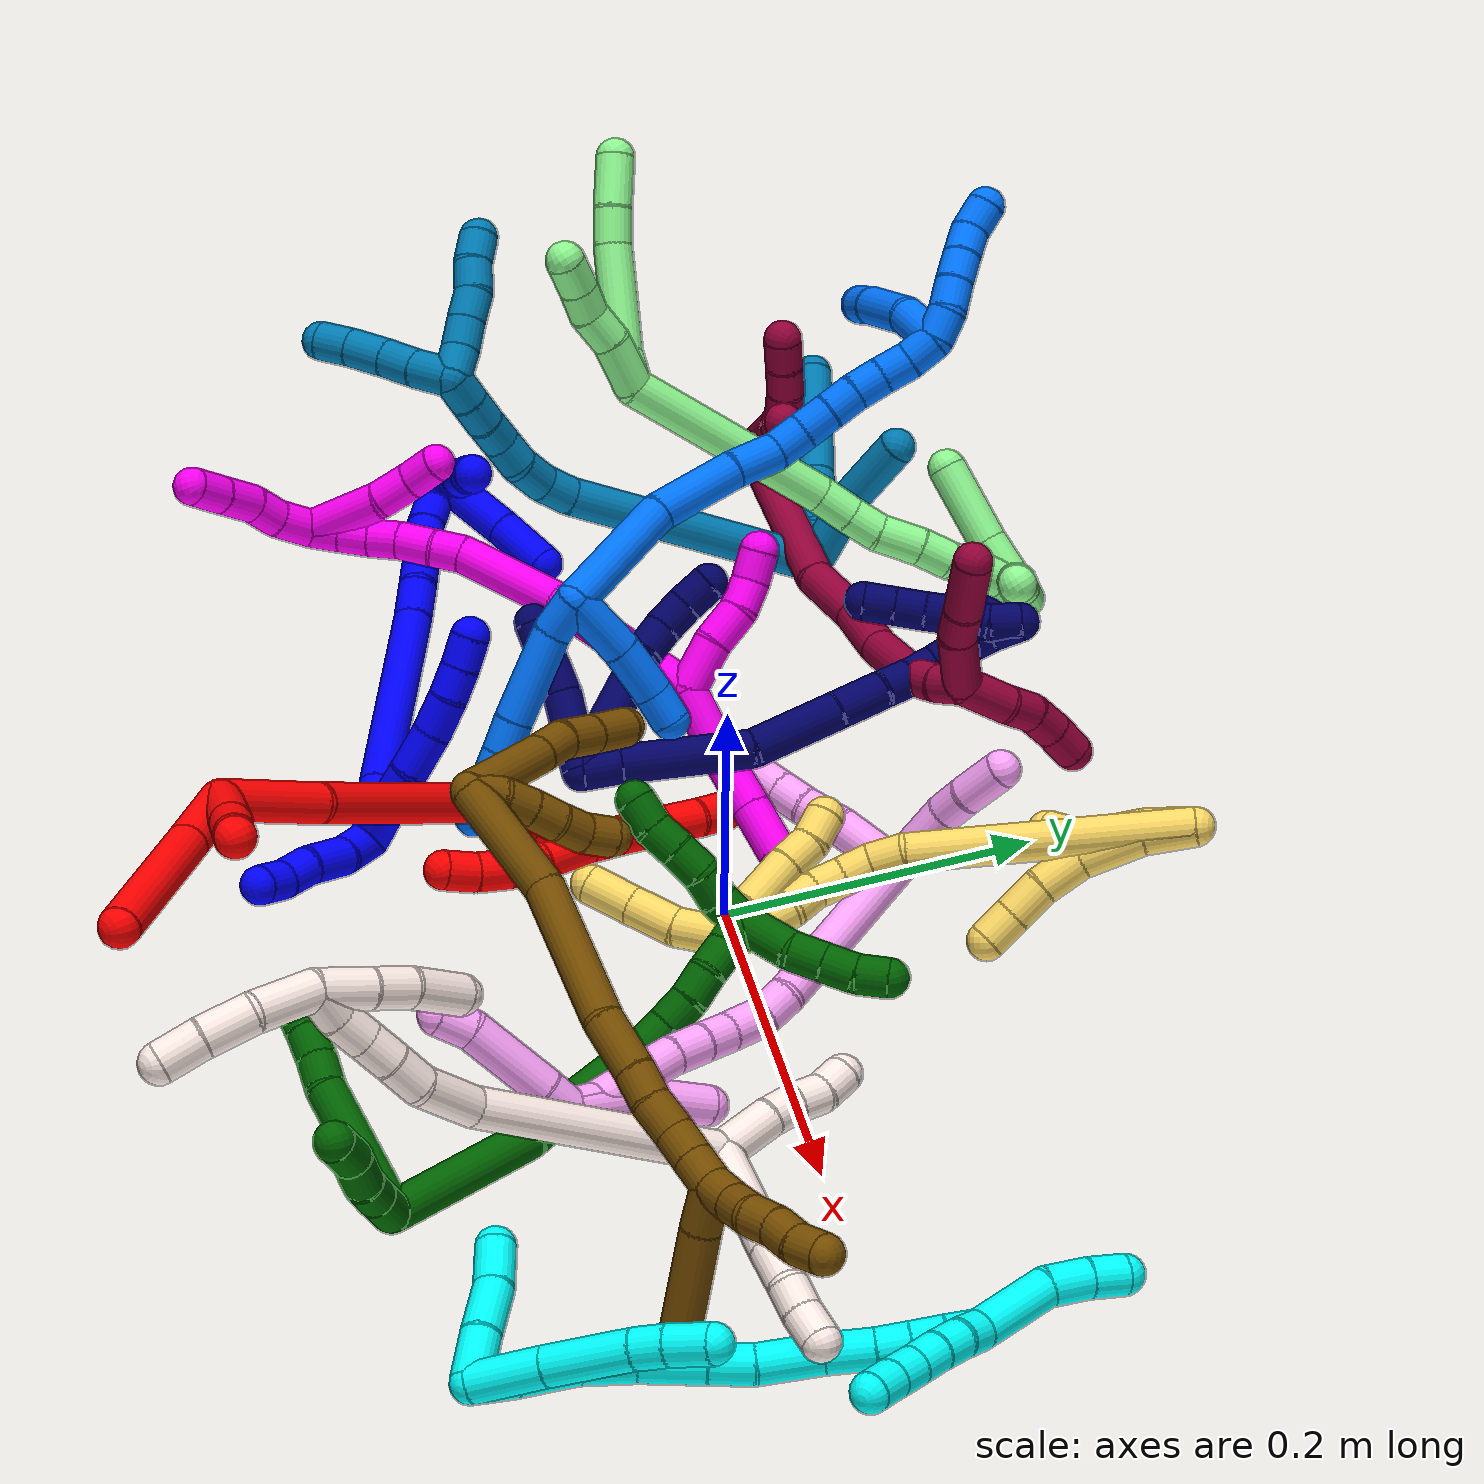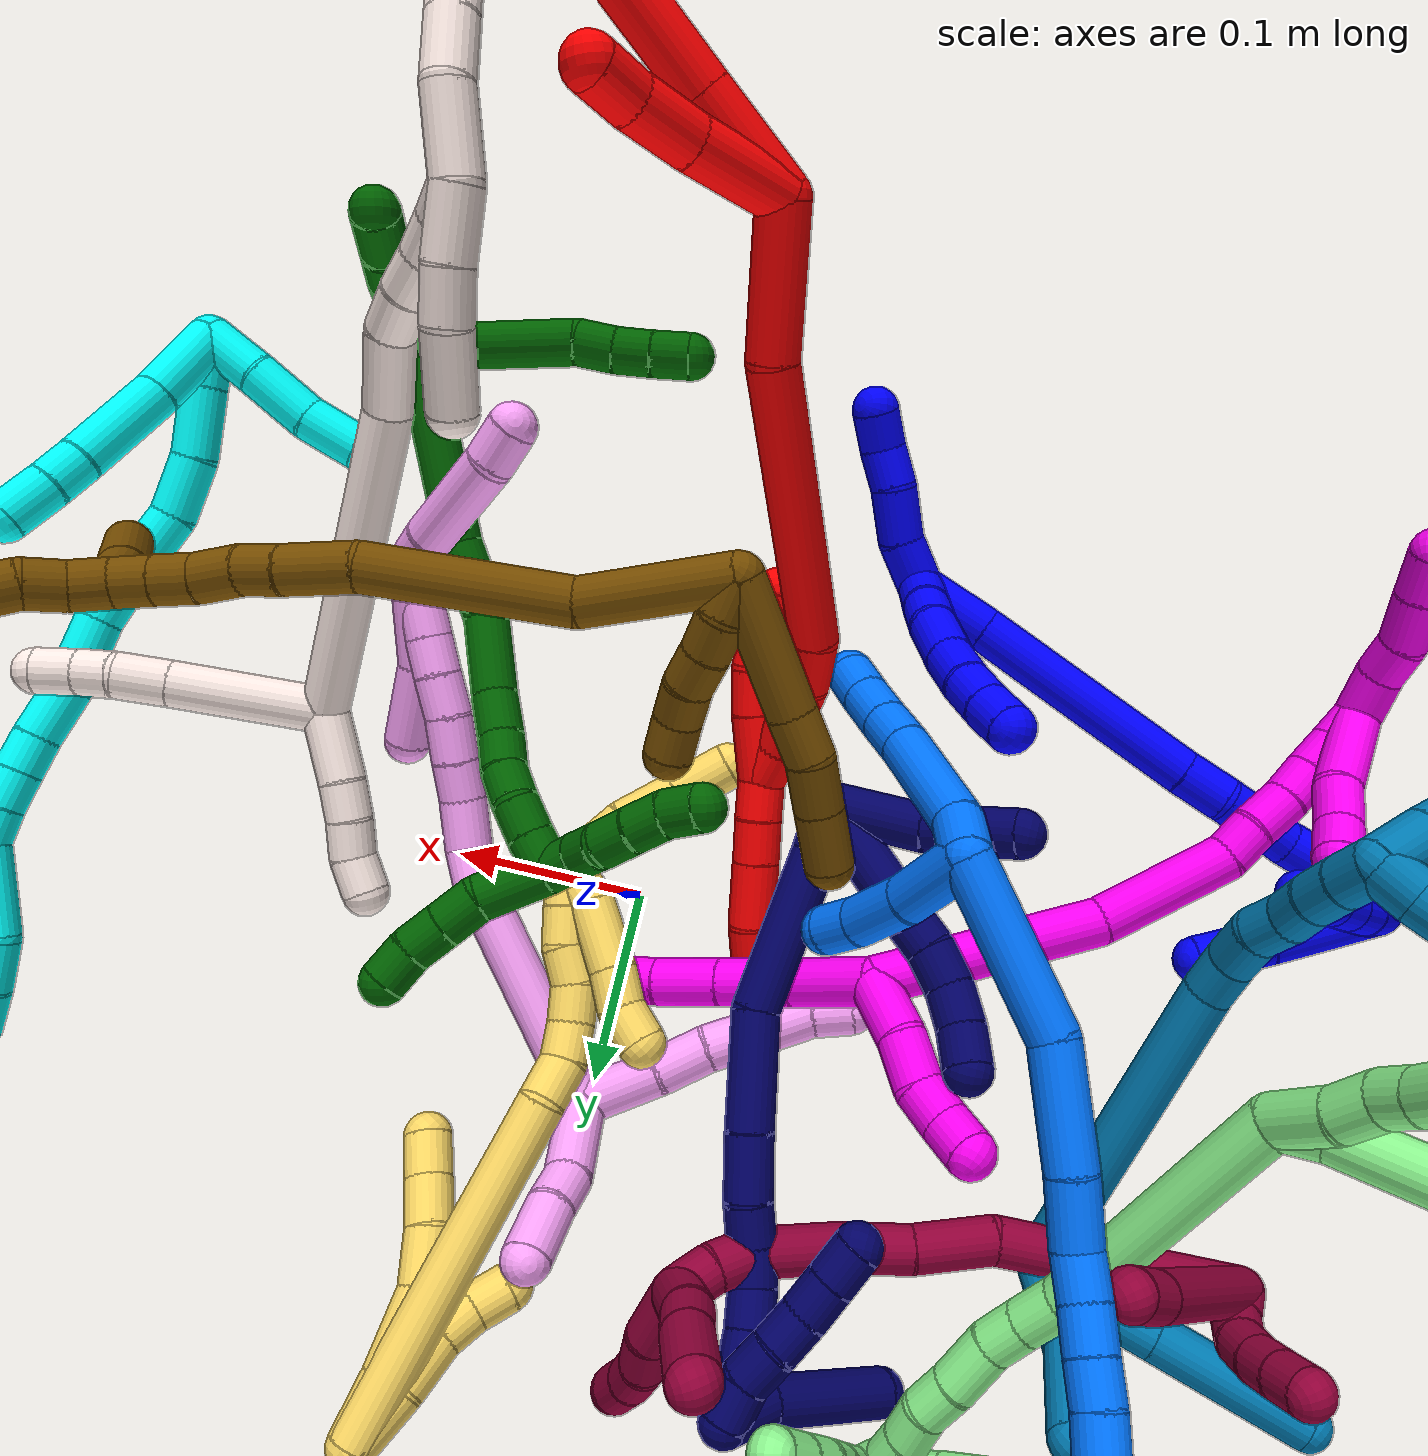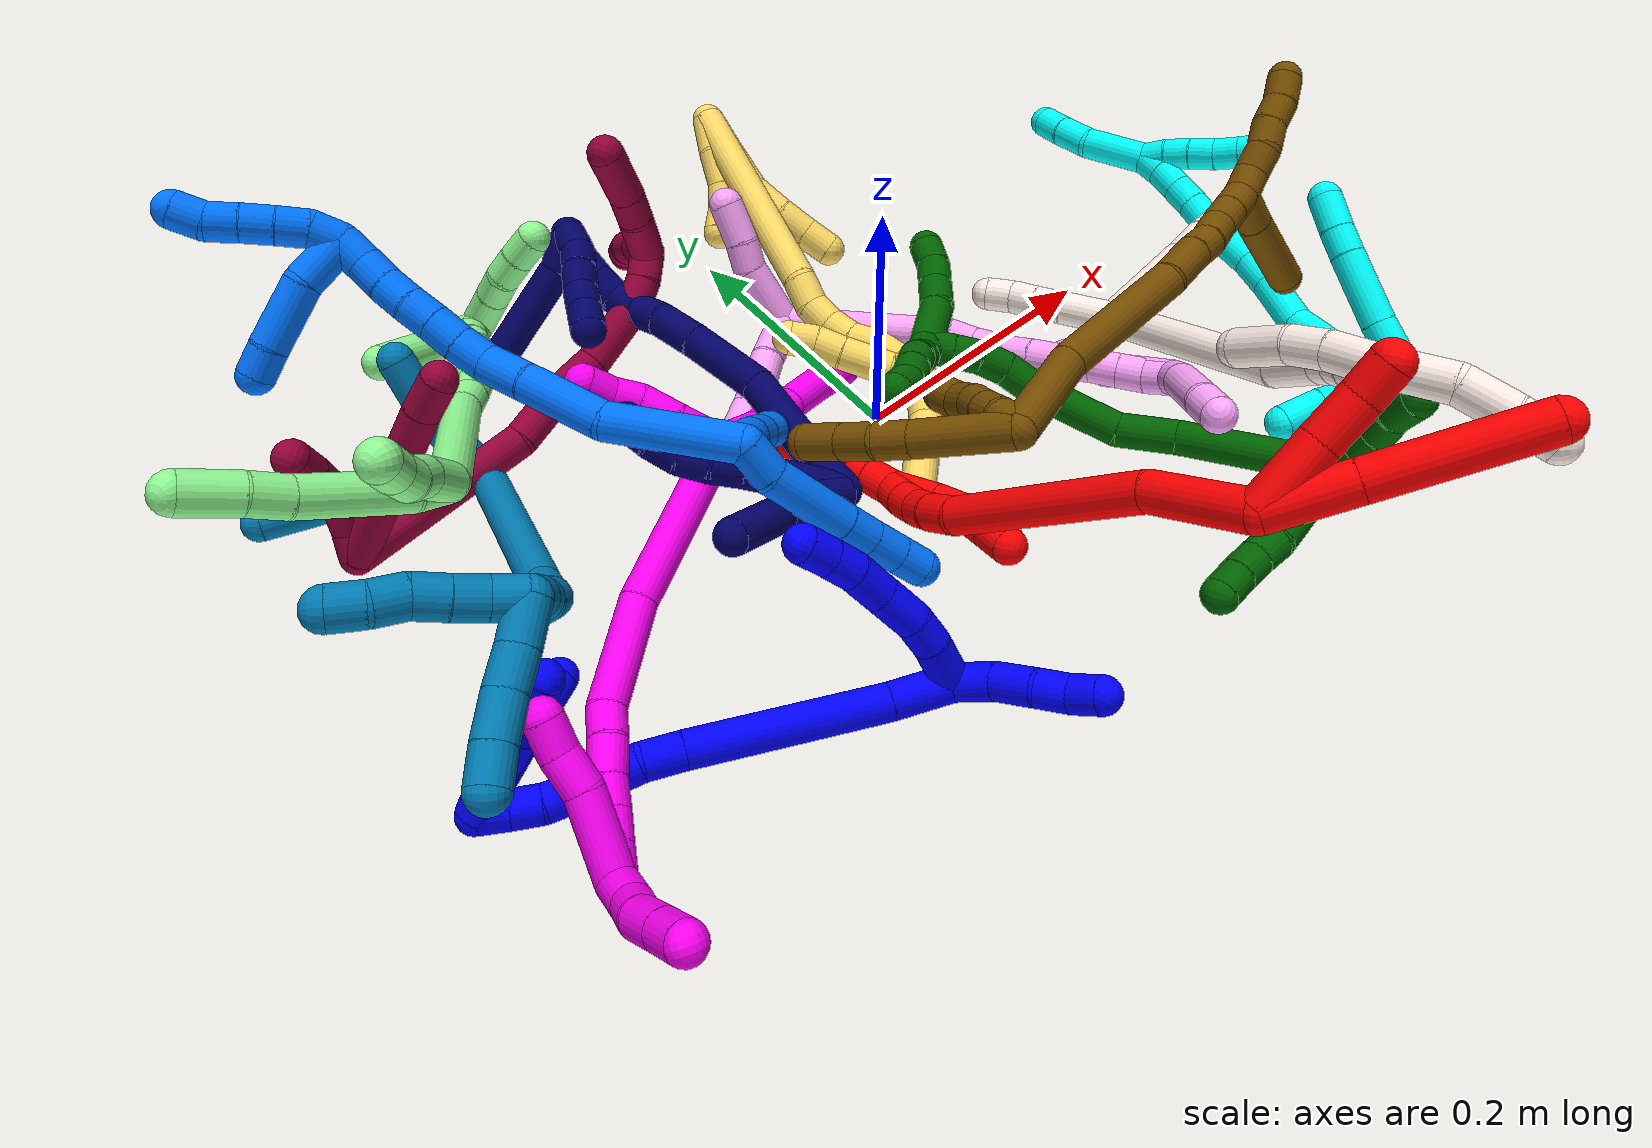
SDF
<sdf version="1.7">
 <world name="default">
  <plugin name="TubeGeneratorPlugin" filename="libtube_generator_plugin.so"/>
  <model name="photoneo_s_sensor">
   <static>1</static>
   <pose>0 0 2 1.57079 1.57079 3.14159</pose>
   <link name="link">
    <inertial><mass>0.1</mass></inertial>
    <sensor name="sensor" type="depth">
     <update_rate>30</update_rate>
     <camera>
      <horizontal_fov>1.22</horizontal_fov>
      <image><width>1920</width><height>1200</height><format>B8G8R8</format></image>
      <clip><near>0.1</near><far>4</far></clip>
      <depth_camera><output>points</output></depth_camera>
     </camera>
     <plugin name="camera_plugin" filename="libgazebo_ros_depth_camera.so">
      <baseline>0.2</baseline>
      <alwaysOn>1</alwaysOn>
      <updateRate>0.0</updateRate>
      <cameraName>camera_ir</cameraName>
      <imageTopicName>/camera/color/image_raw</imageTopicName>
      <cameraInfoTopicName>/camera/color/camera_info</cameraInfoTopicName>
      <depthImageTopicName>/camera/depth/image_raw</depthImageTopicName>
      <depthImageCameraInfoTopicName>/camera/depth/camera_info</depthImageCameraInfoTopicName>
      <pointCloudTopicName>/camera/depth/points</pointCloudTopicName>
      <frameName>fr_optical</frameName>
      <pointCloudCutoff>0.1</pointCloudCutoff>
      <pointCloudCutoffMax>2.0</pointCloudCutoffMax>
      <distortionK1>0</distortionK1>
      <distortionK2>0</distortionK2>
      <distortionK3>0</distortionK3>
      <distortionT1>0</distortionT1>
      <distortionT2>0</distortionT2>
      <CxPrime>0</CxPrime>
      <Cx>0</Cx>
      <Cy>0</Cy>
      <focalLength>0</focalLength>
      <hackBaseline>0</hackBaseline>
     </plugin>
    </sensor>
   </link>
  </model>
  <gravity>0 0 -9.8</gravity>
  <magnetic_field>6e-06 2.3e-05 -4.2e-05</magnetic_field>
  <atmosphere type="adiabatic"/>
  <physics name="default_physics" default="0" type="ode">
   <max_step_size>0.003</max_step_size>
   <real_time_factor>1</real_time_factor>
   <real_time_update_rate>1000</real_time_update_rate>
   <max_contacts>10000</max_contacts>
   <ode>
    <solver>
     <type>quick</type>
     <iters>100</iters>
     <sor>1.3</sor>
     <use_dynamic_moi_rescaling>0</use_dynamic_moi_rescaling>
    </solver>
    <constraints>
     <contact_max_correcting_vel>0</contact_max_correcting_vel>
     <contact_surface_layer>0.001</contact_surface_layer>
     <cfm>0</cfm>
     <erp>0.2</erp>
    </constraints>
   </ode>
  </physics>
  <scene><ambient>0.4 0.4 0.4 1</ambient><background>0.7 0.7 0.7 1</background><shadows>0</shadows></scene>
  <audio><device>default</device></audio>
  <spherical_coordinates>
   <surface_model>EARTH_WGS84</surface_model>
   <latitude_deg>0</latitude_deg>
   <longitude_deg>0</longitude_deg>
   <elevation>0</elevation>
   <heading_deg>0</heading_deg>
  </spherical_coordinates>
  <model name="bin">
   <static>1</static>
   <link name="bottom">
    <collision name="collision-bottom">
     <pose>0 0 -0.01 0 -0 0</pose>
     <geometry><box><size>0.8 0.6 0.02</size></box></geometry>
     <surface>
      <friction><ode><mu>100</mu><mu2>100</mu2></ode></friction>
      <contact><collide_bitmask>65535</collide_bitmask></contact>
     </surface>
    </collision>
   </link>
   <link name="west_wall">
    <collision name="collision-west_wall">
     <pose>-0.41 0 0.1 0 -0 0</pose>
     <geometry><box><size>0.02 0.6 0.2</size></box></geometry>
     <surface>
      <friction><ode><mu>100</mu><mu2>100</mu2></ode></friction>
      <contact><collide_bitmask>65535</collide_bitmask></contact>
     </surface>
    </collision>
   </link>
   <link name="east_wall">
    <collision name="collision-east_wall">
     <pose>0.41 0 0.1 0 -0 0</pose>
     <geometry><box><size>0.02 0.6 0.2</size></box></geometry>
     <surface>
      <friction><ode><mu>100</mu><mu2>100</mu2></ode></friction>
      <contact><collide_bitmask>65535</collide_bitmask></contact>
     </surface>
    </collision>
   </link>
   <link name="south_wall">
    <collision name="collision-south_wall">
     <pose>0 -0.31 0.1 0 -0 0</pose>
     <geometry><box><size>0.8 0.02 0.2</size></box></geometry>
     <surface>
      <friction><ode><mu>100</mu><mu2>100</mu2></ode></friction>
      <contact><collide_bitmask>65535</collide_bitmask></contact>
     </surface>
    </collision>
   </link>
   <link name="north_wall">
    <collision name="collision-north_wall">
     <pose>0 0.31 0.1 0 -0 0</pose>
     <geometry><box><size>0.8 0.02 0.2</size></box></geometry>
     <surface>
      <friction><ode><mu>100</mu><mu2>100</mu2></ode></friction>
      <contact><collide_bitmask>65535</collide_bitmask></contact>
     </surface>
    </collision>
   </link>
  </model>
  <model name="1">
   <static>0</static>
   <link name="1">
    <collision name="collision-cylinder-e_1_2_8">
     <pose>-0.00369 0.013308 -0.010837 -2.25419 -0.211809 0.440057</pose>
     <geometry><cylinder><radius>0.0125</radius><length>0.035109</length></cylinder></geometry>
     <surface>
      <friction><ode><mu>1.16</mu><mu2>1.16</mu2><slip1>0</slip1><slip2>0</slip2></ode></friction>
      <contact><ode><kp>1e+06</kp><kd>1</kd><max_vel>0</max_vel><min_depth>0.001</min_depth></ode></contact>
     </surface>
    </collision>
    <visual name="visual-cylinder-e_1_2_8">
     <pose>-0.00369 0.013308 -0.010837 -2.25419 -0.211809 0.440057</pose>
     <geometry><cylinder><radius>0.0125</radius><length>0.035109</length></cylinder></geometry>
     <material><ambient>0 0 1 1</ambient></material>
    </visual>
    <collision name="collision-cylinder-e_2_8_9">
     <pose>-0.010771 0.034968 -0.027035 -2.14153 -0.329173 0.590249</pose>
     <geometry><cylinder><radius>0.0125</radius><length>0.020975</length></cylinder></geometry>
     <surface>
      <friction><ode><mu>1.16</mu><mu2>1.16</mu2><slip1>0</slip1><slip2>0</slip2></ode></friction>
      <contact><ode><kp>1e+06</kp><kd>1</kd><max_vel>0</max_vel><min_depth>0.001</min_depth></ode></contact>
     </surface>
    </collision>
    <visual name="visual-cylinder-e_2_8_9">
     <pose>-0.010771 0.034968 -0.027035 -2.14153 -0.329173 0.590249</pose>
     <geometry><cylinder><radius>0.0125</radius><length>0.020975</length></cylinder></geometry>
     <material><ambient>0 0 1 1</ambient></material>
    </visual>
    <collision name="collision-cylinder-e_3_9_10">
     <pose>-0.019874 0.055697 -0.037319 -1.94926 -0.405152 0.587874</pose>
     <geometry><cylinder><radius>0.0125</radius><length>0.028986</length></cylinder></geometry>
     <surface>
      <friction><ode><mu>1.16</mu><mu2>1.16</mu2><slip1>0</slip1><slip2>0</slip2></ode></friction>
      <contact><ode><kp>1e+06</kp><kd>1</kd><max_vel>0</max_vel><min_depth>0.001</min_depth></ode></contact>
     </surface>
    </collision>
    <visual name="visual-cylinder-e_3_9_10">
     <pose>-0.019874 0.055697 -0.037319 -1.94926 -0.405152 0.587874</pose>
     <geometry><cylinder><radius>0.0125</radius><length>0.028986</length></cylinder></geometry>
     <material><ambient>0 0 1 1</ambient></material>
    </visual>
    <collision name="collision-cylinder-e_4_10_11">
     <pose>-0.029248 0.079048 -0.046589 -1.94814 -0.300772 0.438922</pose>
     <geometry><cylinder><radius>0.0125</radius><length>0.024719</length></cylinder></geometry>
     <surface>
      <friction><ode><mu>1.16</mu><mu2>1.16</mu2><slip1>0</slip1><slip2>0</slip2></ode></friction>
      <contact><ode><kp>1e+06</kp><kd>1</kd><max_vel>0</max_vel><min_depth>0.001</min_depth></ode></contact>
     </surface>
    </collision>
    <visual name="visual-cylinder-e_4_10_11">
     <pose>-0.029248 0.079048 -0.046589 -1.94814 -0.300772 0.438922</pose>
     <geometry><cylinder><radius>0.0125</radius><length>0.024719</length></cylinder></geometry>
     <material><ambient>0 0 1 1</ambient></material>
    </visual>
    <collision name="collision-cylinder-e_5_11_12">
     <pose>-0.035914 0.099392 -0.052964 -1.78369 -0.30371 0.374846</pose>
     <geometry><cylinder><radius>0.0125</radius><length>0.020093</length></cylinder></geometry>
     <surface>
      <friction><ode><mu>1.16</mu><mu2>1.16</mu2><slip1>0</slip1><slip2>0</slip2></ode></friction>
      <contact><ode><kp>1e+06</kp><kd>1</kd><max_vel>0</max_vel><min_depth>0.001</min_depth></ode></contact>
     </surface>
    </collision>
    <visual name="visual-cylinder-e_5_11_12">
     <pose>-0.035914 0.099392 -0.052964 -1.78369 -0.30371 0.374846</pose>
     <geometry><cylinder><radius>0.0125</radius><length>0.020093</length></cylinder></geometry>
     <material><ambient>0 0 1 1</ambient></material>
    </visual>
    <collision name="collision-cylinder-e_6_12_6">
     <pose>-0.041381 0.118352 -0.056765 -1.75386 -0.247348 0.296675</pose>
     <geometry><cylinder><radius>0.0125</radius><length>0.020118</length></cylinder></geometry>
     <surface>
      <friction><ode><mu>1.16</mu><mu2>1.16</mu2><slip1>0</slip1><slip2>0</slip2></ode></friction>
      <contact><ode><kp>1e+06</kp><kd>1</kd><max_vel>0</max_vel><min_depth>0.001</min_depth></ode></contact>
     </surface>
    </collision>
    <visual name="visual-cylinder-e_6_12_6">
     <pose>-0.041381 0.118352 -0.056765 -1.75386 -0.247348 0.296675</pose>
     <geometry><cylinder><radius>0.0125</radius><length>0.020118</length></cylinder></geometry>
     <material><ambient>0 0 1 1</ambient></material>
    </visual>
    <collision name="collision-cylinder-e_1_2_13">
     <pose>0.010882 -0.004922 -0.007622 2.56821 0.875781 2.01769</pose>
     <geometry><cylinder><radius>0.0125</radius><length>0.028337</length></cylinder></geometry>
     <surface>
      <friction><ode><mu>1.16</mu><mu2>1.16</mu2><slip1>0</slip1><slip2>0</slip2></ode></friction>
      <contact><ode><kp>1e+06</kp><kd>1</kd><max_vel>0</max_vel><min_depth>0.001</min_depth></ode></contact>
     </surface>
    </collision>
    <visual name="visual-cylinder-e_1_2_13">
     <pose>0.010882 -0.004922 -0.007622 2.56821 0.875781 2.01769</pose>
     <geometry><cylinder><radius>0.0125</radius><length>0.028337</length></cylinder></geometry>
     <material><ambient>0 0 1 1</ambient></material>
    </visual>
    <collision name="collision-cylinder-e_2_13_14">
     <pose>0.034807 -0.012367 -0.021219 2.74211 1.10939 2.50998</pose>
     <geometry><cylinder><radius>0.0125</radius><length>0.029132</length></cylinder></geometry>
     <surface>
      <friction><ode><mu>1.16</mu><mu2>1.16</mu2><slip1>0</slip1><slip2>0</slip2></ode></friction>
      <contact><ode><kp>1e+06</kp><kd>1</kd><max_vel>0</max_vel><min_depth>0.001</min_depth></ode></contact>
     </surface>
    </collision>
    <visual name="visual-cylinder-e_2_13_14">
     <pose>0.034807 -0.012367 -0.021219 2.74211 1.10939 2.50998</pose>
     <geometry><cylinder><radius>0.0125</radius><length>0.029132</length></cylinder></geometry>
     <material><ambient>0 0 1 1</ambient></material>
    </visual>
    <collision name="collision-cylinder-e_3_14_15">
     <pose>0.057076 -0.019019 -0.031169 2.33713 1.01484 1.83529</pose>
     <geometry><cylinder><radius>0.0125</radius><length>0.021726</length></cylinder></geometry>
     <surface>
      <friction><ode><mu>1.16</mu><mu2>1.16</mu2><slip1>0</slip1><slip2>0</slip2></ode></friction>
      <contact><ode><kp>1e+06</kp><kd>1</kd><max_vel>0</max_vel><min_depth>0.001</min_depth></ode></contact>
     </surface>
    </collision>
    <visual name="visual-cylinder-e_3_14_15">
     <pose>0.057076 -0.019019 -0.031169 2.33713 1.01484 1.83529</pose>
     <geometry><cylinder><radius>0.0125</radius><length>0.021726</length></cylinder></geometry>
     <material><ambient>0 0 1 1</ambient></material>
    </visual>
    <collision name="collision-cylinder-e_4_15_5">
     <pose>0.075165 -0.024466 -0.040431 2.89752 1.01958 2.70969</pose>
     <geometry><cylinder><radius>0.0125</radius><length>0.020805</length></cylinder></geometry>
     <surface>
      <friction><ode><mu>1.16</mu><mu2>1.16</mu2><slip1>0</slip1><slip2>0</slip2></ode></friction>
      <contact><ode><kp>1e+06</kp><kd>1</kd><max_vel>0</max_vel><min_depth>0.001</min_depth></ode></contact>
     </surface>
    </collision>
    <visual name="visual-cylinder-e_4_15_5">
     <pose>0.075165 -0.024466 -0.040431 2.89752 1.01958 2.70969</pose>
     <geometry><cylinder><radius>0.0125</radius><length>0.020805</length></cylinder></geometry>
     <material><ambient>0 0 1 1</ambient></material>
    </visual>
    <collision name="collision-cylinder-e_1_2_16">
     <pose>-0.006148 0.016331 0.011807 -0.944801 -0.29609 0.15212</pose>
     <geometry><cylinder><radius>0.0125</radius><length>0.042138</length></cylinder></geometry>
     <surface>
      <friction><ode><mu>1.16</mu><mu2>1.16</mu2><slip1>0</slip1><slip2>0</slip2></ode></friction>
      <contact><ode><kp>1e+06</kp><kd>1</kd><max_vel>0</max_vel><min_depth>0.001</min_depth></ode></contact>
     </surface>
    </collision>
    <visual name="visual-cylinder-e_1_2_16">
     <pose>-0.006148 0.016331 0.011807 -0.944801 -0.29609 0.15212</pose>
     <geometry><cylinder><radius>0.0125</radius><length>0.042138</length></cylinder></geometry>
     <material><ambient>0 0 1 1</ambient></material>
    </visual>
    <collision name="collision-cylinder-e_2_16_17">
     <pose>-0.033328 0.084496 0.05674 -1.00215 -0.329452 0.181591</pose>
     <geometry><cylinder><radius>0.0125</radius><length>0.130023</length></cylinder></geometry>
     <surface>
      <friction><ode><mu>1.16</mu><mu2>1.16</mu2><slip1>0</slip1><slip2>0</slip2></ode></friction>
      <contact><ode><kp>1e+06</kp><kd>1</kd><max_vel>0</max_vel><min_depth>0.001</min_depth></ode></contact>
     </surface>
    </collision>
    <visual name="visual-cylinder-e_2_16_17">
     <pose>-0.033328 0.084496 0.05674 -1.00215 -0.329452 0.181591</pose>
     <geometry><cylinder><radius>0.0125</radius><length>0.130023</length></cylinder></geometry>
     <material><ambient>0 0 1 1</ambient></material>
    </visual>
    <collision name="collision-cylinder-e_3_17_18">
     <pose>-0.057987 0.146732 0.096652 -0.992626 -0.284073 0.154567</pose>
     <geometry><cylinder><radius>0.0125</radius><length>0.025876</length></cylinder></geometry>
     <surface>
      <friction><ode><mu>1.16</mu><mu2>1.16</mu2><slip1>0</slip1><slip2>0</slip2></ode></friction>
      <contact><ode><kp>1e+06</kp><kd>1</kd><max_vel>0</max_vel><min_depth>0.001</min_depth></ode></contact>
     </surface>
    </collision>
    <visual name="visual-cylinder-e_3_17_18">
     <pose>-0.057987 0.146732 0.096652 -0.992626 -0.284073 0.154567</pose>
     <geometry><cylinder><radius>0.0125</radius><length>0.025876</length></cylinder></geometry>
     <material><ambient>0 0 1 1</ambient></material>
    </visual>
    <collision name="collision-cylinder-e_4_18_19">
     <pose>-0.065047 0.163853 0.111308 -0.70681 -0.320427 0.119084</pose>
     <geometry><cylinder><radius>0.0125</radius><length>0.021806</length></cylinder></geometry>
     <surface>
      <friction><ode><mu>1.16</mu><mu2>1.16</mu2><slip1>0</slip1><slip2>0</slip2></ode></friction>
      <contact><ode><kp>1e+06</kp><kd>1</kd><max_vel>0</max_vel><min_depth>0.001</min_depth></ode></contact>
     </surface>
    </collision>
    <visual name="visual-cylinder-e_4_18_19">
     <pose>-0.065047 0.163853 0.111308 -0.70681 -0.320427 0.119084</pose>
     <geometry><cylinder><radius>0.0125</radius><length>0.021806</length></cylinder></geometry>
     <material><ambient>0 0 1 1</ambient></material>
    </visual>
    <collision name="collision-cylinder-e_5_19_20">
     <pose>-0.071968 0.176566 0.126437 -0.690077 -0.35475 0.128679</pose>
     <geometry><cylinder><radius>0.0125</radius><length>0.020077</length></cylinder></geometry>
     <surface>
      <friction><ode><mu>1.16</mu><mu2>1.16</mu2><slip1>0</slip1><slip2>0</slip2></ode></friction>
      <contact><ode><kp>1e+06</kp><kd>1</kd><max_vel>0</max_vel><min_depth>0.001</min_depth></ode></contact>
     </surface>
    </collision>
    <visual name="visual-cylinder-e_5_19_20">
     <pose>-0.071968 0.176566 0.126437 -0.690077 -0.35475 0.128679</pose>
     <geometry><cylinder><radius>0.0125</radius><length>0.020077</length></cylinder></geometry>
     <material><ambient>0 0 1 1</ambient></material>
    </visual>
    <collision name="collision-cylinder-e_6_20_21">
     <pose>-0.077834 0.190109 0.139853 -0.886835 -0.239478 0.114165</pose>
     <geometry><cylinder><radius>0.0125</radius><length>0.020057</length></cylinder></geometry>
     <surface>
      <friction><ode><mu>1.16</mu><mu2>1.16</mu2><slip1>0</slip1><slip2>0</slip2></ode></friction>
      <contact><ode><kp>1e+06</kp><kd>1</kd><max_vel>0</max_vel><min_depth>0.001</min_depth></ode></contact>
     </surface>
    </collision>
    <visual name="visual-cylinder-e_6_20_21">
     <pose>-0.077834 0.190109 0.139853 -0.886835 -0.239478 0.114165</pose>
     <geometry><cylinder><radius>0.0125</radius><length>0.020057</length></cylinder></geometry>
     <material><ambient>0 0 1 1</ambient></material>
    </visual>
    <collision name="collision-cylinder-e_7_21_22">
     <pose>-0.08445 0.205154 0.15111 -0.973119 -0.43727 0.233989</pose>
     <geometry><cylinder><radius>0.0125</radius><length>0.020014</length></cylinder></geometry>
     <surface>
      <friction><ode><mu>1.16</mu><mu2>1.16</mu2><slip1>0</slip1><slip2>0</slip2></ode></friction>
      <contact><ode><kp>1e+06</kp><kd>1</kd><max_vel>0</max_vel><min_depth>0.001</min_depth></ode></contact>
     </surface>
    </collision>
    <visual name="visual-cylinder-e_7_21_22">
     <pose>-0.08445 0.205154 0.15111 -0.973119 -0.43727 0.233989</pose>
     <geometry><cylinder><radius>0.0125</radius><length>0.020014</length></cylinder></geometry>
     <material><ambient>0 0 1 1</ambient></material>
    </visual>
    <collision name="collision-cylinder-e_8_22_1">
     <pose>-0.092256 0.221016 0.160375 -1.1091 -0.364675 0.227424</pose>
     <geometry><cylinder><radius>0.0125</radius><length>0.020009</length></cylinder></geometry>
     <surface>
      <friction><ode><mu>1.16</mu><mu2>1.16</mu2><slip1>0</slip1><slip2>0</slip2></ode></friction>
      <contact><ode><kp>1e+06</kp><kd>1</kd><max_vel>0</max_vel><min_depth>0.001</min_depth></ode></contact>
     </surface>
    </collision>
    <visual name="visual-cylinder-e_8_22_1">
     <pose>-0.092256 0.221016 0.160375 -1.1091 -0.364675 0.227424</pose>
     <geometry><cylinder><radius>0.0125</radius><length>0.020009</length></cylinder></geometry>
     <material><ambient>0 0 1 1</ambient></material>
    </visual>
    <collision name="collision-cylinder-e_1_1_23">
     <pose>-0.111172 0.212944 0.144096 2.46431 -0.529358 -1.31178</pose>
     <geometry><cylinder><radius>0.0125</radius><length>0.060786</length></cylinder></geometry>
     <surface>
      <friction><ode><mu>1.16</mu><mu2>1.16</mu2><slip1>0</slip1><slip2>0</slip2></ode></friction>
      <contact><ode><kp>1e+06</kp><kd>1</kd><max_vel>0</max_vel><min_depth>0.001</min_depth></ode></contact>
     </surface>
    </collision>
    <visual name="visual-cylinder-e_1_1_23">
     <pose>-0.111172 0.212944 0.144096 2.46431 -0.529358 -1.31178</pose>
     <geometry><cylinder><radius>0.0125</radius><length>0.060786</length></cylinder></geometry>
     <material><ambient>0 0 1 1</ambient></material>
    </visual>
    <collision name="collision-cylinder-e_2_23_4">
     <pose>-0.136223 0.185196 0.110909 2.41579 -0.517723 -1.21791</pose>
     <geometry><cylinder><radius>0.0125</radius><length>0.039214</length></cylinder></geometry>
     <surface>
      <friction><ode><mu>1.16</mu><mu2>1.16</mu2><slip1>0</slip1><slip2>0</slip2></ode></friction>
      <contact><ode><kp>1e+06</kp><kd>1</kd><max_vel>0</max_vel><min_depth>0.001</min_depth></ode></contact>
     </surface>
    </collision>
    <visual name="visual-cylinder-e_2_23_4">
     <pose>-0.136223 0.185196 0.110909 2.41579 -0.517723 -1.21791</pose>
     <geometry><cylinder><radius>0.0125</radius><length>0.039214</length></cylinder></geometry>
     <material><ambient>0 0 1 1</ambient></material>
    </visual>
    <collision name="collision-cylinder-e_1_1_24">
     <pose>-0.095438 0.229805 0.154555 -3.09943 0.038567 -1.4818</pose>
     <geometry><cylinder><radius>0.0125</radius><length>0.02</length></cylinder></geometry>
     <surface>
      <friction><ode><mu>1.16</mu><mu2>1.16</mu2><slip1>0</slip1><slip2>0</slip2></ode></friction>
      <contact><ode><kp>1e+06</kp><kd>1</kd><max_vel>0</max_vel><min_depth>0.001</min_depth></ode></contact>
     </surface>
    </collision>
    <visual name="visual-cylinder-e_1_1_24">
     <pose>-0.095438 0.229805 0.154555 -3.09943 0.038567 -1.4818</pose>
     <geometry><cylinder><radius>0.0125</radius><length>0.02</length></cylinder></geometry>
     <material><ambient>0 0 1 1</ambient></material>
    </visual>
    <collision name="collision-cylinder-e_2_24_25">
     <pose>-0.093696 0.229815 0.134672 3.10004 0.136105 2.54968</pose>
     <geometry><cylinder><radius>0.0125</radius><length>0.02</length></cylinder></geometry>
     <surface>
      <friction><ode><mu>1.16</mu><mu2>1.16</mu2><slip1>0</slip1><slip2>0</slip2></ode></friction>
      <contact><ode><kp>1e+06</kp><kd>1</kd><max_vel>0</max_vel><min_depth>0.001</min_depth></ode></contact>
     </surface>
    </collision>
    <visual name="visual-cylinder-e_2_24_25">
     <pose>-0.093696 0.229815 0.134672 3.10004 0.136105 2.54968</pose>
     <geometry><cylinder><radius>0.0125</radius><length>0.02</length></cylinder></geometry>
     <material><ambient>0 0 1 1</ambient></material>
    </visual>
    <collision name="collision-cylinder-e_3_25_26">
     <pose>-0.090937 0.228856 0.114887 3.08629 0.140656 2.39329</pose>
     <geometry><cylinder><radius>0.0125</radius><length>0.02</length></cylinder></geometry>
     <surface>
      <friction><ode><mu>1.16</mu><mu2>1.16</mu2><slip1>0</slip1><slip2>0</slip2></ode></friction>
      <contact><ode><kp>1e+06</kp><kd>1</kd><max_vel>0</max_vel><min_depth>0.001</min_depth></ode></contact>
     </surface>
    </collision>
    <visual name="visual-cylinder-e_3_25_26">
     <pose>-0.090937 0.228856 0.114887 3.08629 0.140656 2.39329</pose>
     <geometry><cylinder><radius>0.0125</radius><length>0.02</length></cylinder></geometry>
     <material><ambient>0 0 1 1</ambient></material>
    </visual>
    <collision name="collision-cylinder-e_4_26_27">
     <pose>-0.089106 0.229443 0.095075 -3.02777 0.042923 -0.72061</pose>
     <geometry><cylinder><radius>0.0125</radius><length>0.02</length></cylinder></geometry>
     <surface>
      <friction><ode><mu>1.16</mu><mu2>1.16</mu2><slip1>0</slip1><slip2>0</slip2></ode></friction>
      <contact><ode><kp>1e+06</kp><kd>1</kd><max_vel>0</max_vel><min_depth>0.001</min_depth></ode></contact>
     </surface>
    </collision>
    <visual name="visual-cylinder-e_4_26_27">
     <pose>-0.089106 0.229443 0.095075 -3.02777 0.042923 -0.72061</pose>
     <geometry><cylinder><radius>0.0125</radius><length>0.02</length></cylinder></geometry>
     <material><ambient>0 0 1 1</ambient></material>
    </visual>
    <collision name="collision-cylinder-e_5_27_3">
     <pose>-0.086919 0.230596 0.075304 -3.13972 0.176754 -3.12051</pose>
     <geometry><cylinder><radius>0.0125</radius><length>0.02</length></cylinder></geometry>
     <surface>
      <friction><ode><mu>1.16</mu><mu2>1.16</mu2><slip1>0</slip1><slip2>0</slip2></ode></friction>
      <contact><ode><kp>1e+06</kp><kd>1</kd><max_vel>0</max_vel><min_depth>0.001</min_depth></ode></contact>
     </surface>
    </collision>
    <visual name="visual-cylinder-e_5_27_3">
     <pose>-0.086919 0.230596 0.075304 -3.13972 0.176754 -3.12051</pose>
     <geometry><cylinder><radius>0.0125</radius><length>0.02</length></cylinder></geometry>
     <material><ambient>0 0 1 1</ambient></material>
    </visual>
    <collision name="collision-sphere-3">
     <pose>-0.08516 0.230615 0.06546 0 -0 0</pose>
     <geometry><sphere><radius>0.0125</radius></sphere></geometry>
     <surface>
      <friction><ode><mu>1.16</mu><mu2>1.16</mu2><slip1>0</slip1><slip2>0</slip2></ode></friction>
      <contact><ode><kp>1e+06</kp><kd>1</kd><max_vel>0</max_vel><min_depth>0.001</min_depth></ode></contact>
     </surface>
    </collision>
    <visual name="visual-sphere-3">
     <pose>-0.08516 0.230615 0.06546 0 -0 0</pose>
     <geometry><sphere><radius>0.0125</radius></sphere></geometry>
     <material><ambient>0 0 1 1</ambient></material>
    </visual>
    <collision name="collision-sphere-27">
     <pose>-0.088677 0.230578 0.085149 0 -0 0</pose>
     <geometry><sphere><radius>0.0125</radius></sphere></geometry>
     <surface>
      <friction><ode><mu>1.16</mu><mu2>1.16</mu2><slip1>0</slip1><slip2>0</slip2></ode></friction>
      <contact><ode><kp>1e+06</kp><kd>1</kd><max_vel>0</max_vel><min_depth>0.001</min_depth></ode></contact>
     </surface>
    </collision>
    <visual name="visual-sphere-27">
     <pose>-0.088677 0.230578 0.085149 0 -0 0</pose>
     <geometry><sphere><radius>0.0125</radius></sphere></geometry>
     <material><ambient>0 0 1 1</ambient></material>
    </visual>
    <collision name="collision-sphere-26">
     <pose>-0.089535 0.228308 0.105001 0 -0 0</pose>
     <geometry><sphere><radius>0.0125</radius></sphere></geometry>
     <surface>
      <friction><ode><mu>1.16</mu><mu2>1.16</mu2><slip1>0</slip1><slip2>0</slip2></ode></friction>
      <contact><ode><kp>1e+06</kp><kd>1</kd><max_vel>0</max_vel><min_depth>0.001</min_depth></ode></contact>
     </surface>
    </collision>
    <visual name="visual-sphere-26">
     <pose>-0.089535 0.228308 0.105001 0 -0 0</pose>
     <geometry><sphere><radius>0.0125</radius></sphere></geometry>
     <material><ambient>0 0 1 1</ambient></material>
    </visual>
    <collision name="collision-sphere-25">
     <pose>-0.092339 0.229403 0.124773 0 -0 0</pose>
     <geometry><sphere><radius>0.0125</radius></sphere></geometry>
     <surface>
      <friction><ode><mu>1.16</mu><mu2>1.16</mu2><slip1>0</slip1><slip2>0</slip2></ode></friction>
      <contact><ode><kp>1e+06</kp><kd>1</kd><max_vel>0</max_vel><min_depth>0.001</min_depth></ode></contact>
     </surface>
    </collision>
    <visual name="visual-sphere-25">
     <pose>-0.092339 0.229403 0.124773 0 -0 0</pose>
     <geometry><sphere><radius>0.0125</radius></sphere></geometry>
     <material><ambient>0 0 1 1</ambient></material>
    </visual>
    <collision name="collision-sphere-24">
     <pose>-0.095053 0.230226 0.144571 0 -0 0</pose>
     <geometry><sphere><radius>0.0125</radius></sphere></geometry>
     <surface>
      <friction><ode><mu>1.16</mu><mu2>1.16</mu2><slip1>0</slip1><slip2>0</slip2></ode></friction>
      <contact><ode><kp>1e+06</kp><kd>1</kd><max_vel>0</max_vel><min_depth>0.001</min_depth></ode></contact>
     </surface>
    </collision>
    <visual name="visual-sphere-24">
     <pose>-0.095053 0.230226 0.144571 0 -0 0</pose>
     <geometry><sphere><radius>0.0125</radius></sphere></geometry>
     <material><ambient>0 0 1 1</ambient></material>
    </visual>
    <collision name="collision-sphere-4">
     <pose>-0.145927 0.173888 0.098166 0 -0 0</pose>
     <geometry><sphere><radius>0.0125</radius></sphere></geometry>
     <surface>
      <friction><ode><mu>1.16</mu><mu2>1.16</mu2><slip1>0</slip1><slip2>0</slip2></ode></friction>
      <contact><ode><kp>1e+06</kp><kd>1</kd><max_vel>0</max_vel><min_depth>0.001</min_depth></ode></contact>
     </surface>
    </collision>
    <visual name="visual-sphere-4">
     <pose>-0.145927 0.173888 0.098166 0 -0 0</pose>
     <geometry><sphere><radius>0.0125</radius></sphere></geometry>
     <material><ambient>0 0 1 1</ambient></material>
    </visual>
    <collision name="collision-sphere-23">
     <pose>-0.126519 0.196505 0.123653 0 -0 0</pose>
     <geometry><sphere><radius>0.0125</radius></sphere></geometry>
     <surface>
      <friction><ode><mu>1.16</mu><mu2>1.16</mu2><slip1>0</slip1><slip2>0</slip2></ode></friction>
      <contact><ode><kp>1e+06</kp><kd>1</kd><max_vel>0</max_vel><min_depth>0.001</min_depth></ode></contact>
     </surface>
    </collision>
    <visual name="visual-sphere-23">
     <pose>-0.126519 0.196505 0.123653 0 -0 0</pose>
     <geometry><sphere><radius>0.0125</radius></sphere></geometry>
     <material><ambient>0 0 1 1</ambient></material>
    </visual>
    <collision name="collision-sphere-1">
     <pose>-0.095824 0.229384 0.164538 0 -0 0</pose>
     <geometry><sphere><radius>0.0125</radius></sphere></geometry>
     <surface>
      <friction><ode><mu>1.16</mu><mu2>1.16</mu2><slip1>0</slip1><slip2>0</slip2></ode></friction>
      <contact><ode><kp>1e+06</kp><kd>1</kd><max_vel>0</max_vel><min_depth>0.001</min_depth></ode></contact>
     </surface>
    </collision>
    <visual name="visual-sphere-1">
     <pose>-0.095824 0.229384 0.164538 0 -0 0</pose>
     <geometry><sphere><radius>0.0125</radius></sphere></geometry>
     <material><ambient>0 0 1 1</ambient></material>
    </visual>
    <collision name="collision-sphere-22">
     <pose>-0.088688 0.212648 0.156211 0 -0 0</pose>
     <geometry><sphere><radius>0.0125</radius></sphere></geometry>
     <surface>
      <friction><ode><mu>1.16</mu><mu2>1.16</mu2><slip1>0</slip1><slip2>0</slip2></ode></friction>
      <contact><ode><kp>1e+06</kp><kd>1</kd><max_vel>0</max_vel><min_depth>0.001</min_depth></ode></contact>
     </surface>
    </collision>
    <visual name="visual-sphere-22">
     <pose>-0.088688 0.212648 0.156211 0 -0 0</pose>
     <geometry><sphere><radius>0.0125</radius></sphere></geometry>
     <material><ambient>0 0 1 1</ambient></material>
    </visual>
    <collision name="collision-sphere-21">
     <pose>-0.080213 0.19766 0.146008 0 -0 0</pose>
     <geometry><sphere><radius>0.0125</radius></sphere></geometry>
     <surface>
      <friction><ode><mu>1.16</mu><mu2>1.16</mu2><slip1>0</slip1><slip2>0</slip2></ode></friction>
      <contact><ode><kp>1e+06</kp><kd>1</kd><max_vel>0</max_vel><min_depth>0.001</min_depth></ode></contact>
     </surface>
    </collision>
    <visual name="visual-sphere-21">
     <pose>-0.080213 0.19766 0.146008 0 -0 0</pose>
     <geometry><sphere><radius>0.0125</radius></sphere></geometry>
     <material><ambient>0 0 1 1</ambient></material>
    </visual>
    <collision name="collision-sphere-12">
     <pose>-0.038919 0.108762 -0.05499 0 -0 0</pose>
     <geometry><sphere><radius>0.0125</radius></sphere></geometry>
     <surface>
      <friction><ode><mu>1.16</mu><mu2>1.16</mu2><slip1>0</slip1><slip2>0</slip2></ode></friction>
      <contact><ode><kp>1e+06</kp><kd>1</kd><max_vel>0</max_vel><min_depth>0.001</min_depth></ode></contact>
     </surface>
    </collision>
    <visual name="visual-sphere-12">
     <pose>-0.038919 0.108762 -0.05499 0 -0 0</pose>
     <geometry><sphere><radius>0.0125</radius></sphere></geometry>
     <material><ambient>0 0 1 1</ambient></material>
    </visual>
    <collision name="collision-sphere-11">
     <pose>-0.03291 0.090022 -0.050939 0 -0 0</pose>
     <geometry><sphere><radius>0.0125</radius></sphere></geometry>
     <surface>
      <friction><ode><mu>1.16</mu><mu2>1.16</mu2><slip1>0</slip1><slip2>0</slip2></ode></friction>
      <contact><ode><kp>1e+06</kp><kd>1</kd><max_vel>0</max_vel><min_depth>0.001</min_depth></ode></contact>
     </surface>
    </collision>
    <visual name="visual-sphere-11">
     <pose>-0.03291 0.090022 -0.050939 0 -0 0</pose>
     <geometry><sphere><radius>0.0125</radius></sphere></geometry>
     <material><ambient>0 0 1 1</ambient></material>
    </visual>
    <collision name="collision-sphere-10">
     <pose>-0.025586 0.068074 -0.04224 0 -0 0</pose>
     <geometry><sphere><radius>0.0125</radius></sphere></geometry>
     <surface>
      <friction><ode><mu>1.16</mu><mu2>1.16</mu2><slip1>0</slip1><slip2>0</slip2></ode></friction>
      <contact><ode><kp>1e+06</kp><kd>1</kd><max_vel>0</max_vel><min_depth>0.001</min_depth></ode></contact>
     </surface>
    </collision>
    <visual name="visual-sphere-10">
     <pose>-0.025586 0.068074 -0.04224 0 -0 0</pose>
     <geometry><sphere><radius>0.0125</radius></sphere></geometry>
     <material><ambient>0 0 1 1</ambient></material>
    </visual>
    <collision name="collision-sphere-9">
     <pose>-0.014161 0.043319 -0.032397 0 -0 0</pose>
     <geometry><sphere><radius>0.0125</radius></sphere></geometry>
     <surface>
      <friction><ode><mu>1.16</mu><mu2>1.16</mu2><slip1>0</slip1><slip2>0</slip2></ode></friction>
      <contact><ode><kp>1e+06</kp><kd>1</kd><max_vel>0</max_vel><min_depth>0.001</min_depth></ode></contact>
     </surface>
    </collision>
    <visual name="visual-sphere-9">
     <pose>-0.014161 0.043319 -0.032397 0 -0 0</pose>
     <geometry><sphere><radius>0.0125</radius></sphere></geometry>
     <material><ambient>0 0 1 1</ambient></material>
    </visual>
    <collision name="collision-sphere-2">
     <geometry><sphere><radius>0.0125</radius></sphere></geometry>
     <surface>
      <friction><ode><mu>1.16</mu><mu2>1.16</mu2><slip1>0</slip1><slip2>0</slip2></ode></friction>
      <contact><ode><kp>1e+06</kp><kd>1</kd><max_vel>0</max_vel><min_depth>0.001</min_depth></ode></contact>
     </surface>
    </collision>
    <visual name="visual-sphere-2">
     <geometry><sphere><radius>0.0125</radius></sphere></geometry>
     <material><ambient>0 0 1 1</ambient></material>
    </visual>
    <collision name="collision-sphere-19">
     <pose>-0.068481 0.170573 0.119178 0 -0 0</pose>
     <geometry><sphere><radius>0.0125</radius></sphere></geometry>
     <surface>
      <friction><ode><mu>1.16</mu><mu2>1.16</mu2><slip1>0</slip1><slip2>0</slip2></ode></friction>
      <contact><ode><kp>1e+06</kp><kd>1</kd><max_vel>0</max_vel><min_depth>0.001</min_depth></ode></contact>
     </surface>
    </collision>
    <visual name="visual-sphere-19">
     <pose>-0.068481 0.170573 0.119178 0 -0 0</pose>
     <geometry><sphere><radius>0.0125</radius></sphere></geometry>
     <material><ambient>0 0 1 1</ambient></material>
    </visual>
    <collision name="collision-sphere-8">
     <pose>-0.007381 0.026616 -0.021673 0 -0 0</pose>
     <geometry><sphere><radius>0.0125</radius></sphere></geometry>
     <surface>
      <friction><ode><mu>1.16</mu><mu2>1.16</mu2><slip1>0</slip1><slip2>0</slip2></ode></friction>
      <contact><ode><kp>1e+06</kp><kd>1</kd><max_vel>0</max_vel><min_depth>0.001</min_depth></ode></contact>
     </surface>
    </collision>
    <visual name="visual-sphere-8">
     <pose>-0.007381 0.026616 -0.021673 0 -0 0</pose>
     <geometry><sphere><radius>0.0125</radius></sphere></geometry>
     <material><ambient>0 0 1 1</ambient></material>
    </visual>
    <collision name="collision-sphere-6">
     <pose>-0.043844 0.127942 -0.058541 0 -0 0</pose>
     <geometry><sphere><radius>0.0125</radius></sphere></geometry>
     <surface>
      <friction><ode><mu>1.16</mu><mu2>1.16</mu2><slip1>0</slip1><slip2>0</slip2></ode></friction>
      <contact><ode><kp>1e+06</kp><kd>1</kd><max_vel>0</max_vel><min_depth>0.001</min_depth></ode></contact>
     </surface>
    </collision>
    <visual name="visual-sphere-6">
     <pose>-0.043844 0.127942 -0.058541 0 -0 0</pose>
     <geometry><sphere><radius>0.0125</radius></sphere></geometry>
     <material><ambient>0 0 1 1</ambient></material>
    </visual>
    <collision name="collision-sphere-13">
     <pose>0.021764 -0.009844 -0.015245 0 -0 0</pose>
     <geometry><sphere><radius>0.0125</radius></sphere></geometry>
     <surface>
      <friction><ode><mu>1.16</mu><mu2>1.16</mu2><slip1>0</slip1><slip2>0</slip2></ode></friction>
      <contact><ode><kp>1e+06</kp><kd>1</kd><max_vel>0</max_vel><min_depth>0.001</min_depth></ode></contact>
     </surface>
    </collision>
    <visual name="visual-sphere-13">
     <pose>0.021764 -0.009844 -0.015245 0 -0 0</pose>
     <geometry><sphere><radius>0.0125</radius></sphere></geometry>
     <material><ambient>0 0 1 1</ambient></material>
    </visual>
    <collision name="collision-sphere-14">
     <pose>0.047849 -0.014889 -0.027193 0 -0 0</pose>
     <geometry><sphere><radius>0.0125</radius></sphere></geometry>
     <surface>
      <friction><ode><mu>1.16</mu><mu2>1.16</mu2><slip1>0</slip1><slip2>0</slip2></ode></friction>
      <contact><ode><kp>1e+06</kp><kd>1</kd><max_vel>0</max_vel><min_depth>0.001</min_depth></ode></contact>
     </surface>
    </collision>
    <visual name="visual-sphere-14">
     <pose>0.047849 -0.014889 -0.027193 0 -0 0</pose>
     <geometry><sphere><radius>0.0125</radius></sphere></geometry>
     <material><ambient>0 0 1 1</ambient></material>
    </visual>
    <collision name="collision-sphere-15">
     <pose>0.066303 -0.02315 -0.035145 0 -0 0</pose>
     <geometry><sphere><radius>0.0125</radius></sphere></geometry>
     <surface>
      <friction><ode><mu>1.16</mu><mu2>1.16</mu2><slip1>0</slip1><slip2>0</slip2></ode></friction>
      <contact><ode><kp>1e+06</kp><kd>1</kd><max_vel>0</max_vel><min_depth>0.001</min_depth></ode></contact>
     </surface>
    </collision>
    <visual name="visual-sphere-15">
     <pose>0.066303 -0.02315 -0.035145 0 -0 0</pose>
     <geometry><sphere><radius>0.0125</radius></sphere></geometry>
     <material><ambient>0 0 1 1</ambient></material>
    </visual>
    <collision name="collision-sphere-5">
     <pose>0.084027 -0.025783 -0.045718 0 -0 0</pose>
     <geometry><sphere><radius>0.0125</radius></sphere></geometry>
     <surface>
      <friction><ode><mu>1.16</mu><mu2>1.16</mu2><slip1>0</slip1><slip2>0</slip2></ode></friction>
      <contact><ode><kp>1e+06</kp><kd>1</kd><max_vel>0</max_vel><min_depth>0.001</min_depth></ode></contact>
     </surface>
    </collision>
    <visual name="visual-sphere-5">
     <pose>0.084027 -0.025783 -0.045718 0 -0 0</pose>
     <geometry><sphere><radius>0.0125</radius></sphere></geometry>
     <material><ambient>0 0 1 1</ambient></material>
    </visual>
    <collision name="collision-sphere-16">
     <pose>-0.012295 0.032662 0.023614 0 -0 0</pose>
     <geometry><sphere><radius>0.0125</radius></sphere></geometry>
     <surface>
      <friction><ode><mu>1.16</mu><mu2>1.16</mu2><slip1>0</slip1><slip2>0</slip2></ode></friction>
      <contact><ode><kp>1e+06</kp><kd>1</kd><max_vel>0</max_vel><min_depth>0.001</min_depth></ode></contact>
     </surface>
    </collision>
    <visual name="visual-sphere-16">
     <pose>-0.012295 0.032662 0.023614 0 -0 0</pose>
     <geometry><sphere><radius>0.0125</radius></sphere></geometry>
     <material><ambient>0 0 1 1</ambient></material>
    </visual>
    <collision name="collision-sphere-17">
     <pose>-0.054361 0.136331 0.089865 0 -0 0</pose>
     <geometry><sphere><radius>0.0125</radius></sphere></geometry>
     <surface>
      <friction><ode><mu>1.16</mu><mu2>1.16</mu2><slip1>0</slip1><slip2>0</slip2></ode></friction>
      <contact><ode><kp>1e+06</kp><kd>1</kd><max_vel>0</max_vel><min_depth>0.001</min_depth></ode></contact>
     </surface>
    </collision>
    <visual name="visual-sphere-17">
     <pose>-0.054361 0.136331 0.089865 0 -0 0</pose>
     <geometry><sphere><radius>0.0125</radius></sphere></geometry>
     <material><ambient>0 0 1 1</ambient></material>
    </visual>
    <collision name="collision-sphere-18">
     <pose>-0.061613 0.157133 0.103439 0 -0 0</pose>
     <geometry><sphere><radius>0.0125</radius></sphere></geometry>
     <surface>
      <friction><ode><mu>1.16</mu><mu2>1.16</mu2><slip1>0</slip1><slip2>0</slip2></ode></friction>
      <contact><ode><kp>1e+06</kp><kd>1</kd><max_vel>0</max_vel><min_depth>0.001</min_depth></ode></contact>
     </surface>
    </collision>
    <visual name="visual-sphere-18">
     <pose>-0.061613 0.157133 0.103439 0 -0 0</pose>
     <geometry><sphere><radius>0.0125</radius></sphere></geometry>
     <material><ambient>0 0 1 1</ambient></material>
    </visual>
    <collision name="collision-sphere-20">
     <pose>-0.075455 0.182558 0.133697 0 -0 0</pose>
     <geometry><sphere><radius>0.0125</radius></sphere></geometry>
     <surface>
      <friction><ode><mu>1.16</mu><mu2>1.16</mu2><slip1>0</slip1><slip2>0</slip2></ode></friction>
      <contact><ode><kp>1e+06</kp><kd>1</kd><max_vel>0</max_vel><min_depth>0.001</min_depth></ode></contact>
     </surface>
    </collision>
    <visual name="visual-sphere-20">
     <pose>-0.075455 0.182558 0.133697 0 -0 0</pose>
     <geometry><sphere><radius>0.0125</radius></sphere></geometry>
     <material><ambient>0 0 1 1</ambient></material>
    </visual>
    <inertial>
     <pose>-0.04581 0.114443 0.054984 0 -0 0</pose>
     <mass>0.75</mass>
     <inertia>
      <ixx>0.00022</ixx>
      <ixy>0</ixy>
      <ixz>0</ixz>
      <iyy>0.000172</iyy>
      <iyz>0</iyz>
      <izz>-9.1e-05</izz>
     </inertia>
    </inertial>
   </link>
   <pose>-0.110899 -0.19788 0.011488 2.40762 -0.288413 -1.63054</pose>
  </model>
  <model name="2">
   <static>0</static>
   <link name="2">
    <collision name="collision-cylinder-e_1_2_8">
     <pose>0.002971 0.01373 0.021989 -0.558176 0.114096 -0.032729</pose>
     <geometry><cylinder><radius>0.0125</radius><length>0.052188</length></cylinder></geometry>
     <surface>
      <friction><ode><mu>1.16</mu><mu2>1.16</mu2><slip1>0</slip1><slip2>0</slip2></ode></friction>
      <contact><ode><kp>1e+06</kp><kd>1</kd><max_vel>0</max_vel><min_depth>0.001</min_depth></ode></contact>
     </surface>
    </collision>
    <visual name="visual-cylinder-e_1_2_8">
     <pose>0.002971 0.01373 0.021989 -0.558176 0.114096 -0.032729</pose>
     <geometry><cylinder><radius>0.0125</radius><length>0.052188</length></cylinder></geometry>
     <material><ambient>1 0 0 1</ambient></material>
    </visual>
    <collision name="collision-cylinder-e_2_8_6">
     <pose>0.010781 0.053226 0.085265 -0.557927 0.099107 -0.028409</pose>
     <geometry><cylinder><radius>0.0125</radius><length>0.097812</length></cylinder></geometry>
     <surface>
      <friction><ode><mu>1.16</mu><mu2>1.16</mu2><slip1>0</slip1><slip2>0</slip2></ode></friction>
      <contact><ode><kp>1e+06</kp><kd>1</kd><max_vel>0</max_vel><min_depth>0.001</min_depth></ode></contact>
     </surface>
    </collision>
    <visual name="visual-cylinder-e_2_8_6">
     <pose>0.010781 0.053226 0.085265 -0.557927 0.099107 -0.028409</pose>
     <geometry><cylinder><radius>0.0125</radius><length>0.097812</length></cylinder></geometry>
     <material><ambient>1 0 0 1</ambient></material>
    </visual>
    <collision name="collision-cylinder-e_1_2_9">
     <pose>-0.000553 0.020883 0.010839 -1.09204 -0.023495 0.014277</pose>
     <geometry><cylinder><radius>0.0125</radius><length>0.047069</length></cylinder></geometry>
     <surface>
      <friction><ode><mu>1.16</mu><mu2>1.16</mu2><slip1>0</slip1><slip2>0</slip2></ode></friction>
      <contact><ode><kp>1e+06</kp><kd>1</kd><max_vel>0</max_vel><min_depth>0.001</min_depth></ode></contact>
     </surface>
    </collision>
    <visual name="visual-cylinder-e_1_2_9">
     <pose>-0.000553 0.020883 0.010839 -1.09204 -0.023495 0.014277</pose>
     <geometry><cylinder><radius>0.0125</radius><length>0.047069</length></cylinder></geometry>
     <material><ambient>1 0 0 1</ambient></material>
    </visual>
    <collision name="collision-cylinder-e_2_9_10">
     <pose>-0.002587 0.055014 0.029185 -1.05525 -0.096993 0.05655</pose>
     <geometry><cylinder><radius>0.0125</radius><length>0.030599</length></cylinder></geometry>
     <surface>
      <friction><ode><mu>1.16</mu><mu2>1.16</mu2><slip1>0</slip1><slip2>0</slip2></ode></friction>
      <contact><ode><kp>1e+06</kp><kd>1</kd><max_vel>0</max_vel><min_depth>0.001</min_depth></ode></contact>
     </surface>
    </collision>
    <visual name="visual-cylinder-e_2_9_10">
     <pose>-0.002587 0.055014 0.029185 -1.05525 -0.096993 0.05655</pose>
     <geometry><cylinder><radius>0.0125</radius><length>0.030599</length></cylinder></geometry>
     <material><ambient>1 0 0 1</ambient></material>
    </visual>
    <collision name="collision-cylinder-e_3_10_5">
     <pose>-0.006983 0.077582 0.042108 -1.04439 -0.264068 0.152558</pose>
     <geometry><cylinder><radius>0.0125</radius><length>0.022332</length></cylinder></geometry>
     <surface>
      <friction><ode><mu>1.16</mu><mu2>1.16</mu2><slip1>0</slip1><slip2>0</slip2></ode></friction>
      <contact><ode><kp>1e+06</kp><kd>1</kd><max_vel>0</max_vel><min_depth>0.001</min_depth></ode></contact>
     </surface>
    </collision>
    <visual name="visual-cylinder-e_3_10_5">
     <pose>-0.006983 0.077582 0.042108 -1.04439 -0.264068 0.152558</pose>
     <geometry><cylinder><radius>0.0125</radius><length>0.022332</length></cylinder></geometry>
     <material><ambient>1 0 0 1</ambient></material>
    </visual>
    <collision name="collision-cylinder-e_1_2_11">
     <pose>0.012553 0.000754 -0.032271 -3.11822 0.37088 -3.01717</pose>
     <geometry><cylinder><radius>0.0125</radius><length>0.069269</length></cylinder></geometry>
     <surface>
      <friction><ode><mu>1.16</mu><mu2>1.16</mu2><slip1>0</slip1><slip2>0</slip2></ode></friction>
      <contact><ode><kp>1e+06</kp><kd>1</kd><max_vel>0</max_vel><min_depth>0.001</min_depth></ode></contact>
     </surface>
    </collision>
    <visual name="visual-cylinder-e_1_2_11">
     <pose>0.012553 0.000754 -0.032271 -3.11822 0.37088 -3.01717</pose>
     <geometry><cylinder><radius>0.0125</radius><length>0.069269</length></cylinder></geometry>
     <material><ambient>1 0 0 1</ambient></material>
    </visual>
    <collision name="collision-cylinder-e_2_11_12">
     <pose>0.051142 -0.015639 -0.128501 2.87965 0.374627 1.9269</pose>
     <geometry><cylinder><radius>0.0125</radius><length>0.142306</length></cylinder></geometry>
     <surface>
      <friction><ode><mu>1.16</mu><mu2>1.16</mu2><slip1>0</slip1><slip2>0</slip2></ode></friction>
      <contact><ode><kp>1e+06</kp><kd>1</kd><max_vel>0</max_vel><min_depth>0.001</min_depth></ode></contact>
     </surface>
    </collision>
    <visual name="visual-cylinder-e_2_11_12">
     <pose>0.051142 -0.015639 -0.128501 2.87965 0.374627 1.9269</pose>
     <geometry><cylinder><radius>0.0125</radius><length>0.142306</length></cylinder></geometry>
     <material><ambient>1 0 0 1</ambient></material>
    </visual>
    <collision name="collision-cylinder-e_3_12_13">
     <pose>0.084207 -0.03287 -0.203448 3.13395 0.569045 3.11547</pose>
     <geometry><cylinder><radius>0.0125</radius><length>0.026087</length></cylinder></geometry>
     <surface>
      <friction><ode><mu>1.16</mu><mu2>1.16</mu2><slip1>0</slip1><slip2>0</slip2></ode></friction>
      <contact><ode><kp>1e+06</kp><kd>1</kd><max_vel>0</max_vel><min_depth>0.001</min_depth></ode></contact>
     </surface>
    </collision>
    <visual name="visual-cylinder-e_3_12_13">
     <pose>0.084207 -0.03287 -0.203448 3.13395 0.569045 3.11547</pose>
     <geometry><cylinder><radius>0.0125</radius><length>0.026087</length></cylinder></geometry>
     <material><ambient>1 0 0 1</ambient></material>
    </visual>
    <collision name="collision-cylinder-e_4_13_14">
     <pose>0.098605 -0.032009 -0.222678 -3.02746 0.72632 -2.84316</pose>
     <geometry><cylinder><radius>0.0125</radius><length>0.022193</length></cylinder></geometry>
     <surface>
      <friction><ode><mu>1.16</mu><mu2>1.16</mu2><slip1>0</slip1><slip2>0</slip2></ode></friction>
      <contact><ode><kp>1e+06</kp><kd>1</kd><max_vel>0</max_vel><min_depth>0.001</min_depth></ode></contact>
     </surface>
    </collision>
    <visual name="visual-cylinder-e_4_13_14">
     <pose>0.098605 -0.032009 -0.222678 -3.02746 0.72632 -2.84316</pose>
     <geometry><cylinder><radius>0.0125</radius><length>0.022193</length></cylinder></geometry>
     <material><ambient>1 0 0 1</ambient></material>
    </visual>
    <collision name="collision-cylinder-e_5_14_15">
     <pose>0.111433 -0.029168 -0.239116 -2.91419 0.575594 -2.40524</pose>
     <geometry><cylinder><radius>0.0125</radius><length>0.020055</length></cylinder></geometry>
     <surface>
      <friction><ode><mu>1.16</mu><mu2>1.16</mu2><slip1>0</slip1><slip2>0</slip2></ode></friction>
      <contact><ode><kp>1e+06</kp><kd>1</kd><max_vel>0</max_vel><min_depth>0.001</min_depth></ode></contact>
     </surface>
    </collision>
    <visual name="visual-cylinder-e_5_14_15">
     <pose>0.111433 -0.029168 -0.239116 -2.91419 0.575594 -2.40524</pose>
     <geometry><cylinder><radius>0.0125</radius><length>0.020055</length></cylinder></geometry>
     <material><ambient>1 0 0 1</ambient></material>
    </visual>
    <collision name="collision-cylinder-e_6_15_1">
     <pose>0.122287 -0.023988 -0.255121 -2.74354 0.567058 -1.93063</pose>
     <geometry><cylinder><radius>0.0125</radius><length>0.020089</length></cylinder></geometry>
     <surface>
      <friction><ode><mu>1.16</mu><mu2>1.16</mu2><slip1>0</slip1><slip2>0</slip2></ode></friction>
      <contact><ode><kp>1e+06</kp><kd>1</kd><max_vel>0</max_vel><min_depth>0.001</min_depth></ode></contact>
     </surface>
    </collision>
    <visual name="visual-cylinder-e_6_15_1">
     <pose>0.122287 -0.023988 -0.255121 -2.74354 0.567058 -1.93063</pose>
     <geometry><cylinder><radius>0.0125</radius><length>0.020089</length></cylinder></geometry>
     <material><ambient>1 0 0 1</ambient></material>
    </visual>
    <collision name="collision-cylinder-e_1_1_16">
     <pose>0.128294 -0.018158 -0.272968 -2.89324 0.05902 -0.464449</pose>
     <geometry><cylinder><radius>0.0125</radius><length>0.020745</length></cylinder></geometry>
     <surface>
      <friction><ode><mu>1.16</mu><mu2>1.16</mu2><slip1>0</slip1><slip2>0</slip2></ode></friction>
      <contact><ode><kp>1e+06</kp><kd>1</kd><max_vel>0</max_vel><min_depth>0.001</min_depth></ode></contact>
     </surface>
    </collision>
    <visual name="visual-cylinder-e_1_1_16">
     <pose>0.128294 -0.018158 -0.272968 -2.89324 0.05902 -0.464449</pose>
     <geometry><cylinder><radius>0.0125</radius><length>0.020745</length></cylinder></geometry>
     <material><ambient>1 0 0 1</ambient></material>
    </visual>
    <collision name="collision-cylinder-e_2_16_17">
     <pose>0.129974 -0.013524 -0.293943 -2.95289 0.095627 -0.936294</pose>
     <geometry><cylinder><radius>0.0125</radius><length>0.022374</length></cylinder></geometry>
     <surface>
      <friction><ode><mu>1.16</mu><mu2>1.16</mu2><slip1>0</slip1><slip2>0</slip2></ode></friction>
      <contact><ode><kp>1e+06</kp><kd>1</kd><max_vel>0</max_vel><min_depth>0.001</min_depth></ode></contact>
     </surface>
    </collision>
    <visual name="visual-cylinder-e_2_16_17">
     <pose>0.129974 -0.013524 -0.293943 -2.95289 0.095627 -0.936294</pose>
     <geometry><cylinder><radius>0.0125</radius><length>0.022374</length></cylinder></geometry>
     <material><ambient>1 0 0 1</ambient></material>
    </visual>
    <collision name="collision-cylinder-e_3_17_18">
     <pose>0.132993 -0.008142 -0.321468 -2.94558 0.114861 -1.05827</pose>
     <geometry><cylinder><radius>0.0125</radius><length>0.034046</length></cylinder></geometry>
     <surface>
      <friction><ode><mu>1.16</mu><mu2>1.16</mu2><slip1>0</slip1><slip2>0</slip2></ode></friction>
      <contact><ode><kp>1e+06</kp><kd>1</kd><max_vel>0</max_vel><min_depth>0.001</min_depth></ode></contact>
     </surface>
    </collision>
    <visual name="visual-cylinder-e_3_17_18">
     <pose>0.132993 -0.008142 -0.321468 -2.94558 0.114861 -1.05827</pose>
     <geometry><cylinder><radius>0.0125</radius><length>0.034046</length></cylinder></geometry>
     <material><ambient>1 0 0 1</ambient></material>
    </visual>
    <collision name="collision-cylinder-e_4_18_4">
     <pose>0.136566 -0.004826 -0.349357 -3.13968 0.142554 -3.11477</pose>
     <geometry><cylinder><radius>0.0125</radius><length>0.022835</length></cylinder></geometry>
     <surface>
      <friction><ode><mu>1.16</mu><mu2>1.16</mu2><slip1>0</slip1><slip2>0</slip2></ode></friction>
      <contact><ode><kp>1e+06</kp><kd>1</kd><max_vel>0</max_vel><min_depth>0.001</min_depth></ode></contact>
     </surface>
    </collision>
    <visual name="visual-cylinder-e_4_18_4">
     <pose>0.136566 -0.004826 -0.349357 -3.13968 0.142554 -3.11477</pose>
     <geometry><cylinder><radius>0.0125</radius><length>0.022835</length></cylinder></geometry>
     <material><ambient>1 0 0 1</ambient></material>
    </visual>
    <collision name="collision-cylinder-e_1_1_19">
     <pose>0.127063 -0.021529 -0.245618 0.047663 -0.035725 -0.000852</pose>
     <geometry><cylinder><radius>0.0125</radius><length>0.034687</length></cylinder></geometry>
     <surface>
      <friction><ode><mu>1.16</mu><mu2>1.16</mu2><slip1>0</slip1><slip2>0</slip2></ode></friction>
      <contact><ode><kp>1e+06</kp><kd>1</kd><max_vel>0</max_vel><min_depth>0.001</min_depth></ode></contact>
     </surface>
    </collision>
    <visual name="visual-cylinder-e_1_1_19">
     <pose>0.127063 -0.021529 -0.245618 0.047663 -0.035725 -0.000852</pose>
     <geometry><cylinder><radius>0.0125</radius><length>0.034687</length></cylinder></geometry>
     <material><ambient>1 0 0 1</ambient></material>
    </visual>
    <collision name="collision-cylinder-e_2_19_20">
     <pose>0.125231 -0.023812 -0.216761 0.125558 -0.103796 -0.006531</pose>
     <geometry><cylinder><radius>0.0125</radius><length>0.023398</length></cylinder></geometry>
     <surface>
      <friction><ode><mu>1.16</mu><mu2>1.16</mu2><slip1>0</slip1><slip2>0</slip2></ode></friction>
      <contact><ode><kp>1e+06</kp><kd>1</kd><max_vel>0</max_vel><min_depth>0.001</min_depth></ode></contact>
     </surface>
    </collision>
    <visual name="visual-cylinder-e_2_19_20">
     <pose>0.125231 -0.023812 -0.216761 0.125558 -0.103796 -0.006531</pose>
     <geometry><cylinder><radius>0.0125</radius><length>0.023398</length></cylinder></geometry>
     <material><ambient>1 0 0 1</ambient></material>
    </visual>
    <collision name="collision-cylinder-e_3_20_21">
     <pose>0.122266 -0.029085 -0.195507 0.374459 -0.166512 -0.031616</pose>
     <geometry><cylinder><radius>0.0125</radius><length>0.021157</length></cylinder></geometry>
     <surface>
      <friction><ode><mu>1.16</mu><mu2>1.16</mu2><slip1>0</slip1><slip2>0</slip2></ode></friction>
      <contact><ode><kp>1e+06</kp><kd>1</kd><max_vel>0</max_vel><min_depth>0.001</min_depth></ode></contact>
     </surface>
    </collision>
    <visual name="visual-cylinder-e_3_20_21">
     <pose>0.122266 -0.029085 -0.195507 0.374459 -0.166512 -0.031616</pose>
     <geometry><cylinder><radius>0.0125</radius><length>0.021157</length></cylinder></geometry>
     <material><ambient>1 0 0 1</ambient></material>
    </visual>
    <collision name="collision-cylinder-e_4_21_3">
     <pose>0.116975 -0.036376 -0.17668 0.364123 -0.347791 -0.064659</pose>
     <geometry><cylinder><radius>0.0125</radius><length>0.020758</length></cylinder></geometry>
     <surface>
      <friction><ode><mu>1.16</mu><mu2>1.16</mu2><slip1>0</slip1><slip2>0</slip2></ode></friction>
      <contact><ode><kp>1e+06</kp><kd>1</kd><max_vel>0</max_vel><min_depth>0.001</min_depth></ode></contact>
     </surface>
    </collision>
    <visual name="visual-cylinder-e_4_21_3">
     <pose>0.116975 -0.036376 -0.17668 0.364123 -0.347791 -0.064659</pose>
     <geometry><cylinder><radius>0.0125</radius><length>0.020758</length></cylinder></geometry>
     <material><ambient>1 0 0 1</ambient></material>
    </visual>
    <collision name="collision-sphere-3">
     <pose>0.113438 -0.039851 -0.167562 0 -0 0</pose>
     <geometry><sphere><radius>0.0125</radius></sphere></geometry>
     <surface>
      <friction><ode><mu>1.16</mu><mu2>1.16</mu2><slip1>0</slip1><slip2>0</slip2></ode></friction>
      <contact><ode><kp>1e+06</kp><kd>1</kd><max_vel>0</max_vel><min_depth>0.001</min_depth></ode></contact>
     </surface>
    </collision>
    <visual name="visual-sphere-3">
     <pose>0.113438 -0.039851 -0.167562 0 -0 0</pose>
     <geometry><sphere><radius>0.0125</radius></sphere></geometry>
     <material><ambient>1 0 0 1</ambient></material>
    </visual>
    <collision name="collision-sphere-21">
     <pose>0.120513 -0.032901 -0.185798 0 -0 0</pose>
     <geometry><sphere><radius>0.0125</radius></sphere></geometry>
     <surface>
      <friction><ode><mu>1.16</mu><mu2>1.16</mu2><slip1>0</slip1><slip2>0</slip2></ode></friction>
      <contact><ode><kp>1e+06</kp><kd>1</kd><max_vel>0</max_vel><min_depth>0.001</min_depth></ode></contact>
     </surface>
    </collision>
    <visual name="visual-sphere-21">
     <pose>0.120513 -0.032901 -0.185798 0 -0 0</pose>
     <geometry><sphere><radius>0.0125</radius></sphere></geometry>
     <material><ambient>1 0 0 1</ambient></material>
    </visual>
    <collision name="collision-sphere-20">
     <pose>0.124019 -0.025269 -0.205216 0 -0 0</pose>
     <geometry><sphere><radius>0.0125</radius></sphere></geometry>
     <surface>
      <friction><ode><mu>1.16</mu><mu2>1.16</mu2><slip1>0</slip1><slip2>0</slip2></ode></friction>
      <contact><ode><kp>1e+06</kp><kd>1</kd><max_vel>0</max_vel><min_depth>0.001</min_depth></ode></contact>
     </surface>
    </collision>
    <visual name="visual-sphere-20">
     <pose>0.124019 -0.025269 -0.205216 0 -0 0</pose>
     <geometry><sphere><radius>0.0125</radius></sphere></geometry>
     <material><ambient>1 0 0 1</ambient></material>
    </visual>
    <collision name="collision-sphere-19">
     <pose>0.126443 -0.022355 -0.228305 0 -0 0</pose>
     <geometry><sphere><radius>0.0125</radius></sphere></geometry>
     <surface>
      <friction><ode><mu>1.16</mu><mu2>1.16</mu2><slip1>0</slip1><slip2>0</slip2></ode></friction>
      <contact><ode><kp>1e+06</kp><kd>1</kd><max_vel>0</max_vel><min_depth>0.001</min_depth></ode></contact>
     </surface>
    </collision>
    <visual name="visual-sphere-19">
     <pose>0.126443 -0.022355 -0.228305 0 -0 0</pose>
     <geometry><sphere><radius>0.0125</radius></sphere></geometry>
     <material><ambient>1 0 0 1</ambient></material>
    </visual>
    <collision name="collision-sphere-5">
     <pose>-0.009898 0.086901 0.047524 0 -0 0</pose>
     <geometry><sphere><radius>0.0125</radius></sphere></geometry>
     <surface>
      <friction><ode><mu>1.16</mu><mu2>1.16</mu2><slip1>0</slip1><slip2>0</slip2></ode></friction>
      <contact><ode><kp>1e+06</kp><kd>1</kd><max_vel>0</max_vel><min_depth>0.001</min_depth></ode></contact>
     </surface>
    </collision>
    <visual name="visual-sphere-5">
     <pose>-0.009898 0.086901 0.047524 0 -0 0</pose>
     <geometry><sphere><radius>0.0125</radius></sphere></geometry>
     <material><ambient>1 0 0 1</ambient></material>
    </visual>
    <collision name="collision-sphere-10">
     <pose>-0.004069 0.068262 0.036692 0 -0 0</pose>
     <geometry><sphere><radius>0.0125</radius></sphere></geometry>
     <surface>
      <friction><ode><mu>1.16</mu><mu2>1.16</mu2><slip1>0</slip1><slip2>0</slip2></ode></friction>
      <contact><ode><kp>1e+06</kp><kd>1</kd><max_vel>0</max_vel><min_depth>0.001</min_depth></ode></contact>
     </surface>
    </collision>
    <visual name="visual-sphere-10">
     <pose>-0.004069 0.068262 0.036692 0 -0 0</pose>
     <geometry><sphere><radius>0.0125</radius></sphere></geometry>
     <material><ambient>1 0 0 1</ambient></material>
    </visual>
    <collision name="collision-sphere-6">
     <pose>0.01562 0.078991 0.126551 0 -0 0</pose>
     <geometry><sphere><radius>0.0125</radius></sphere></geometry>
     <surface>
      <friction><ode><mu>1.16</mu><mu2>1.16</mu2><slip1>0</slip1><slip2>0</slip2></ode></friction>
      <contact><ode><kp>1e+06</kp><kd>1</kd><max_vel>0</max_vel><min_depth>0.001</min_depth></ode></contact>
     </surface>
    </collision>
    <visual name="visual-sphere-6">
     <pose>0.01562 0.078991 0.126551 0 -0 0</pose>
     <geometry><sphere><radius>0.0125</radius></sphere></geometry>
     <material><ambient>1 0 0 1</ambient></material>
    </visual>
    <collision name="collision-sphere-9">
     <pose>-0.001106 0.041766 0.021678 0 -0 0</pose>
     <geometry><sphere><radius>0.0125</radius></sphere></geometry>
     <surface>
      <friction><ode><mu>1.16</mu><mu2>1.16</mu2><slip1>0</slip1><slip2>0</slip2></ode></friction>
      <contact><ode><kp>1e+06</kp><kd>1</kd><max_vel>0</max_vel><min_depth>0.001</min_depth></ode></contact>
     </surface>
    </collision>
    <visual name="visual-sphere-9">
     <pose>-0.001106 0.041766 0.021678 0 -0 0</pose>
     <geometry><sphere><radius>0.0125</radius></sphere></geometry>
     <material><ambient>1 0 0 1</ambient></material>
    </visual>
    <collision name="collision-sphere-2">
     <geometry><sphere><radius>0.0125</radius></sphere></geometry>
     <surface>
      <friction><ode><mu>1.16</mu><mu2>1.16</mu2><slip1>0</slip1><slip2>0</slip2></ode></friction>
      <contact><ode><kp>1e+06</kp><kd>1</kd><max_vel>0</max_vel><min_depth>0.001</min_depth></ode></contact>
     </surface>
    </collision>
    <visual name="visual-sphere-2">
     <geometry><sphere><radius>0.0125</radius></sphere></geometry>
     <material><ambient>1 0 0 1</ambient></material>
    </visual>
    <collision name="collision-sphere-8">
     <pose>0.005942 0.027461 0.043979 0 -0 0</pose>
     <geometry><sphere><radius>0.0125</radius></sphere></geometry>
     <surface>
      <friction><ode><mu>1.16</mu><mu2>1.16</mu2><slip1>0</slip1><slip2>0</slip2></ode></friction>
      <contact><ode><kp>1e+06</kp><kd>1</kd><max_vel>0</max_vel><min_depth>0.001</min_depth></ode></contact>
     </surface>
    </collision>
    <visual name="visual-sphere-8">
     <pose>0.005942 0.027461 0.043979 0 -0 0</pose>
     <geometry><sphere><radius>0.0125</radius></sphere></geometry>
     <material><ambient>1 0 0 1</ambient></material>
    </visual>
    <collision name="collision-sphere-11">
     <pose>0.025105 0.001509 -0.064541 0 -0 0</pose>
     <geometry><sphere><radius>0.0125</radius></sphere></geometry>
     <surface>
      <friction><ode><mu>1.16</mu><mu2>1.16</mu2><slip1>0</slip1><slip2>0</slip2></ode></friction>
      <contact><ode><kp>1e+06</kp><kd>1</kd><max_vel>0</max_vel><min_depth>0.001</min_depth></ode></contact>
     </surface>
    </collision>
    <visual name="visual-sphere-11">
     <pose>0.025105 0.001509 -0.064541 0 -0 0</pose>
     <geometry><sphere><radius>0.0125</radius></sphere></geometry>
     <material><ambient>1 0 0 1</ambient></material>
    </visual>
    <collision name="collision-sphere-12">
     <pose>0.077179 -0.032786 -0.19246 0 -0 0</pose>
     <geometry><sphere><radius>0.0125</radius></sphere></geometry>
     <surface>
      <friction><ode><mu>1.16</mu><mu2>1.16</mu2><slip1>0</slip1><slip2>0</slip2></ode></friction>
      <contact><ode><kp>1e+06</kp><kd>1</kd><max_vel>0</max_vel><min_depth>0.001</min_depth></ode></contact>
     </surface>
    </collision>
    <visual name="visual-sphere-12">
     <pose>0.077179 -0.032786 -0.19246 0 -0 0</pose>
     <geometry><sphere><radius>0.0125</radius></sphere></geometry>
     <material><ambient>1 0 0 1</ambient></material>
    </visual>
    <collision name="collision-sphere-13">
     <pose>0.091236 -0.032954 -0.214436 0 -0 0</pose>
     <geometry><sphere><radius>0.0125</radius></sphere></geometry>
     <surface>
      <friction><ode><mu>1.16</mu><mu2>1.16</mu2><slip1>0</slip1><slip2>0</slip2></ode></friction>
      <contact><ode><kp>1e+06</kp><kd>1</kd><max_vel>0</max_vel><min_depth>0.001</min_depth></ode></contact>
     </surface>
    </collision>
    <visual name="visual-sphere-13">
     <pose>0.091236 -0.032954 -0.214436 0 -0 0</pose>
     <geometry><sphere><radius>0.0125</radius></sphere></geometry>
     <material><ambient>1 0 0 1</ambient></material>
    </visual>
    <collision name="collision-sphere-14">
     <pose>0.105975 -0.031065 -0.230921 0 -0 0</pose>
     <geometry><sphere><radius>0.0125</radius></sphere></geometry>
     <surface>
      <friction><ode><mu>1.16</mu><mu2>1.16</mu2><slip1>0</slip1><slip2>0</slip2></ode></friction>
      <contact><ode><kp>1e+06</kp><kd>1</kd><max_vel>0</max_vel><min_depth>0.001</min_depth></ode></contact>
     </surface>
    </collision>
    <visual name="visual-sphere-14">
     <pose>0.105975 -0.031065 -0.230921 0 -0 0</pose>
     <geometry><sphere><radius>0.0125</radius></sphere></geometry>
     <material><ambient>1 0 0 1</ambient></material>
    </visual>
    <collision name="collision-sphere-15">
     <pose>0.116891 -0.027272 -0.247311 0 -0 0</pose>
     <geometry><sphere><radius>0.0125</radius></sphere></geometry>
     <surface>
      <friction><ode><mu>1.16</mu><mu2>1.16</mu2><slip1>0</slip1><slip2>0</slip2></ode></friction>
      <contact><ode><kp>1e+06</kp><kd>1</kd><max_vel>0</max_vel><min_depth>0.001</min_depth></ode></contact>
     </surface>
    </collision>
    <visual name="visual-sphere-15">
     <pose>0.116891 -0.027272 -0.247311 0 -0 0</pose>
     <geometry><sphere><radius>0.0125</radius></sphere></geometry>
     <material><ambient>1 0 0 1</ambient></material>
    </visual>
    <collision name="collision-sphere-1">
     <pose>0.127682 -0.020703 -0.262931 0 -0 0</pose>
     <geometry><sphere><radius>0.0125</radius></sphere></geometry>
     <surface>
      <friction><ode><mu>1.16</mu><mu2>1.16</mu2><slip1>0</slip1><slip2>0</slip2></ode></friction>
      <contact><ode><kp>1e+06</kp><kd>1</kd><max_vel>0</max_vel><min_depth>0.001</min_depth></ode></contact>
     </surface>
    </collision>
    <visual name="visual-sphere-1">
     <pose>0.127682 -0.020703 -0.262931 0 -0 0</pose>
     <geometry><sphere><radius>0.0125</radius></sphere></geometry>
     <material><ambient>1 0 0 1</ambient></material>
    </visual>
    <collision name="collision-sphere-18">
     <pose>0.134944 -0.004848 -0.338055 0 -0 0</pose>
     <geometry><sphere><radius>0.0125</radius></sphere></geometry>
     <surface>
      <friction><ode><mu>1.16</mu><mu2>1.16</mu2><slip1>0</slip1><slip2>0</slip2></ode></friction>
      <contact><ode><kp>1e+06</kp><kd>1</kd><max_vel>0</max_vel><min_depth>0.001</min_depth></ode></contact>
     </surface>
    </collision>
    <visual name="visual-sphere-18">
     <pose>0.134944 -0.004848 -0.338055 0 -0 0</pose>
     <geometry><sphere><radius>0.0125</radius></sphere></geometry>
     <material><ambient>1 0 0 1</ambient></material>
    </visual>
    <collision name="collision-sphere-16">
     <pose>0.128906 -0.015613 -0.283005 0 -0 0</pose>
     <geometry><sphere><radius>0.0125</radius></sphere></geometry>
     <surface>
      <friction><ode><mu>1.16</mu><mu2>1.16</mu2><slip1>0</slip1><slip2>0</slip2></ode></friction>
      <contact><ode><kp>1e+06</kp><kd>1</kd><max_vel>0</max_vel><min_depth>0.001</min_depth></ode></contact>
     </surface>
    </collision>
    <visual name="visual-sphere-16">
     <pose>0.128906 -0.015613 -0.283005 0 -0 0</pose>
     <geometry><sphere><radius>0.0125</radius></sphere></geometry>
     <material><ambient>1 0 0 1</ambient></material>
    </visual>
    <collision name="collision-sphere-17">
     <pose>0.131042 -0.011435 -0.304881 0 -0 0</pose>
     <geometry><sphere><radius>0.0125</radius></sphere></geometry>
     <surface>
      <friction><ode><mu>1.16</mu><mu2>1.16</mu2><slip1>0</slip1><slip2>0</slip2></ode></friction>
      <contact><ode><kp>1e+06</kp><kd>1</kd><max_vel>0</max_vel><min_depth>0.001</min_depth></ode></contact>
     </surface>
    </collision>
    <visual name="visual-sphere-17">
     <pose>0.131042 -0.011435 -0.304881 0 -0 0</pose>
     <geometry><sphere><radius>0.0125</radius></sphere></geometry>
     <material><ambient>1 0 0 1</ambient></material>
    </visual>
    <collision name="collision-sphere-4">
     <pose>0.138188 -0.004805 -0.360658 0 -0 0</pose>
     <geometry><sphere><radius>0.0125</radius></sphere></geometry>
     <surface>
      <friction><ode><mu>1.16</mu><mu2>1.16</mu2><slip1>0</slip1><slip2>0</slip2></ode></friction>
      <contact><ode><kp>1e+06</kp><kd>1</kd><max_vel>0</max_vel><min_depth>0.001</min_depth></ode></contact>
     </surface>
    </collision>
    <visual name="visual-sphere-4">
     <pose>0.138188 -0.004805 -0.360658 0 -0 0</pose>
     <geometry><sphere><radius>0.0125</radius></sphere></geometry>
     <material><ambient>1 0 0 1</ambient></material>
    </visual>
    <inertial>
     <pose>0.058321 0.002363 -0.108557 0 -0 0</pose>
     <mass>0.75</mass>
     <inertia>
      <ixx>0.000221</ixx>
      <ixy>0</ixy>
      <ixz>0</ixz>
      <iyy>0.000448</iyy>
      <iyz>0</iyz>
      <izz>-0.000127</izz>
     </inertia>
    </inertial>
   </link>
   <pose>-0.010956 -0.301442 0.215378 1.12534 0.976165 0.010808</pose>
  </model>
  <model name="3">
   <static>0</static>
   <link name="3">
    <collision name="collision-cylinder-e_1_2_8">
     <pose>-0.018715 0.01225 -0.006699 -2.07122 -0.929846 1.40433</pose>
     <geometry><cylinder><radius>0.0125</radius><length>0.046699</length></cylinder></geometry>
     <surface>
      <friction><ode><mu>1.16</mu><mu2>1.16</mu2><slip1>0</slip1><slip2>0</slip2></ode></friction>
      <contact><ode><kp>1e+06</kp><kd>1</kd><max_vel>0</max_vel><min_depth>0.001</min_depth></ode></contact>
     </surface>
    </collision>
    <visual name="visual-cylinder-e_1_2_8">
     <pose>-0.018715 0.01225 -0.006699 -2.07122 -0.929846 1.40433</pose>
     <geometry><cylinder><radius>0.0125</radius><length>0.046699</length></cylinder></geometry>
     <material><ambient>0.003922 1 0.996078 1</ambient></material>
    </visual>
    <collision name="collision-cylinder-e_2_8_9">
     <pose>-0.060043 0.039431 -0.019468 -1.9569 -0.951533 1.30687</pose>
     <geometry><cylinder><radius>0.0125</radius><length>0.055537</length></cylinder></geometry>
     <surface>
      <friction><ode><mu>1.16</mu><mu2>1.16</mu2><slip1>0</slip1><slip2>0</slip2></ode></friction>
      <contact><ode><kp>1e+06</kp><kd>1</kd><max_vel>0</max_vel><min_depth>0.001</min_depth></ode></contact>
     </surface>
    </collision>
    <visual name="visual-cylinder-e_2_8_9">
     <pose>-0.060043 0.039431 -0.019468 -1.9569 -0.951533 1.30687</pose>
     <geometry><cylinder><radius>0.0125</radius><length>0.055537</length></cylinder></geometry>
     <material><ambient>0.003922 1 0.996078 1</ambient></material>
    </visual>
    <collision name="collision-cylinder-e_3_9_10">
     <pose>-0.090618 0.060544 -0.027555 -1.88638 -0.886053 1.15843</pose>
     <geometry><cylinder><radius>0.0125</radius><length>0.020561</length></cylinder></geometry>
     <surface>
      <friction><ode><mu>1.16</mu><mu2>1.16</mu2><slip1>0</slip1><slip2>0</slip2></ode></friction>
      <contact><ode><kp>1e+06</kp><kd>1</kd><max_vel>0</max_vel><min_depth>0.001</min_depth></ode></contact>
     </surface>
    </collision>
    <visual name="visual-cylinder-e_3_9_10">
     <pose>-0.090618 0.060544 -0.027555 -1.88638 -0.886053 1.15843</pose>
     <geometry><cylinder><radius>0.0125</radius><length>0.020561</length></cylinder></geometry>
     <material><ambient>0.003922 1 0.996078 1</ambient></material>
    </visual>
    <collision name="collision-cylinder-e_4_10_6">
     <pose>-0.108679 0.075571 -0.031758 -1.8129 -0.836704 1.03273</pose>
     <geometry><cylinder><radius>0.0125</radius><length>0.027203</length></cylinder></geometry>
     <surface>
      <friction><ode><mu>1.16</mu><mu2>1.16</mu2><slip1>0</slip1><slip2>0</slip2></ode></friction>
      <contact><ode><kp>1e+06</kp><kd>1</kd><max_vel>0</max_vel><min_depth>0.001</min_depth></ode></contact>
     </surface>
    </collision>
    <visual name="visual-cylinder-e_4_10_6">
     <pose>-0.108679 0.075571 -0.031758 -1.8129 -0.836704 1.03273</pose>
     <geometry><cylinder><radius>0.0125</radius><length>0.027203</length></cylinder></geometry>
     <material><ambient>0.003922 1 0.996078 1</ambient></material>
    </visual>
    <collision name="collision-cylinder-e_1_2_11">
     <pose>-0.003432 -0.008141 -0.013756 2.60719 -0.211488 -0.73977</pose>
     <geometry><cylinder><radius>0.0125</radius><length>0.032698</length></cylinder></geometry>
     <surface>
      <friction><ode><mu>1.16</mu><mu2>1.16</mu2><slip1>0</slip1><slip2>0</slip2></ode></friction>
      <contact><ode><kp>1e+06</kp><kd>1</kd><max_vel>0</max_vel><min_depth>0.001</min_depth></ode></contact>
     </surface>
    </collision>
    <visual name="visual-cylinder-e_1_2_11">
     <pose>-0.003432 -0.008141 -0.013756 2.60719 -0.211488 -0.73977</pose>
     <geometry><cylinder><radius>0.0125</radius><length>0.032698</length></cylinder></geometry>
     <material><ambient>0.003922 1 0.996078 1</ambient></material>
    </visual>
    <collision name="collision-cylinder-e_2_11_12">
     <pose>-0.008839 -0.024012 -0.043626 2.69433 -0.110048 -0.475206</pose>
     <geometry><cylinder><radius>0.0125</radius><length>0.035962</length></cylinder></geometry>
     <surface>
      <friction><ode><mu>1.16</mu><mu2>1.16</mu2><slip1>0</slip1><slip2>0</slip2></ode></friction>
      <contact><ode><kp>1e+06</kp><kd>1</kd><max_vel>0</max_vel><min_depth>0.001</min_depth></ode></contact>
     </surface>
    </collision>
    <visual name="visual-cylinder-e_2_11_12">
     <pose>-0.008839 -0.024012 -0.043626 2.69433 -0.110048 -0.475206</pose>
     <geometry><cylinder><radius>0.0125</radius><length>0.035962</length></cylinder></geometry>
     <material><ambient>0.003922 1 0.996078 1</ambient></material>
    </visual>
    <collision name="collision-cylinder-e_3_12_5">
     <pose>-0.011593 -0.040668 -0.072596 2.53472 -0.049766 -0.158641</pose>
     <geometry><cylinder><radius>0.0125</radius><length>0.03134</length></cylinder></geometry>
     <surface>
      <friction><ode><mu>1.16</mu><mu2>1.16</mu2><slip1>0</slip1><slip2>0</slip2></ode></friction>
      <contact><ode><kp>1e+06</kp><kd>1</kd><max_vel>0</max_vel><min_depth>0.001</min_depth></ode></contact>
     </surface>
    </collision>
    <visual name="visual-cylinder-e_3_12_5">
     <pose>-0.011593 -0.040668 -0.072596 2.53472 -0.049766 -0.158641</pose>
     <geometry><cylinder><radius>0.0125</radius><length>0.03134</length></cylinder></geometry>
     <material><ambient>0.003922 1 0.996078 1</ambient></material>
    </visual>
    <collision name="collision-cylinder-e_1_2_13">
     <pose>-0.004352 0.007399 -0.010384 -2.52248 -0.328948 0.957351</pose>
     <geometry><cylinder><radius>0.0125</radius><length>0.026946</length></cylinder></geometry>
     <surface>
      <friction><ode><mu>1.16</mu><mu2>1.16</mu2><slip1>0</slip1><slip2>0</slip2></ode></friction>
      <contact><ode><kp>1e+06</kp><kd>1</kd><max_vel>0</max_vel><min_depth>0.001</min_depth></ode></contact>
     </surface>
    </collision>
    <visual name="visual-cylinder-e_1_2_13">
     <pose>-0.004352 0.007399 -0.010384 -2.52248 -0.328948 0.957351</pose>
     <geometry><cylinder><radius>0.0125</radius><length>0.026946</length></cylinder></geometry>
     <material><ambient>0.003922 1 0.996078 1</ambient></material>
    </visual>
    <collision name="collision-cylinder-e_2_13_14">
     <pose>-0.015898 0.024674 -0.035946 -2.5648 -0.378126 1.14569</pose>
     <geometry><cylinder><radius>0.0125</radius><length>0.038969</length></cylinder></geometry>
     <surface>
      <friction><ode><mu>1.16</mu><mu2>1.16</mu2><slip1>0</slip1><slip2>0</slip2></ode></friction>
      <contact><ode><kp>1e+06</kp><kd>1</kd><max_vel>0</max_vel><min_depth>0.001</min_depth></ode></contact>
     </surface>
    </collision>
    <visual name="visual-cylinder-e_2_13_14">
     <pose>-0.015898 0.024674 -0.035946 -2.5648 -0.378126 1.14569</pose>
     <geometry><cylinder><radius>0.0125</radius><length>0.038969</length></cylinder></geometry>
     <material><ambient>0.003922 1 0.996078 1</ambient></material>
    </visual>
    <collision name="collision-cylinder-e_3_14_15">
     <pose>-0.029907 0.04575 -0.062007 -2.34177 -0.411492 0.917257</pose>
     <geometry><cylinder><radius>0.0125</radius><length>0.034079</length></cylinder></geometry>
     <surface>
      <friction><ode><mu>1.16</mu><mu2>1.16</mu2><slip1>0</slip1><slip2>0</slip2></ode></friction>
      <contact><ode><kp>1e+06</kp><kd>1</kd><max_vel>0</max_vel><min_depth>0.001</min_depth></ode></contact>
     </surface>
    </collision>
    <visual name="visual-cylinder-e_3_14_15">
     <pose>-0.029907 0.04575 -0.062007 -2.34177 -0.411492 0.917257</pose>
     <geometry><cylinder><radius>0.0125</radius><length>0.034079</length></cylinder></geometry>
     <material><ambient>0.003922 1 0.996078 1</ambient></material>
    </visual>
    <collision name="collision-cylinder-e_4_15_16">
     <pose>-0.0482 0.072053 -0.081306 -2.07922 -0.586091 0.948899</pose>
     <geometry><cylinder><radius>0.0125</radius><length>0.041505</length></cylinder></geometry>
     <surface>
      <friction><ode><mu>1.16</mu><mu2>1.16</mu2><slip1>0</slip1><slip2>0</slip2></ode></friction>
      <contact><ode><kp>1e+06</kp><kd>1</kd><max_vel>0</max_vel><min_depth>0.001</min_depth></ode></contact>
     </surface>
    </collision>
    <visual name="visual-cylinder-e_4_15_16">
     <pose>-0.0482 0.072053 -0.081306 -2.07922 -0.586091 0.948899</pose>
     <geometry><cylinder><radius>0.0125</radius><length>0.041505</length></cylinder></geometry>
     <material><ambient>0.003922 1 0.996078 1</ambient></material>
    </visual>
    <collision name="collision-cylinder-e_5_16_17">
     <pose>-0.066684 0.096919 -0.096016 -2.14337 -0.542675 0.943729</pose>
     <geometry><cylinder><radius>0.0125</radius><length>0.027131</length></cylinder></geometry>
     <surface>
      <friction><ode><mu>1.16</mu><mu2>1.16</mu2><slip1>0</slip1><slip2>0</slip2></ode></friction>
      <contact><ode><kp>1e+06</kp><kd>1</kd><max_vel>0</max_vel><min_depth>0.001</min_depth></ode></contact>
     </surface>
    </collision>
    <visual name="visual-cylinder-e_5_16_17">
     <pose>-0.066684 0.096919 -0.096016 -2.14337 -0.542675 0.943729</pose>
     <geometry><cylinder><radius>0.0125</radius><length>0.027131</length></cylinder></geometry>
     <material><ambient>0.003922 1 0.996078 1</ambient></material>
    </visual>
    <collision name="collision-cylinder-e_6_17_18">
     <pose>-0.084927 0.118439 -0.113904 -2.34926 -0.597567 1.26942</pose>
     <geometry><cylinder><radius>0.0125</radius><length>0.039945</length></cylinder></geometry>
     <surface>
      <friction><ode><mu>1.16</mu><mu2>1.16</mu2><slip1>0</slip1><slip2>0</slip2></ode></friction>
      <contact><ode><kp>1e+06</kp><kd>1</kd><max_vel>0</max_vel><min_depth>0.001</min_depth></ode></contact>
     </surface>
    </collision>
    <visual name="visual-cylinder-e_6_17_18">
     <pose>-0.084927 0.118439 -0.113904 -2.34926 -0.597567 1.26942</pose>
     <geometry><cylinder><radius>0.0125</radius><length>0.039945</length></cylinder></geometry>
     <material><ambient>0.003922 1 0.996078 1</ambient></material>
    </visual>
    <collision name="collision-cylinder-e_7_18_19">
     <pose>-0.105675 0.139905 -0.132444 -2.19173 -0.672649 1.19425</pose>
     <geometry><cylinder><radius>0.0125</radius><length>0.030527</length></cylinder></geometry>
     <surface>
      <friction><ode><mu>1.16</mu><mu2>1.16</mu2><slip1>0</slip1><slip2>0</slip2></ode></friction>
      <contact><ode><kp>1e+06</kp><kd>1</kd><max_vel>0</max_vel><min_depth>0.001</min_depth></ode></contact>
     </surface>
    </collision>
    <visual name="visual-cylinder-e_7_18_19">
     <pose>-0.105675 0.139905 -0.132444 -2.19173 -0.672649 1.19425</pose>
     <geometry><cylinder><radius>0.0125</radius><length>0.030527</length></cylinder></geometry>
     <material><ambient>0.003922 1 0.996078 1</ambient></material>
    </visual>
    <collision name="collision-cylinder-e_8_19_20">
     <pose>-0.121689 0.155463 -0.144639 -2.30235 -0.691431 1.35843</pose>
     <geometry><cylinder><radius>0.0125</radius><length>0.020401</length></cylinder></geometry>
     <surface>
      <friction><ode><mu>1.16</mu><mu2>1.16</mu2><slip1>0</slip1><slip2>0</slip2></ode></friction>
      <contact><ode><kp>1e+06</kp><kd>1</kd><max_vel>0</max_vel><min_depth>0.001</min_depth></ode></contact>
     </surface>
    </collision>
    <visual name="visual-cylinder-e_8_19_20">
     <pose>-0.121689 0.155463 -0.144639 -2.30235 -0.691431 1.35843</pose>
     <geometry><cylinder><radius>0.0125</radius><length>0.020401</length></cylinder></geometry>
     <material><ambient>0.003922 1 0.996078 1</ambient></material>
    </visual>
    <collision name="collision-cylinder-e_9_20_21">
     <pose>-0.134575 0.167123 -0.155323 -2.32257 -0.675926 1.36124</pose>
     <geometry><cylinder><radius>0.0125</radius><length>0.020401</length></cylinder></geometry>
     <surface>
      <friction><ode><mu>1.16</mu><mu2>1.16</mu2><slip1>0</slip1><slip2>0</slip2></ode></friction>
      <contact><ode><kp>1e+06</kp><kd>1</kd><max_vel>0</max_vel><min_depth>0.001</min_depth></ode></contact>
     </surface>
    </collision>
    <visual name="visual-cylinder-e_9_20_21">
     <pose>-0.134575 0.167123 -0.155323 -2.32257 -0.675926 1.36124</pose>
     <geometry><cylinder><radius>0.0125</radius><length>0.020401</length></cylinder></geometry>
     <material><ambient>0.003922 1 0.996078 1</ambient></material>
    </visual>
    <collision name="collision-cylinder-e_10_21_1">
     <pose>-0.146441 0.178692 -0.166902 -2.38884 -0.577332 1.28877</pose>
     <geometry><cylinder><radius>0.0125</radius><length>0.020096</length></cylinder></geometry>
     <surface>
      <friction><ode><mu>1.16</mu><mu2>1.16</mu2><slip1>0</slip1><slip2>0</slip2></ode></friction>
      <contact><ode><kp>1e+06</kp><kd>1</kd><max_vel>0</max_vel><min_depth>0.001</min_depth></ode></contact>
     </surface>
    </collision>
    <visual name="visual-cylinder-e_10_21_1">
     <pose>-0.146441 0.178692 -0.166902 -2.38884 -0.577332 1.28877</pose>
     <geometry><cylinder><radius>0.0125</radius><length>0.020096</length></cylinder></geometry>
     <material><ambient>0.003922 1 0.996078 1</ambient></material>
    </visual>
    <collision name="collision-cylinder-e_1_1_22">
     <pose>-0.151942 0.182175 -0.163309 0.229347 -0.001693 -0.000195</pose>
     <geometry><cylinder><radius>0.0125</radius><length>0.02</length></cylinder></geometry>
     <surface>
      <friction><ode><mu>1.16</mu><mu2>1.16</mu2><slip1>0</slip1><slip2>0</slip2></ode></friction>
      <contact><ode><kp>1e+06</kp><kd>1</kd><max_vel>0</max_vel><min_depth>0.001</min_depth></ode></contact>
     </surface>
    </collision>
    <visual name="visual-cylinder-e_1_1_22">
     <pose>-0.151942 0.182175 -0.163309 0.229347 -0.001693 -0.000195</pose>
     <geometry><cylinder><radius>0.0125</radius><length>0.02</length></cylinder></geometry>
     <material><ambient>0.003922 1 0.996078 1</ambient></material>
    </visual>
    <collision name="collision-cylinder-e_2_22_23">
     <pose>-0.150336 0.177756 -0.143939 0.219205 0.162942 0.01797</pose>
     <geometry><cylinder><radius>0.0125</radius><length>0.02</length></cylinder></geometry>
     <surface>
      <friction><ode><mu>1.16</mu><mu2>1.16</mu2><slip1>0</slip1><slip2>0</slip2></ode></friction>
      <contact><ode><kp>1e+06</kp><kd>1</kd><max_vel>0</max_vel><min_depth>0.001</min_depth></ode></contact>
     </surface>
    </collision>
    <visual name="visual-cylinder-e_2_22_23">
     <pose>-0.150336 0.177756 -0.143939 0.219205 0.162942 0.01797</pose>
     <geometry><cylinder><radius>0.0125</radius><length>0.02</length></cylinder></geometry>
     <material><ambient>0.003922 1 0.996078 1</ambient></material>
    </visual>
    <collision name="collision-cylinder-e_3_23_24">
     <pose>-0.146427 0.173893 -0.124725 0.177309 0.230782 0.020604</pose>
     <geometry><cylinder><radius>0.0125</radius><length>0.02</length></cylinder></geometry>
     <surface>
      <friction><ode><mu>1.16</mu><mu2>1.16</mu2><slip1>0</slip1><slip2>0</slip2></ode></friction>
      <contact><ode><kp>1e+06</kp><kd>1</kd><max_vel>0</max_vel><min_depth>0.001</min_depth></ode></contact>
     </surface>
    </collision>
    <visual name="visual-cylinder-e_3_23_24">
     <pose>-0.146427 0.173893 -0.124725 0.177309 0.230782 0.020604</pose>
     <geometry><cylinder><radius>0.0125</radius><length>0.02</length></cylinder></geometry>
     <material><ambient>0.003922 1 0.996078 1</ambient></material>
    </visual>
    <collision name="collision-cylinder-e_4_24_25">
     <pose>-0.142968 0.1704 -0.105372 0.179808 0.117413 0.010597</pose>
     <geometry><cylinder><radius>0.0125</radius><length>0.02</length></cylinder></geometry>
     <surface>
      <friction><ode><mu>1.16</mu><mu2>1.16</mu2><slip1>0</slip1><slip2>0</slip2></ode></friction>
      <contact><ode><kp>1e+06</kp><kd>1</kd><max_vel>0</max_vel><min_depth>0.001</min_depth></ode></contact>
     </surface>
    </collision>
    <visual name="visual-cylinder-e_4_24_25">
     <pose>-0.142968 0.1704 -0.105372 0.179808 0.117413 0.010597</pose>
     <geometry><cylinder><radius>0.0125</radius><length>0.02</length></cylinder></geometry>
     <material><ambient>0.003922 1 0.996078 1</ambient></material>
    </visual>
    <collision name="collision-cylinder-e_5_25_4">
     <pose>-0.140917 0.167108 -0.085756 0.152769 0.088095 0.006747</pose>
     <geometry><cylinder><radius>0.0125</radius><length>0.02</length></cylinder></geometry>
     <surface>
      <friction><ode><mu>1.16</mu><mu2>1.16</mu2><slip1>0</slip1><slip2>0</slip2></ode></friction>
      <contact><ode><kp>1e+06</kp><kd>1</kd><max_vel>0</max_vel><min_depth>0.001</min_depth></ode></contact>
     </surface>
    </collision>
    <visual name="visual-cylinder-e_5_25_4">
     <pose>-0.140917 0.167108 -0.085756 0.152769 0.088095 0.006747</pose>
     <geometry><cylinder><radius>0.0125</radius><length>0.02</length></cylinder></geometry>
     <material><ambient>0.003922 1 0.996078 1</ambient></material>
    </visual>
    <collision name="collision-cylinder-e_1_1_26">
     <pose>-0.16337 0.189394 -0.195006 -2.92008 -0.470398 2.27257</pose>
     <geometry><cylinder><radius>0.0125</radius><length>0.050504</length></cylinder></geometry>
     <surface>
      <friction><ode><mu>1.16</mu><mu2>1.16</mu2><slip1>0</slip1><slip2>0</slip2></ode></friction>
      <contact><ode><kp>1e+06</kp><kd>1</kd><max_vel>0</max_vel><min_depth>0.001</min_depth></ode></contact>
     </surface>
    </collision>
    <visual name="visual-cylinder-e_1_1_26">
     <pose>-0.16337 0.189394 -0.195006 -2.92008 -0.470398 2.27257</pose>
     <geometry><cylinder><radius>0.0125</radius><length>0.050504</length></cylinder></geometry>
     <material><ambient>0.003922 1 0.996078 1</ambient></material>
    </visual>
    <collision name="collision-cylinder-e_2_26_27">
     <pose>-0.180437 0.201311 -0.227068 -2.53755 -0.429501 1.22157</pose>
     <geometry><cylinder><radius>0.0125</radius><length>0.027002</length></cylinder></geometry>
     <surface>
      <friction><ode><mu>1.16</mu><mu2>1.16</mu2><slip1>0</slip1><slip2>0</slip2></ode></friction>
      <contact><ode><kp>1e+06</kp><kd>1</kd><max_vel>0</max_vel><min_depth>0.001</min_depth></ode></contact>
     </surface>
    </collision>
    <visual name="visual-cylinder-e_2_26_27">
     <pose>-0.180437 0.201311 -0.227068 -2.53755 -0.429501 1.22157</pose>
     <geometry><cylinder><radius>0.0125</radius><length>0.027002</length></cylinder></geometry>
     <material><ambient>0.003922 1 0.996078 1</ambient></material>
    </visual>
    <collision name="collision-cylinder-e_3_27_3">
     <pose>-0.190363 0.21509 -0.245021 -2.42719 -0.392659 0.979271</pose>
     <geometry><cylinder><radius>0.0125</radius><length>0.022494</length></cylinder></geometry>
     <surface>
      <friction><ode><mu>1.16</mu><mu2>1.16</mu2><slip1>0</slip1><slip2>0</slip2></ode></friction>
      <contact><ode><kp>1e+06</kp><kd>1</kd><max_vel>0</max_vel><min_depth>0.001</min_depth></ode></contact>
     </surface>
    </collision>
    <visual name="visual-cylinder-e_3_27_3">
     <pose>-0.190363 0.21509 -0.245021 -2.42719 -0.392659 0.979271</pose>
     <geometry><cylinder><radius>0.0125</radius><length>0.022494</length></cylinder></geometry>
     <material><ambient>0.003922 1 0.996078 1</ambient></material>
    </visual>
    <collision name="collision-sphere-3">
     <pose>-0.194667 0.221898 -0.252871 0 -0 0</pose>
     <geometry><sphere><radius>0.0125</radius></sphere></geometry>
     <surface>
      <friction><ode><mu>1.16</mu><mu2>1.16</mu2><slip1>0</slip1><slip2>0</slip2></ode></friction>
      <contact><ode><kp>1e+06</kp><kd>1</kd><max_vel>0</max_vel><min_depth>0.001</min_depth></ode></contact>
     </surface>
    </collision>
    <visual name="visual-sphere-3">
     <pose>-0.194667 0.221898 -0.252871 0 -0 0</pose>
     <geometry><sphere><radius>0.0125</radius></sphere></geometry>
     <material><ambient>0.003922 1 0.996078 1</ambient></material>
    </visual>
    <collision name="collision-sphere-27">
     <pose>-0.18606 0.208283 -0.237171 0 -0 0</pose>
     <geometry><sphere><radius>0.0125</radius></sphere></geometry>
     <surface>
      <friction><ode><mu>1.16</mu><mu2>1.16</mu2><slip1>0</slip1><slip2>0</slip2></ode></friction>
      <contact><ode><kp>1e+06</kp><kd>1</kd><max_vel>0</max_vel><min_depth>0.001</min_depth></ode></contact>
     </surface>
    </collision>
    <visual name="visual-sphere-27">
     <pose>-0.18606 0.208283 -0.237171 0 -0 0</pose>
     <geometry><sphere><radius>0.0125</radius></sphere></geometry>
     <material><ambient>0.003922 1 0.996078 1</ambient></material>
    </visual>
    <collision name="collision-sphere-26">
     <pose>-0.174815 0.194339 -0.216966 0 -0 0</pose>
     <geometry><sphere><radius>0.0125</radius></sphere></geometry>
     <surface>
      <friction><ode><mu>1.16</mu><mu2>1.16</mu2><slip1>0</slip1><slip2>0</slip2></ode></friction>
      <contact><ode><kp>1e+06</kp><kd>1</kd><max_vel>0</max_vel><min_depth>0.001</min_depth></ode></contact>
     </surface>
    </collision>
    <visual name="visual-sphere-26">
     <pose>-0.174815 0.194339 -0.216966 0 -0 0</pose>
     <geometry><sphere><radius>0.0125</radius></sphere></geometry>
     <material><ambient>0.003922 1 0.996078 1</ambient></material>
    </visual>
    <collision name="collision-sphere-4">
     <pose>-0.140037 0.165592 -0.075911 0 -0 0</pose>
     <geometry><sphere><radius>0.0125</radius></sphere></geometry>
     <surface>
      <friction><ode><mu>1.16</mu><mu2>1.16</mu2><slip1>0</slip1><slip2>0</slip2></ode></friction>
      <contact><ode><kp>1e+06</kp><kd>1</kd><max_vel>0</max_vel><min_depth>0.001</min_depth></ode></contact>
     </surface>
    </collision>
    <visual name="visual-sphere-4">
     <pose>-0.140037 0.165592 -0.075911 0 -0 0</pose>
     <geometry><sphere><radius>0.0125</radius></sphere></geometry>
     <material><ambient>0.003922 1 0.996078 1</ambient></material>
    </visual>
    <collision name="collision-sphere-25">
     <pose>-0.141797 0.168624 -0.095601 0 -0 0</pose>
     <geometry><sphere><radius>0.0125</radius></sphere></geometry>
     <surface>
      <friction><ode><mu>1.16</mu><mu2>1.16</mu2><slip1>0</slip1><slip2>0</slip2></ode></friction>
      <contact><ode><kp>1e+06</kp><kd>1</kd><max_vel>0</max_vel><min_depth>0.001</min_depth></ode></contact>
     </surface>
    </collision>
    <visual name="visual-sphere-25">
     <pose>-0.141797 0.168624 -0.095601 0 -0 0</pose>
     <geometry><sphere><radius>0.0125</radius></sphere></geometry>
     <material><ambient>0.003922 1 0.996078 1</ambient></material>
    </visual>
    <collision name="collision-sphere-24">
     <pose>-0.144139 0.172176 -0.115143 0 -0 0</pose>
     <geometry><sphere><radius>0.0125</radius></sphere></geometry>
     <surface>
      <friction><ode><mu>1.16</mu><mu2>1.16</mu2><slip1>0</slip1><slip2>0</slip2></ode></friction>
      <contact><ode><kp>1e+06</kp><kd>1</kd><max_vel>0</max_vel><min_depth>0.001</min_depth></ode></contact>
     </surface>
    </collision>
    <visual name="visual-sphere-24">
     <pose>-0.144139 0.172176 -0.115143 0 -0 0</pose>
     <geometry><sphere><radius>0.0125</radius></sphere></geometry>
     <material><ambient>0.003922 1 0.996078 1</ambient></material>
    </visual>
    <collision name="collision-sphere-23">
     <pose>-0.148714 0.17561 -0.134308 0 -0 0</pose>
     <geometry><sphere><radius>0.0125</radius></sphere></geometry>
     <surface>
      <friction><ode><mu>1.16</mu><mu2>1.16</mu2><slip1>0</slip1><slip2>0</slip2></ode></friction>
      <contact><ode><kp>1e+06</kp><kd>1</kd><max_vel>0</max_vel><min_depth>0.001</min_depth></ode></contact>
     </surface>
    </collision>
    <visual name="visual-sphere-23">
     <pose>-0.148714 0.17561 -0.134308 0 -0 0</pose>
     <geometry><sphere><radius>0.0125</radius></sphere></geometry>
     <material><ambient>0.003922 1 0.996078 1</ambient></material>
    </visual>
    <collision name="collision-sphere-22">
     <pose>-0.151959 0.179901 -0.15357 0 -0 0</pose>
     <geometry><sphere><radius>0.0125</radius></sphere></geometry>
     <surface>
      <friction><ode><mu>1.16</mu><mu2>1.16</mu2><slip1>0</slip1><slip2>0</slip2></ode></friction>
      <contact><ode><kp>1e+06</kp><kd>1</kd><max_vel>0</max_vel><min_depth>0.001</min_depth></ode></contact>
     </surface>
    </collision>
    <visual name="visual-sphere-22">
     <pose>-0.151959 0.179901 -0.15357 0 -0 0</pose>
     <geometry><sphere><radius>0.0125</radius></sphere></geometry>
     <material><ambient>0.003922 1 0.996078 1</ambient></material>
    </visual>
    <collision name="collision-sphere-1">
     <pose>-0.151925 0.184448 -0.173047 0 -0 0</pose>
     <geometry><sphere><radius>0.0125</radius></sphere></geometry>
     <surface>
      <friction><ode><mu>1.16</mu><mu2>1.16</mu2><slip1>0</slip1><slip2>0</slip2></ode></friction>
      <contact><ode><kp>1e+06</kp><kd>1</kd><max_vel>0</max_vel><min_depth>0.001</min_depth></ode></contact>
     </surface>
    </collision>
    <visual name="visual-sphere-1">
     <pose>-0.151925 0.184448 -0.173047 0 -0 0</pose>
     <geometry><sphere><radius>0.0125</radius></sphere></geometry>
     <material><ambient>0.003922 1 0.996078 1</ambient></material>
    </visual>
    <collision name="collision-sphere-21">
     <pose>-0.140957 0.172936 -0.160758 0 -0 0</pose>
     <geometry><sphere><radius>0.0125</radius></sphere></geometry>
     <surface>
      <friction><ode><mu>1.16</mu><mu2>1.16</mu2><slip1>0</slip1><slip2>0</slip2></ode></friction>
      <contact><ode><kp>1e+06</kp><kd>1</kd><max_vel>0</max_vel><min_depth>0.001</min_depth></ode></contact>
     </surface>
    </collision>
    <visual name="visual-sphere-21">
     <pose>-0.140957 0.172936 -0.160758 0 -0 0</pose>
     <geometry><sphere><radius>0.0125</radius></sphere></geometry>
     <material><ambient>0.003922 1 0.996078 1</ambient></material>
    </visual>
    <collision name="collision-sphere-11">
     <pose>-0.006864 -0.016283 -0.027512 0 -0 0</pose>
     <geometry><sphere><radius>0.0125</radius></sphere></geometry>
     <surface>
      <friction><ode><mu>1.16</mu><mu2>1.16</mu2><slip1>0</slip1><slip2>0</slip2></ode></friction>
      <contact><ode><kp>1e+06</kp><kd>1</kd><max_vel>0</max_vel><min_depth>0.001</min_depth></ode></contact>
     </surface>
    </collision>
    <visual name="visual-sphere-11">
     <pose>-0.006864 -0.016283 -0.027512 0 -0 0</pose>
     <geometry><sphere><radius>0.0125</radius></sphere></geometry>
     <material><ambient>0.003922 1 0.996078 1</ambient></material>
    </visual>
    <collision name="collision-sphere-6">
     <pose>-0.118777 0.084417 -0.033943 0 -0 0</pose>
     <geometry><sphere><radius>0.0125</radius></sphere></geometry>
     <surface>
      <friction><ode><mu>1.16</mu><mu2>1.16</mu2><slip1>0</slip1><slip2>0</slip2></ode></friction>
      <contact><ode><kp>1e+06</kp><kd>1</kd><max_vel>0</max_vel><min_depth>0.001</min_depth></ode></contact>
     </surface>
    </collision>
    <visual name="visual-sphere-6">
     <pose>-0.118777 0.084417 -0.033943 0 -0 0</pose>
     <geometry><sphere><radius>0.0125</radius></sphere></geometry>
     <material><ambient>0.003922 1 0.996078 1</ambient></material>
    </visual>
    <collision name="collision-sphere-10">
     <pose>-0.098581 0.066725 -0.029574 0 -0 0</pose>
     <geometry><sphere><radius>0.0125</radius></sphere></geometry>
     <surface>
      <friction><ode><mu>1.16</mu><mu2>1.16</mu2><slip1>0</slip1><slip2>0</slip2></ode></friction>
      <contact><ode><kp>1e+06</kp><kd>1</kd><max_vel>0</max_vel><min_depth>0.001</min_depth></ode></contact>
     </surface>
    </collision>
    <visual name="visual-sphere-10">
     <pose>-0.098581 0.066725 -0.029574 0 -0 0</pose>
     <geometry><sphere><radius>0.0125</radius></sphere></geometry>
     <material><ambient>0.003922 1 0.996078 1</ambient></material>
    </visual>
    <collision name="collision-sphere-9">
     <pose>-0.082655 0.054363 -0.025537 0 -0 0</pose>
     <geometry><sphere><radius>0.0125</radius></sphere></geometry>
     <surface>
      <friction><ode><mu>1.16</mu><mu2>1.16</mu2><slip1>0</slip1><slip2>0</slip2></ode></friction>
      <contact><ode><kp>1e+06</kp><kd>1</kd><max_vel>0</max_vel><min_depth>0.001</min_depth></ode></contact>
     </surface>
    </collision>
    <visual name="visual-sphere-9">
     <pose>-0.082655 0.054363 -0.025537 0 -0 0</pose>
     <geometry><sphere><radius>0.0125</radius></sphere></geometry>
     <material><ambient>0.003922 1 0.996078 1</ambient></material>
    </visual>
    <collision name="collision-sphere-2">
     <geometry><sphere><radius>0.0125</radius></sphere></geometry>
     <surface>
      <friction><ode><mu>1.16</mu><mu2>1.16</mu2><slip1>0</slip1><slip2>0</slip2></ode></friction>
      <contact><ode><kp>1e+06</kp><kd>1</kd><max_vel>0</max_vel><min_depth>0.001</min_depth></ode></contact>
     </surface>
    </collision>
    <visual name="visual-sphere-2">
     <geometry><sphere><radius>0.0125</radius></sphere></geometry>
     <material><ambient>0.003922 1 0.996078 1</ambient></material>
    </visual>
    <collision name="collision-sphere-19">
     <pose>-0.115185 0.149616 -0.13939 0 -0 0</pose>
     <geometry><sphere><radius>0.0125</radius></sphere></geometry>
     <surface>
      <friction><ode><mu>1.16</mu><mu2>1.16</mu2><slip1>0</slip1><slip2>0</slip2></ode></friction>
      <contact><ode><kp>1e+06</kp><kd>1</kd><max_vel>0</max_vel><min_depth>0.001</min_depth></ode></contact>
     </surface>
    </collision>
    <visual name="visual-sphere-19">
     <pose>-0.115185 0.149616 -0.13939 0 -0 0</pose>
     <geometry><sphere><radius>0.0125</radius></sphere></geometry>
     <material><ambient>0.003922 1 0.996078 1</ambient></material>
    </visual>
    <collision name="collision-sphere-8">
     <pose>-0.037431 0.0245 -0.013398 0 -0 0</pose>
     <geometry><sphere><radius>0.0125</radius></sphere></geometry>
     <surface>
      <friction><ode><mu>1.16</mu><mu2>1.16</mu2><slip1>0</slip1><slip2>0</slip2></ode></friction>
      <contact><ode><kp>1e+06</kp><kd>1</kd><max_vel>0</max_vel><min_depth>0.001</min_depth></ode></contact>
     </surface>
    </collision>
    <visual name="visual-sphere-8">
     <pose>-0.037431 0.0245 -0.013398 0 -0 0</pose>
     <geometry><sphere><radius>0.0125</radius></sphere></geometry>
     <material><ambient>0.003922 1 0.996078 1</ambient></material>
    </visual>
    <collision name="collision-sphere-12">
     <pose>-0.010813 -0.031742 -0.05974 0 -0 0</pose>
     <geometry><sphere><radius>0.0125</radius></sphere></geometry>
     <surface>
      <friction><ode><mu>1.16</mu><mu2>1.16</mu2><slip1>0</slip1><slip2>0</slip2></ode></friction>
      <contact><ode><kp>1e+06</kp><kd>1</kd><max_vel>0</max_vel><min_depth>0.001</min_depth></ode></contact>
     </surface>
    </collision>
    <visual name="visual-sphere-12">
     <pose>-0.010813 -0.031742 -0.05974 0 -0 0</pose>
     <geometry><sphere><radius>0.0125</radius></sphere></geometry>
     <material><ambient>0.003922 1 0.996078 1</ambient></material>
    </visual>
    <collision name="collision-sphere-5">
     <pose>-0.012372 -0.049594 -0.085452 0 -0 0</pose>
     <geometry><sphere><radius>0.0125</radius></sphere></geometry>
     <surface>
      <friction><ode><mu>1.16</mu><mu2>1.16</mu2><slip1>0</slip1><slip2>0</slip2></ode></friction>
      <contact><ode><kp>1e+06</kp><kd>1</kd><max_vel>0</max_vel><min_depth>0.001</min_depth></ode></contact>
     </surface>
    </collision>
    <visual name="visual-sphere-5">
     <pose>-0.012372 -0.049594 -0.085452 0 -0 0</pose>
     <geometry><sphere><radius>0.0125</radius></sphere></geometry>
     <material><ambient>0.003922 1 0.996078 1</ambient></material>
    </visual>
    <collision name="collision-sphere-13">
     <pose>-0.008705 0.014799 -0.020768 0 -0 0</pose>
     <geometry><sphere><radius>0.0125</radius></sphere></geometry>
     <surface>
      <friction><ode><mu>1.16</mu><mu2>1.16</mu2><slip1>0</slip1><slip2>0</slip2></ode></friction>
      <contact><ode><kp>1e+06</kp><kd>1</kd><max_vel>0</max_vel><min_depth>0.001</min_depth></ode></contact>
     </surface>
    </collision>
    <visual name="visual-sphere-13">
     <pose>-0.008705 0.014799 -0.020768 0 -0 0</pose>
     <geometry><sphere><radius>0.0125</radius></sphere></geometry>
     <material><ambient>0.003922 1 0.996078 1</ambient></material>
    </visual>
    <collision name="collision-sphere-14">
     <pose>-0.023091 0.034549 -0.051125 0 -0 0</pose>
     <geometry><sphere><radius>0.0125</radius></sphere></geometry>
     <surface>
      <friction><ode><mu>1.16</mu><mu2>1.16</mu2><slip1>0</slip1><slip2>0</slip2></ode></friction>
      <contact><ode><kp>1e+06</kp><kd>1</kd><max_vel>0</max_vel><min_depth>0.001</min_depth></ode></contact>
     </surface>
    </collision>
    <visual name="visual-sphere-14">
     <pose>-0.023091 0.034549 -0.051125 0 -0 0</pose>
     <geometry><sphere><radius>0.0125</radius></sphere></geometry>
     <material><ambient>0.003922 1 0.996078 1</ambient></material>
    </visual>
    <collision name="collision-sphere-15">
     <pose>-0.036722 0.056951 -0.07289 0 -0 0</pose>
     <geometry><sphere><radius>0.0125</radius></sphere></geometry>
     <surface>
      <friction><ode><mu>1.16</mu><mu2>1.16</mu2><slip1>0</slip1><slip2>0</slip2></ode></friction>
      <contact><ode><kp>1e+06</kp><kd>1</kd><max_vel>0</max_vel><min_depth>0.001</min_depth></ode></contact>
     </surface>
    </collision>
    <visual name="visual-sphere-15">
     <pose>-0.036722 0.056951 -0.07289 0 -0 0</pose>
     <geometry><sphere><radius>0.0125</radius></sphere></geometry>
     <material><ambient>0.003922 1 0.996078 1</ambient></material>
    </visual>
    <collision name="collision-sphere-16">
     <pose>-0.059679 0.087155 -0.089722 0 -0 0</pose>
     <geometry><sphere><radius>0.0125</radius></sphere></geometry>
     <surface>
      <friction><ode><mu>1.16</mu><mu2>1.16</mu2><slip1>0</slip1><slip2>0</slip2></ode></friction>
      <contact><ode><kp>1e+06</kp><kd>1</kd><max_vel>0</max_vel><min_depth>0.001</min_depth></ode></contact>
     </surface>
    </collision>
    <visual name="visual-sphere-16">
     <pose>-0.059679 0.087155 -0.089722 0 -0 0</pose>
     <geometry><sphere><radius>0.0125</radius></sphere></geometry>
     <material><ambient>0.003922 1 0.996078 1</ambient></material>
    </visual>
    <collision name="collision-sphere-17">
     <pose>-0.07369 0.106683 -0.10231 0 -0 0</pose>
     <geometry><sphere><radius>0.0125</radius></sphere></geometry>
     <surface>
      <friction><ode><mu>1.16</mu><mu2>1.16</mu2><slip1>0</slip1><slip2>0</slip2></ode></friction>
      <contact><ode><kp>1e+06</kp><kd>1</kd><max_vel>0</max_vel><min_depth>0.001</min_depth></ode></contact>
     </surface>
    </collision>
    <visual name="visual-sphere-17">
     <pose>-0.07369 0.106683 -0.10231 0 -0 0</pose>
     <geometry><sphere><radius>0.0125</radius></sphere></geometry>
     <material><ambient>0.003922 1 0.996078 1</ambient></material>
    </visual>
    <collision name="collision-sphere-18">
     <pose>-0.096164 0.130195 -0.125498 0 -0 0</pose>
     <geometry><sphere><radius>0.0125</radius></sphere></geometry>
     <surface>
      <friction><ode><mu>1.16</mu><mu2>1.16</mu2><slip1>0</slip1><slip2>0</slip2></ode></friction>
      <contact><ode><kp>1e+06</kp><kd>1</kd><max_vel>0</max_vel><min_depth>0.001</min_depth></ode></contact>
     </surface>
    </collision>
    <visual name="visual-sphere-18">
     <pose>-0.096164 0.130195 -0.125498 0 -0 0</pose>
     <geometry><sphere><radius>0.0125</radius></sphere></geometry>
     <material><ambient>0.003922 1 0.996078 1</ambient></material>
    </visual>
    <collision name="collision-sphere-20">
     <pose>-0.128194 0.161311 -0.149889 0 -0 0</pose>
     <geometry><sphere><radius>0.0125</radius></sphere></geometry>
     <surface>
      <friction><ode><mu>1.16</mu><mu2>1.16</mu2><slip1>0</slip1><slip2>0</slip2></ode></friction>
      <contact><ode><kp>1e+06</kp><kd>1</kd><max_vel>0</max_vel><min_depth>0.001</min_depth></ode></contact>
     </surface>
    </collision>
    <visual name="visual-sphere-20">
     <pose>-0.128194 0.161311 -0.149889 0 -0 0</pose>
     <geometry><sphere><radius>0.0125</radius></sphere></geometry>
     <material><ambient>0.003922 1 0.996078 1</ambient></material>
    </visual>
    <inertial>
     <pose>-0.082978 0.091251 -0.091882 0 -0 0</pose>
     <mass>0.75</mass>
     <inertia><ixx>6.2e-05</ixx><ixy>0</ixy><ixz>0</ixz><iyy>9.9e-05</iyy><iyz>0</iyz><izz>-7e-06</izz></inertia>
    </inertial>
   </link>
   <pose>0.296567 -0.241037 0.03193 -0.634 0.993944 -1.56261</pose>
  </model>
  <model name="4">
   <static>0</static>
   <link name="4">
    <collision name="collision-cylinder-e_1_2_8">
     <pose>0.016734 0.011284 -0.00841 -2.21129 0.871519 -1.49586</pose>
     <geometry><cylinder><radius>0.0125</radius><length>0.043731</length></cylinder></geometry>
     <surface>
      <friction><ode><mu>1.16</mu><mu2>1.16</mu2><slip1>0</slip1><slip2>0</slip2></ode></friction>
      <contact><ode><kp>1e+06</kp><kd>1</kd><max_vel>0</max_vel><min_depth>0.001</min_depth></ode></contact>
     </surface>
    </collision>
    <visual name="visual-cylinder-e_1_2_8">
     <pose>0.016734 0.011284 -0.00841 -2.21129 0.871519 -1.49586</pose>
     <geometry><cylinder><radius>0.0125</radius><length>0.043731</length></cylinder></geometry>
     <material><ambient>1 0.65098 0.996078 1</ambient></material>
    </visual>
    <collision name="collision-cylinder-e_2_8_9">
     <pose>0.044851 0.029439 -0.020491 -2.06142 0.970715 -1.443</pose>
     <geometry><cylinder><radius>0.0125</radius><length>0.027586</length></cylinder></geometry>
     <surface>
      <friction><ode><mu>1.16</mu><mu2>1.16</mu2><slip1>0</slip1><slip2>0</slip2></ode></friction>
      <contact><ode><kp>1e+06</kp><kd>1</kd><max_vel>0</max_vel><min_depth>0.001</min_depth></ode></contact>
     </surface>
    </collision>
    <visual name="visual-cylinder-e_2_8_9">
     <pose>0.044851 0.029439 -0.020491 -2.06142 0.970715 -1.443</pose>
     <geometry><cylinder><radius>0.0125</radius><length>0.027586</length></cylinder></geometry>
     <material><ambient>1 0.65098 0.996078 1</ambient></material>
    </visual>
    <collision name="collision-cylinder-e_3_9_10">
     <pose>0.063803 0.042496 -0.026328 -1.90768 0.857079 -1.14439</pose>
     <geometry><cylinder><radius>0.0125</radius><length>0.020024</length></cylinder></geometry>
     <surface>
      <friction><ode><mu>1.16</mu><mu2>1.16</mu2><slip1>0</slip1><slip2>0</slip2></ode></friction>
      <contact><ode><kp>1e+06</kp><kd>1</kd><max_vel>0</max_vel><min_depth>0.001</min_depth></ode></contact>
     </surface>
    </collision>
    <visual name="visual-cylinder-e_3_9_10">
     <pose>0.063803 0.042496 -0.026328 -1.90768 0.857079 -1.14439</pose>
     <geometry><cylinder><radius>0.0125</radius><length>0.020024</length></cylinder></geometry>
     <material><ambient>1 0.65098 0.996078 1</ambient></material>
    </visual>
    <collision name="collision-cylinder-e_4_10_11">
     <pose>0.085513 0.059937 -0.032542 -1.91604 0.868739 -1.16655</pose>
     <geometry><cylinder><radius>0.0125</radius><length>0.037045</length></cylinder></geometry>
     <surface>
      <friction><ode><mu>1.16</mu><mu2>1.16</mu2><slip1>0</slip1><slip2>0</slip2></ode></friction>
      <contact><ode><kp>1e+06</kp><kd>1</kd><max_vel>0</max_vel><min_depth>0.001</min_depth></ode></contact>
     </surface>
    </collision>
    <visual name="visual-cylinder-e_4_10_11">
     <pose>0.085513 0.059937 -0.032542 -1.91604 0.868739 -1.16655</pose>
     <geometry><cylinder><radius>0.0125</radius><length>0.037045</length></cylinder></geometry>
     <material><ambient>1 0.65098 0.996078 1</ambient></material>
    </visual>
    <collision name="collision-cylinder-e_5_11_6">
     <pose>0.105911 0.079558 -0.039362 -1.89077 0.617332 -0.831629</pose>
     <geometry><cylinder><radius>0.0125</radius><length>0.021614</length></cylinder></geometry>
     <surface>
      <friction><ode><mu>1.16</mu><mu2>1.16</mu2><slip1>0</slip1><slip2>0</slip2></ode></friction>
      <contact><ode><kp>1e+06</kp><kd>1</kd><max_vel>0</max_vel><min_depth>0.001</min_depth></ode></contact>
     </surface>
    </collision>
    <visual name="visual-cylinder-e_5_11_6">
     <pose>0.105911 0.079558 -0.039362 -1.89077 0.617332 -0.831629</pose>
     <geometry><cylinder><radius>0.0125</radius><length>0.021614</length></cylinder></geometry>
     <material><ambient>1 0.65098 0.996078 1</ambient></material>
    </visual>
    <collision name="collision-cylinder-e_1_2_12">
     <pose>-0.016923 0.003362 -0.01752 -2.95201 -0.759032 2.67358</pose>
     <geometry><cylinder><radius>0.0125</radius><length>0.049179</length></cylinder></geometry>
     <surface>
      <friction><ode><mu>1.16</mu><mu2>1.16</mu2><slip1>0</slip1><slip2>0</slip2></ode></friction>
      <contact><ode><kp>1e+06</kp><kd>1</kd><max_vel>0</max_vel><min_depth>0.001</min_depth></ode></contact>
     </surface>
    </collision>
    <visual name="visual-cylinder-e_1_2_12">
     <pose>-0.016923 0.003362 -0.01752 -2.95201 -0.759032 2.67358</pose>
     <geometry><cylinder><radius>0.0125</radius><length>0.049179</length></cylinder></geometry>
     <material><ambient>1 0.65098 0.996078 1</ambient></material>
    </visual>
    <collision name="collision-cylinder-e_2_12_13">
     <pose>-0.041206 0.005208 -0.04233 2.9366 -0.779663 -2.65097</pose>
     <geometry><cylinder><radius>0.0125</radius><length>0.020938</length></cylinder></geometry>
     <surface>
      <friction><ode><mu>1.16</mu><mu2>1.16</mu2><slip1>0</slip1><slip2>0</slip2></ode></friction>
      <contact><ode><kp>1e+06</kp><kd>1</kd><max_vel>0</max_vel><min_depth>0.001</min_depth></ode></contact>
     </surface>
    </collision>
    <visual name="visual-cylinder-e_2_12_13">
     <pose>-0.041206 0.005208 -0.04233 2.9366 -0.779663 -2.65097</pose>
     <geometry><cylinder><radius>0.0125</radius><length>0.020938</length></cylinder></geometry>
     <material><ambient>1 0.65098 0.996078 1</ambient></material>
    </visual>
    <collision name="collision-cylinder-e_3_13_5">
     <pose>-0.060245 0.003216 -0.058926 3.09038 -0.897301 -3.03529</pose>
     <geometry><cylinder><radius>0.0125</radius><length>0.029883</length></cylinder></geometry>
     <surface>
      <friction><ode><mu>1.16</mu><mu2>1.16</mu2><slip1>0</slip1><slip2>0</slip2></ode></friction>
      <contact><ode><kp>1e+06</kp><kd>1</kd><max_vel>0</max_vel><min_depth>0.001</min_depth></ode></contact>
     </surface>
    </collision>
    <visual name="visual-cylinder-e_3_13_5">
     <pose>-0.060245 0.003216 -0.058926 3.09038 -0.897301 -3.03529</pose>
     <geometry><cylinder><radius>0.0125</radius><length>0.029883</length></cylinder></geometry>
     <material><ambient>1 0.65098 0.996078 1</ambient></material>
    </visual>
    <collision name="collision-cylinder-e_1_2_14">
     <pose>0.031924 -0.053979 0.00402 1.49645 0.532869 0.496262</pose>
     <geometry><cylinder><radius>0.0125</radius><length>0.125683</length></cylinder></geometry>
     <surface>
      <friction><ode><mu>1.16</mu><mu2>1.16</mu2><slip1>0</slip1><slip2>0</slip2></ode></friction>
      <contact><ode><kp>1e+06</kp><kd>1</kd><max_vel>0</max_vel><min_depth>0.001</min_depth></ode></contact>
     </surface>
    </collision>
    <visual name="visual-cylinder-e_1_2_14">
     <pose>0.031924 -0.053979 0.00402 1.49645 0.532869 0.496262</pose>
     <geometry><cylinder><radius>0.0125</radius><length>0.125683</length></cylinder></geometry>
     <material><ambient>1 0.65098 0.996078 1</ambient></material>
    </visual>
    <collision name="collision-cylinder-e_2_14_15">
     <pose>0.070886 -0.115147 0.009967 1.30894 0.757512 0.592724</pose>
     <geometry><cylinder><radius>0.0125</radius><length>0.020487</length></cylinder></geometry>
     <surface>
      <friction><ode><mu>1.16</mu><mu2>1.16</mu2><slip1>0</slip1><slip2>0</slip2></ode></friction>
      <contact><ode><kp>1e+06</kp><kd>1</kd><max_vel>0</max_vel><min_depth>0.001</min_depth></ode></contact>
     </surface>
    </collision>
    <visual name="visual-cylinder-e_2_14_15">
     <pose>0.070886 -0.115147 0.009967 1.30894 0.757512 0.592724</pose>
     <geometry><cylinder><radius>0.0125</radius><length>0.020487</length></cylinder></geometry>
     <material><ambient>1 0.65098 0.996078 1</ambient></material>
    </visual>
    <collision name="collision-cylinder-e_3_15_16">
     <pose>0.087928 -0.131291 0.009905 1.78936 0.828641 1.00288</pose>
     <geometry><cylinder><radius>0.0125</radius><length>0.027146</length></cylinder></geometry>
     <surface>
      <friction><ode><mu>1.16</mu><mu2>1.16</mu2><slip1>0</slip1><slip2>0</slip2></ode></friction>
      <contact><ode><kp>1e+06</kp><kd>1</kd><max_vel>0</max_vel><min_depth>0.001</min_depth></ode></contact>
     </surface>
    </collision>
    <visual name="visual-cylinder-e_3_15_16">
     <pose>0.087928 -0.131291 0.009905 1.78936 0.828641 1.00288</pose>
     <geometry><cylinder><radius>0.0125</radius><length>0.027146</length></cylinder></geometry>
     <material><ambient>1 0.65098 0.996078 1</ambient></material>
    </visual>
    <collision name="collision-cylinder-e_4_16_17">
     <pose>0.104892 -0.147552 0.005297 1.91505 0.731104 0.996208</pose>
     <geometry><cylinder><radius>0.0125</radius><length>0.020849</length></cylinder></geometry>
     <surface>
      <friction><ode><mu>1.16</mu><mu2>1.16</mu2><slip1>0</slip1><slip2>0</slip2></ode></friction>
      <contact><ode><kp>1e+06</kp><kd>1</kd><max_vel>0</max_vel><min_depth>0.001</min_depth></ode></contact>
     </surface>
    </collision>
    <visual name="visual-cylinder-e_4_16_17">
     <pose>0.104892 -0.147552 0.005297 1.91505 0.731104 0.996208</pose>
     <geometry><cylinder><radius>0.0125</radius><length>0.020849</length></cylinder></geometry>
     <material><ambient>1 0.65098 0.996078 1</ambient></material>
    </visual>
    <collision name="collision-cylinder-e_5_17_18">
     <pose>0.120131 -0.162906 0.000144 1.87576 0.775799 1.01639</pose>
     <geometry><cylinder><radius>0.0125</radius><length>0.023643</length></cylinder></geometry>
     <surface>
      <friction><ode><mu>1.16</mu><mu2>1.16</mu2><slip1>0</slip1><slip2>0</slip2></ode></friction>
      <contact><ode><kp>1e+06</kp><kd>1</kd><max_vel>0</max_vel><min_depth>0.001</min_depth></ode></contact>
     </surface>
    </collision>
    <visual name="visual-cylinder-e_5_17_18">
     <pose>0.120131 -0.162906 0.000144 1.87576 0.775799 1.01639</pose>
     <geometry><cylinder><radius>0.0125</radius><length>0.023643</length></cylinder></geometry>
     <material><ambient>1 0.65098 0.996078 1</ambient></material>
    </visual>
    <collision name="collision-cylinder-e_6_18_19">
     <pose>0.13548 -0.179265 -0.003949 1.75621 0.696515 0.824793</pose>
     <geometry><cylinder><radius>0.0125</radius><length>0.022043</length></cylinder></geometry>
     <surface>
      <friction><ode><mu>1.16</mu><mu2>1.16</mu2><slip1>0</slip1><slip2>0</slip2></ode></friction>
      <contact><ode><kp>1e+06</kp><kd>1</kd><max_vel>0</max_vel><min_depth>0.001</min_depth></ode></contact>
     </surface>
    </collision>
    <visual name="visual-cylinder-e_6_18_19">
     <pose>0.13548 -0.179265 -0.003949 1.75621 0.696515 0.824793</pose>
     <geometry><cylinder><radius>0.0125</radius><length>0.022043</length></cylinder></geometry>
     <material><ambient>1 0.65098 0.996078 1</ambient></material>
    </visual>
    <collision name="collision-cylinder-e_7_19_20">
     <pose>0.14927 -0.194969 -0.006257 1.6719 0.735103 0.805584</pose>
     <geometry><cylinder><radius>0.0125</radius><length>0.020039</length></cylinder></geometry>
     <surface>
      <friction><ode><mu>1.16</mu><mu2>1.16</mu2><slip1>0</slip1><slip2>0</slip2></ode></friction>
      <contact><ode><kp>1e+06</kp><kd>1</kd><max_vel>0</max_vel><min_depth>0.001</min_depth></ode></contact>
     </surface>
    </collision>
    <visual name="visual-cylinder-e_7_19_20">
     <pose>0.14927 -0.194969 -0.006257 1.6719 0.735103 0.805584</pose>
     <geometry><cylinder><radius>0.0125</radius><length>0.020039</length></cylinder></geometry>
     <material><ambient>1 0.65098 0.996078 1</ambient></material>
    </visual>
    <collision name="collision-cylinder-e_8_20_21">
     <pose>0.162716 -0.209767 -0.008011 1.70553 0.732902 0.827872</pose>
     <geometry><cylinder><radius>0.0125</radius><length>0.020108</length></cylinder></geometry>
     <surface>
      <friction><ode><mu>1.16</mu><mu2>1.16</mu2><slip1>0</slip1><slip2>0</slip2></ode></friction>
      <contact><ode><kp>1e+06</kp><kd>1</kd><max_vel>0</max_vel><min_depth>0.001</min_depth></ode></contact>
     </surface>
    </collision>
    <visual name="visual-cylinder-e_8_20_21">
     <pose>0.162716 -0.209767 -0.008011 1.70553 0.732902 0.827872</pose>
     <geometry><cylinder><radius>0.0125</radius><length>0.020108</length></cylinder></geometry>
     <material><ambient>1 0.65098 0.996078 1</ambient></material>
    </visual>
    <collision name="collision-cylinder-e_9_21_1">
     <pose>0.175848 -0.223877 -0.012762 2.08041 0.695044 1.1062</pose>
     <geometry><cylinder><radius>0.0125</radius><length>0.020003</length></cylinder></geometry>
     <surface>
      <friction><ode><mu>1.16</mu><mu2>1.16</mu2><slip1>0</slip1><slip2>0</slip2></ode></friction>
      <contact><ode><kp>1e+06</kp><kd>1</kd><max_vel>0</max_vel><min_depth>0.001</min_depth></ode></contact>
     </surface>
    </collision>
    <visual name="visual-cylinder-e_9_21_1">
     <pose>0.175848 -0.223877 -0.012762 2.08041 0.695044 1.1062</pose>
     <geometry><cylinder><radius>0.0125</radius><length>0.020003</length></cylinder></geometry>
     <material><ambient>1 0.65098 0.996078 1</ambient></material>
    </visual>
    <collision name="collision-cylinder-e_1_1_22">
     <pose>0.163357 -0.214061 -0.005062 -0.964862 -0.754523 0.409219</pose>
     <geometry><cylinder><radius>0.0125</radius><length>0.055175</length></cylinder></geometry>
     <surface>
      <friction><ode><mu>1.16</mu><mu2>1.16</mu2><slip1>0</slip1><slip2>0</slip2></ode></friction>
      <contact><ode><kp>1e+06</kp><kd>1</kd><max_vel>0</max_vel><min_depth>0.001</min_depth></ode></contact>
     </surface>
    </collision>
    <visual name="visual-cylinder-e_1_1_22">
     <pose>0.163357 -0.214061 -0.005062 -0.964862 -0.754523 0.409219</pose>
     <geometry><cylinder><radius>0.0125</radius><length>0.055175</length></cylinder></geometry>
     <material><ambient>1 0.65098 0.996078 1</ambient></material>
    </visual>
    <collision name="collision-cylinder-e_2_22_4">
     <pose>0.127084 -0.189363 0.017941 -0.615764 -0.887241 0.299959</pose>
     <geometry><cylinder><radius>0.0125</radius><length>0.044825</length></cylinder></geometry>
     <surface>
      <friction><ode><mu>1.16</mu><mu2>1.16</mu2><slip1>0</slip1><slip2>0</slip2></ode></friction>
      <contact><ode><kp>1e+06</kp><kd>1</kd><max_vel>0</max_vel><min_depth>0.001</min_depth></ode></contact>
     </surface>
    </collision>
    <visual name="visual-cylinder-e_2_22_4">
     <pose>0.127084 -0.189363 0.017941 -0.615764 -0.887241 0.299959</pose>
     <geometry><cylinder><radius>0.0125</radius><length>0.044825</length></cylinder></geometry>
     <material><ambient>1 0.65098 0.996078 1</ambient></material>
    </visual>
    <collision name="collision-cylinder-e_1_1_23">
     <pose>0.188415 -0.230311 -0.025093 -3.11 0.622444 -3.04345</pose>
     <geometry><cylinder><radius>0.0125</radius><length>0.02114</length></cylinder></geometry>
     <surface>
      <friction><ode><mu>1.16</mu><mu2>1.16</mu2><slip1>0</slip1><slip2>0</slip2></ode></friction>
      <contact><ode><kp>1e+06</kp><kd>1</kd><max_vel>0</max_vel><min_depth>0.001</min_depth></ode></contact>
     </surface>
    </collision>
    <visual name="visual-cylinder-e_1_1_23">
     <pose>0.188415 -0.230311 -0.025093 -3.11 0.622444 -3.04345</pose>
     <geometry><cylinder><radius>0.0125</radius><length>0.02114</length></cylinder></geometry>
     <material><ambient>1 0.65098 0.996078 1</ambient></material>
    </visual>
    <collision name="collision-cylinder-e_2_23_24">
     <pose>0.213319 -0.227317 -0.055134 -3.01535 0.713953 -2.80584</pose>
     <geometry><cylinder><radius>0.0125</radius><length>0.057239</length></cylinder></geometry>
     <surface>
      <friction><ode><mu>1.16</mu><mu2>1.16</mu2><slip1>0</slip1><slip2>0</slip2></ode></friction>
      <contact><ode><kp>1e+06</kp><kd>1</kd><max_vel>0</max_vel><min_depth>0.001</min_depth></ode></contact>
     </surface>
    </collision>
    <visual name="visual-cylinder-e_2_23_24">
     <pose>0.213319 -0.227317 -0.055134 -3.01535 0.713953 -2.80584</pose>
     <geometry><cylinder><radius>0.0125</radius><length>0.057239</length></cylinder></geometry>
     <material><ambient>1 0.65098 0.996078 1</ambient></material>
    </visual>
    <collision name="collision-cylinder-e_3_24_3">
     <pose>0.240862 -0.224743 -0.082866 3.11769 0.95136 3.0952</pose>
     <geometry><cylinder><radius>0.0125</radius><length>0.021621</length></cylinder></geometry>
     <surface>
      <friction><ode><mu>1.16</mu><mu2>1.16</mu2><slip1>0</slip1><slip2>0</slip2></ode></friction>
      <contact><ode><kp>1e+06</kp><kd>1</kd><max_vel>0</max_vel><min_depth>0.001</min_depth></ode></contact>
     </surface>
    </collision>
    <visual name="visual-cylinder-e_3_24_3">
     <pose>0.240862 -0.224743 -0.082866 3.11769 0.95136 3.0952</pose>
     <geometry><cylinder><radius>0.0125</radius><length>0.021621</length></cylinder></geometry>
     <material><ambient>1 0.65098 0.996078 1</ambient></material>
    </visual>
    <collision name="collision-sphere-3">
     <pose>0.249664 -0.224893 -0.089141 0 -0 0</pose>
     <geometry><sphere><radius>0.0125</radius></sphere></geometry>
     <surface>
      <friction><ode><mu>1.16</mu><mu2>1.16</mu2><slip1>0</slip1><slip2>0</slip2></ode></friction>
      <contact><ode><kp>1e+06</kp><kd>1</kd><max_vel>0</max_vel><min_depth>0.001</min_depth></ode></contact>
     </surface>
    </collision>
    <visual name="visual-sphere-3">
     <pose>0.249664 -0.224893 -0.089141 0 -0 0</pose>
     <geometry><sphere><radius>0.0125</radius></sphere></geometry>
     <material><ambient>1 0.65098 0.996078 1</ambient></material>
    </visual>
    <collision name="collision-sphere-24">
     <pose>0.232059 -0.224593 -0.076592 0 -0 0</pose>
     <geometry><sphere><radius>0.0125</radius></sphere></geometry>
     <surface>
      <friction><ode><mu>1.16</mu><mu2>1.16</mu2><slip1>0</slip1><slip2>0</slip2></ode></friction>
      <contact><ode><kp>1e+06</kp><kd>1</kd><max_vel>0</max_vel><min_depth>0.001</min_depth></ode></contact>
     </surface>
    </collision>
    <visual name="visual-sphere-24">
     <pose>0.232059 -0.224593 -0.076592 0 -0 0</pose>
     <geometry><sphere><radius>0.0125</radius></sphere></geometry>
     <material><ambient>1 0.65098 0.996078 1</ambient></material>
    </visual>
    <collision name="collision-sphere-23">
     <pose>0.194578 -0.23004 -0.033676 0 -0 0</pose>
     <geometry><sphere><radius>0.0125</radius></sphere></geometry>
     <surface>
      <friction><ode><mu>1.16</mu><mu2>1.16</mu2><slip1>0</slip1><slip2>0</slip2></ode></friction>
      <contact><ode><kp>1e+06</kp><kd>1</kd><max_vel>0</max_vel><min_depth>0.001</min_depth></ode></contact>
     </surface>
    </collision>
    <visual name="visual-sphere-23">
     <pose>0.194578 -0.23004 -0.033676 0 -0 0</pose>
     <geometry><sphere><radius>0.0125</radius></sphere></geometry>
     <material><ambient>1 0.65098 0.996078 1</ambient></material>
    </visual>
    <collision name="collision-sphere-4">
     <pose>0.109707 -0.181188 0.029496 0 -0 0</pose>
     <geometry><sphere><radius>0.0125</radius></sphere></geometry>
     <surface>
      <friction><ode><mu>1.16</mu><mu2>1.16</mu2><slip1>0</slip1><slip2>0</slip2></ode></friction>
      <contact><ode><kp>1e+06</kp><kd>1</kd><max_vel>0</max_vel><min_depth>0.001</min_depth></ode></contact>
     </surface>
    </collision>
    <visual name="visual-sphere-4">
     <pose>0.109707 -0.181188 0.029496 0 -0 0</pose>
     <geometry><sphere><radius>0.0125</radius></sphere></geometry>
     <material><ambient>1 0.65098 0.996078 1</ambient></material>
    </visual>
    <collision name="collision-sphere-22">
     <pose>0.144461 -0.197539 0.006386 0 -0 0</pose>
     <geometry><sphere><radius>0.0125</radius></sphere></geometry>
     <surface>
      <friction><ode><mu>1.16</mu><mu2>1.16</mu2><slip1>0</slip1><slip2>0</slip2></ode></friction>
      <contact><ode><kp>1e+06</kp><kd>1</kd><max_vel>0</max_vel><min_depth>0.001</min_depth></ode></contact>
     </surface>
    </collision>
    <visual name="visual-sphere-22">
     <pose>0.144461 -0.197539 0.006386 0 -0 0</pose>
     <geometry><sphere><radius>0.0125</radius></sphere></geometry>
     <material><ambient>1 0.65098 0.996078 1</ambient></material>
    </visual>
    <collision name="collision-sphere-1">
     <pose>0.182253 -0.230583 -0.01651 0 -0 0</pose>
     <geometry><sphere><radius>0.0125</radius></sphere></geometry>
     <surface>
      <friction><ode><mu>1.16</mu><mu2>1.16</mu2><slip1>0</slip1><slip2>0</slip2></ode></friction>
      <contact><ode><kp>1e+06</kp><kd>1</kd><max_vel>0</max_vel><min_depth>0.001</min_depth></ode></contact>
     </surface>
    </collision>
    <visual name="visual-sphere-1">
     <pose>0.182253 -0.230583 -0.01651 0 -0 0</pose>
     <geometry><sphere><radius>0.0125</radius></sphere></geometry>
     <material><ambient>1 0.65098 0.996078 1</ambient></material>
    </visual>
    <collision name="collision-sphere-21">
     <pose>0.169443 -0.217172 -0.009015 0 -0 0</pose>
     <geometry><sphere><radius>0.0125</radius></sphere></geometry>
     <surface>
      <friction><ode><mu>1.16</mu><mu2>1.16</mu2><slip1>0</slip1><slip2>0</slip2></ode></friction>
      <contact><ode><kp>1e+06</kp><kd>1</kd><max_vel>0</max_vel><min_depth>0.001</min_depth></ode></contact>
     </surface>
    </collision>
    <visual name="visual-sphere-21">
     <pose>0.169443 -0.217172 -0.009015 0 -0 0</pose>
     <geometry><sphere><radius>0.0125</radius></sphere></geometry>
     <material><ambient>1 0.65098 0.996078 1</ambient></material>
    </visual>
    <collision name="collision-sphere-6">
     <pose>0.112167 0.087923 -0.042134 0 -0 0</pose>
     <geometry><sphere><radius>0.0125</radius></sphere></geometry>
     <surface>
      <friction><ode><mu>1.16</mu><mu2>1.16</mu2><slip1>0</slip1><slip2>0</slip2></ode></friction>
      <contact><ode><kp>1e+06</kp><kd>1</kd><max_vel>0</max_vel><min_depth>0.001</min_depth></ode></contact>
     </surface>
    </collision>
    <visual name="visual-sphere-6">
     <pose>0.112167 0.087923 -0.042134 0 -0 0</pose>
     <geometry><sphere><radius>0.0125</radius></sphere></geometry>
     <material><ambient>1 0.65098 0.996078 1</ambient></material>
    </visual>
    <collision name="collision-sphere-11">
     <pose>0.099655 0.071193 -0.03659 0 -0 0</pose>
     <geometry><sphere><radius>0.0125</radius></sphere></geometry>
     <surface>
      <friction><ode><mu>1.16</mu><mu2>1.16</mu2><slip1>0</slip1><slip2>0</slip2></ode></friction>
      <contact><ode><kp>1e+06</kp><kd>1</kd><max_vel>0</max_vel><min_depth>0.001</min_depth></ode></contact>
     </surface>
    </collision>
    <visual name="visual-sphere-11">
     <pose>0.099655 0.071193 -0.03659 0 -0 0</pose>
     <geometry><sphere><radius>0.0125</radius></sphere></geometry>
     <material><ambient>1 0.65098 0.996078 1</ambient></material>
    </visual>
    <collision name="collision-sphere-10">
     <pose>0.071371 0.048682 -0.028494 0 -0 0</pose>
     <geometry><sphere><radius>0.0125</radius></sphere></geometry>
     <surface>
      <friction><ode><mu>1.16</mu><mu2>1.16</mu2><slip1>0</slip1><slip2>0</slip2></ode></friction>
      <contact><ode><kp>1e+06</kp><kd>1</kd><max_vel>0</max_vel><min_depth>0.001</min_depth></ode></contact>
     </surface>
    </collision>
    <visual name="visual-sphere-10">
     <pose>0.071371 0.048682 -0.028494 0 -0 0</pose>
     <geometry><sphere><radius>0.0125</radius></sphere></geometry>
     <material><ambient>1 0.65098 0.996078 1</ambient></material>
    </visual>
    <collision name="collision-sphere-9">
     <pose>0.056234 0.03631 -0.024161 0 -0 0</pose>
     <geometry><sphere><radius>0.0125</radius></sphere></geometry>
     <surface>
      <friction><ode><mu>1.16</mu><mu2>1.16</mu2><slip1>0</slip1><slip2>0</slip2></ode></friction>
      <contact><ode><kp>1e+06</kp><kd>1</kd><max_vel>0</max_vel><min_depth>0.001</min_depth></ode></contact>
     </surface>
    </collision>
    <visual name="visual-sphere-9">
     <pose>0.056234 0.03631 -0.024161 0 -0 0</pose>
     <geometry><sphere><radius>0.0125</radius></sphere></geometry>
     <material><ambient>1 0.65098 0.996078 1</ambient></material>
    </visual>
    <collision name="collision-sphere-2">
     <geometry><sphere><radius>0.0125</radius></sphere></geometry>
     <surface>
      <friction><ode><mu>1.16</mu><mu2>1.16</mu2><slip1>0</slip1><slip2>0</slip2></ode></friction>
      <contact><ode><kp>1e+06</kp><kd>1</kd><max_vel>0</max_vel><min_depth>0.001</min_depth></ode></contact>
     </surface>
    </collision>
    <visual name="visual-sphere-2">
     <geometry><sphere><radius>0.0125</radius></sphere></geometry>
     <material><ambient>1 0.65098 0.996078 1</ambient></material>
    </visual>
    <collision name="collision-sphere-19">
     <pose>0.142551 -0.187575 -0.005507 0 -0 0</pose>
     <geometry><sphere><radius>0.0125</radius></sphere></geometry>
     <surface>
      <friction><ode><mu>1.16</mu><mu2>1.16</mu2><slip1>0</slip1><slip2>0</slip2></ode></friction>
      <contact><ode><kp>1e+06</kp><kd>1</kd><max_vel>0</max_vel><min_depth>0.001</min_depth></ode></contact>
     </surface>
    </collision>
    <visual name="visual-sphere-19">
     <pose>0.142551 -0.187575 -0.005507 0 -0 0</pose>
     <geometry><sphere><radius>0.0125</radius></sphere></geometry>
     <material><ambient>1 0.65098 0.996078 1</ambient></material>
    </visual>
    <collision name="collision-sphere-8">
     <pose>0.033467 0.022569 -0.016821 0 -0 0</pose>
     <geometry><sphere><radius>0.0125</radius></sphere></geometry>
     <surface>
      <friction><ode><mu>1.16</mu><mu2>1.16</mu2><slip1>0</slip1><slip2>0</slip2></ode></friction>
      <contact><ode><kp>1e+06</kp><kd>1</kd><max_vel>0</max_vel><min_depth>0.001</min_depth></ode></contact>
     </surface>
    </collision>
    <visual name="visual-sphere-8">
     <pose>0.033467 0.022569 -0.016821 0 -0 0</pose>
     <geometry><sphere><radius>0.0125</radius></sphere></geometry>
     <material><ambient>1 0.65098 0.996078 1</ambient></material>
    </visual>
    <collision name="collision-sphere-12">
     <pose>-0.033846 0.006724 -0.035041 0 -0 0</pose>
     <geometry><sphere><radius>0.0125</radius></sphere></geometry>
     <surface>
      <friction><ode><mu>1.16</mu><mu2>1.16</mu2><slip1>0</slip1><slip2>0</slip2></ode></friction>
      <contact><ode><kp>1e+06</kp><kd>1</kd><max_vel>0</max_vel><min_depth>0.001</min_depth></ode></contact>
     </surface>
    </collision>
    <visual name="visual-sphere-12">
     <pose>-0.033846 0.006724 -0.035041 0 -0 0</pose>
     <geometry><sphere><radius>0.0125</radius></sphere></geometry>
     <material><ambient>1 0.65098 0.996078 1</ambient></material>
    </visual>
    <collision name="collision-sphere-13">
     <pose>-0.048567 0.003693 -0.049619 0 -0 0</pose>
     <geometry><sphere><radius>0.0125</radius></sphere></geometry>
     <surface>
      <friction><ode><mu>1.16</mu><mu2>1.16</mu2><slip1>0</slip1><slip2>0</slip2></ode></friction>
      <contact><ode><kp>1e+06</kp><kd>1</kd><max_vel>0</max_vel><min_depth>0.001</min_depth></ode></contact>
     </surface>
    </collision>
    <visual name="visual-sphere-13">
     <pose>-0.048567 0.003693 -0.049619 0 -0 0</pose>
     <geometry><sphere><radius>0.0125</radius></sphere></geometry>
     <material><ambient>1 0.65098 0.996078 1</ambient></material>
    </visual>
    <collision name="collision-sphere-5">
     <pose>-0.071924 0.002739 -0.068233 0 -0 0</pose>
     <geometry><sphere><radius>0.0125</radius></sphere></geometry>
     <surface>
      <friction><ode><mu>1.16</mu><mu2>1.16</mu2><slip1>0</slip1><slip2>0</slip2></ode></friction>
      <contact><ode><kp>1e+06</kp><kd>1</kd><max_vel>0</max_vel><min_depth>0.001</min_depth></ode></contact>
     </surface>
    </collision>
    <visual name="visual-sphere-5">
     <pose>-0.071924 0.002739 -0.068233 0 -0 0</pose>
     <geometry><sphere><radius>0.0125</radius></sphere></geometry>
     <material><ambient>1 0.65098 0.996078 1</ambient></material>
    </visual>
    <collision name="collision-sphere-14">
     <pose>0.063848 -0.107958 0.008041 0 -0 0</pose>
     <geometry><sphere><radius>0.0125</radius></sphere></geometry>
     <surface>
      <friction><ode><mu>1.16</mu><mu2>1.16</mu2><slip1>0</slip1><slip2>0</slip2></ode></friction>
      <contact><ode><kp>1e+06</kp><kd>1</kd><max_vel>0</max_vel><min_depth>0.001</min_depth></ode></contact>
     </surface>
    </collision>
    <visual name="visual-sphere-14">
     <pose>0.063848 -0.107958 0.008041 0 -0 0</pose>
     <geometry><sphere><radius>0.0125</radius></sphere></geometry>
     <material><ambient>1 0.65098 0.996078 1</ambient></material>
    </visual>
    <collision name="collision-sphere-15">
     <pose>0.077925 -0.122336 0.011894 0 -0 0</pose>
     <geometry><sphere><radius>0.0125</radius></sphere></geometry>
     <surface>
      <friction><ode><mu>1.16</mu><mu2>1.16</mu2><slip1>0</slip1><slip2>0</slip2></ode></friction>
      <contact><ode><kp>1e+06</kp><kd>1</kd><max_vel>0</max_vel><min_depth>0.001</min_depth></ode></contact>
     </surface>
    </collision>
    <visual name="visual-sphere-15">
     <pose>0.077925 -0.122336 0.011894 0 -0 0</pose>
     <geometry><sphere><radius>0.0125</radius></sphere></geometry>
     <material><ambient>1 0.65098 0.996078 1</ambient></material>
    </visual>
    <collision name="collision-sphere-16">
     <pose>0.097932 -0.140247 0.007916 0 -0 0</pose>
     <geometry><sphere><radius>0.0125</radius></sphere></geometry>
     <surface>
      <friction><ode><mu>1.16</mu><mu2>1.16</mu2><slip1>0</slip1><slip2>0</slip2></ode></friction>
      <contact><ode><kp>1e+06</kp><kd>1</kd><max_vel>0</max_vel><min_depth>0.001</min_depth></ode></contact>
     </surface>
    </collision>
    <visual name="visual-sphere-16">
     <pose>0.097932 -0.140247 0.007916 0 -0 0</pose>
     <geometry><sphere><radius>0.0125</radius></sphere></geometry>
     <material><ambient>1 0.65098 0.996078 1</ambient></material>
    </visual>
    <collision name="collision-sphere-17">
     <pose>0.111853 -0.154857 0.002678 0 -0 0</pose>
     <geometry><sphere><radius>0.0125</radius></sphere></geometry>
     <surface>
      <friction><ode><mu>1.16</mu><mu2>1.16</mu2><slip1>0</slip1><slip2>0</slip2></ode></friction>
      <contact><ode><kp>1e+06</kp><kd>1</kd><max_vel>0</max_vel><min_depth>0.001</min_depth></ode></contact>
     </surface>
    </collision>
    <visual name="visual-sphere-17">
     <pose>0.111853 -0.154857 0.002678 0 -0 0</pose>
     <geometry><sphere><radius>0.0125</radius></sphere></geometry>
     <material><ambient>1 0.65098 0.996078 1</ambient></material>
    </visual>
    <collision name="collision-sphere-18">
     <pose>0.128409 -0.170956 -0.00239 0 -0 0</pose>
     <geometry><sphere><radius>0.0125</radius></sphere></geometry>
     <surface>
      <friction><ode><mu>1.16</mu><mu2>1.16</mu2><slip1>0</slip1><slip2>0</slip2></ode></friction>
      <contact><ode><kp>1e+06</kp><kd>1</kd><max_vel>0</max_vel><min_depth>0.001</min_depth></ode></contact>
     </surface>
    </collision>
    <visual name="visual-sphere-18">
     <pose>0.128409 -0.170956 -0.00239 0 -0 0</pose>
     <geometry><sphere><radius>0.0125</radius></sphere></geometry>
     <material><ambient>1 0.65098 0.996078 1</ambient></material>
    </visual>
    <collision name="collision-sphere-20">
     <pose>0.15599 -0.202363 -0.007007 0 -0 0</pose>
     <geometry><sphere><radius>0.0125</radius></sphere></geometry>
     <surface>
      <friction><ode><mu>1.16</mu><mu2>1.16</mu2><slip1>0</slip1><slip2>0</slip2></ode></friction>
      <contact><ode><kp>1e+06</kp><kd>1</kd><max_vel>0</max_vel><min_depth>0.001</min_depth></ode></contact>
     </surface>
    </collision>
    <visual name="visual-sphere-20">
     <pose>0.15599 -0.202363 -0.007007 0 -0 0</pose>
     <geometry><sphere><radius>0.0125</radius></sphere></geometry>
     <material><ambient>1 0.65098 0.996078 1</ambient></material>
    </visual>
    <inertial>
     <pose>0.089286 -0.097015 -0.015353 0 -0 0</pose>
     <mass>0.75</mass>
     <inertia><ixx>0.000217</ixx><ixy>0</ixy><ixz>0</ixz><iyy>0.00019</iyy><iyz>0</iyz><izz>2.1e-05</izz></inertia>
    </inertial>
   </link>
   <pose>0.00241 0.110369 0.011328 -2.88264 0.151642 -1.89295</pose>
  </model>
  <model name="5">
   <static>0</static>
   <link name="5">
    <collision name="collision-cylinder-e_1_2_8">
     <pose>0.000635 -0.005181 -0.01552 2.81939 0.038787 0.237582</pose>
     <geometry><cylinder><radius>0.0125</radius><length>0.032749</length></cylinder></geometry>
     <surface>
      <friction><ode><mu>1.16</mu><mu2>1.16</mu2><slip1>0</slip1><slip2>0</slip2></ode></friction>
      <contact><ode><kp>1e+06</kp><kd>1</kd><max_vel>0</max_vel><min_depth>0.001</min_depth></ode></contact>
     </surface>
    </collision>
    <visual name="visual-cylinder-e_1_2_8">
     <pose>0.000635 -0.005181 -0.01552 2.81939 0.038787 0.237582</pose>
     <geometry><cylinder><radius>0.0125</radius><length>0.032749</length></cylinder></geometry>
     <material><ambient>1 0.858824 0.4 1</ambient></material>
    </visual>
    <collision name="collision-cylinder-e_2_8_9">
     <pose>0.006474 -0.016543 -0.049831 2.82379 0.257251 1.35811</pose>
     <geometry><cylinder><radius>0.0125</radius><length>0.040907</length></cylinder></geometry>
     <surface>
      <friction><ode><mu>1.16</mu><mu2>1.16</mu2><slip1>0</slip1><slip2>0</slip2></ode></friction>
      <contact><ode><kp>1e+06</kp><kd>1</kd><max_vel>0</max_vel><min_depth>0.001</min_depth></ode></contact>
     </surface>
    </collision>
    <visual name="visual-cylinder-e_2_8_9">
     <pose>0.006474 -0.016543 -0.049831 2.82379 0.257251 1.35811</pose>
     <geometry><cylinder><radius>0.0125</radius><length>0.040907</length></cylinder></geometry>
     <material><ambient>1 0.858824 0.4 1</ambient></material>
    </visual>
    <collision name="collision-cylinder-e_3_9_10">
     <pose>0.017271 -0.030422 -0.079689 2.53395 0.393246 1.132</pose>
     <geometry><cylinder><radius>0.0125</radius><length>0.029192</length></cylinder></geometry>
     <surface>
      <friction><ode><mu>1.16</mu><mu2>1.16</mu2><slip1>0</slip1><slip2>0</slip2></ode></friction>
      <contact><ode><kp>1e+06</kp><kd>1</kd><max_vel>0</max_vel><min_depth>0.001</min_depth></ode></contact>
     </surface>
    </collision>
    <visual name="visual-cylinder-e_3_9_10">
     <pose>0.017271 -0.030422 -0.079689 2.53395 0.393246 1.132</pose>
     <geometry><cylinder><radius>0.0125</radius><length>0.029192</length></cylinder></geometry>
     <material><ambient>1 0.858824 0.4 1</ambient></material>
    </visual>
    <collision name="collision-cylinder-e_4_10_11">
     <pose>0.029569 -0.044636 -0.098919 2.46772 0.570733 1.39439</pose>
     <geometry><cylinder><radius>0.0125</radius><length>0.024822</length></cylinder></geometry>
     <surface>
      <friction><ode><mu>1.16</mu><mu2>1.16</mu2><slip1>0</slip1><slip2>0</slip2></ode></friction>
      <contact><ode><kp>1e+06</kp><kd>1</kd><max_vel>0</max_vel><min_depth>0.001</min_depth></ode></contact>
     </surface>
    </collision>
    <visual name="visual-cylinder-e_4_10_11">
     <pose>0.029569 -0.044636 -0.098919 2.46772 0.570733 1.39439</pose>
     <geometry><cylinder><radius>0.0125</radius><length>0.024822</length></cylinder></geometry>
     <material><ambient>1 0.858824 0.4 1</ambient></material>
    </visual>
    <collision name="collision-cylinder-e_5_11_6">
     <pose>0.042033 -0.057381 -0.114339 2.43252 0.542002 1.28771</pose>
     <geometry><cylinder><radius>0.0125</radius><length>0.022329</length></cylinder></geometry>
     <surface>
      <friction><ode><mu>1.16</mu><mu2>1.16</mu2><slip1>0</slip1><slip2>0</slip2></ode></friction>
      <contact><ode><kp>1e+06</kp><kd>1</kd><max_vel>0</max_vel><min_depth>0.001</min_depth></ode></contact>
     </surface>
    </collision>
    <visual name="visual-cylinder-e_5_11_6">
     <pose>0.042033 -0.057381 -0.114339 2.43252 0.542002 1.28771</pose>
     <geometry><cylinder><radius>0.0125</radius><length>0.022329</length></cylinder></geometry>
     <material><ambient>1 0.858824 0.4 1</ambient></material>
    </visual>
    <collision name="collision-cylinder-e_1_2_12">
     <pose>0.000253 -0.000469 -0.015768 3.11184 0.016066 0.990115</pose>
     <geometry><cylinder><radius>0.0125</radius><length>0.031555</length></cylinder></geometry>
     <surface>
      <friction><ode><mu>1.16</mu><mu2>1.16</mu2><slip1>0</slip1><slip2>0</slip2></ode></friction>
      <contact><ode><kp>1e+06</kp><kd>1</kd><max_vel>0</max_vel><min_depth>0.001</min_depth></ode></contact>
     </surface>
    </collision>
    <visual name="visual-cylinder-e_1_2_12">
     <pose>0.000253 -0.000469 -0.015768 3.11184 0.016066 0.990115</pose>
     <geometry><cylinder><radius>0.0125</radius><length>0.031555</length></cylinder></geometry>
     <material><ambient>1 0.858824 0.4 1</ambient></material>
    </visual>
    <collision name="collision-cylinder-e_2_12_13">
     <pose>0.003302 -0.001362 -0.045419 3.11113 0.198574 2.83812</pose>
     <geometry><cylinder><radius>0.0125</radius><length>0.028334</length></cylinder></geometry>
     <surface>
      <friction><ode><mu>1.16</mu><mu2>1.16</mu2><slip1>0</slip1><slip2>0</slip2></ode></friction>
      <contact><ode><kp>1e+06</kp><kd>1</kd><max_vel>0</max_vel><min_depth>0.001</min_depth></ode></contact>
     </surface>
    </collision>
    <visual name="visual-cylinder-e_2_12_13">
     <pose>0.003302 -0.001362 -0.045419 3.11113 0.198574 2.83812</pose>
     <geometry><cylinder><radius>0.0125</radius><length>0.028334</length></cylinder></geometry>
     <material><ambient>1 0.858824 0.4 1</ambient></material>
    </visual>
    <collision name="collision-cylinder-e_3_13_14">
     <pose>0.007519 0.000533 -0.068958 -2.90607 0.142286 -1.08429</pose>
     <geometry><cylinder><radius>0.0125</radius><length>0.020064</length></cylinder></geometry>
     <surface>
      <friction><ode><mu>1.16</mu><mu2>1.16</mu2><slip1>0</slip1><slip2>0</slip2></ode></friction>
      <contact><ode><kp>1e+06</kp><kd>1</kd><max_vel>0</max_vel><min_depth>0.001</min_depth></ode></contact>
     </surface>
    </collision>
    <visual name="visual-cylinder-e_3_13_14">
     <pose>0.007519 0.000533 -0.068958 -2.90607 0.142286 -1.08429</pose>
     <geometry><cylinder><radius>0.0125</radius><length>0.020064</length></cylinder></geometry>
     <material><ambient>1 0.858824 0.4 1</ambient></material>
    </visual>
    <collision name="collision-cylinder-e_4_14_5">
     <pose>0.007729 0.005739 -0.088136 -2.84702 -0.121245 0.776679</pose>
     <geometry><cylinder><radius>0.0125</radius><length>0.020047</length></cylinder></geometry>
     <surface>
      <friction><ode><mu>1.16</mu><mu2>1.16</mu2><slip1>0</slip1><slip2>0</slip2></ode></friction>
      <contact><ode><kp>1e+06</kp><kd>1</kd><max_vel>0</max_vel><min_depth>0.001</min_depth></ode></contact>
     </surface>
    </collision>
    <visual name="visual-cylinder-e_4_14_5">
     <pose>0.007729 0.005739 -0.088136 -2.84702 -0.121245 0.776679</pose>
     <geometry><cylinder><radius>0.0125</radius><length>0.020047</length></cylinder></geometry>
     <material><ambient>1 0.858824 0.4 1</ambient></material>
    </visual>
    <collision name="collision-cylinder-e_1_2_15">
     <pose>-0.003896 -0.027531 -0.084296 2.82591 -0.04391 -0.274194</pose>
     <geometry><cylinder><radius>0.0125</radius><length>0.177526</length></cylinder></geometry>
     <surface>
      <friction><ode><mu>1.16</mu><mu2>1.16</mu2><slip1>0</slip1><slip2>0</slip2></ode></friction>
      <contact><ode><kp>1e+06</kp><kd>1</kd><max_vel>0</max_vel><min_depth>0.001</min_depth></ode></contact>
     </surface>
    </collision>
    <visual name="visual-cylinder-e_1_2_15">
     <pose>-0.003896 -0.027531 -0.084296 2.82591 -0.04391 -0.274194</pose>
     <geometry><cylinder><radius>0.0125</radius><length>0.177526</length></cylinder></geometry>
     <material><ambient>1 0.858824 0.4 1</ambient></material>
    </visual>
    <collision name="collision-cylinder-e_2_15_16">
     <pose>-0.005343 -0.057101 -0.179334 2.95405 0.22043 1.73278</pose>
     <geometry><cylinder><radius>0.0125</radius><length>0.022412</length></cylinder></geometry>
     <surface>
      <friction><ode><mu>1.16</mu><mu2>1.16</mu2><slip1>0</slip1><slip2>0</slip2></ode></friction>
      <contact><ode><kp>1e+06</kp><kd>1</kd><max_vel>0</max_vel><min_depth>0.001</min_depth></ode></contact>
     </surface>
    </collision>
    <visual name="visual-cylinder-e_2_15_16">
     <pose>-0.005343 -0.057101 -0.179334 2.95405 0.22043 1.73278</pose>
     <geometry><cylinder><radius>0.0125</radius><length>0.022412</length></cylinder></geometry>
     <material><ambient>1 0.858824 0.4 1</ambient></material>
    </visual>
    <collision name="collision-cylinder-e_3_16_17">
     <pose>-0.000389 -0.064096 -0.198405 2.60471 0.252779 0.865451</pose>
     <geometry><cylinder><radius>0.0125</radius><length>0.020018</length></cylinder></geometry>
     <surface>
      <friction><ode><mu>1.16</mu><mu2>1.16</mu2><slip1>0</slip1><slip2>0</slip2></ode></friction>
      <contact><ode><kp>1e+06</kp><kd>1</kd><max_vel>0</max_vel><min_depth>0.001</min_depth></ode></contact>
     </surface>
    </collision>
    <visual name="visual-cylinder-e_3_16_17">
     <pose>-0.000389 -0.064096 -0.198405 2.60471 0.252779 0.865451</pose>
     <geometry><cylinder><radius>0.0125</radius><length>0.020018</length></cylinder></geometry>
     <material><ambient>1 0.858824 0.4 1</ambient></material>
    </visual>
    <collision name="collision-cylinder-e_4_17_18">
     <pose>0.003544 -0.07539 -0.214345 2.44733 0.143319 0.39174</pose>
     <geometry><cylinder><radius>0.0125</radius><length>0.020017</length></cylinder></geometry>
     <surface>
      <friction><ode><mu>1.16</mu><mu2>1.16</mu2><slip1>0</slip1><slip2>0</slip2></ode></friction>
      <contact><ode><kp>1e+06</kp><kd>1</kd><max_vel>0</max_vel><min_depth>0.001</min_depth></ode></contact>
     </surface>
    </collision>
    <visual name="visual-cylinder-e_4_17_18">
     <pose>0.003544 -0.07539 -0.214345 2.44733 0.143319 0.39174</pose>
     <geometry><cylinder><radius>0.0125</radius><length>0.020017</length></cylinder></geometry>
     <material><ambient>1 0.858824 0.4 1</ambient></material>
    </visual>
    <collision name="collision-cylinder-e_5_18_19">
     <pose>0.007323 -0.090083 -0.226931 2.10768 0.237167 0.413149</pose>
     <geometry><cylinder><radius>0.0125</radius><length>0.020005</length></cylinder></geometry>
     <surface>
      <friction><ode><mu>1.16</mu><mu2>1.16</mu2><slip1>0</slip1><slip2>0</slip2></ode></friction>
      <contact><ode><kp>1e+06</kp><kd>1</kd><max_vel>0</max_vel><min_depth>0.001</min_depth></ode></contact>
     </surface>
    </collision>
    <visual name="visual-cylinder-e_5_18_19">
     <pose>0.007323 -0.090083 -0.226931 2.10768 0.237167 0.413149</pose>
     <geometry><cylinder><radius>0.0125</radius><length>0.020005</length></cylinder></geometry>
     <material><ambient>1 0.858824 0.4 1</ambient></material>
    </visual>
    <collision name="collision-cylinder-e_6_19_20">
     <pose>0.011532 -0.105023 -0.239197 2.40713 0.186908 0.477984</pose>
     <geometry><cylinder><radius>0.0125</radius><length>0.020003</length></cylinder></geometry>
     <surface>
      <friction><ode><mu>1.16</mu><mu2>1.16</mu2><slip1>0</slip1><slip2>0</slip2></ode></friction>
      <contact><ode><kp>1e+06</kp><kd>1</kd><max_vel>0</max_vel><min_depth>0.001</min_depth></ode></contact>
     </surface>
    </collision>
    <visual name="visual-cylinder-e_6_19_20">
     <pose>0.011532 -0.105023 -0.239197 2.40713 0.186908 0.477984</pose>
     <geometry><cylinder><radius>0.0125</radius><length>0.020003</length></cylinder></geometry>
     <material><ambient>1 0.858824 0.4 1</ambient></material>
    </visual>
    <collision name="collision-cylinder-e_7_20_1">
     <pose>0.015498 -0.117955 -0.25394 2.43604 0.21216 0.563052</pose>
     <geometry><cylinder><radius>0.0125</radius><length>0.020019</length></cylinder></geometry>
     <surface>
      <friction><ode><mu>1.16</mu><mu2>1.16</mu2><slip1>0</slip1><slip2>0</slip2></ode></friction>
      <contact><ode><kp>1e+06</kp><kd>1</kd><max_vel>0</max_vel><min_depth>0.001</min_depth></ode></contact>
     </surface>
    </collision>
    <visual name="visual-cylinder-e_7_20_1">
     <pose>0.015498 -0.117955 -0.25394 2.43604 0.21216 0.563052</pose>
     <geometry><cylinder><radius>0.0125</radius><length>0.020019</length></cylinder></geometry>
     <material><ambient>1 0.858824 0.4 1</ambient></material>
    </visual>
    <collision name="collision-cylinder-e_1_1_21">
     <pose>0.014115 -0.124151 -0.279755 -3.13349 -0.187795 3.05564</pose>
     <geometry><cylinder><radius>0.0125</radius><length>0.03739</length></cylinder></geometry>
     <surface>
      <friction><ode><mu>1.16</mu><mu2>1.16</mu2><slip1>0</slip1><slip2>0</slip2></ode></friction>
      <contact><ode><kp>1e+06</kp><kd>1</kd><max_vel>0</max_vel><min_depth>0.001</min_depth></ode></contact>
     </surface>
    </collision>
    <visual name="visual-cylinder-e_1_1_21">
     <pose>0.014115 -0.124151 -0.279755 -3.13349 -0.187795 3.05564</pose>
     <geometry><cylinder><radius>0.0125</radius><length>0.03739</length></cylinder></geometry>
     <material><ambient>1 0.858824 0.4 1</ambient></material>
    </visual>
    <collision name="collision-cylinder-e_2_21_22">
     <pose>0.004758 -0.121359 -0.312643 -2.96154 -0.378291 2.26034</pose>
     <geometry><cylinder><radius>0.0125</radius><length>0.03177</length></cylinder></geometry>
     <surface>
      <friction><ode><mu>1.16</mu><mu2>1.16</mu2><slip1>0</slip1><slip2>0</slip2></ode></friction>
      <contact><ode><kp>1e+06</kp><kd>1</kd><max_vel>0</max_vel><min_depth>0.001</min_depth></ode></contact>
     </surface>
    </collision>
    <visual name="visual-cylinder-e_2_21_22">
     <pose>0.004758 -0.121359 -0.312643 -2.96154 -0.378291 2.26034</pose>
     <geometry><cylinder><radius>0.0125</radius><length>0.03177</length></cylinder></geometry>
     <material><ambient>1 0.858824 0.4 1</ambient></material>
    </visual>
    <collision name="collision-cylinder-e_3_22_4">
     <pose>-0.007437 -0.116603 -0.341069 -2.99081 -0.422877 2.46484</pose>
     <geometry><cylinder><radius>0.0125</radius><length>0.03084</length></cylinder></geometry>
     <surface>
      <friction><ode><mu>1.16</mu><mu2>1.16</mu2><slip1>0</slip1><slip2>0</slip2></ode></friction>
      <contact><ode><kp>1e+06</kp><kd>1</kd><max_vel>0</max_vel><min_depth>0.001</min_depth></ode></contact>
     </surface>
    </collision>
    <visual name="visual-cylinder-e_3_22_4">
     <pose>-0.007437 -0.116603 -0.341069 -2.99081 -0.422877 2.46484</pose>
     <geometry><cylinder><radius>0.0125</radius><length>0.03084</length></cylinder></geometry>
     <material><ambient>1 0.858824 0.4 1</ambient></material>
    </visual>
    <collision name="collision-cylinder-e_1_1_23">
     <pose>0.010844 -0.11575 -0.258409 -1.23546 -0.64142 0.463535</pose>
     <geometry><cylinder><radius>0.0125</radius><length>0.022601</length></cylinder></geometry>
     <surface>
      <friction><ode><mu>1.16</mu><mu2>1.16</mu2><slip1>0</slip1><slip2>0</slip2></ode></friction>
      <contact><ode><kp>1e+06</kp><kd>1</kd><max_vel>0</max_vel><min_depth>0.001</min_depth></ode></contact>
     </surface>
    </collision>
    <visual name="visual-cylinder-e_1_1_23">
     <pose>0.010844 -0.11575 -0.258409 -1.23546 -0.64142 0.463535</pose>
     <geometry><cylinder><radius>0.0125</radius><length>0.022601</length></cylinder></geometry>
     <material><ambient>1 0.858824 0.4 1</ambient></material>
    </visual>
    <collision name="collision-cylinder-e_2_23_24">
     <pose>-0.003392 -0.092882 -0.246805 -1.02865 -0.420527 0.240026</pose>
     <geometry><cylinder><radius>0.0125</radius><length>0.036621</length></cylinder></geometry>
     <surface>
      <friction><ode><mu>1.16</mu><mu2>1.16</mu2><slip1>0</slip1><slip2>0</slip2></ode></friction>
      <contact><ode><kp>1e+06</kp><kd>1</kd><max_vel>0</max_vel><min_depth>0.001</min_depth></ode></contact>
     </surface>
    </collision>
    <visual name="visual-cylinder-e_2_23_24">
     <pose>-0.003392 -0.092882 -0.246805 -1.02865 -0.420527 0.240026</pose>
     <geometry><cylinder><radius>0.0125</radius><length>0.036621</length></cylinder></geometry>
     <material><ambient>1 0.858824 0.4 1</ambient></material>
    </visual>
    <collision name="collision-cylinder-e_3_24_25">
     <pose>-0.01449 -0.070714 -0.232491 -0.943591 -0.357583 0.183897</pose>
     <geometry><cylinder><radius>0.0125</radius><length>0.0207</length></cylinder></geometry>
     <surface>
      <friction><ode><mu>1.16</mu><mu2>1.16</mu2><slip1>0</slip1><slip2>0</slip2></ode></friction>
      <contact><ode><kp>1e+06</kp><kd>1</kd><max_vel>0</max_vel><min_depth>0.001</min_depth></ode></contact>
     </surface>
    </collision>
    <visual name="visual-cylinder-e_3_24_25">
     <pose>-0.01449 -0.070714 -0.232491 -0.943591 -0.357583 0.183897</pose>
     <geometry><cylinder><radius>0.0125</radius><length>0.0207</length></cylinder></geometry>
     <material><ambient>1 0.858824 0.4 1</ambient></material>
    </visual>
    <collision name="collision-cylinder-e_4_25_3">
     <pose>-0.023351 -0.054762 -0.224024 -1.24067 -0.548929 0.397018</pose>
     <geometry><cylinder><radius>0.0125</radius><length>0.020079</length></cylinder></geometry>
     <surface>
      <friction><ode><mu>1.16</mu><mu2>1.16</mu2><slip1>0</slip1><slip2>0</slip2></ode></friction>
      <contact><ode><kp>1e+06</kp><kd>1</kd><max_vel>0</max_vel><min_depth>0.001</min_depth></ode></contact>
     </surface>
    </collision>
    <visual name="visual-cylinder-e_4_25_3">
     <pose>-0.023351 -0.054762 -0.224024 -1.24067 -0.548929 0.397018</pose>
     <geometry><cylinder><radius>0.0125</radius><length>0.020079</length></cylinder></geometry>
     <material><ambient>1 0.858824 0.4 1</ambient></material>
    </visual>
    <collision name="collision-sphere-3">
     <pose>-0.028589 -0.04666 -0.221248 0 -0 0</pose>
     <geometry><sphere><radius>0.0125</radius></sphere></geometry>
     <surface>
      <friction><ode><mu>1.16</mu><mu2>1.16</mu2><slip1>0</slip1><slip2>0</slip2></ode></friction>
      <contact><ode><kp>1e+06</kp><kd>1</kd><max_vel>0</max_vel><min_depth>0.001</min_depth></ode></contact>
     </surface>
    </collision>
    <visual name="visual-sphere-3">
     <pose>-0.028589 -0.04666 -0.221248 0 -0 0</pose>
     <geometry><sphere><radius>0.0125</radius></sphere></geometry>
     <material><ambient>1 0.858824 0.4 1</ambient></material>
    </visual>
    <collision name="collision-sphere-25">
     <pose>-0.018112 -0.062864 -0.226801 0 -0 0</pose>
     <geometry><sphere><radius>0.0125</radius></sphere></geometry>
     <surface>
      <friction><ode><mu>1.16</mu><mu2>1.16</mu2><slip1>0</slip1><slip2>0</slip2></ode></friction>
      <contact><ode><kp>1e+06</kp><kd>1</kd><max_vel>0</max_vel><min_depth>0.001</min_depth></ode></contact>
     </surface>
    </collision>
    <visual name="visual-sphere-25">
     <pose>-0.018112 -0.062864 -0.226801 0 -0 0</pose>
     <geometry><sphere><radius>0.0125</radius></sphere></geometry>
     <material><ambient>1 0.858824 0.4 1</ambient></material>
    </visual>
    <collision name="collision-sphere-24">
     <pose>-0.010867 -0.078564 -0.238181 0 -0 0</pose>
     <geometry><sphere><radius>0.0125</radius></sphere></geometry>
     <surface>
      <friction><ode><mu>1.16</mu><mu2>1.16</mu2><slip1>0</slip1><slip2>0</slip2></ode></friction>
      <contact><ode><kp>1e+06</kp><kd>1</kd><max_vel>0</max_vel><min_depth>0.001</min_depth></ode></contact>
     </surface>
    </collision>
    <visual name="visual-sphere-24">
     <pose>-0.010867 -0.078564 -0.238181 0 -0 0</pose>
     <geometry><sphere><radius>0.0125</radius></sphere></geometry>
     <material><ambient>1 0.858824 0.4 1</ambient></material>
    </visual>
    <collision name="collision-sphere-23">
     <pose>0.004083 -0.1072 -0.25543 0 -0 0</pose>
     <geometry><sphere><radius>0.0125</radius></sphere></geometry>
     <surface>
      <friction><ode><mu>1.16</mu><mu2>1.16</mu2><slip1>0</slip1><slip2>0</slip2></ode></friction>
      <contact><ode><kp>1e+06</kp><kd>1</kd><max_vel>0</max_vel><min_depth>0.001</min_depth></ode></contact>
     </surface>
    </collision>
    <visual name="visual-sphere-23">
     <pose>0.004083 -0.1072 -0.25543 0 -0 0</pose>
     <geometry><sphere><radius>0.0125</radius></sphere></geometry>
     <material><ambient>1 0.858824 0.4 1</ambient></material>
    </visual>
    <collision name="collision-sphere-4">
     <pose>-0.013765 -0.114491 -0.354971 0 -0 0</pose>
     <geometry><sphere><radius>0.0125</radius></sphere></geometry>
     <surface>
      <friction><ode><mu>1.16</mu><mu2>1.16</mu2><slip1>0</slip1><slip2>0</slip2></ode></friction>
      <contact><ode><kp>1e+06</kp><kd>1</kd><max_vel>0</max_vel><min_depth>0.001</min_depth></ode></contact>
     </surface>
    </collision>
    <visual name="visual-sphere-4">
     <pose>-0.013765 -0.114491 -0.354971 0 -0 0</pose>
     <geometry><sphere><radius>0.0125</radius></sphere></geometry>
     <material><ambient>1 0.858824 0.4 1</ambient></material>
    </visual>
    <collision name="collision-sphere-22">
     <pose>-0.001108 -0.118716 -0.327167 0 -0 0</pose>
     <geometry><sphere><radius>0.0125</radius></sphere></geometry>
     <surface>
      <friction><ode><mu>1.16</mu><mu2>1.16</mu2><slip1>0</slip1><slip2>0</slip2></ode></friction>
      <contact><ode><kp>1e+06</kp><kd>1</kd><max_vel>0</max_vel><min_depth>0.001</min_depth></ode></contact>
     </surface>
    </collision>
    <visual name="visual-sphere-22">
     <pose>-0.001108 -0.118716 -0.327167 0 -0 0</pose>
     <geometry><sphere><radius>0.0125</radius></sphere></geometry>
     <material><ambient>1 0.858824 0.4 1</ambient></material>
    </visual>
    <collision name="collision-sphere-21">
     <pose>0.010625 -0.124003 -0.29812 0 -0 0</pose>
     <geometry><sphere><radius>0.0125</radius></sphere></geometry>
     <surface>
      <friction><ode><mu>1.16</mu><mu2>1.16</mu2><slip1>0</slip1><slip2>0</slip2></ode></friction>
      <contact><ode><kp>1e+06</kp><kd>1</kd><max_vel>0</max_vel><min_depth>0.001</min_depth></ode></contact>
     </surface>
    </collision>
    <visual name="visual-sphere-21">
     <pose>0.010625 -0.124003 -0.29812 0 -0 0</pose>
     <geometry><sphere><radius>0.0125</radius></sphere></geometry>
     <material><ambient>1 0.858824 0.4 1</ambient></material>
    </visual>
    <collision name="collision-sphere-1">
     <pose>0.017606 -0.1243 -0.261389 0 -0 0</pose>
     <geometry><sphere><radius>0.0125</radius></sphere></geometry>
     <surface>
      <friction><ode><mu>1.16</mu><mu2>1.16</mu2><slip1>0</slip1><slip2>0</slip2></ode></friction>
      <contact><ode><kp>1e+06</kp><kd>1</kd><max_vel>0</max_vel><min_depth>0.001</min_depth></ode></contact>
     </surface>
    </collision>
    <visual name="visual-sphere-1">
     <pose>0.017606 -0.1243 -0.261389 0 -0 0</pose>
     <geometry><sphere><radius>0.0125</radius></sphere></geometry>
     <material><ambient>1 0.858824 0.4 1</ambient></material>
    </visual>
    <collision name="collision-sphere-6">
     <pose>0.047793 -0.063609 -0.121598 0 -0 0</pose>
     <geometry><sphere><radius>0.0125</radius></sphere></geometry>
     <surface>
      <friction><ode><mu>1.16</mu><mu2>1.16</mu2><slip1>0</slip1><slip2>0</slip2></ode></friction>
      <contact><ode><kp>1e+06</kp><kd>1</kd><max_vel>0</max_vel><min_depth>0.001</min_depth></ode></contact>
     </surface>
    </collision>
    <visual name="visual-sphere-6">
     <pose>0.047793 -0.063609 -0.121598 0 -0 0</pose>
     <geometry><sphere><radius>0.0125</radius></sphere></geometry>
     <material><ambient>1 0.858824 0.4 1</ambient></material>
    </visual>
    <collision name="collision-sphere-11">
     <pose>0.036274 -0.051153 -0.10708 0 -0 0</pose>
     <geometry><sphere><radius>0.0125</radius></sphere></geometry>
     <surface>
      <friction><ode><mu>1.16</mu><mu2>1.16</mu2><slip1>0</slip1><slip2>0</slip2></ode></friction>
      <contact><ode><kp>1e+06</kp><kd>1</kd><max_vel>0</max_vel><min_depth>0.001</min_depth></ode></contact>
     </surface>
    </collision>
    <visual name="visual-sphere-11">
     <pose>0.036274 -0.051153 -0.10708 0 -0 0</pose>
     <geometry><sphere><radius>0.0125</radius></sphere></geometry>
     <material><ambient>1 0.858824 0.4 1</ambient></material>
    </visual>
    <collision name="collision-sphere-10">
     <pose>0.022864 -0.038119 -0.090758 0 -0 0</pose>
     <geometry><sphere><radius>0.0125</radius></sphere></geometry>
     <surface>
      <friction><ode><mu>1.16</mu><mu2>1.16</mu2><slip1>0</slip1><slip2>0</slip2></ode></friction>
      <contact><ode><kp>1e+06</kp><kd>1</kd><max_vel>0</max_vel><min_depth>0.001</min_depth></ode></contact>
     </surface>
    </collision>
    <visual name="visual-sphere-10">
     <pose>0.022864 -0.038119 -0.090758 0 -0 0</pose>
     <geometry><sphere><radius>0.0125</radius></sphere></geometry>
     <material><ambient>1 0.858824 0.4 1</ambient></material>
    </visual>
    <collision name="collision-sphere-9">
     <pose>0.011678 -0.022724 -0.06862 0 -0 0</pose>
     <geometry><sphere><radius>0.0125</radius></sphere></geometry>
     <surface>
      <friction><ode><mu>1.16</mu><mu2>1.16</mu2><slip1>0</slip1><slip2>0</slip2></ode></friction>
      <contact><ode><kp>1e+06</kp><kd>1</kd><max_vel>0</max_vel><min_depth>0.001</min_depth></ode></contact>
     </surface>
    </collision>
    <visual name="visual-sphere-9">
     <pose>0.011678 -0.022724 -0.06862 0 -0 0</pose>
     <geometry><sphere><radius>0.0125</radius></sphere></geometry>
     <material><ambient>1 0.858824 0.4 1</ambient></material>
    </visual>
    <collision name="collision-sphere-2">
     <geometry><sphere><radius>0.0125</radius></sphere></geometry>
     <surface>
      <friction><ode><mu>1.16</mu><mu2>1.16</mu2><slip1>0</slip1><slip2>0</slip2></ode></friction>
      <contact><ode><kp>1e+06</kp><kd>1</kd><max_vel>0</max_vel><min_depth>0.001</min_depth></ode></contact>
     </surface>
    </collision>
    <visual name="visual-sphere-2">
     <geometry><sphere><radius>0.0125</radius></sphere></geometry>
     <material><ambient>1 0.858824 0.4 1</ambient></material>
    </visual>
    <collision name="collision-sphere-19">
     <pose>0.009673 -0.098437 -0.231903 0 -0 0</pose>
     <geometry><sphere><radius>0.0125</radius></sphere></geometry>
     <surface>
      <friction><ode><mu>1.16</mu><mu2>1.16</mu2><slip1>0</slip1><slip2>0</slip2></ode></friction>
      <contact><ode><kp>1e+06</kp><kd>1</kd><max_vel>0</max_vel><min_depth>0.001</min_depth></ode></contact>
     </surface>
    </collision>
    <visual name="visual-sphere-19">
     <pose>0.009673 -0.098437 -0.231903 0 -0 0</pose>
     <geometry><sphere><radius>0.0125</radius></sphere></geometry>
     <material><ambient>1 0.858824 0.4 1</ambient></material>
    </visual>
    <collision name="collision-sphere-8">
     <pose>0.00127 -0.010362 -0.031041 0 -0 0</pose>
     <geometry><sphere><radius>0.0125</radius></sphere></geometry>
     <surface>
      <friction><ode><mu>1.16</mu><mu2>1.16</mu2><slip1>0</slip1><slip2>0</slip2></ode></friction>
      <contact><ode><kp>1e+06</kp><kd>1</kd><max_vel>0</max_vel><min_depth>0.001</min_depth></ode></contact>
     </surface>
    </collision>
    <visual name="visual-sphere-8">
     <pose>0.00127 -0.010362 -0.031041 0 -0 0</pose>
     <geometry><sphere><radius>0.0125</radius></sphere></geometry>
     <material><ambient>1 0.858824 0.4 1</ambient></material>
    </visual>
    <collision name="collision-sphere-12">
     <pose>0.000507 -0.000939 -0.031537 0 -0 0</pose>
     <geometry><sphere><radius>0.0125</radius></sphere></geometry>
     <surface>
      <friction><ode><mu>1.16</mu><mu2>1.16</mu2><slip1>0</slip1><slip2>0</slip2></ode></friction>
      <contact><ode><kp>1e+06</kp><kd>1</kd><max_vel>0</max_vel><min_depth>0.001</min_depth></ode></contact>
     </surface>
    </collision>
    <visual name="visual-sphere-12">
     <pose>0.000507 -0.000939 -0.031537 0 -0 0</pose>
     <geometry><sphere><radius>0.0125</radius></sphere></geometry>
     <material><ambient>1 0.858824 0.4 1</ambient></material>
    </visual>
    <collision name="collision-sphere-13">
     <pose>0.006097 -0.001785 -0.059302 0 -0 0</pose>
     <geometry><sphere><radius>0.0125</radius></sphere></geometry>
     <surface>
      <friction><ode><mu>1.16</mu><mu2>1.16</mu2><slip1>0</slip1><slip2>0</slip2></ode></friction>
      <contact><ode><kp>1e+06</kp><kd>1</kd><max_vel>0</max_vel><min_depth>0.001</min_depth></ode></contact>
     </surface>
    </collision>
    <visual name="visual-sphere-13">
     <pose>0.006097 -0.001785 -0.059302 0 -0 0</pose>
     <geometry><sphere><radius>0.0125</radius></sphere></geometry>
     <material><ambient>1 0.858824 0.4 1</ambient></material>
    </visual>
    <collision name="collision-sphere-14">
     <pose>0.008942 0.00285 -0.078614 0 -0 0</pose>
     <geometry><sphere><radius>0.0125</radius></sphere></geometry>
     <surface>
      <friction><ode><mu>1.16</mu><mu2>1.16</mu2><slip1>0</slip1><slip2>0</slip2></ode></friction>
      <contact><ode><kp>1e+06</kp><kd>1</kd><max_vel>0</max_vel><min_depth>0.001</min_depth></ode></contact>
     </surface>
    </collision>
    <visual name="visual-sphere-14">
     <pose>0.008942 0.00285 -0.078614 0 -0 0</pose>
     <geometry><sphere><radius>0.0125</radius></sphere></geometry>
     <material><ambient>1 0.858824 0.4 1</ambient></material>
    </visual>
    <collision name="collision-sphere-5">
     <pose>0.006517 0.008627 -0.097657 0 -0 0</pose>
     <geometry><sphere><radius>0.0125</radius></sphere></geometry>
     <surface>
      <friction><ode><mu>1.16</mu><mu2>1.16</mu2><slip1>0</slip1><slip2>0</slip2></ode></friction>
      <contact><ode><kp>1e+06</kp><kd>1</kd><max_vel>0</max_vel><min_depth>0.001</min_depth></ode></contact>
     </surface>
    </collision>
    <visual name="visual-sphere-5">
     <pose>0.006517 0.008627 -0.097657 0 -0 0</pose>
     <geometry><sphere><radius>0.0125</radius></sphere></geometry>
     <material><ambient>1 0.858824 0.4 1</ambient></material>
    </visual>
    <collision name="collision-sphere-15">
     <pose>-0.007793 -0.055062 -0.168591 0 -0 0</pose>
     <geometry><sphere><radius>0.0125</radius></sphere></geometry>
     <surface>
      <friction><ode><mu>1.16</mu><mu2>1.16</mu2><slip1>0</slip1><slip2>0</slip2></ode></friction>
      <contact><ode><kp>1e+06</kp><kd>1</kd><max_vel>0</max_vel><min_depth>0.001</min_depth></ode></contact>
     </surface>
    </collision>
    <visual name="visual-sphere-15">
     <pose>-0.007793 -0.055062 -0.168591 0 -0 0</pose>
     <geometry><sphere><radius>0.0125</radius></sphere></geometry>
     <material><ambient>1 0.858824 0.4 1</ambient></material>
    </visual>
    <collision name="collision-sphere-16">
     <pose>-0.002892 -0.059139 -0.190077 0 -0 0</pose>
     <geometry><sphere><radius>0.0125</radius></sphere></geometry>
     <surface>
      <friction><ode><mu>1.16</mu><mu2>1.16</mu2><slip1>0</slip1><slip2>0</slip2></ode></friction>
      <contact><ode><kp>1e+06</kp><kd>1</kd><max_vel>0</max_vel><min_depth>0.001</min_depth></ode></contact>
     </surface>
    </collision>
    <visual name="visual-sphere-16">
     <pose>-0.002892 -0.059139 -0.190077 0 -0 0</pose>
     <geometry><sphere><radius>0.0125</radius></sphere></geometry>
     <material><ambient>1 0.858824 0.4 1</ambient></material>
    </visual>
    <collision name="collision-sphere-17">
     <pose>0.002114 -0.069052 -0.206732 0 -0 0</pose>
     <geometry><sphere><radius>0.0125</radius></sphere></geometry>
     <surface>
      <friction><ode><mu>1.16</mu><mu2>1.16</mu2><slip1>0</slip1><slip2>0</slip2></ode></friction>
      <contact><ode><kp>1e+06</kp><kd>1</kd><max_vel>0</max_vel><min_depth>0.001</min_depth></ode></contact>
     </surface>
    </collision>
    <visual name="visual-sphere-17">
     <pose>0.002114 -0.069052 -0.206732 0 -0 0</pose>
     <geometry><sphere><radius>0.0125</radius></sphere></geometry>
     <material><ambient>1 0.858824 0.4 1</ambient></material>
    </visual>
    <collision name="collision-sphere-18">
     <pose>0.004973 -0.081728 -0.221958 0 -0 0</pose>
     <geometry><sphere><radius>0.0125</radius></sphere></geometry>
     <surface>
      <friction><ode><mu>1.16</mu><mu2>1.16</mu2><slip1>0</slip1><slip2>0</slip2></ode></friction>
      <contact><ode><kp>1e+06</kp><kd>1</kd><max_vel>0</max_vel><min_depth>0.001</min_depth></ode></contact>
     </surface>
    </collision>
    <visual name="visual-sphere-18">
     <pose>0.004973 -0.081728 -0.221958 0 -0 0</pose>
     <geometry><sphere><radius>0.0125</radius></sphere></geometry>
     <material><ambient>1 0.858824 0.4 1</ambient></material>
    </visual>
    <collision name="collision-sphere-20">
     <pose>0.01339 -0.11161 -0.246491 0 -0 0</pose>
     <geometry><sphere><radius>0.0125</radius></sphere></geometry>
     <surface>
      <friction><ode><mu>1.16</mu><mu2>1.16</mu2><slip1>0</slip1><slip2>0</slip2></ode></friction>
      <contact><ode><kp>1e+06</kp><kd>1</kd><max_vel>0</max_vel><min_depth>0.001</min_depth></ode></contact>
     </surface>
    </collision>
    <visual name="visual-sphere-20">
     <pose>0.01339 -0.11161 -0.246491 0 -0 0</pose>
     <geometry><sphere><radius>0.0125</radius></sphere></geometry>
     <material><ambient>1 0.858824 0.4 1</ambient></material>
    </visual>
    <inertial>
     <pose>0.003481 -0.053266 -0.148761 0 -0 0</pose>
     <mass>0.75</mass>
     <inertia>
      <ixx>0.00037</ixx>
      <ixy>0</ixy>
      <ixz>0</ixz>
      <iyy>-0.000527</iyy>
      <iyz>0</iyz>
      <izz>0.000129</izz>
     </inertia>
    </inertial>
   </link>
   <pose>0.064126 0.280255 0.067912 -0.949463 1.03069 0.025085</pose>
  </model>
  <model name="6">
   <static>0</static>
   <link name="6">
    <collision name="collision-cylinder-e_1_2_8">
     <pose>-0.03291 0.029757 -0.000173 -1.5766 -0.835656 0.839971</pose>
     <geometry><cylinder><radius>0.0125</radius><length>0.088738</length></cylinder></geometry>
     <surface>
      <friction><ode><mu>1.16</mu><mu2>1.16</mu2><slip1>0</slip1><slip2>0</slip2></ode></friction>
      <contact><ode><kp>1e+06</kp><kd>1</kd><max_vel>0</max_vel><min_depth>0.001</min_depth></ode></contact>
     </surface>
    </collision>
    <visual name="visual-cylinder-e_1_2_8">
     <pose>-0.03291 0.029757 -0.000173 -1.5766 -0.835656 0.839971</pose>
     <geometry><cylinder><radius>0.0125</radius><length>0.088738</length></cylinder></geometry>
     <material><ambient>0 0.392157 0.003922 1</ambient></material>
    </visual>
    <collision name="collision-cylinder-e_2_8_9">
     <pose>-0.073807 0.065797 -0.002733 -1.93396 -0.871306 1.1873</pose>
     <geometry><cylinder><radius>0.0125</radius><length>0.020877</length></cylinder></geometry>
     <surface>
      <friction><ode><mu>1.16</mu><mu2>1.16</mu2><slip1>0</slip1><slip2>0</slip2></ode></friction>
      <contact><ode><kp>1e+06</kp><kd>1</kd><max_vel>0</max_vel><min_depth>0.001</min_depth></ode></contact>
     </surface>
    </collision>
    <visual name="visual-cylinder-e_2_8_9">
     <pose>-0.073807 0.065797 -0.002733 -1.93396 -0.871306 1.1873</pose>
     <geometry><cylinder><radius>0.0125</radius><length>0.020877</length></cylinder></geometry>
     <material><ambient>0 0.392157 0.003922 1</ambient></material>
    </visual>
    <collision name="collision-cylinder-e_3_9_10">
     <pose>-0.089316 0.078722 -0.006415 -1.76329 -0.838122 0.991275</pose>
     <geometry><cylinder><radius>0.0125</radius><length>0.020238</length></cylinder></geometry>
     <surface>
      <friction><ode><mu>1.16</mu><mu2>1.16</mu2><slip1>0</slip1><slip2>0</slip2></ode></friction>
      <contact><ode><kp>1e+06</kp><kd>1</kd><max_vel>0</max_vel><min_depth>0.001</min_depth></ode></contact>
     </surface>
    </collision>
    <visual name="visual-cylinder-e_3_9_10">
     <pose>-0.089316 0.078722 -0.006415 -1.76329 -0.838122 0.991275</pose>
     <geometry><cylinder><radius>0.0125</radius><length>0.020238</length></cylinder></geometry>
     <material><ambient>0 0.392157 0.003922 1</ambient></material>
    </visual>
    <collision name="collision-cylinder-e_4_10_6">
     <pose>-0.104578 0.091744 -0.008661 -1.71877 -0.876036 0.995448</pose>
     <geometry><cylinder><radius>0.0125</radius><length>0.020148</length></cylinder></geometry>
     <surface>
      <friction><ode><mu>1.16</mu><mu2>1.16</mu2><slip1>0</slip1><slip2>0</slip2></ode></friction>
      <contact><ode><kp>1e+06</kp><kd>1</kd><max_vel>0</max_vel><min_depth>0.001</min_depth></ode></contact>
     </surface>
    </collision>
    <visual name="visual-cylinder-e_4_10_6">
     <pose>-0.104578 0.091744 -0.008661 -1.71877 -0.876036 0.995448</pose>
     <geometry><cylinder><radius>0.0125</radius><length>0.020148</length></cylinder></geometry>
     <material><ambient>0 0.392157 0.003922 1</ambient></material>
    </visual>
    <collision name="collision-cylinder-e_1_2_11">
     <pose>0.006728 0.009364 0.008479 -0.834945 0.489348 -0.220586</pose>
     <geometry><cylinder><radius>0.0125</radius><length>0.028625</length></cylinder></geometry>
     <surface>
      <friction><ode><mu>1.16</mu><mu2>1.16</mu2><slip1>0</slip1><slip2>0</slip2></ode></friction>
      <contact><ode><kp>1e+06</kp><kd>1</kd><max_vel>0</max_vel><min_depth>0.001</min_depth></ode></contact>
     </surface>
    </collision>
    <visual name="visual-cylinder-e_1_2_11">
     <pose>0.006728 0.009364 0.008479 -0.834945 0.489348 -0.220586</pose>
     <geometry><cylinder><radius>0.0125</radius><length>0.028625</length></cylinder></geometry>
     <material><ambient>0 0.392157 0.003922 1</ambient></material>
    </visual>
    <collision name="collision-cylinder-e_2_11_12">
     <pose>0.018561 0.026156 0.023114 -0.878815 0.486787 -0.232394</pose>
     <geometry><cylinder><radius>0.0125</radius><length>0.021827</length></cylinder></geometry>
     <surface>
      <friction><ode><mu>1.16</mu><mu2>1.16</mu2><slip1>0</slip1><slip2>0</slip2></ode></friction>
      <contact><ode><kp>1e+06</kp><kd>1</kd><max_vel>0</max_vel><min_depth>0.001</min_depth></ode></contact>
     </surface>
    </collision>
    <visual name="visual-cylinder-e_2_11_12">
     <pose>0.018561 0.026156 0.023114 -0.878815 0.486787 -0.232394</pose>
     <geometry><cylinder><radius>0.0125</radius><length>0.021827</length></cylinder></geometry>
     <material><ambient>0 0.392157 0.003922 1</ambient></material>
    </visual>
    <collision name="collision-cylinder-e_3_12_13">
     <pose>0.028465 0.043849 0.034516 -1.09829 0.39445 -0.243347</pose>
     <geometry><cylinder><radius>0.0125</radius><length>0.024977</length></cylinder></geometry>
     <surface>
      <friction><ode><mu>1.16</mu><mu2>1.16</mu2><slip1>0</slip1><slip2>0</slip2></ode></friction>
      <contact><ode><kp>1e+06</kp><kd>1</kd><max_vel>0</max_vel><min_depth>0.001</min_depth></ode></contact>
     </surface>
    </collision>
    <visual name="visual-cylinder-e_3_12_13">
     <pose>0.028465 0.043849 0.034516 -1.09829 0.39445 -0.243347</pose>
     <geometry><cylinder><radius>0.0125</radius><length>0.024977</length></cylinder></geometry>
     <material><ambient>0 0.392157 0.003922 1</ambient></material>
    </visual>
    <collision name="collision-cylinder-e_4_13_5">
     <pose>0.038016 0.062627 0.04724 -0.850049 0.397099 -0.181631</pose>
     <geometry><cylinder><radius>0.0125</radius><length>0.024571</length></cylinder></geometry>
     <surface>
      <friction><ode><mu>1.16</mu><mu2>1.16</mu2><slip1>0</slip1><slip2>0</slip2></ode></friction>
      <contact><ode><kp>1e+06</kp><kd>1</kd><max_vel>0</max_vel><min_depth>0.001</min_depth></ode></contact>
     </surface>
    </collision>
    <visual name="visual-cylinder-e_4_13_5">
     <pose>0.038016 0.062627 0.04724 -0.850049 0.397099 -0.181631</pose>
     <geometry><cylinder><radius>0.0125</radius><length>0.024571</length></cylinder></geometry>
     <material><ambient>0 0.392157 0.003922 1</ambient></material>
    </visual>
    <collision name="collision-cylinder-e_1_2_14">
     <pose>-0.006341 0.006561 -0.052258 -3.0167 -0.119827 1.52933</pose>
     <geometry><cylinder><radius>0.0125</radius><length>0.106098</length></cylinder></geometry>
     <surface>
      <friction><ode><mu>1.16</mu><mu2>1.16</mu2><slip1>0</slip1><slip2>0</slip2></ode></friction>
      <contact><ode><kp>1e+06</kp><kd>1</kd><max_vel>0</max_vel><min_depth>0.001</min_depth></ode></contact>
     </surface>
    </collision>
    <visual name="visual-cylinder-e_1_2_14">
     <pose>-0.006341 0.006561 -0.052258 -3.0167 -0.119827 1.52933</pose>
     <geometry><cylinder><radius>0.0125</radius><length>0.106098</length></cylinder></geometry>
     <material><ambient>0 0.392157 0.003922 1</ambient></material>
    </visual>
    <collision name="collision-cylinder-e_2_14_15">
     <pose>-0.017076 0.018955 -0.1244 -2.85618 -0.208909 1.26069</pose>
     <geometry><cylinder><radius>0.0125</radius><length>0.042364</length></cylinder></geometry>
     <surface>
      <friction><ode><mu>1.16</mu><mu2>1.16</mu2><slip1>0</slip1><slip2>0</slip2></ode></friction>
      <contact><ode><kp>1e+06</kp><kd>1</kd><max_vel>0</max_vel><min_depth>0.001</min_depth></ode></contact>
     </surface>
    </collision>
    <visual name="visual-cylinder-e_2_14_15">
     <pose>-0.017076 0.018955 -0.1244 -2.85618 -0.208909 1.26069</pose>
     <geometry><cylinder><radius>0.0125</radius><length>0.042364</length></cylinder></geometry>
     <material><ambient>0 0.392157 0.003922 1</ambient></material>
    </visual>
    <collision name="collision-cylinder-e_3_15_16">
     <pose>-0.019084 0.034026 -0.164946 -2.72123 0.105007 -0.483059</pose>
     <geometry><cylinder><radius>0.0125</radius><length>0.045517</length></cylinder></geometry>
     <surface>
      <friction><ode><mu>1.16</mu><mu2>1.16</mu2><slip1>0</slip1><slip2>0</slip2></ode></friction>
      <contact><ode><kp>1e+06</kp><kd>1</kd><max_vel>0</max_vel><min_depth>0.001</min_depth></ode></contact>
     </surface>
    </collision>
    <visual name="visual-cylinder-e_3_15_16">
     <pose>-0.019084 0.034026 -0.164946 -2.72123 0.105007 -0.483059</pose>
     <geometry><cylinder><radius>0.0125</radius><length>0.045517</length></cylinder></geometry>
     <material><ambient>0 0.392157 0.003922 1</ambient></material>
    </visual>
    <collision name="collision-cylinder-e_4_16_17">
     <pose>-0.015167 0.050301 -0.196178 -2.55406 0.12004 -0.392173</pose>
     <geometry><cylinder><radius>0.0125</radius><length>0.02558</length></cylinder></geometry>
     <surface>
      <friction><ode><mu>1.16</mu><mu2>1.16</mu2><slip1>0</slip1><slip2>0</slip2></ode></friction>
      <contact><ode><kp>1e+06</kp><kd>1</kd><max_vel>0</max_vel><min_depth>0.001</min_depth></ode></contact>
     </surface>
    </collision>
    <visual name="visual-cylinder-e_4_16_17">
     <pose>-0.015167 0.050301 -0.196178 -2.55406 0.12004 -0.392173</pose>
     <geometry><cylinder><radius>0.0125</radius><length>0.02558</length></cylinder></geometry>
     <material><ambient>0 0.392157 0.003922 1</ambient></material>
    </visual>
    <collision name="collision-cylinder-e_5_17_18">
     <pose>-0.011402 0.063774 -0.214275 -2.43436 0.221754 -0.585862</pose>
     <geometry><cylinder><radius>0.0125</radius><length>0.020304</length></cylinder></geometry>
     <surface>
      <friction><ode><mu>1.16</mu><mu2>1.16</mu2><slip1>0</slip1><slip2>0</slip2></ode></friction>
      <contact><ode><kp>1e+06</kp><kd>1</kd><max_vel>0</max_vel><min_depth>0.001</min_depth></ode></contact>
     </surface>
    </collision>
    <visual name="visual-cylinder-e_5_17_18">
     <pose>-0.011402 0.063774 -0.214275 -2.43436 0.221754 -0.585862</pose>
     <geometry><cylinder><radius>0.0125</radius><length>0.020304</length></cylinder></geometry>
     <material><ambient>0 0.392157 0.003922 1</ambient></material>
    </visual>
    <collision name="collision-cylinder-e_6_18_19">
     <pose>-0.00894 0.077193 -0.228993 -2.37071 0.022839 -0.056278</pose>
     <geometry><cylinder><radius>0.0125</radius><length>0.020052</length></cylinder></geometry>
     <surface>
      <friction><ode><mu>1.16</mu><mu2>1.16</mu2><slip1>0</slip1><slip2>0</slip2></ode></friction>
      <contact><ode><kp>1e+06</kp><kd>1</kd><max_vel>0</max_vel><min_depth>0.001</min_depth></ode></contact>
     </surface>
    </collision>
    <visual name="visual-cylinder-e_6_18_19">
     <pose>-0.00894 0.077193 -0.228993 -2.37071 0.022839 -0.056278</pose>
     <geometry><cylinder><radius>0.0125</radius><length>0.020052</length></cylinder></geometry>
     <material><ambient>0 0.392157 0.003922 1</ambient></material>
    </visual>
    <collision name="collision-cylinder-e_7_19_20">
     <pose>-0.010243 0.089531 -0.244534 -2.57149 -0.153183 0.512274</pose>
     <geometry><cylinder><radius>0.0125</radius><length>0.020075</length></cylinder></geometry>
     <surface>
      <friction><ode><mu>1.16</mu><mu2>1.16</mu2><slip1>0</slip1><slip2>0</slip2></ode></friction>
      <contact><ode><kp>1e+06</kp><kd>1</kd><max_vel>0</max_vel><min_depth>0.001</min_depth></ode></contact>
     </surface>
    </collision>
    <visual name="visual-cylinder-e_7_19_20">
     <pose>-0.010243 0.089531 -0.244534 -2.57149 -0.153183 0.512274</pose>
     <geometry><cylinder><radius>0.0125</radius><length>0.020075</length></cylinder></geometry>
     <material><ambient>0 0.392157 0.003922 1</ambient></material>
    </visual>
    <collision name="collision-cylinder-e_8_20_1">
     <pose>-0.013759 0.100487 -0.260933 -2.5335 -0.199672 0.618018</pose>
     <geometry><cylinder><radius>0.0125</radius><length>0.020009</length></cylinder></geometry>
     <surface>
      <friction><ode><mu>1.16</mu><mu2>1.16</mu2><slip1>0</slip1><slip2>0</slip2></ode></friction>
      <contact><ode><kp>1e+06</kp><kd>1</kd><max_vel>0</max_vel><min_depth>0.001</min_depth></ode></contact>
     </surface>
    </collision>
    <visual name="visual-cylinder-e_8_20_1">
     <pose>-0.013759 0.100487 -0.260933 -2.5335 -0.199672 0.618018</pose>
     <geometry><cylinder><radius>0.0125</radius><length>0.020009</length></cylinder></geometry>
     <material><ambient>0 0.392157 0.003922 1</ambient></material>
    </visual>
    <collision name="collision-cylinder-e_1_1_21">
     <pose>0.00069 0.09927 -0.274953 2.29005 1.06669 1.83159</pose>
     <geometry><cylinder><radius>0.0125</radius><length>0.037535</length></cylinder></geometry>
     <surface>
      <friction><ode><mu>1.16</mu><mu2>1.16</mu2><slip1>0</slip1><slip2>0</slip2></ode></friction>
      <contact><ode><kp>1e+06</kp><kd>1</kd><max_vel>0</max_vel><min_depth>0.001</min_depth></ode></contact>
     </surface>
    </collision>
    <visual name="visual-cylinder-e_1_1_21">
     <pose>0.00069 0.09927 -0.274953 2.29005 1.06669 1.83159</pose>
     <geometry><cylinder><radius>0.0125</radius><length>0.037535</length></cylinder></geometry>
     <material><ambient>0 0.392157 0.003922 1</ambient></material>
    </visual>
    <collision name="collision-cylinder-e_2_21_22">
     <pose>0.025278 0.088911 -0.28721 2.62879 0.846679 2.08766</pose>
     <geometry><cylinder><radius>0.0125</radius><length>0.021775</length></cylinder></geometry>
     <surface>
      <friction><ode><mu>1.16</mu><mu2>1.16</mu2><slip1>0</slip1><slip2>0</slip2></ode></friction>
      <contact><ode><kp>1e+06</kp><kd>1</kd><max_vel>0</max_vel><min_depth>0.001</min_depth></ode></contact>
     </surface>
    </collision>
    <visual name="visual-cylinder-e_2_21_22">
     <pose>0.025278 0.088911 -0.28721 2.62879 0.846679 2.08766</pose>
     <geometry><cylinder><radius>0.0125</radius><length>0.021775</length></cylinder></geometry>
     <material><ambient>0 0.392157 0.003922 1</ambient></material>
    </visual>
    <collision name="collision-cylinder-e_3_22_23">
     <pose>0.04117 0.082046 -0.299431 2.63085 0.849368 2.09443</pose>
     <geometry><cylinder><radius>0.0125</radius><length>0.020605</length></cylinder></geometry>
     <surface>
      <friction><ode><mu>1.16</mu><mu2>1.16</mu2><slip1>0</slip1><slip2>0</slip2></ode></friction>
      <contact><ode><kp>1e+06</kp><kd>1</kd><max_vel>0</max_vel><min_depth>0.001</min_depth></ode></contact>
     </surface>
    </collision>
    <visual name="visual-cylinder-e_3_22_23">
     <pose>0.04117 0.082046 -0.299431 2.63085 0.849368 2.09443</pose>
     <geometry><cylinder><radius>0.0125</radius><length>0.020605</length></cylinder></geometry>
     <material><ambient>0 0.392157 0.003922 1</ambient></material>
    </visual>
    <collision name="collision-cylinder-e_4_23_4">
     <pose>0.055727 0.077147 -0.312568 2.92659 0.746687 2.60392</pose>
     <geometry><cylinder><radius>0.0125</radius><length>0.020085</length></cylinder></geometry>
     <surface>
      <friction><ode><mu>1.16</mu><mu2>1.16</mu2><slip1>0</slip1><slip2>0</slip2></ode></friction>
      <contact><ode><kp>1e+06</kp><kd>1</kd><max_vel>0</max_vel><min_depth>0.001</min_depth></ode></contact>
     </surface>
    </collision>
    <visual name="visual-cylinder-e_4_23_4">
     <pose>0.055727 0.077147 -0.312568 2.92659 0.746687 2.60392</pose>
     <geometry><cylinder><radius>0.0125</radius><length>0.020085</length></cylinder></geometry>
     <material><ambient>0 0.392157 0.003922 1</ambient></material>
    </visual>
    <collision name="collision-cylinder-e_1_1_24">
     <pose>-0.020834 0.113359 -0.264373 -1.00585 -0.534184 0.298806</pose>
     <geometry><cylinder><radius>0.0125</radius><length>0.02</length></cylinder></geometry>
     <surface>
      <friction><ode><mu>1.16</mu><mu2>1.16</mu2><slip1>0</slip1><slip2>0</slip2></ode></friction>
      <contact><ode><kp>1e+06</kp><kd>1</kd><max_vel>0</max_vel><min_depth>0.001</min_depth></ode></contact>
     </surface>
    </collision>
    <visual name="visual-cylinder-e_1_1_24">
     <pose>-0.020834 0.113359 -0.264373 -1.00585 -0.534184 0.298806</pose>
     <geometry><cylinder><radius>0.0125</radius><length>0.02</length></cylinder></geometry>
     <material><ambient>0 0.392157 0.003922 1</ambient></material>
    </visual>
    <collision name="collision-cylinder-e_2_24_25">
     <pose>-0.028074 0.129574 -0.255845 -1.15778 -0.216491 0.141812</pose>
     <geometry><cylinder><radius>0.0125</radius><length>0.02</length></cylinder></geometry>
     <surface>
      <friction><ode><mu>1.16</mu><mu2>1.16</mu2><slip1>0</slip1><slip2>0</slip2></ode></friction>
      <contact><ode><kp>1e+06</kp><kd>1</kd><max_vel>0</max_vel><min_depth>0.001</min_depth></ode></contact>
     </surface>
    </collision>
    <visual name="visual-cylinder-e_2_24_25">
     <pose>-0.028074 0.129574 -0.255845 -1.15778 -0.216491 0.141812</pose>
     <geometry><cylinder><radius>0.0125</radius><length>0.02</length></cylinder></geometry>
     <material><ambient>0 0.392157 0.003922 1</ambient></material>
    </visual>
    <collision name="collision-cylinder-e_3_25_26">
     <pose>-0.03536 0.145851 -0.24747 -1.02489 -0.539575 0.308662</pose>
     <geometry><cylinder><radius>0.0125</radius><length>0.02</length></cylinder></geometry>
     <surface>
      <friction><ode><mu>1.16</mu><mu2>1.16</mu2><slip1>0</slip1><slip2>0</slip2></ode></friction>
      <contact><ode><kp>1e+06</kp><kd>1</kd><max_vel>0</max_vel><min_depth>0.001</min_depth></ode></contact>
     </surface>
    </collision>
    <visual name="visual-cylinder-e_3_25_26">
     <pose>-0.03536 0.145851 -0.24747 -1.02489 -0.539575 0.308662</pose>
     <geometry><cylinder><radius>0.0125</radius><length>0.02</length></cylinder></geometry>
     <material><ambient>0 0.392157 0.003922 1</ambient></material>
    </visual>
    <collision name="collision-cylinder-e_4_26_27">
     <pose>-0.0464 0.159985 -0.238669 -1.00203 -0.631429 0.354006</pose>
     <geometry><cylinder><radius>0.0125</radius><length>0.02</length></cylinder></geometry>
     <surface>
      <friction><ode><mu>1.16</mu><mu2>1.16</mu2><slip1>0</slip1><slip2>0</slip2></ode></friction>
      <contact><ode><kp>1e+06</kp><kd>1</kd><max_vel>0</max_vel><min_depth>0.001</min_depth></ode></contact>
     </surface>
    </collision>
    <visual name="visual-cylinder-e_4_26_27">
     <pose>-0.0464 0.159985 -0.238669 -1.00203 -0.631429 0.354006</pose>
     <geometry><cylinder><radius>0.0125</radius><length>0.02</length></cylinder></geometry>
     <material><ambient>0 0.392157 0.003922 1</ambient></material>
    </visual>
    <collision name="collision-cylinder-e_5_27_3">
     <pose>-0.057462 0.175069 -0.232134 -1.31266 -0.542 0.42164</pose>
     <geometry><cylinder><radius>0.0125</radius><length>0.02</length></cylinder></geometry>
     <surface>
      <friction><ode><mu>1.16</mu><mu2>1.16</mu2><slip1>0</slip1><slip2>0</slip2></ode></friction>
      <contact><ode><kp>1e+06</kp><kd>1</kd><max_vel>0</max_vel><min_depth>0.001</min_depth></ode></contact>
     </surface>
    </collision>
    <visual name="visual-cylinder-e_5_27_3">
     <pose>-0.057462 0.175069 -0.232134 -1.31266 -0.542 0.42164</pose>
     <geometry><cylinder><radius>0.0125</radius><length>0.02</length></cylinder></geometry>
     <material><ambient>0 0.392157 0.003922 1</ambient></material>
    </visual>
    <collision name="collision-sphere-3">
     <pose>-0.06262 0.183352 -0.229947 0 -0 0</pose>
     <geometry><sphere><radius>0.0125</radius></sphere></geometry>
     <surface>
      <friction><ode><mu>1.16</mu><mu2>1.16</mu2><slip1>0</slip1><slip2>0</slip2></ode></friction>
      <contact><ode><kp>1e+06</kp><kd>1</kd><max_vel>0</max_vel><min_depth>0.001</min_depth></ode></contact>
     </surface>
    </collision>
    <visual name="visual-sphere-3">
     <pose>-0.06262 0.183352 -0.229947 0 -0 0</pose>
     <geometry><sphere><radius>0.0125</radius></sphere></geometry>
     <material><ambient>0 0.392157 0.003922 1</ambient></material>
    </visual>
    <collision name="collision-sphere-27">
     <pose>-0.052303 0.166786 -0.234321 0 -0 0</pose>
     <geometry><sphere><radius>0.0125</radius></sphere></geometry>
     <surface>
      <friction><ode><mu>1.16</mu><mu2>1.16</mu2><slip1>0</slip1><slip2>0</slip2></ode></friction>
      <contact><ode><kp>1e+06</kp><kd>1</kd><max_vel>0</max_vel><min_depth>0.001</min_depth></ode></contact>
     </surface>
    </collision>
    <visual name="visual-sphere-27">
     <pose>-0.052303 0.166786 -0.234321 0 -0 0</pose>
     <geometry><sphere><radius>0.0125</radius></sphere></geometry>
     <material><ambient>0 0.392157 0.003922 1</ambient></material>
    </visual>
    <collision name="collision-sphere-26">
     <pose>-0.040497 0.153184 -0.243016 0 -0 0</pose>
     <geometry><sphere><radius>0.0125</radius></sphere></geometry>
     <surface>
      <friction><ode><mu>1.16</mu><mu2>1.16</mu2><slip1>0</slip1><slip2>0</slip2></ode></friction>
      <contact><ode><kp>1e+06</kp><kd>1</kd><max_vel>0</max_vel><min_depth>0.001</min_depth></ode></contact>
     </surface>
    </collision>
    <visual name="visual-sphere-26">
     <pose>-0.040497 0.153184 -0.243016 0 -0 0</pose>
     <geometry><sphere><radius>0.0125</radius></sphere></geometry>
     <material><ambient>0 0.392157 0.003922 1</ambient></material>
    </visual>
    <collision name="collision-sphere-25">
     <pose>-0.030222 0.138519 -0.251925 0 -0 0</pose>
     <geometry><sphere><radius>0.0125</radius></sphere></geometry>
     <surface>
      <friction><ode><mu>1.16</mu><mu2>1.16</mu2><slip1>0</slip1><slip2>0</slip2></ode></friction>
      <contact><ode><kp>1e+06</kp><kd>1</kd><max_vel>0</max_vel><min_depth>0.001</min_depth></ode></contact>
     </surface>
    </collision>
    <visual name="visual-sphere-25">
     <pose>-0.030222 0.138519 -0.251925 0 -0 0</pose>
     <geometry><sphere><radius>0.0125</radius></sphere></geometry>
     <material><ambient>0 0.392157 0.003922 1</ambient></material>
    </visual>
    <collision name="collision-sphere-24">
     <pose>-0.025926 0.120628 -0.259765 0 -0 0</pose>
     <geometry><sphere><radius>0.0125</radius></sphere></geometry>
     <surface>
      <friction><ode><mu>1.16</mu><mu2>1.16</mu2><slip1>0</slip1><slip2>0</slip2></ode></friction>
      <contact><ode><kp>1e+06</kp><kd>1</kd><max_vel>0</max_vel><min_depth>0.001</min_depth></ode></contact>
     </surface>
    </collision>
    <visual name="visual-sphere-24">
     <pose>-0.025926 0.120628 -0.259765 0 -0 0</pose>
     <geometry><sphere><radius>0.0125</radius></sphere></geometry>
     <material><ambient>0 0.392157 0.003922 1</ambient></material>
    </visual>
    <collision name="collision-sphere-4">
     <pose>0.062547 0.075575 -0.319769 0 -0 0</pose>
     <geometry><sphere><radius>0.0125</radius></sphere></geometry>
     <surface>
      <friction><ode><mu>1.16</mu><mu2>1.16</mu2><slip1>0</slip1><slip2>0</slip2></ode></friction>
      <contact><ode><kp>1e+06</kp><kd>1</kd><max_vel>0</max_vel><min_depth>0.001</min_depth></ode></contact>
     </surface>
    </collision>
    <visual name="visual-sphere-4">
     <pose>0.062547 0.075575 -0.319769 0 -0 0</pose>
     <geometry><sphere><radius>0.0125</radius></sphere></geometry>
     <material><ambient>0 0.392157 0.003922 1</ambient></material>
    </visual>
    <collision name="collision-sphere-23">
     <pose>0.048906 0.07872 -0.305367 0 -0 0</pose>
     <geometry><sphere><radius>0.0125</radius></sphere></geometry>
     <surface>
      <friction><ode><mu>1.16</mu><mu2>1.16</mu2><slip1>0</slip1><slip2>0</slip2></ode></friction>
      <contact><ode><kp>1e+06</kp><kd>1</kd><max_vel>0</max_vel><min_depth>0.001</min_depth></ode></contact>
     </surface>
    </collision>
    <visual name="visual-sphere-23">
     <pose>0.048906 0.07872 -0.305367 0 -0 0</pose>
     <geometry><sphere><radius>0.0125</radius></sphere></geometry>
     <material><ambient>0 0.392157 0.003922 1</ambient></material>
    </visual>
    <collision name="collision-sphere-22">
     <pose>0.033434 0.085372 -0.293495 0 -0 0</pose>
     <geometry><sphere><radius>0.0125</radius></sphere></geometry>
     <surface>
      <friction><ode><mu>1.16</mu><mu2>1.16</mu2><slip1>0</slip1><slip2>0</slip2></ode></friction>
      <contact><ode><kp>1e+06</kp><kd>1</kd><max_vel>0</max_vel><min_depth>0.001</min_depth></ode></contact>
     </surface>
    </collision>
    <visual name="visual-sphere-22">
     <pose>0.033434 0.085372 -0.293495 0 -0 0</pose>
     <geometry><sphere><radius>0.0125</radius></sphere></geometry>
     <material><ambient>0 0.392157 0.003922 1</ambient></material>
    </visual>
    <collision name="collision-sphere-21">
     <pose>0.017123 0.09245 -0.280925 0 -0 0</pose>
     <geometry><sphere><radius>0.0125</radius></sphere></geometry>
     <surface>
      <friction><ode><mu>1.16</mu><mu2>1.16</mu2><slip1>0</slip1><slip2>0</slip2></ode></friction>
      <contact><ode><kp>1e+06</kp><kd>1</kd><max_vel>0</max_vel><min_depth>0.001</min_depth></ode></contact>
     </surface>
    </collision>
    <visual name="visual-sphere-21">
     <pose>0.017123 0.09245 -0.280925 0 -0 0</pose>
     <geometry><sphere><radius>0.0125</radius></sphere></geometry>
     <material><ambient>0 0.392157 0.003922 1</ambient></material>
    </visual>
    <collision name="collision-sphere-1">
     <pose>-0.015743 0.106089 -0.268981 0 -0 0</pose>
     <geometry><sphere><radius>0.0125</radius></sphere></geometry>
     <surface>
      <friction><ode><mu>1.16</mu><mu2>1.16</mu2><slip1>0</slip1><slip2>0</slip2></ode></friction>
      <contact><ode><kp>1e+06</kp><kd>1</kd><max_vel>0</max_vel><min_depth>0.001</min_depth></ode></contact>
     </surface>
    </collision>
    <visual name="visual-sphere-1">
     <pose>-0.015743 0.106089 -0.268981 0 -0 0</pose>
     <geometry><sphere><radius>0.0125</radius></sphere></geometry>
     <material><ambient>0 0.392157 0.003922 1</ambient></material>
    </visual>
    <collision name="collision-sphere-11">
     <pose>0.013455 0.018729 0.016959 0 -0 0</pose>
     <geometry><sphere><radius>0.0125</radius></sphere></geometry>
     <surface>
      <friction><ode><mu>1.16</mu><mu2>1.16</mu2><slip1>0</slip1><slip2>0</slip2></ode></friction>
      <contact><ode><kp>1e+06</kp><kd>1</kd><max_vel>0</max_vel><min_depth>0.001</min_depth></ode></contact>
     </surface>
    </collision>
    <visual name="visual-sphere-11">
     <pose>0.013455 0.018729 0.016959 0 -0 0</pose>
     <geometry><sphere><radius>0.0125</radius></sphere></geometry>
     <material><ambient>0 0.392157 0.003922 1</ambient></material>
    </visual>
    <collision name="collision-sphere-6">
     <pose>-0.112316 0.098123 -0.009612 0 -0 0</pose>
     <geometry><sphere><radius>0.0125</radius></sphere></geometry>
     <surface>
      <friction><ode><mu>1.16</mu><mu2>1.16</mu2><slip1>0</slip1><slip2>0</slip2></ode></friction>
      <contact><ode><kp>1e+06</kp><kd>1</kd><max_vel>0</max_vel><min_depth>0.001</min_depth></ode></contact>
     </surface>
    </collision>
    <visual name="visual-sphere-6">
     <pose>-0.112316 0.098123 -0.009612 0 -0 0</pose>
     <geometry><sphere><radius>0.0125</radius></sphere></geometry>
     <material><ambient>0 0.392157 0.003922 1</ambient></material>
    </visual>
    <collision name="collision-sphere-10">
     <pose>-0.096839 0.085365 -0.00771 0 -0 0</pose>
     <geometry><sphere><radius>0.0125</radius></sphere></geometry>
     <surface>
      <friction><ode><mu>1.16</mu><mu2>1.16</mu2><slip1>0</slip1><slip2>0</slip2></ode></friction>
      <contact><ode><kp>1e+06</kp><kd>1</kd><max_vel>0</max_vel><min_depth>0.001</min_depth></ode></contact>
     </surface>
    </collision>
    <visual name="visual-sphere-10">
     <pose>-0.096839 0.085365 -0.00771 0 -0 0</pose>
     <geometry><sphere><radius>0.0125</radius></sphere></geometry>
     <material><ambient>0 0.392157 0.003922 1</ambient></material>
    </visual>
    <collision name="collision-sphere-9">
     <pose>-0.081794 0.072079 -0.00512 0 -0 0</pose>
     <geometry><sphere><radius>0.0125</radius></sphere></geometry>
     <surface>
      <friction><ode><mu>1.16</mu><mu2>1.16</mu2><slip1>0</slip1><slip2>0</slip2></ode></friction>
      <contact><ode><kp>1e+06</kp><kd>1</kd><max_vel>0</max_vel><min_depth>0.001</min_depth></ode></contact>
     </surface>
    </collision>
    <visual name="visual-sphere-9">
     <pose>-0.081794 0.072079 -0.00512 0 -0 0</pose>
     <geometry><sphere><radius>0.0125</radius></sphere></geometry>
     <material><ambient>0 0.392157 0.003922 1</ambient></material>
    </visual>
    <collision name="collision-sphere-2">
     <geometry><sphere><radius>0.0125</radius></sphere></geometry>
     <surface>
      <friction><ode><mu>1.16</mu><mu2>1.16</mu2><slip1>0</slip1><slip2>0</slip2></ode></friction>
      <contact><ode><kp>1e+06</kp><kd>1</kd><max_vel>0</max_vel><min_depth>0.001</min_depth></ode></contact>
     </surface>
    </collision>
    <visual name="visual-sphere-2">
     <geometry><sphere><radius>0.0125</radius></sphere></geometry>
     <material><ambient>0 0.392157 0.003922 1</ambient></material>
    </visual>
    <collision name="collision-sphere-19">
     <pose>-0.008711 0.084177 -0.236183 0 -0 0</pose>
     <geometry><sphere><radius>0.0125</radius></sphere></geometry>
     <surface>
      <friction><ode><mu>1.16</mu><mu2>1.16</mu2><slip1>0</slip1><slip2>0</slip2></ode></friction>
      <contact><ode><kp>1e+06</kp><kd>1</kd><max_vel>0</max_vel><min_depth>0.001</min_depth></ode></contact>
     </surface>
    </collision>
    <visual name="visual-sphere-19">
     <pose>-0.008711 0.084177 -0.236183 0 -0 0</pose>
     <geometry><sphere><radius>0.0125</radius></sphere></geometry>
     <material><ambient>0 0.392157 0.003922 1</ambient></material>
    </visual>
    <collision name="collision-sphere-8">
     <pose>-0.06582 0.059515 -0.000346 0 -0 0</pose>
     <geometry><sphere><radius>0.0125</radius></sphere></geometry>
     <surface>
      <friction><ode><mu>1.16</mu><mu2>1.16</mu2><slip1>0</slip1><slip2>0</slip2></ode></friction>
      <contact><ode><kp>1e+06</kp><kd>1</kd><max_vel>0</max_vel><min_depth>0.001</min_depth></ode></contact>
     </surface>
    </collision>
    <visual name="visual-sphere-8">
     <pose>-0.06582 0.059515 -0.000346 0 -0 0</pose>
     <geometry><sphere><radius>0.0125</radius></sphere></geometry>
     <material><ambient>0 0.392157 0.003922 1</ambient></material>
    </visual>
    <collision name="collision-sphere-12">
     <pose>0.023666 0.033583 0.029268 0 -0 0</pose>
     <geometry><sphere><radius>0.0125</radius></sphere></geometry>
     <surface>
      <friction><ode><mu>1.16</mu><mu2>1.16</mu2><slip1>0</slip1><slip2>0</slip2></ode></friction>
      <contact><ode><kp>1e+06</kp><kd>1</kd><max_vel>0</max_vel><min_depth>0.001</min_depth></ode></contact>
     </surface>
    </collision>
    <visual name="visual-sphere-12">
     <pose>0.023666 0.033583 0.029268 0 -0 0</pose>
     <geometry><sphere><radius>0.0125</radius></sphere></geometry>
     <material><ambient>0 0.392157 0.003922 1</ambient></material>
    </visual>
    <collision name="collision-sphere-13">
     <pose>0.033265 0.054115 0.039763 0 -0 0</pose>
     <geometry><sphere><radius>0.0125</radius></sphere></geometry>
     <surface>
      <friction><ode><mu>1.16</mu><mu2>1.16</mu2><slip1>0</slip1><slip2>0</slip2></ode></friction>
      <contact><ode><kp>1e+06</kp><kd>1</kd><max_vel>0</max_vel><min_depth>0.001</min_depth></ode></contact>
     </surface>
    </collision>
    <visual name="visual-sphere-13">
     <pose>0.033265 0.054115 0.039763 0 -0 0</pose>
     <geometry><sphere><radius>0.0125</radius></sphere></geometry>
     <material><ambient>0 0.392157 0.003922 1</ambient></material>
    </visual>
    <collision name="collision-sphere-5">
     <pose>0.042767 0.071139 0.054716 0 -0 0</pose>
     <geometry><sphere><radius>0.0125</radius></sphere></geometry>
     <surface>
      <friction><ode><mu>1.16</mu><mu2>1.16</mu2><slip1>0</slip1><slip2>0</slip2></ode></friction>
      <contact><ode><kp>1e+06</kp><kd>1</kd><max_vel>0</max_vel><min_depth>0.001</min_depth></ode></contact>
     </surface>
    </collision>
    <visual name="visual-sphere-5">
     <pose>0.042767 0.071139 0.054716 0 -0 0</pose>
     <geometry><sphere><radius>0.0125</radius></sphere></geometry>
     <material><ambient>0 0.392157 0.003922 1</ambient></material>
    </visual>
    <collision name="collision-sphere-14">
     <pose>-0.012683 0.013121 -0.104517 0 -0 0</pose>
     <geometry><sphere><radius>0.0125</radius></sphere></geometry>
     <surface>
      <friction><ode><mu>1.16</mu><mu2>1.16</mu2><slip1>0</slip1><slip2>0</slip2></ode></friction>
      <contact><ode><kp>1e+06</kp><kd>1</kd><max_vel>0</max_vel><min_depth>0.001</min_depth></ode></contact>
     </surface>
    </collision>
    <visual name="visual-sphere-14">
     <pose>-0.012683 0.013121 -0.104517 0 -0 0</pose>
     <geometry><sphere><radius>0.0125</radius></sphere></geometry>
     <material><ambient>0 0.392157 0.003922 1</ambient></material>
    </visual>
    <collision name="collision-sphere-15">
     <pose>-0.021469 0.02479 -0.144283 0 -0 0</pose>
     <geometry><sphere><radius>0.0125</radius></sphere></geometry>
     <surface>
      <friction><ode><mu>1.16</mu><mu2>1.16</mu2><slip1>0</slip1><slip2>0</slip2></ode></friction>
      <contact><ode><kp>1e+06</kp><kd>1</kd><max_vel>0</max_vel><min_depth>0.001</min_depth></ode></contact>
     </surface>
    </collision>
    <visual name="visual-sphere-15">
     <pose>-0.021469 0.02479 -0.144283 0 -0 0</pose>
     <geometry><sphere><radius>0.0125</radius></sphere></geometry>
     <material><ambient>0 0.392157 0.003922 1</ambient></material>
    </visual>
    <collision name="collision-sphere-16">
     <pose>-0.016698 0.043263 -0.185609 0 -0 0</pose>
     <geometry><sphere><radius>0.0125</radius></sphere></geometry>
     <surface>
      <friction><ode><mu>1.16</mu><mu2>1.16</mu2><slip1>0</slip1><slip2>0</slip2></ode></friction>
      <contact><ode><kp>1e+06</kp><kd>1</kd><max_vel>0</max_vel><min_depth>0.001</min_depth></ode></contact>
     </surface>
    </collision>
    <visual name="visual-sphere-16">
     <pose>-0.016698 0.043263 -0.185609 0 -0 0</pose>
     <geometry><sphere><radius>0.0125</radius></sphere></geometry>
     <material><ambient>0 0.392157 0.003922 1</ambient></material>
    </visual>
    <collision name="collision-sphere-17">
     <pose>-0.013635 0.05734 -0.206747 0 -0 0</pose>
     <geometry><sphere><radius>0.0125</radius></sphere></geometry>
     <surface>
      <friction><ode><mu>1.16</mu><mu2>1.16</mu2><slip1>0</slip1><slip2>0</slip2></ode></friction>
      <contact><ode><kp>1e+06</kp><kd>1</kd><max_vel>0</max_vel><min_depth>0.001</min_depth></ode></contact>
     </surface>
    </collision>
    <visual name="visual-sphere-17">
     <pose>-0.013635 0.05734 -0.206747 0 -0 0</pose>
     <geometry><sphere><radius>0.0125</radius></sphere></geometry>
     <material><ambient>0 0.392157 0.003922 1</ambient></material>
    </visual>
    <collision name="collision-sphere-18">
     <pose>-0.009169 0.070209 -0.221803 0 -0 0</pose>
     <geometry><sphere><radius>0.0125</radius></sphere></geometry>
     <surface>
      <friction><ode><mu>1.16</mu><mu2>1.16</mu2><slip1>0</slip1><slip2>0</slip2></ode></friction>
      <contact><ode><kp>1e+06</kp><kd>1</kd><max_vel>0</max_vel><min_depth>0.001</min_depth></ode></contact>
     </surface>
    </collision>
    <visual name="visual-sphere-18">
     <pose>-0.009169 0.070209 -0.221803 0 -0 0</pose>
     <geometry><sphere><radius>0.0125</radius></sphere></geometry>
     <material><ambient>0 0.392157 0.003922 1</ambient></material>
    </visual>
    <collision name="collision-sphere-20">
     <pose>-0.011774 0.094885 -0.252885 0 -0 0</pose>
     <geometry><sphere><radius>0.0125</radius></sphere></geometry>
     <surface>
      <friction><ode><mu>1.16</mu><mu2>1.16</mu2><slip1>0</slip1><slip2>0</slip2></ode></friction>
      <contact><ode><kp>1e+06</kp><kd>1</kd><max_vel>0</max_vel><min_depth>0.001</min_depth></ode></contact>
     </surface>
    </collision>
    <visual name="visual-sphere-20">
     <pose>-0.011774 0.094885 -0.252885 0 -0 0</pose>
     <geometry><sphere><radius>0.0125</radius></sphere></geometry>
     <material><ambient>0 0.392157 0.003922 1</ambient></material>
    </visual>
    <inertial>
     <pose>-0.014528 0.060391 -0.125082 0 -0 0</pose>
     <mass>0.75</mass>
     <inertia>
      <ixx>0.000203</ixx>
      <ixy>0</ixy>
      <ixz>0</ixz>
      <iyy>0.000207</iyy>
      <iyz>0</iyz>
      <izz>-4.2e-05</izz>
     </inertia>
    </inertial>
   </link>
   <pose>0.181009 -0.256975 0.044781 1.25177 -0.552758 0.420594</pose>
  </model>
  <model name="7">
   <static>0</static>
   <link name="7">
    <collision name="collision-cylinder-e_1_2_8">
     <pose>0.014431 0.017265 0.024663 -0.610749 0.446994 -0.143058</pose>
     <geometry><cylinder><radius>0.0125</radius><length>0.066772</length></cylinder></geometry>
     <surface>
      <friction><ode><mu>1.16</mu><mu2>1.16</mu2><slip1>0</slip1><slip2>0</slip2></ode></friction>
      <contact><ode><kp>1e+06</kp><kd>1</kd><max_vel>0</max_vel><min_depth>0.001</min_depth></ode></contact>
     </surface>
    </collision>
    <visual name="visual-cylinder-e_1_2_8">
     <pose>0.014431 0.017265 0.024663 -0.610749 0.446994 -0.143058</pose>
     <geometry><cylinder><radius>0.0125</radius><length>0.066772</length></cylinder></geometry>
     <material><ambient>0.003922 0 0.403922 1</ambient></material>
    </visual>
    <collision name="collision-cylinder-e_2_8_9">
     <pose>0.032855 0.040107 0.057547 -0.596103 0.382129 -0.118701</pose>
     <geometry><cylinder><radius>0.0125</radius><length>0.021412</length></cylinder></geometry>
     <surface>
      <friction><ode><mu>1.16</mu><mu2>1.16</mu2><slip1>0</slip1><slip2>0</slip2></ode></friction>
      <contact><ode><kp>1e+06</kp><kd>1</kd><max_vel>0</max_vel><min_depth>0.001</min_depth></ode></contact>
     </surface>
    </collision>
    <visual name="visual-cylinder-e_2_8_9">
     <pose>0.032855 0.040107 0.057547 -0.596103 0.382129 -0.118701</pose>
     <geometry><cylinder><radius>0.0125</radius><length>0.021412</length></cylinder></geometry>
     <material><ambient>0.003922 0 0.403922 1</ambient></material>
    </visual>
    <collision name="collision-cylinder-e_3_9_10">
     <pose>0.041117 0.052444 0.072464 -0.790086 0.421823 -0.178067</pose>
     <geometry><cylinder><radius>0.0125</radius><length>0.020857</length></cylinder></geometry>
     <surface>
      <friction><ode><mu>1.16</mu><mu2>1.16</mu2><slip1>0</slip1><slip2>0</slip2></ode></friction>
      <contact><ode><kp>1e+06</kp><kd>1</kd><max_vel>0</max_vel><min_depth>0.001</min_depth></ode></contact>
     </surface>
    </collision>
    <visual name="visual-cylinder-e_3_9_10">
     <pose>0.041117 0.052444 0.072464 -0.790086 0.421823 -0.178067</pose>
     <geometry><cylinder><radius>0.0125</radius><length>0.020857</length></cylinder></geometry>
     <material><ambient>0.003922 0 0.403922 1</ambient></material>
    </visual>
    <collision name="collision-cylinder-e_4_10_11">
     <pose>0.051883 0.06558 0.084175 -0.904351 0.675211 -0.337785</pose>
     <geometry><cylinder><radius>0.0125</radius><length>0.020786</length></cylinder></geometry>
     <surface>
      <friction><ode><mu>1.16</mu><mu2>1.16</mu2><slip1>0</slip1><slip2>0</slip2></ode></friction>
      <contact><ode><kp>1e+06</kp><kd>1</kd><max_vel>0</max_vel><min_depth>0.001</min_depth></ode></contact>
     </surface>
    </collision>
    <visual name="visual-cylinder-e_4_10_11">
     <pose>0.051883 0.06558 0.084175 -0.904351 0.675211 -0.337785</pose>
     <geometry><cylinder><radius>0.0125</radius><length>0.020786</length></cylinder></geometry>
     <material><ambient>0.003922 0 0.403922 1</ambient></material>
    </visual>
    <collision name="collision-cylinder-e_5_11_6">
     <pose>0.065474 0.078148 0.092804 -1.04248 0.780136 -0.463666</pose>
     <geometry><cylinder><radius>0.0125</radius><length>0.020173</length></cylinder></geometry>
     <surface>
      <friction><ode><mu>1.16</mu><mu2>1.16</mu2><slip1>0</slip1><slip2>0</slip2></ode></friction>
      <contact><ode><kp>1e+06</kp><kd>1</kd><max_vel>0</max_vel><min_depth>0.001</min_depth></ode></contact>
     </surface>
    </collision>
    <visual name="visual-cylinder-e_5_11_6">
     <pose>0.065474 0.078148 0.092804 -1.04248 0.780136 -0.463666</pose>
     <geometry><cylinder><radius>0.0125</radius><length>0.020173</length></cylinder></geometry>
     <material><ambient>0.003922 0 0.403922 1</ambient></material>
    </visual>
    <collision name="collision-cylinder-e_1_2_12">
     <pose>0.005147 -0.001965 0.025268 0.077623 0.200346 0.007806</pose>
     <geometry><cylinder><radius>0.0125</radius><length>0.051724</length></cylinder></geometry>
     <surface>
      <friction><ode><mu>1.16</mu><mu2>1.16</mu2><slip1>0</slip1><slip2>0</slip2></ode></friction>
      <contact><ode><kp>1e+06</kp><kd>1</kd><max_vel>0</max_vel><min_depth>0.001</min_depth></ode></contact>
     </surface>
    </collision>
    <visual name="visual-cylinder-e_1_2_12">
     <pose>0.005147 -0.001965 0.025268 0.077623 0.200346 0.007806</pose>
     <geometry><cylinder><radius>0.0125</radius><length>0.051724</length></cylinder></geometry>
     <material><ambient>0.003922 0 0.403922 1</ambient></material>
    </visual>
    <collision name="collision-cylinder-e_2_12_5">
     <pose>0.015774 -0.010408 0.073134 0.279133 0.22906 0.032317</pose>
     <geometry><cylinder><radius>0.0125</radius><length>0.048276</length></cylinder></geometry>
     <surface>
      <friction><ode><mu>1.16</mu><mu2>1.16</mu2><slip1>0</slip1><slip2>0</slip2></ode></friction>
      <contact><ode><kp>1e+06</kp><kd>1</kd><max_vel>0</max_vel><min_depth>0.001</min_depth></ode></contact>
     </surface>
    </collision>
    <visual name="visual-cylinder-e_2_12_5">
     <pose>0.015774 -0.010408 0.073134 0.279133 0.22906 0.032317</pose>
     <geometry><cylinder><radius>0.0125</radius><length>0.048276</length></cylinder></geometry>
     <material><ambient>0.003922 0 0.403922 1</ambient></material>
    </visual>
    <collision name="collision-cylinder-e_1_2_13">
     <pose>0.00555 0.011095 -0.000655 -1.62976 0.463133 -0.490194</pose>
     <geometry><cylinder><radius>0.0125</radius><length>0.024846</length></cylinder></geometry>
     <surface>
      <friction><ode><mu>1.16</mu><mu2>1.16</mu2><slip1>0</slip1><slip2>0</slip2></ode></friction>
      <contact><ode><kp>1e+06</kp><kd>1</kd><max_vel>0</max_vel><min_depth>0.001</min_depth></ode></contact>
     </surface>
    </collision>
    <visual name="visual-cylinder-e_1_2_13">
     <pose>0.00555 0.011095 -0.000655 -1.62976 0.463133 -0.490194</pose>
     <geometry><cylinder><radius>0.0125</radius><length>0.024846</length></cylinder></geometry>
     <material><ambient>0.003922 0 0.403922 1</ambient></material>
    </visual>
    <collision name="collision-cylinder-e_2_13_14">
     <pose>0.029412 0.059089 -0.006266 -1.70431 0.457115 -0.519878</pose>
     <geometry><cylinder><radius>0.0125</radius><length>0.082981</length></cylinder></geometry>
     <surface>
      <friction><ode><mu>1.16</mu><mu2>1.16</mu2><slip1>0</slip1><slip2>0</slip2></ode></friction>
      <contact><ode><kp>1e+06</kp><kd>1</kd><max_vel>0</max_vel><min_depth>0.001</min_depth></ode></contact>
     </surface>
    </collision>
    <visual name="visual-cylinder-e_2_13_14">
     <pose>0.029412 0.059089 -0.006266 -1.70431 0.457115 -0.519878</pose>
     <geometry><cylinder><radius>0.0125</radius><length>0.082981</length></cylinder></geometry>
     <material><ambient>0.003922 0 0.403922 1</ambient></material>
    </visual>
    <collision name="collision-cylinder-e_3_14_15">
     <pose>0.061432 0.121244 -0.005207 -1.33699 0.485791 -0.386524</pose>
     <geometry><cylinder><radius>0.0125</radius><length>0.058716</length></cylinder></geometry>
     <surface>
      <friction><ode><mu>1.16</mu><mu2>1.16</mu2><slip1>0</slip1><slip2>0</slip2></ode></friction>
      <contact><ode><kp>1e+06</kp><kd>1</kd><max_vel>0</max_vel><min_depth>0.001</min_depth></ode></contact>
     </surface>
    </collision>
    <visual name="visual-cylinder-e_3_14_15">
     <pose>0.061432 0.121244 -0.005207 -1.33699 0.485791 -0.386524</pose>
     <geometry><cylinder><radius>0.0125</radius><length>0.058716</length></cylinder></geometry>
     <material><ambient>0.003922 0 0.403922 1</ambient></material>
    </visual>
    <collision name="collision-cylinder-e_4_15_16">
     <pose>0.081954 0.160703 0.004581 -1.31115 0.434141 -0.336019</pose>
     <geometry><cylinder><radius>0.0125</radius><length>0.0324</length></cylinder></geometry>
     <surface>
      <friction><ode><mu>1.16</mu><mu2>1.16</mu2><slip1>0</slip1><slip2>0</slip2></ode></friction>
      <contact><ode><kp>1e+06</kp><kd>1</kd><max_vel>0</max_vel><min_depth>0.001</min_depth></ode></contact>
     </surface>
    </collision>
    <visual name="visual-cylinder-e_4_15_16">
     <pose>0.081954 0.160703 0.004581 -1.31115 0.434141 -0.336019</pose>
     <geometry><cylinder><radius>0.0125</radius><length>0.0324</length></cylinder></geometry>
     <material><ambient>0.003922 0 0.403922 1</ambient></material>
    </visual>
    <collision name="collision-cylinder-e_5_16_17">
     <pose>0.091479 0.184495 0.011492 -1.25442 0.262573 -0.190846</pose>
     <geometry><cylinder><radius>0.0125</radius><length>0.020891</length></cylinder></geometry>
     <surface>
      <friction><ode><mu>1.16</mu><mu2>1.16</mu2><slip1>0</slip1><slip2>0</slip2></ode></friction>
      <contact><ode><kp>1e+06</kp><kd>1</kd><max_vel>0</max_vel><min_depth>0.001</min_depth></ode></contact>
     </surface>
    </collision>
    <visual name="visual-cylinder-e_5_16_17">
     <pose>0.091479 0.184495 0.011492 -1.25442 0.262573 -0.190846</pose>
     <geometry><cylinder><radius>0.0125</radius><length>0.020891</length></cylinder></geometry>
     <material><ambient>0.003922 0 0.403922 1</ambient></material>
    </visual>
    <collision name="collision-cylinder-e_6_17_18">
     <pose>0.098509 0.20268 0.017436 -1.25548 0.445448 -0.325784</pose>
     <geometry><cylinder><radius>0.0125</radius><length>0.020044</length></cylinder></geometry>
     <surface>
      <friction><ode><mu>1.16</mu><mu2>1.16</mu2><slip1>0</slip1><slip2>0</slip2></ode></friction>
      <contact><ode><kp>1e+06</kp><kd>1</kd><max_vel>0</max_vel><min_depth>0.001</min_depth></ode></contact>
     </surface>
    </collision>
    <visual name="visual-cylinder-e_6_17_18">
     <pose>0.098509 0.20268 0.017436 -1.25548 0.445448 -0.325784</pose>
     <geometry><cylinder><radius>0.0125</radius><length>0.020044</length></cylinder></geometry>
     <material><ambient>0.003922 0 0.403922 1</ambient></material>
    </visual>
    <collision name="collision-cylinder-e_7_18_19">
     <pose>0.109926 0.21811 0.022237 -1.28643 0.784099 -0.601036</pose>
     <geometry><cylinder><radius>0.0125</radius><length>0.020105</length></cylinder></geometry>
     <surface>
      <friction><ode><mu>1.16</mu><mu2>1.16</mu2><slip1>0</slip1><slip2>0</slip2></ode></friction>
      <contact><ode><kp>1e+06</kp><kd>1</kd><max_vel>0</max_vel><min_depth>0.001</min_depth></ode></contact>
     </surface>
    </collision>
    <visual name="visual-cylinder-e_7_18_19">
     <pose>0.109926 0.21811 0.022237 -1.28643 0.784099 -0.601036</pose>
     <geometry><cylinder><radius>0.0125</radius><length>0.020105</length></cylinder></geometry>
     <material><ambient>0.003922 0 0.403922 1</ambient></material>
    </visual>
    <collision name="collision-cylinder-e_8_19_20">
     <pose>0.124103 0.231949 0.025158 -1.43969 0.786127 -0.697396</pose>
     <geometry><cylinder><radius>0.0125</radius><length>0.020006</length></cylinder></geometry>
     <surface>
      <friction><ode><mu>1.16</mu><mu2>1.16</mu2><slip1>0</slip1><slip2>0</slip2></ode></friction>
      <contact><ode><kp>1e+06</kp><kd>1</kd><max_vel>0</max_vel><min_depth>0.001</min_depth></ode></contact>
     </surface>
    </collision>
    <visual name="visual-cylinder-e_8_19_20">
     <pose>0.124103 0.231949 0.025158 -1.43969 0.786127 -0.697396</pose>
     <geometry><cylinder><radius>0.0125</radius><length>0.020006</length></cylinder></geometry>
     <material><ambient>0.003922 0 0.403922 1</ambient></material>
    </visual>
    <collision name="collision-cylinder-e_9_20_1">
     <pose>0.138896 0.245256 0.025134 -1.72017 0.880493 -1.00151</pose>
     <geometry><cylinder><radius>0.0125</radius><length>0.02001</length></cylinder></geometry>
     <surface>
      <friction><ode><mu>1.16</mu><mu2>1.16</mu2><slip1>0</slip1><slip2>0</slip2></ode></friction>
      <contact><ode><kp>1e+06</kp><kd>1</kd><max_vel>0</max_vel><min_depth>0.001</min_depth></ode></contact>
     </surface>
    </collision>
    <visual name="visual-cylinder-e_9_20_1">
     <pose>0.138896 0.245256 0.025134 -1.72017 0.880493 -1.00151</pose>
     <geometry><cylinder><radius>0.0125</radius><length>0.02001</length></cylinder></geometry>
     <material><ambient>0.003922 0 0.403922 1</ambient></material>
    </visual>
    <collision name="collision-cylinder-e_1_1_21">
     <pose>0.14199 0.242959 0.026362 1.32285 -0.480346 -0.376738</pose>
     <geometry><cylinder><radius>0.0125</radius><length>0.02</length></cylinder></geometry>
     <surface>
      <friction><ode><mu>1.16</mu><mu2>1.16</mu2><slip1>0</slip1><slip2>0</slip2></ode></friction>
      <contact><ode><kp>1e+06</kp><kd>1</kd><max_vel>0</max_vel><min_depth>0.001</min_depth></ode></contact>
     </surface>
    </collision>
    <visual name="visual-cylinder-e_1_1_21">
     <pose>0.14199 0.242959 0.026362 1.32285 -0.480346 -0.376738</pose>
     <geometry><cylinder><radius>0.0125</radius><length>0.02</length></cylinder></geometry>
     <material><ambient>0.003922 0 0.403922 1</ambient></material>
    </visual>
    <collision name="collision-cylinder-e_2_21_22">
     <pose>0.133717 0.226558 0.033615 0.994098 -0.373868 -0.204495</pose>
     <geometry><cylinder><radius>0.0125</radius><length>0.02</length></cylinder></geometry>
     <surface>
      <friction><ode><mu>1.16</mu><mu2>1.16</mu2><slip1>0</slip1><slip2>0</slip2></ode></friction>
      <contact><ode><kp>1e+06</kp><kd>1</kd><max_vel>0</max_vel><min_depth>0.001</min_depth></ode></contact>
     </surface>
    </collision>
    <visual name="visual-cylinder-e_2_21_22">
     <pose>0.133717 0.226558 0.033615 0.994098 -0.373868 -0.204495</pose>
     <geometry><cylinder><radius>0.0125</radius><length>0.02</length></cylinder></geometry>
     <material><ambient>0.003922 0 0.403922 1</ambient></material>
    </visual>
    <collision name="collision-cylinder-e_3_22_23">
     <pose>0.125026 0.211572 0.043488 0.981919 -0.5281 -0.287095</pose>
     <geometry><cylinder><radius>0.0125</radius><length>0.02</length></cylinder></geometry>
     <surface>
      <friction><ode><mu>1.16</mu><mu2>1.16</mu2><slip1>0</slip1><slip2>0</slip2></ode></friction>
      <contact><ode><kp>1e+06</kp><kd>1</kd><max_vel>0</max_vel><min_depth>0.001</min_depth></ode></contact>
     </surface>
    </collision>
    <visual name="visual-cylinder-e_3_22_23">
     <pose>0.125026 0.211572 0.043488 0.981919 -0.5281 -0.287095</pose>
     <geometry><cylinder><radius>0.0125</radius><length>0.02</length></cylinder></geometry>
     <material><ambient>0.003922 0 0.403922 1</ambient></material>
    </visual>
    <collision name="collision-cylinder-e_4_23_24">
     <pose>0.116031 0.196256 0.052552 1.08763 -0.406742 -0.248095</pose>
     <geometry><cylinder><radius>0.0125</radius><length>0.02</length></cylinder></geometry>
     <surface>
      <friction><ode><mu>1.16</mu><mu2>1.16</mu2><slip1>0</slip1><slip2>0</slip2></ode></friction>
      <contact><ode><kp>1e+06</kp><kd>1</kd><max_vel>0</max_vel><min_depth>0.001</min_depth></ode></contact>
     </surface>
    </collision>
    <visual name="visual-cylinder-e_4_23_24">
     <pose>0.116031 0.196256 0.052552 1.08763 -0.406742 -0.248095</pose>
     <geometry><cylinder><radius>0.0125</radius><length>0.02</length></cylinder></geometry>
     <material><ambient>0.003922 0 0.403922 1</ambient></material>
    </visual>
    <collision name="collision-cylinder-e_5_24_4">
     <pose>0.108115 0.179981 0.061064 1.09022 -0.407057 -0.249008</pose>
     <geometry><cylinder><radius>0.0125</radius><length>0.02</length></cylinder></geometry>
     <surface>
      <friction><ode><mu>1.16</mu><mu2>1.16</mu2><slip1>0</slip1><slip2>0</slip2></ode></friction>
      <contact><ode><kp>1e+06</kp><kd>1</kd><max_vel>0</max_vel><min_depth>0.001</min_depth></ode></contact>
     </surface>
    </collision>
    <visual name="visual-cylinder-e_5_24_4">
     <pose>0.108115 0.179981 0.061064 1.09022 -0.407057 -0.249008</pose>
     <geometry><cylinder><radius>0.0125</radius><length>0.02</length></cylinder></geometry>
     <material><ambient>0.003922 0 0.403922 1</ambient></material>
    </visual>
    <collision name="collision-cylinder-e_1_1_25">
     <pose>0.135108 0.253432 0.031397 -0.254485 -0.995977 0.13889</pose>
     <geometry><cylinder><radius>0.0125</radius><length>0.027412</length></cylinder></geometry>
     <surface>
      <friction><ode><mu>1.16</mu><mu2>1.16</mu2><slip1>0</slip1><slip2>0</slip2></ode></friction>
      <contact><ode><kp>1e+06</kp><kd>1</kd><max_vel>0</max_vel><min_depth>0.001</min_depth></ode></contact>
     </surface>
    </collision>
    <visual name="visual-cylinder-e_1_1_25">
     <pose>0.135108 0.253432 0.031397 -0.254485 -0.995977 0.13889</pose>
     <geometry><cylinder><radius>0.0125</radius><length>0.027412</length></cylinder></geometry>
     <material><ambient>0.003922 0 0.403922 1</ambient></material>
    </visual>
    <collision name="collision-cylinder-e_2_25_3">
     <pose>0.099367 0.263877 0.064229 -0.322784 -0.731265 0.1245</pose>
     <geometry><cylinder><radius>0.0125</radius><length>0.072588</length></cylinder></geometry>
     <surface>
      <friction><ode><mu>1.16</mu><mu2>1.16</mu2><slip1>0</slip1><slip2>0</slip2></ode></friction>
      <contact><ode><kp>1e+06</kp><kd>1</kd><max_vel>0</max_vel><min_depth>0.001</min_depth></ode></contact>
     </surface>
    </collision>
    <visual name="visual-cylinder-e_2_25_3">
     <pose>0.099367 0.263877 0.064229 -0.322784 -0.731265 0.1245</pose>
     <geometry><cylinder><radius>0.0125</radius><length>0.072588</length></cylinder></geometry>
     <material><ambient>0.003922 0 0.403922 1</ambient></material>
    </visual>
    <collision name="collision-sphere-3">
     <pose>0.075129 0.272447 0.089848 0 -0 0</pose>
     <geometry><sphere><radius>0.0125</radius></sphere></geometry>
     <surface>
      <friction><ode><mu>1.16</mu><mu2>1.16</mu2><slip1>0</slip1><slip2>0</slip2></ode></friction>
      <contact><ode><kp>1e+06</kp><kd>1</kd><max_vel>0</max_vel><min_depth>0.001</min_depth></ode></contact>
     </surface>
    </collision>
    <visual name="visual-sphere-3">
     <pose>0.075129 0.272447 0.089848 0 -0 0</pose>
     <geometry><sphere><radius>0.0125</radius></sphere></geometry>
     <material><ambient>0.003922 0 0.403922 1</ambient></material>
    </visual>
    <collision name="collision-sphere-25">
     <pose>0.123605 0.255308 0.038609 0 -0 0</pose>
     <geometry><sphere><radius>0.0125</radius></sphere></geometry>
     <surface>
      <friction><ode><mu>1.16</mu><mu2>1.16</mu2><slip1>0</slip1><slip2>0</slip2></ode></friction>
      <contact><ode><kp>1e+06</kp><kd>1</kd><max_vel>0</max_vel><min_depth>0.001</min_depth></ode></contact>
     </surface>
    </collision>
    <visual name="visual-sphere-25">
     <pose>0.123605 0.255308 0.038609 0 -0 0</pose>
     <geometry><sphere><radius>0.0125</radius></sphere></geometry>
     <material><ambient>0.003922 0 0.403922 1</ambient></material>
    </visual>
    <collision name="collision-sphere-4">
     <pose>0.104156 0.171838 0.06531 0 -0 0</pose>
     <geometry><sphere><radius>0.0125</radius></sphere></geometry>
     <surface>
      <friction><ode><mu>1.16</mu><mu2>1.16</mu2><slip1>0</slip1><slip2>0</slip2></ode></friction>
      <contact><ode><kp>1e+06</kp><kd>1</kd><max_vel>0</max_vel><min_depth>0.001</min_depth></ode></contact>
     </surface>
    </collision>
    <visual name="visual-sphere-4">
     <pose>0.104156 0.171838 0.06531 0 -0 0</pose>
     <geometry><sphere><radius>0.0125</radius></sphere></geometry>
     <material><ambient>0.003922 0 0.403922 1</ambient></material>
    </visual>
    <collision name="collision-sphere-24">
     <pose>0.112075 0.188124 0.056819 0 -0 0</pose>
     <geometry><sphere><radius>0.0125</radius></sphere></geometry>
     <surface>
      <friction><ode><mu>1.16</mu><mu2>1.16</mu2><slip1>0</slip1><slip2>0</slip2></ode></friction>
      <contact><ode><kp>1e+06</kp><kd>1</kd><max_vel>0</max_vel><min_depth>0.001</min_depth></ode></contact>
     </surface>
    </collision>
    <visual name="visual-sphere-24">
     <pose>0.112075 0.188124 0.056819 0 -0 0</pose>
     <geometry><sphere><radius>0.0125</radius></sphere></geometry>
     <material><ambient>0.003922 0 0.403922 1</ambient></material>
    </visual>
    <collision name="collision-sphere-23">
     <pose>0.119987 0.204389 0.048286 0 -0 0</pose>
     <geometry><sphere><radius>0.0125</radius></sphere></geometry>
     <surface>
      <friction><ode><mu>1.16</mu><mu2>1.16</mu2><slip1>0</slip1><slip2>0</slip2></ode></friction>
      <contact><ode><kp>1e+06</kp><kd>1</kd><max_vel>0</max_vel><min_depth>0.001</min_depth></ode></contact>
     </surface>
    </collision>
    <visual name="visual-sphere-23">
     <pose>0.119987 0.204389 0.048286 0 -0 0</pose>
     <geometry><sphere><radius>0.0125</radius></sphere></geometry>
     <material><ambient>0.003922 0 0.403922 1</ambient></material>
    </visual>
    <collision name="collision-sphere-22">
     <pose>0.130065 0.218755 0.03869 0 -0 0</pose>
     <geometry><sphere><radius>0.0125</radius></sphere></geometry>
     <surface>
      <friction><ode><mu>1.16</mu><mu2>1.16</mu2><slip1>0</slip1><slip2>0</slip2></ode></friction>
      <contact><ode><kp>1e+06</kp><kd>1</kd><max_vel>0</max_vel><min_depth>0.001</min_depth></ode></contact>
     </surface>
    </collision>
    <visual name="visual-sphere-22">
     <pose>0.130065 0.218755 0.03869 0 -0 0</pose>
     <geometry><sphere><radius>0.0125</radius></sphere></geometry>
     <material><ambient>0.003922 0 0.403922 1</ambient></material>
    </visual>
    <collision name="collision-sphere-21">
     <pose>0.137369 0.234362 0.028539 0 -0 0</pose>
     <geometry><sphere><radius>0.0125</radius></sphere></geometry>
     <surface>
      <friction><ode><mu>1.16</mu><mu2>1.16</mu2><slip1>0</slip1><slip2>0</slip2></ode></friction>
      <contact><ode><kp>1e+06</kp><kd>1</kd><max_vel>0</max_vel><min_depth>0.001</min_depth></ode></contact>
     </surface>
    </collision>
    <visual name="visual-sphere-21">
     <pose>0.137369 0.234362 0.028539 0 -0 0</pose>
     <geometry><sphere><radius>0.0125</radius></sphere></geometry>
     <material><ambient>0.003922 0 0.403922 1</ambient></material>
    </visual>
    <collision name="collision-sphere-1">
     <pose>0.146611 0.251556 0.024186 0 -0 0</pose>
     <geometry><sphere><radius>0.0125</radius></sphere></geometry>
     <surface>
      <friction><ode><mu>1.16</mu><mu2>1.16</mu2><slip1>0</slip1><slip2>0</slip2></ode></friction>
      <contact><ode><kp>1e+06</kp><kd>1</kd><max_vel>0</max_vel><min_depth>0.001</min_depth></ode></contact>
     </surface>
    </collision>
    <visual name="visual-sphere-1">
     <pose>0.146611 0.251556 0.024186 0 -0 0</pose>
     <geometry><sphere><radius>0.0125</radius></sphere></geometry>
     <material><ambient>0.003922 0 0.403922 1</ambient></material>
    </visual>
    <collision name="collision-sphere-6">
     <pose>0.072568 0.08434 0.096418 0 -0 0</pose>
     <geometry><sphere><radius>0.0125</radius></sphere></geometry>
     <surface>
      <friction><ode><mu>1.16</mu><mu2>1.16</mu2><slip1>0</slip1><slip2>0</slip2></ode></friction>
      <contact><ode><kp>1e+06</kp><kd>1</kd><max_vel>0</max_vel><min_depth>0.001</min_depth></ode></contact>
     </surface>
    </collision>
    <visual name="visual-sphere-6">
     <pose>0.072568 0.08434 0.096418 0 -0 0</pose>
     <geometry><sphere><radius>0.0125</radius></sphere></geometry>
     <material><ambient>0.003922 0 0.403922 1</ambient></material>
    </visual>
    <collision name="collision-sphere-11">
     <pose>0.058379 0.071956 0.08919 0 -0 0</pose>
     <geometry><sphere><radius>0.0125</radius></sphere></geometry>
     <surface>
      <friction><ode><mu>1.16</mu><mu2>1.16</mu2><slip1>0</slip1><slip2>0</slip2></ode></friction>
      <contact><ode><kp>1e+06</kp><kd>1</kd><max_vel>0</max_vel><min_depth>0.001</min_depth></ode></contact>
     </surface>
    </collision>
    <visual name="visual-sphere-11">
     <pose>0.058379 0.071956 0.08919 0 -0 0</pose>
     <geometry><sphere><radius>0.0125</radius></sphere></geometry>
     <material><ambient>0.003922 0 0.403922 1</ambient></material>
    </visual>
    <collision name="collision-sphere-10">
     <pose>0.045387 0.059203 0.07916 0 -0 0</pose>
     <geometry><sphere><radius>0.0125</radius></sphere></geometry>
     <surface>
      <friction><ode><mu>1.16</mu><mu2>1.16</mu2><slip1>0</slip1><slip2>0</slip2></ode></friction>
      <contact><ode><kp>1e+06</kp><kd>1</kd><max_vel>0</max_vel><min_depth>0.001</min_depth></ode></contact>
     </surface>
    </collision>
    <visual name="visual-sphere-10">
     <pose>0.045387 0.059203 0.07916 0 -0 0</pose>
     <geometry><sphere><radius>0.0125</radius></sphere></geometry>
     <material><ambient>0.003922 0 0.403922 1</ambient></material>
    </visual>
    <collision name="collision-sphere-9">
     <pose>0.036847 0.045684 0.065768 0 -0 0</pose>
     <geometry><sphere><radius>0.0125</radius></sphere></geometry>
     <surface>
      <friction><ode><mu>1.16</mu><mu2>1.16</mu2><slip1>0</slip1><slip2>0</slip2></ode></friction>
      <contact><ode><kp>1e+06</kp><kd>1</kd><max_vel>0</max_vel><min_depth>0.001</min_depth></ode></contact>
     </surface>
    </collision>
    <visual name="visual-sphere-9">
     <pose>0.036847 0.045684 0.065768 0 -0 0</pose>
     <geometry><sphere><radius>0.0125</radius></sphere></geometry>
     <material><ambient>0.003922 0 0.403922 1</ambient></material>
    </visual>
    <collision name="collision-sphere-2">
     <geometry><sphere><radius>0.0125</radius></sphere></geometry>
     <surface>
      <friction><ode><mu>1.16</mu><mu2>1.16</mu2><slip1>0</slip1><slip2>0</slip2></ode></friction>
      <contact><ode><kp>1e+06</kp><kd>1</kd><max_vel>0</max_vel><min_depth>0.001</min_depth></ode></contact>
     </surface>
    </collision>
    <visual name="visual-sphere-2">
     <geometry><sphere><radius>0.0125</radius></sphere></geometry>
     <material><ambient>0.003922 0 0.403922 1</ambient></material>
    </visual>
    <collision name="collision-sphere-19">
     <pose>0.117025 0.224941 0.024234 0 -0 0</pose>
     <geometry><sphere><radius>0.0125</radius></sphere></geometry>
     <surface>
      <friction><ode><mu>1.16</mu><mu2>1.16</mu2><slip1>0</slip1><slip2>0</slip2></ode></friction>
      <contact><ode><kp>1e+06</kp><kd>1</kd><max_vel>0</max_vel><min_depth>0.001</min_depth></ode></contact>
     </surface>
    </collision>
    <visual name="visual-sphere-19">
     <pose>0.117025 0.224941 0.024234 0 -0 0</pose>
     <geometry><sphere><radius>0.0125</radius></sphere></geometry>
     <material><ambient>0.003922 0 0.403922 1</ambient></material>
    </visual>
    <collision name="collision-sphere-8">
     <pose>0.028862 0.03453 0.049326 0 -0 0</pose>
     <geometry><sphere><radius>0.0125</radius></sphere></geometry>
     <surface>
      <friction><ode><mu>1.16</mu><mu2>1.16</mu2><slip1>0</slip1><slip2>0</slip2></ode></friction>
      <contact><ode><kp>1e+06</kp><kd>1</kd><max_vel>0</max_vel><min_depth>0.001</min_depth></ode></contact>
     </surface>
    </collision>
    <visual name="visual-sphere-8">
     <pose>0.028862 0.03453 0.049326 0 -0 0</pose>
     <geometry><sphere><radius>0.0125</radius></sphere></geometry>
     <material><ambient>0.003922 0 0.403922 1</ambient></material>
    </visual>
    <collision name="collision-sphere-12">
     <pose>0.010293 -0.003931 0.050537 0 -0 0</pose>
     <geometry><sphere><radius>0.0125</radius></sphere></geometry>
     <surface>
      <friction><ode><mu>1.16</mu><mu2>1.16</mu2><slip1>0</slip1><slip2>0</slip2></ode></friction>
      <contact><ode><kp>1e+06</kp><kd>1</kd><max_vel>0</max_vel><min_depth>0.001</min_depth></ode></contact>
     </surface>
    </collision>
    <visual name="visual-sphere-12">
     <pose>0.010293 -0.003931 0.050537 0 -0 0</pose>
     <geometry><sphere><radius>0.0125</radius></sphere></geometry>
     <material><ambient>0.003922 0 0.403922 1</ambient></material>
    </visual>
    <collision name="collision-sphere-5">
     <pose>0.021255 -0.016884 0.095732 0 -0 0</pose>
     <geometry><sphere><radius>0.0125</radius></sphere></geometry>
     <surface>
      <friction><ode><mu>1.16</mu><mu2>1.16</mu2><slip1>0</slip1><slip2>0</slip2></ode></friction>
      <contact><ode><kp>1e+06</kp><kd>1</kd><max_vel>0</max_vel><min_depth>0.001</min_depth></ode></contact>
     </surface>
    </collision>
    <visual name="visual-sphere-5">
     <pose>0.021255 -0.016884 0.095732 0 -0 0</pose>
     <geometry><sphere><radius>0.0125</radius></sphere></geometry>
     <material><ambient>0.003922 0 0.403922 1</ambient></material>
    </visual>
    <collision name="collision-sphere-13">
     <pose>0.0111 0.02219 -0.00131 0 -0 0</pose>
     <geometry><sphere><radius>0.0125</radius></sphere></geometry>
     <surface>
      <friction><ode><mu>1.16</mu><mu2>1.16</mu2><slip1>0</slip1><slip2>0</slip2></ode></friction>
      <contact><ode><kp>1e+06</kp><kd>1</kd><max_vel>0</max_vel><min_depth>0.001</min_depth></ode></contact>
     </surface>
    </collision>
    <visual name="visual-sphere-13">
     <pose>0.0111 0.02219 -0.00131 0 -0 0</pose>
     <geometry><sphere><radius>0.0125</radius></sphere></geometry>
     <material><ambient>0.003922 0 0.403922 1</ambient></material>
    </visual>
    <collision name="collision-sphere-14">
     <pose>0.047725 0.095989 -0.011222 0 -0 0</pose>
     <geometry><sphere><radius>0.0125</radius></sphere></geometry>
     <surface>
      <friction><ode><mu>1.16</mu><mu2>1.16</mu2><slip1>0</slip1><slip2>0</slip2></ode></friction>
      <contact><ode><kp>1e+06</kp><kd>1</kd><max_vel>0</max_vel><min_depth>0.001</min_depth></ode></contact>
     </surface>
    </collision>
    <visual name="visual-sphere-14">
     <pose>0.047725 0.095989 -0.011222 0 -0 0</pose>
     <geometry><sphere><radius>0.0125</radius></sphere></geometry>
     <material><ambient>0.003922 0 0.403922 1</ambient></material>
    </visual>
    <collision name="collision-sphere-15">
     <pose>0.07514 0.146499 0.000807 0 -0 0</pose>
     <geometry><sphere><radius>0.0125</radius></sphere></geometry>
     <surface>
      <friction><ode><mu>1.16</mu><mu2>1.16</mu2><slip1>0</slip1><slip2>0</slip2></ode></friction>
      <contact><ode><kp>1e+06</kp><kd>1</kd><max_vel>0</max_vel><min_depth>0.001</min_depth></ode></contact>
     </surface>
    </collision>
    <visual name="visual-sphere-15">
     <pose>0.07514 0.146499 0.000807 0 -0 0</pose>
     <geometry><sphere><radius>0.0125</radius></sphere></geometry>
     <material><ambient>0.003922 0 0.403922 1</ambient></material>
    </visual>
    <collision name="collision-sphere-16">
     <pose>0.088768 0.174908 0.008354 0 -0 0</pose>
     <geometry><sphere><radius>0.0125</radius></sphere></geometry>
     <surface>
      <friction><ode><mu>1.16</mu><mu2>1.16</mu2><slip1>0</slip1><slip2>0</slip2></ode></friction>
      <contact><ode><kp>1e+06</kp><kd>1</kd><max_vel>0</max_vel><min_depth>0.001</min_depth></ode></contact>
     </surface>
    </collision>
    <visual name="visual-sphere-16">
     <pose>0.088768 0.174908 0.008354 0 -0 0</pose>
     <geometry><sphere><radius>0.0125</radius></sphere></geometry>
     <material><ambient>0.003922 0 0.403922 1</ambient></material>
    </visual>
    <collision name="collision-sphere-17">
     <pose>0.094191 0.194082 0.014631 0 -0 0</pose>
     <geometry><sphere><radius>0.0125</radius></sphere></geometry>
     <surface>
      <friction><ode><mu>1.16</mu><mu2>1.16</mu2><slip1>0</slip1><slip2>0</slip2></ode></friction>
      <contact><ode><kp>1e+06</kp><kd>1</kd><max_vel>0</max_vel><min_depth>0.001</min_depth></ode></contact>
     </surface>
    </collision>
    <visual name="visual-sphere-17">
     <pose>0.094191 0.194082 0.014631 0 -0 0</pose>
     <geometry><sphere><radius>0.0125</radius></sphere></geometry>
     <material><ambient>0.003922 0 0.403922 1</ambient></material>
    </visual>
    <collision name="collision-sphere-18">
     <pose>0.102827 0.211278 0.02024 0 -0 0</pose>
     <geometry><sphere><radius>0.0125</radius></sphere></geometry>
     <surface>
      <friction><ode><mu>1.16</mu><mu2>1.16</mu2><slip1>0</slip1><slip2>0</slip2></ode></friction>
      <contact><ode><kp>1e+06</kp><kd>1</kd><max_vel>0</max_vel><min_depth>0.001</min_depth></ode></contact>
     </surface>
    </collision>
    <visual name="visual-sphere-18">
     <pose>0.102827 0.211278 0.02024 0 -0 0</pose>
     <geometry><sphere><radius>0.0125</radius></sphere></geometry>
     <material><ambient>0.003922 0 0.403922 1</ambient></material>
    </visual>
    <collision name="collision-sphere-20">
     <pose>0.131182 0.238956 0.026082 0 -0 0</pose>
     <geometry><sphere><radius>0.0125</radius></sphere></geometry>
     <surface>
      <friction><ode><mu>1.16</mu><mu2>1.16</mu2><slip1>0</slip1><slip2>0</slip2></ode></friction>
      <contact><ode><kp>1e+06</kp><kd>1</kd><max_vel>0</max_vel><min_depth>0.001</min_depth></ode></contact>
     </surface>
    </collision>
    <visual name="visual-sphere-20">
     <pose>0.131182 0.238956 0.026082 0 -0 0</pose>
     <geometry><sphere><radius>0.0125</radius></sphere></geometry>
     <material><ambient>0.003922 0 0.403922 1</ambient></material>
    </visual>
    <inertial>
     <pose>0.066086 0.122725 0.032085 0 -0 0</pose>
     <mass>0.75</mass>
     <inertia>
      <ixx>0.000126</ixx>
      <ixy>0</ixy>
      <ixz>0</ixz>
      <iyy>9.4e-05</iyy>
      <iyz>0</iyz>
      <izz>-9.4e-05</izz>
     </inertia>
    </inertial>
   </link>
   <pose>-0.088885 -0.066492 0.059429 -1.26702 -1.11043 1.27857</pose>
  </model>
  <model name="8">
   <static>0</static>
   <link name="8">
    <collision name="collision-cylinder-e_1_2_8">
     <pose>0.0312 -0.029872 -0.04415 2.54674 0.529544 1.44845</pose>
     <geometry><cylinder><radius>0.0125</radius><length>0.123531</length></cylinder></geometry>
     <surface>
      <friction><ode><mu>1.16</mu><mu2>1.16</mu2><slip1>0</slip1><slip2>0</slip2></ode></friction>
      <contact><ode><kp>1e+06</kp><kd>1</kd><max_vel>0</max_vel><min_depth>0.001</min_depth></ode></contact>
     </surface>
    </collision>
    <visual name="visual-cylinder-e_1_2_8">
     <pose>0.0312 -0.029872 -0.04415 2.54674 0.529544 1.44845</pose>
     <geometry><cylinder><radius>0.0125</radius><length>0.123531</length></cylinder></geometry>
     <material><ambient>0.584314 0 0.227451 1</ambient></material>
    </visual>
    <collision name="collision-cylinder-e_2_8_6">
     <pose>0.068509 -0.066782 -0.097696 2.49871 0.479718 1.26697</pose>
     <geometry><cylinder><radius>0.0125</radius><length>0.026469</length></cylinder></geometry>
     <surface>
      <friction><ode><mu>1.16</mu><mu2>1.16</mu2><slip1>0</slip1><slip2>0</slip2></ode></friction>
      <contact><ode><kp>1e+06</kp><kd>1</kd><max_vel>0</max_vel><min_depth>0.001</min_depth></ode></contact>
     </surface>
    </collision>
    <visual name="visual-cylinder-e_2_8_6">
     <pose>0.068509 -0.066782 -0.097696 2.49871 0.479718 1.26697</pose>
     <geometry><cylinder><radius>0.0125</radius><length>0.026469</length></cylinder></geometry>
     <material><ambient>0.584314 0 0.227451 1</ambient></material>
    </visual>
    <collision name="collision-cylinder-e_1_2_9">
     <pose>0.006618 0.001915 -0.007248 -2.88335 0.72322 -2.48023</pose>
     <geometry><cylinder><radius>0.0125</radius><length>0.02</length></cylinder></geometry>
     <surface>
      <friction><ode><mu>1.16</mu><mu2>1.16</mu2><slip1>0</slip1><slip2>0</slip2></ode></friction>
      <contact><ode><kp>1e+06</kp><kd>1</kd><max_vel>0</max_vel><min_depth>0.001</min_depth></ode></contact>
     </surface>
    </collision>
    <visual name="visual-cylinder-e_1_2_9">
     <pose>0.006618 0.001915 -0.007248 -2.88335 0.72322 -2.48023</pose>
     <geometry><cylinder><radius>0.0125</radius><length>0.02</length></cylinder></geometry>
     <material><ambient>0.584314 0 0.227451 1</ambient></material>
    </visual>
    <collision name="collision-cylinder-e_2_9_10">
     <pose>0.021594 0.003762 -0.019987 3.12928 0.989497 3.11878</pose>
     <geometry><cylinder><radius>0.0125</radius><length>0.02</length></cylinder></geometry>
     <surface>
      <friction><ode><mu>1.16</mu><mu2>1.16</mu2><slip1>0</slip1><slip2>0</slip2></ode></friction>
      <contact><ode><kp>1e+06</kp><kd>1</kd><max_vel>0</max_vel><min_depth>0.001</min_depth></ode></contact>
     </surface>
    </collision>
    <visual name="visual-cylinder-e_2_9_10">
     <pose>0.021594 0.003762 -0.019987 3.12928 0.989497 3.11878</pose>
     <geometry><cylinder><radius>0.0125</radius><length>0.02</length></cylinder></geometry>
     <material><ambient>0.584314 0 0.227451 1</ambient></material>
    </visual>
    <collision name="collision-cylinder-e_3_10_11">
     <pose>0.039585 0.002852 -0.028022 2.82204 1.29945 2.72358</pose>
     <geometry><cylinder><radius>0.0125</radius><length>0.02</length></cylinder></geometry>
     <surface>
      <friction><ode><mu>1.16</mu><mu2>1.16</mu2><slip1>0</slip1><slip2>0</slip2></ode></friction>
      <contact><ode><kp>1e+06</kp><kd>1</kd><max_vel>0</max_vel><min_depth>0.001</min_depth></ode></contact>
     </surface>
    </collision>
    <visual name="visual-cylinder-e_3_10_11">
     <pose>0.039585 0.002852 -0.028022 2.82204 1.29945 2.72358</pose>
     <geometry><cylinder><radius>0.0125</radius><length>0.02</length></cylinder></geometry>
     <material><ambient>0.584314 0 0.227451 1</ambient></material>
    </visual>
    <collision name="collision-cylinder-e_4_11_12">
     <pose>0.059054 0.000735 -0.031852 2.36003 1.38882 2.22281</pose>
     <geometry><cylinder><radius>0.0125</radius><length>0.02</length></cylinder></geometry>
     <surface>
      <friction><ode><mu>1.16</mu><mu2>1.16</mu2><slip1>0</slip1><slip2>0</slip2></ode></friction>
      <contact><ode><kp>1e+06</kp><kd>1</kd><max_vel>0</max_vel><min_depth>0.001</min_depth></ode></contact>
     </surface>
    </collision>
    <visual name="visual-cylinder-e_4_11_12">
     <pose>0.059054 0.000735 -0.031852 2.36003 1.38882 2.22281</pose>
     <geometry><cylinder><radius>0.0125</radius><length>0.02</length></cylinder></geometry>
     <material><ambient>0.584314 0 0.227451 1</ambient></material>
    </visual>
    <collision name="collision-cylinder-e_5_12_5">
     <pose>0.078826 -0.001433 -0.033815 2.22063 1.4583 2.12788</pose>
     <geometry><cylinder><radius>0.0125</radius><length>0.02</length></cylinder></geometry>
     <surface>
      <friction><ode><mu>1.16</mu><mu2>1.16</mu2><slip1>0</slip1><slip2>0</slip2></ode></friction>
      <contact><ode><kp>1e+06</kp><kd>1</kd><max_vel>0</max_vel><min_depth>0.001</min_depth></ode></contact>
     </surface>
    </collision>
    <visual name="visual-cylinder-e_5_12_5">
     <pose>0.078826 -0.001433 -0.033815 2.22063 1.4583 2.12788</pose>
     <geometry><cylinder><radius>0.0125</radius><length>0.02</length></cylinder></geometry>
     <material><ambient>0.584314 0 0.227451 1</ambient></material>
    </visual>
    <collision name="collision-cylinder-e_1_2_13">
     <pose>-0.01944 -0.02837 -0.056332 2.67505 -0.298985 -1.12997</pose>
     <geometry><cylinder><radius>0.0125</radius><length>0.132</length></cylinder></geometry>
     <surface>
      <friction><ode><mu>1.16</mu><mu2>1.16</mu2><slip1>0</slip1><slip2>0</slip2></ode></friction>
      <contact><ode><kp>1e+06</kp><kd>1</kd><max_vel>0</max_vel><min_depth>0.001</min_depth></ode></contact>
     </surface>
    </collision>
    <visual name="visual-cylinder-e_1_2_13">
     <pose>-0.01944 -0.02837 -0.056332 2.67505 -0.298985 -1.12997</pose>
     <geometry><cylinder><radius>0.0125</radius><length>0.132</length></cylinder></geometry>
     <material><ambient>0.584314 0 0.227451 1</ambient></material>
    </visual>
    <collision name="collision-cylinder-e_2_13_14">
     <pose>-0.043771 -0.060201 -0.133113 2.97392 -0.231558 -1.89018</pose>
     <geometry><cylinder><radius>0.0125</radius><length>0.042618</length></cylinder></geometry>
     <surface>
      <friction><ode><mu>1.16</mu><mu2>1.16</mu2><slip1>0</slip1><slip2>0</slip2></ode></friction>
      <contact><ode><kp>1e+06</kp><kd>1</kd><max_vel>0</max_vel><min_depth>0.001</min_depth></ode></contact>
     </surface>
    </collision>
    <visual name="visual-cylinder-e_2_13_14">
     <pose>-0.043771 -0.060201 -0.133113 2.97392 -0.231558 -1.89018</pose>
     <geometry><cylinder><radius>0.0125</radius><length>0.042618</length></cylinder></geometry>
     <material><ambient>0.584314 0 0.227451 1</ambient></material>
    </visual>
    <collision name="collision-cylinder-e_3_14_15">
     <pose>-0.05374 -0.068586 -0.169669 2.84493 -0.292847 -1.55766</pose>
     <geometry><cylinder><radius>0.0125</radius><length>0.035183</length></cylinder></geometry>
     <surface>
      <friction><ode><mu>1.16</mu><mu2>1.16</mu2><slip1>0</slip1><slip2>0</slip2></ode></friction>
      <contact><ode><kp>1e+06</kp><kd>1</kd><max_vel>0</max_vel><min_depth>0.001</min_depth></ode></contact>
     </surface>
    </collision>
    <visual name="visual-cylinder-e_3_14_15">
     <pose>-0.05374 -0.068586 -0.169669 2.84493 -0.292847 -1.55766</pose>
     <geometry><cylinder><radius>0.0125</radius><length>0.035183</length></cylinder></geometry>
     <material><ambient>0.584314 0 0.227451 1</ambient></material>
    </visual>
    <collision name="collision-cylinder-e_4_15_16">
     <pose>-0.058715 -0.081136 -0.209182 2.82661 0.004161 0.026202</pose>
     <geometry><cylinder><radius>0.0125</radius><length>0.049234</length></cylinder></geometry>
     <surface>
      <friction><ode><mu>1.16</mu><mu2>1.16</mu2><slip1>0</slip1><slip2>0</slip2></ode></friction>
      <contact><ode><kp>1e+06</kp><kd>1</kd><max_vel>0</max_vel><min_depth>0.001</min_depth></ode></contact>
     </surface>
    </collision>
    <visual name="visual-cylinder-e_4_15_16">
     <pose>-0.058715 -0.081136 -0.209182 2.82661 0.004161 0.026202</pose>
     <geometry><cylinder><radius>0.0125</radius><length>0.049234</length></cylinder></geometry>
     <material><ambient>0.584314 0 0.227451 1</ambient></material>
    </visual>
    <collision name="collision-cylinder-e_5_16_17">
     <pose>-0.057312 -0.089402 -0.242874 3.07941 0.125523 2.22249</pose>
     <geometry><cylinder><radius>0.0125</radius><length>0.020777</length></cylinder></geometry>
     <surface>
      <friction><ode><mu>1.16</mu><mu2>1.16</mu2><slip1>0</slip1><slip2>0</slip2></ode></friction>
      <contact><ode><kp>1e+06</kp><kd>1</kd><max_vel>0</max_vel><min_depth>0.001</min_depth></ode></contact>
     </surface>
    </collision>
    <visual name="visual-cylinder-e_5_16_17">
     <pose>-0.057312 -0.089402 -0.242874 3.07941 0.125523 2.22249</pose>
     <geometry><cylinder><radius>0.0125</radius><length>0.020777</length></cylinder></geometry>
     <material><ambient>0.584314 0 0.227451 1</ambient></material>
    </visual>
    <collision name="collision-cylinder-e_6_17_1">
     <pose>-0.053944 -0.08876 -0.262957 -3.01143 0.206299 -2.01778</pose>
     <geometry><cylinder><radius>0.0125</radius><length>0.020188</length></cylinder></geometry>
     <surface>
      <friction><ode><mu>1.16</mu><mu2>1.16</mu2><slip1>0</slip1><slip2>0</slip2></ode></friction>
      <contact><ode><kp>1e+06</kp><kd>1</kd><max_vel>0</max_vel><min_depth>0.001</min_depth></ode></contact>
     </surface>
    </collision>
    <visual name="visual-cylinder-e_6_17_1">
     <pose>-0.053944 -0.08876 -0.262957 -3.01143 0.206299 -2.01778</pose>
     <geometry><cylinder><radius>0.0125</radius><length>0.020188</length></cylinder></geometry>
     <material><ambient>0.584314 0 0.227451 1</ambient></material>
    </visual>
    <collision name="collision-cylinder-e_1_1_18">
     <pose>-0.031844 -0.092521 -0.275834 2.11924 1.28393 1.85425</pose>
     <geometry><cylinder><radius>0.0125</radius><length>0.041772</length></cylinder></geometry>
     <surface>
      <friction><ode><mu>1.16</mu><mu2>1.16</mu2><slip1>0</slip1><slip2>0</slip2></ode></friction>
      <contact><ode><kp>1e+06</kp><kd>1</kd><max_vel>0</max_vel><min_depth>0.001</min_depth></ode></contact>
     </surface>
    </collision>
    <visual name="visual-cylinder-e_1_1_18">
     <pose>-0.031844 -0.092521 -0.275834 2.11924 1.28393 1.85425</pose>
     <geometry><cylinder><radius>0.0125</radius><length>0.041772</length></cylinder></geometry>
     <material><ambient>0.584314 0 0.227451 1</ambient></material>
    </visual>
    <collision name="collision-cylinder-e_2_18_19">
     <pose>-0.00214 -0.098121 -0.282264 2.97662 1.23324 2.90937</pose>
     <geometry><cylinder><radius>0.0125</radius><length>0.020502</length></cylinder></geometry>
     <surface>
      <friction><ode><mu>1.16</mu><mu2>1.16</mu2><slip1>0</slip1><slip2>0</slip2></ode></friction>
      <contact><ode><kp>1e+06</kp><kd>1</kd><max_vel>0</max_vel><min_depth>0.001</min_depth></ode></contact>
     </surface>
    </collision>
    <visual name="visual-cylinder-e_2_18_19">
     <pose>-0.00214 -0.098121 -0.282264 2.97662 1.23324 2.90937</pose>
     <geometry><cylinder><radius>0.0125</radius><length>0.020502</length></cylinder></geometry>
     <material><ambient>0.584314 0 0.227451 1</ambient></material>
    </visual>
    <collision name="collision-cylinder-e_3_19_4">
     <pose>0.025763 -0.098768 -0.290458 3.12308 1.311 3.11752</pose>
     <geometry><cylinder><radius>0.0125</radius><length>0.037727</length></cylinder></geometry>
     <surface>
      <friction><ode><mu>1.16</mu><mu2>1.16</mu2><slip1>0</slip1><slip2>0</slip2></ode></friction>
      <contact><ode><kp>1e+06</kp><kd>1</kd><max_vel>0</max_vel><min_depth>0.001</min_depth></ode></contact>
     </surface>
    </collision>
    <visual name="visual-cylinder-e_3_19_4">
     <pose>0.025763 -0.098768 -0.290458 3.12308 1.311 3.11752</pose>
     <geometry><cylinder><radius>0.0125</radius><length>0.037727</length></cylinder></geometry>
     <material><ambient>0.584314 0 0.227451 1</ambient></material>
    </visual>
    <collision name="collision-cylinder-e_1_1_20">
     <pose>-0.061095 -0.074962 -0.279382 -2.05787 -0.576986 0.916074</pose>
     <geometry><cylinder><radius>0.0125</radius><length>0.033797</length></cylinder></geometry>
     <surface>
      <friction><ode><mu>1.16</mu><mu2>1.16</mu2><slip1>0</slip1><slip2>0</slip2></ode></friction>
      <contact><ode><kp>1e+06</kp><kd>1</kd><max_vel>0</max_vel><min_depth>0.001</min_depth></ode></contact>
     </surface>
    </collision>
    <visual name="visual-cylinder-e_1_1_20">
     <pose>-0.061095 -0.074962 -0.279382 -2.05787 -0.576986 0.916074</pose>
     <geometry><cylinder><radius>0.0125</radius><length>0.033797</length></cylinder></geometry>
     <material><ambient>0.584314 0 0.227451 1</ambient></material>
    </visual>
    <collision name="collision-cylinder-e_2_20_21">
     <pose>-0.076087 -0.053249 -0.288071 -1.79115 -0.549661 0.677109</pose>
     <geometry><cylinder><radius>0.0125</radius><length>0.022107</length></cylinder></geometry>
     <surface>
      <friction><ode><mu>1.16</mu><mu2>1.16</mu2><slip1>0</slip1><slip2>0</slip2></ode></friction>
      <contact><ode><kp>1e+06</kp><kd>1</kd><max_vel>0</max_vel><min_depth>0.001</min_depth></ode></contact>
     </surface>
    </collision>
    <visual name="visual-cylinder-e_2_20_21">
     <pose>-0.076087 -0.053249 -0.288071 -1.79115 -0.549661 0.677109</pose>
     <geometry><cylinder><radius>0.0125</radius><length>0.022107</length></cylinder></geometry>
     <material><ambient>0.584314 0 0.227451 1</ambient></material>
    </visual>
    <collision name="collision-cylinder-e_3_21_22">
     <pose>-0.089833 -0.037157 -0.292361 -1.88356 -0.833033 1.09259</pose>
     <geometry><cylinder><radius>0.0125</radius><length>0.021546</length></cylinder></geometry>
     <surface>
      <friction><ode><mu>1.16</mu><mu2>1.16</mu2><slip1>0</slip1><slip2>0</slip2></ode></friction>
      <contact><ode><kp>1e+06</kp><kd>1</kd><max_vel>0</max_vel><min_depth>0.001</min_depth></ode></contact>
     </surface>
    </collision>
    <visual name="visual-cylinder-e_3_21_22">
     <pose>-0.089833 -0.037157 -0.292361 -1.88356 -0.833033 1.09259</pose>
     <geometry><cylinder><radius>0.0125</radius><length>0.021546</length></cylinder></geometry>
     <material><ambient>0.584314 0 0.227451 1</ambient></material>
    </visual>
    <collision name="collision-cylinder-e_4_22_3">
     <pose>-0.106784 -0.02417 -0.297654 -2.03679 -0.921246 1.35559</pose>
     <geometry><cylinder><radius>0.0125</radius><length>0.02255</length></cylinder></geometry>
     <surface>
      <friction><ode><mu>1.16</mu><mu2>1.16</mu2><slip1>0</slip1><slip2>0</slip2></ode></friction>
      <contact><ode><kp>1e+06</kp><kd>1</kd><max_vel>0</max_vel><min_depth>0.001</min_depth></ode></contact>
     </surface>
    </collision>
    <visual name="visual-cylinder-e_4_22_3">
     <pose>-0.106784 -0.02417 -0.297654 -2.03679 -0.921246 1.35559</pose>
     <geometry><cylinder><radius>0.0125</radius><length>0.02255</length></cylinder></geometry>
     <material><ambient>0.584314 0 0.227451 1</ambient></material>
    </visual>
    <collision name="collision-sphere-3">
     <pose>-0.115763 -0.018078 -0.300718 0 -0 0</pose>
     <geometry><sphere><radius>0.0125</radius></sphere></geometry>
     <surface>
      <friction><ode><mu>1.16</mu><mu2>1.16</mu2><slip1>0</slip1><slip2>0</slip2></ode></friction>
      <contact><ode><kp>1e+06</kp><kd>1</kd><max_vel>0</max_vel><min_depth>0.001</min_depth></ode></contact>
     </surface>
    </collision>
    <visual name="visual-sphere-3">
     <pose>-0.115763 -0.018078 -0.300718 0 -0 0</pose>
     <geometry><sphere><radius>0.0125</radius></sphere></geometry>
     <material><ambient>0.584314 0 0.227451 1</ambient></material>
    </visual>
    <collision name="collision-sphere-22">
     <pose>-0.097805 -0.030263 -0.29459 0 -0 0</pose>
     <geometry><sphere><radius>0.0125</radius></sphere></geometry>
     <surface>
      <friction><ode><mu>1.16</mu><mu2>1.16</mu2><slip1>0</slip1><slip2>0</slip2></ode></friction>
      <contact><ode><kp>1e+06</kp><kd>1</kd><max_vel>0</max_vel><min_depth>0.001</min_depth></ode></contact>
     </surface>
    </collision>
    <visual name="visual-sphere-22">
     <pose>-0.097805 -0.030263 -0.29459 0 -0 0</pose>
     <geometry><sphere><radius>0.0125</radius></sphere></geometry>
     <material><ambient>0.584314 0 0.227451 1</ambient></material>
    </visual>
    <collision name="collision-sphere-21">
     <pose>-0.081861 -0.044052 -0.290131 0 -0 0</pose>
     <geometry><sphere><radius>0.0125</radius></sphere></geometry>
     <surface>
      <friction><ode><mu>1.16</mu><mu2>1.16</mu2><slip1>0</slip1><slip2>0</slip2></ode></friction>
      <contact><ode><kp>1e+06</kp><kd>1</kd><max_vel>0</max_vel><min_depth>0.001</min_depth></ode></contact>
     </surface>
    </collision>
    <visual name="visual-sphere-21">
     <pose>-0.081861 -0.044052 -0.290131 0 -0 0</pose>
     <geometry><sphere><radius>0.0125</radius></sphere></geometry>
     <material><ambient>0.584314 0 0.227451 1</ambient></material>
    </visual>
    <collision name="collision-sphere-20">
     <pose>-0.070313 -0.062447 -0.286011 0 -0 0</pose>
     <geometry><sphere><radius>0.0125</radius></sphere></geometry>
     <surface>
      <friction><ode><mu>1.16</mu><mu2>1.16</mu2><slip1>0</slip1><slip2>0</slip2></ode></friction>
      <contact><ode><kp>1e+06</kp><kd>1</kd><max_vel>0</max_vel><min_depth>0.001</min_depth></ode></contact>
     </surface>
    </collision>
    <visual name="visual-sphere-20">
     <pose>-0.070313 -0.062447 -0.286011 0 -0 0</pose>
     <geometry><sphere><radius>0.0125</radius></sphere></geometry>
     <material><ambient>0.584314 0 0.227451 1</ambient></material>
    </visual>
    <collision name="collision-sphere-4">
     <pose>0.043993 -0.098858 -0.295302 0 -0 0</pose>
     <geometry><sphere><radius>0.0125</radius></sphere></geometry>
     <surface>
      <friction><ode><mu>1.16</mu><mu2>1.16</mu2><slip1>0</slip1><slip2>0</slip2></ode></friction>
      <contact><ode><kp>1e+06</kp><kd>1</kd><max_vel>0</max_vel><min_depth>0.001</min_depth></ode></contact>
     </surface>
    </collision>
    <visual name="visual-sphere-4">
     <pose>0.043993 -0.098858 -0.295302 0 -0 0</pose>
     <geometry><sphere><radius>0.0125</radius></sphere></geometry>
     <material><ambient>0.584314 0 0.227451 1</ambient></material>
    </visual>
    <collision name="collision-sphere-11">
     <pose>0.049219 0.00201 -0.030567 0 -0 0</pose>
     <geometry><sphere><radius>0.0125</radius></sphere></geometry>
     <surface>
      <friction><ode><mu>1.16</mu><mu2>1.16</mu2><slip1>0</slip1><slip2>0</slip2></ode></friction>
      <contact><ode><kp>1e+06</kp><kd>1</kd><max_vel>0</max_vel><min_depth>0.001</min_depth></ode></contact>
     </surface>
    </collision>
    <visual name="visual-sphere-11">
     <pose>0.049219 0.00201 -0.030567 0 -0 0</pose>
     <geometry><sphere><radius>0.0125</radius></sphere></geometry>
     <material><ambient>0.584314 0 0.227451 1</ambient></material>
    </visual>
    <collision name="collision-sphere-10">
     <pose>0.029951 0.003694 -0.025478 0 -0 0</pose>
     <geometry><sphere><radius>0.0125</radius></sphere></geometry>
     <surface>
      <friction><ode><mu>1.16</mu><mu2>1.16</mu2><slip1>0</slip1><slip2>0</slip2></ode></friction>
      <contact><ode><kp>1e+06</kp><kd>1</kd><max_vel>0</max_vel><min_depth>0.001</min_depth></ode></contact>
     </surface>
    </collision>
    <visual name="visual-sphere-10">
     <pose>0.029951 0.003694 -0.025478 0 -0 0</pose>
     <geometry><sphere><radius>0.0125</radius></sphere></geometry>
     <material><ambient>0.584314 0 0.227451 1</ambient></material>
    </visual>
    <collision name="collision-sphere-6">
     <pose>0.074617 -0.073821 -0.107093 0 -0 0</pose>
     <geometry><sphere><radius>0.0125</radius></sphere></geometry>
     <surface>
      <friction><ode><mu>1.16</mu><mu2>1.16</mu2><slip1>0</slip1><slip2>0</slip2></ode></friction>
      <contact><ode><kp>1e+06</kp><kd>1</kd><max_vel>0</max_vel><min_depth>0.001</min_depth></ode></contact>
     </surface>
    </collision>
    <visual name="visual-sphere-6">
     <pose>0.074617 -0.073821 -0.107093 0 -0 0</pose>
     <geometry><sphere><radius>0.0125</radius></sphere></geometry>
     <material><ambient>0.584314 0 0.227451 1</ambient></material>
    </visual>
    <collision name="collision-sphere-9">
     <pose>0.013236 0.003829 -0.014496 0 -0 0</pose>
     <geometry><sphere><radius>0.0125</radius></sphere></geometry>
     <surface>
      <friction><ode><mu>1.16</mu><mu2>1.16</mu2><slip1>0</slip1><slip2>0</slip2></ode></friction>
      <contact><ode><kp>1e+06</kp><kd>1</kd><max_vel>0</max_vel><min_depth>0.001</min_depth></ode></contact>
     </surface>
    </collision>
    <visual name="visual-sphere-9">
     <pose>0.013236 0.003829 -0.014496 0 -0 0</pose>
     <geometry><sphere><radius>0.0125</radius></sphere></geometry>
     <material><ambient>0.584314 0 0.227451 1</ambient></material>
    </visual>
    <collision name="collision-sphere-2">
     <geometry><sphere><radius>0.0125</radius></sphere></geometry>
     <surface>
      <friction><ode><mu>1.16</mu><mu2>1.16</mu2><slip1>0</slip1><slip2>0</slip2></ode></friction>
      <contact><ode><kp>1e+06</kp><kd>1</kd><max_vel>0</max_vel><min_depth>0.001</min_depth></ode></contact>
     </surface>
    </collision>
    <visual name="visual-sphere-2">
     <geometry><sphere><radius>0.0125</radius></sphere></geometry>
     <material><ambient>0.584314 0 0.227451 1</ambient></material>
    </visual>
    <collision name="collision-sphere-19">
     <pose>0.007533 -0.098679 -0.285613 0 -0 0</pose>
     <geometry><sphere><radius>0.0125</radius></sphere></geometry>
     <surface>
      <friction><ode><mu>1.16</mu><mu2>1.16</mu2><slip1>0</slip1><slip2>0</slip2></ode></friction>
      <contact><ode><kp>1e+06</kp><kd>1</kd><max_vel>0</max_vel><min_depth>0.001</min_depth></ode></contact>
     </surface>
    </collision>
    <visual name="visual-sphere-19">
     <pose>0.007533 -0.098679 -0.285613 0 -0 0</pose>
     <geometry><sphere><radius>0.0125</radius></sphere></geometry>
     <material><ambient>0.584314 0 0.227451 1</ambient></material>
    </visual>
    <collision name="collision-sphere-8">
     <pose>0.0624 -0.059744 -0.088299 0 -0 0</pose>
     <geometry><sphere><radius>0.0125</radius></sphere></geometry>
     <surface>
      <friction><ode><mu>1.16</mu><mu2>1.16</mu2><slip1>0</slip1><slip2>0</slip2></ode></friction>
      <contact><ode><kp>1e+06</kp><kd>1</kd><max_vel>0</max_vel><min_depth>0.001</min_depth></ode></contact>
     </surface>
    </collision>
    <visual name="visual-sphere-8">
     <pose>0.0624 -0.059744 -0.088299 0 -0 0</pose>
     <geometry><sphere><radius>0.0125</radius></sphere></geometry>
     <material><ambient>0.584314 0 0.227451 1</ambient></material>
    </visual>
    <collision name="collision-sphere-12">
     <pose>0.068889 -0.00054 -0.033136 0 -0 0</pose>
     <geometry><sphere><radius>0.0125</radius></sphere></geometry>
     <surface>
      <friction><ode><mu>1.16</mu><mu2>1.16</mu2><slip1>0</slip1><slip2>0</slip2></ode></friction>
      <contact><ode><kp>1e+06</kp><kd>1</kd><max_vel>0</max_vel><min_depth>0.001</min_depth></ode></contact>
     </surface>
    </collision>
    <visual name="visual-sphere-12">
     <pose>0.068889 -0.00054 -0.033136 0 -0 0</pose>
     <geometry><sphere><radius>0.0125</radius></sphere></geometry>
     <material><ambient>0.584314 0 0.227451 1</ambient></material>
    </visual>
    <collision name="collision-sphere-5">
     <pose>0.088763 -0.002327 -0.034495 0 -0 0</pose>
     <geometry><sphere><radius>0.0125</radius></sphere></geometry>
     <surface>
      <friction><ode><mu>1.16</mu><mu2>1.16</mu2><slip1>0</slip1><slip2>0</slip2></ode></friction>
      <contact><ode><kp>1e+06</kp><kd>1</kd><max_vel>0</max_vel><min_depth>0.001</min_depth></ode></contact>
     </surface>
    </collision>
    <visual name="visual-sphere-5">
     <pose>0.088763 -0.002327 -0.034495 0 -0 0</pose>
     <geometry><sphere><radius>0.0125</radius></sphere></geometry>
     <material><ambient>0.584314 0 0.227451 1</ambient></material>
    </visual>
    <collision name="collision-sphere-13">
     <pose>-0.038881 -0.05674 -0.112663 0 -0 0</pose>
     <geometry><sphere><radius>0.0125</radius></sphere></geometry>
     <surface>
      <friction><ode><mu>1.16</mu><mu2>1.16</mu2><slip1>0</slip1><slip2>0</slip2></ode></friction>
      <contact><ode><kp>1e+06</kp><kd>1</kd><max_vel>0</max_vel><min_depth>0.001</min_depth></ode></contact>
     </surface>
    </collision>
    <visual name="visual-sphere-13">
     <pose>-0.038881 -0.05674 -0.112663 0 -0 0</pose>
     <geometry><sphere><radius>0.0125</radius></sphere></geometry>
     <material><ambient>0.584314 0 0.227451 1</ambient></material>
    </visual>
    <collision name="collision-sphere-14">
     <pose>-0.048661 -0.063662 -0.153563 0 -0 0</pose>
     <geometry><sphere><radius>0.0125</radius></sphere></geometry>
     <surface>
      <friction><ode><mu>1.16</mu><mu2>1.16</mu2><slip1>0</slip1><slip2>0</slip2></ode></friction>
      <contact><ode><kp>1e+06</kp><kd>1</kd><max_vel>0</max_vel><min_depth>0.001</min_depth></ode></contact>
     </surface>
    </collision>
    <visual name="visual-sphere-14">
     <pose>-0.048661 -0.063662 -0.153563 0 -0 0</pose>
     <geometry><sphere><radius>0.0125</radius></sphere></geometry>
     <material><ambient>0.584314 0 0.227451 1</ambient></material>
    </visual>
    <collision name="collision-sphere-15">
     <pose>-0.058818 -0.073509 -0.185776 0 -0 0</pose>
     <geometry><sphere><radius>0.0125</radius></sphere></geometry>
     <surface>
      <friction><ode><mu>1.16</mu><mu2>1.16</mu2><slip1>0</slip1><slip2>0</slip2></ode></friction>
      <contact><ode><kp>1e+06</kp><kd>1</kd><max_vel>0</max_vel><min_depth>0.001</min_depth></ode></contact>
     </surface>
    </collision>
    <visual name="visual-sphere-15">
     <pose>-0.058818 -0.073509 -0.185776 0 -0 0</pose>
     <geometry><sphere><radius>0.0125</radius></sphere></geometry>
     <material><ambient>0.584314 0 0.227451 1</ambient></material>
    </visual>
    <collision name="collision-sphere-16">
     <pose>-0.058613 -0.088762 -0.232587 0 -0 0</pose>
     <geometry><sphere><radius>0.0125</radius></sphere></geometry>
     <surface>
      <friction><ode><mu>1.16</mu><mu2>1.16</mu2><slip1>0</slip1><slip2>0</slip2></ode></friction>
      <contact><ode><kp>1e+06</kp><kd>1</kd><max_vel>0</max_vel><min_depth>0.001</min_depth></ode></contact>
     </surface>
    </collision>
    <visual name="visual-sphere-16">
     <pose>-0.058613 -0.088762 -0.232587 0 -0 0</pose>
     <geometry><sphere><radius>0.0125</radius></sphere></geometry>
     <material><ambient>0.584314 0 0.227451 1</ambient></material>
    </visual>
    <collision name="collision-sphere-17">
     <pose>-0.056012 -0.090043 -0.253161 0 -0 0</pose>
     <geometry><sphere><radius>0.0125</radius></sphere></geometry>
     <surface>
      <friction><ode><mu>1.16</mu><mu2>1.16</mu2><slip1>0</slip1><slip2>0</slip2></ode></friction>
      <contact><ode><kp>1e+06</kp><kd>1</kd><max_vel>0</max_vel><min_depth>0.001</min_depth></ode></contact>
     </surface>
    </collision>
    <visual name="visual-sphere-17">
     <pose>-0.056012 -0.090043 -0.253161 0 -0 0</pose>
     <geometry><sphere><radius>0.0125</radius></sphere></geometry>
     <material><ambient>0.584314 0 0.227451 1</ambient></material>
    </visual>
    <collision name="collision-sphere-1">
     <pose>-0.051877 -0.087478 -0.272753 0 -0 0</pose>
     <geometry><sphere><radius>0.0125</radius></sphere></geometry>
     <surface>
      <friction><ode><mu>1.16</mu><mu2>1.16</mu2><slip1>0</slip1><slip2>0</slip2></ode></friction>
      <contact><ode><kp>1e+06</kp><kd>1</kd><max_vel>0</max_vel><min_depth>0.001</min_depth></ode></contact>
     </surface>
    </collision>
    <visual name="visual-sphere-1">
     <pose>-0.051877 -0.087478 -0.272753 0 -0 0</pose>
     <geometry><sphere><radius>0.0125</radius></sphere></geometry>
     <material><ambient>0.584314 0 0.227451 1</ambient></material>
    </visual>
    <collision name="collision-sphere-18">
     <pose>-0.011812 -0.097564 -0.278915 0 -0 0</pose>
     <geometry><sphere><radius>0.0125</radius></sphere></geometry>
     <surface>
      <friction><ode><mu>1.16</mu><mu2>1.16</mu2><slip1>0</slip1><slip2>0</slip2></ode></friction>
      <contact><ode><kp>1e+06</kp><kd>1</kd><max_vel>0</max_vel><min_depth>0.001</min_depth></ode></contact>
     </surface>
    </collision>
    <visual name="visual-sphere-18">
     <pose>-0.011812 -0.097564 -0.278915 0 -0 0</pose>
     <geometry><sphere><radius>0.0125</radius></sphere></geometry>
     <material><ambient>0.584314 0 0.227451 1</ambient></material>
    </visual>
    <inertial>
     <pose>-0.013606 -0.048437 -0.143039 0 -0 0</pose>
     <mass>0.75</mass>
     <inertia><ixx>8.3e-05</ixx><ixy>0</ixy><ixz>0</ixz><iyy>-4.6e-05</iyy><iyz>0</iyz><izz>9.2e-05</izz></inertia>
    </inertial>
   </link>
   <pose>-0.348936 0.125294 0.017151 -2.49355 -1.14052 2.97489</pose>
  </model>
  <model name="9">
   <static>0</static>
   <link name="9">
    <collision name="collision-cylinder-e_1_2_8">
     <pose>4.3e-05 -0.002421 0.012583 0.190098 0.003324 0.000317</pose>
     <geometry><cylinder><radius>0.0125</radius><length>0.025628</length></cylinder></geometry>
     <surface>
      <friction><ode><mu>1.16</mu><mu2>1.16</mu2><slip1>0</slip1><slip2>0</slip2></ode></friction>
      <contact><ode><kp>1e+06</kp><kd>1</kd><max_vel>0</max_vel><min_depth>0.001</min_depth></ode></contact>
     </surface>
    </collision>
    <visual name="visual-cylinder-e_1_2_8">
     <pose>4.3e-05 -0.002421 0.012583 0.190098 0.003324 0.000317</pose>
     <geometry><cylinder><radius>0.0125</radius><length>0.025628</length></cylinder></geometry>
     <material><ambient>0 0.490196 0.709804 1</ambient></material>
    </visual>
    <collision name="collision-cylinder-e_2_8_9">
     <pose>-0.005436 -0.005796 0.044583 0.049077 -0.27673 -0.006836</pose>
     <geometry><cylinder><radius>0.0125</radius><length>0.040417</length></cylinder></geometry>
     <surface>
      <friction><ode><mu>1.16</mu><mu2>1.16</mu2><slip1>0</slip1><slip2>0</slip2></ode></friction>
      <contact><ode><kp>1e+06</kp><kd>1</kd><max_vel>0</max_vel><min_depth>0.001</min_depth></ode></contact>
     </surface>
    </collision>
    <visual name="visual-cylinder-e_2_8_9">
     <pose>-0.005436 -0.005796 0.044583 0.049077 -0.27673 -0.006836</pose>
     <geometry><cylinder><radius>0.0125</radius><length>0.040417</length></cylinder></geometry>
     <material><ambient>0 0.490196 0.709804 1</ambient></material>
    </visual>
    <collision name="collision-cylinder-e_3_9_6">
     <pose>-0.022375 -0.007985 0.104374 0.030577 -0.275483 -0.004239</pose>
     <geometry><cylinder><radius>0.0125</radius><length>0.083955</length></cylinder></geometry>
     <surface>
      <friction><ode><mu>1.16</mu><mu2>1.16</mu2><slip1>0</slip1><slip2>0</slip2></ode></friction>
      <contact><ode><kp>1e+06</kp><kd>1</kd><max_vel>0</max_vel><min_depth>0.001</min_depth></ode></contact>
     </surface>
    </collision>
    <visual name="visual-cylinder-e_3_9_6">
     <pose>-0.022375 -0.007985 0.104374 0.030577 -0.275483 -0.004239</pose>
     <geometry><cylinder><radius>0.0125</radius><length>0.083955</length></cylinder></geometry>
     <material><ambient>0 0.490196 0.709804 1</ambient></material>
    </visual>
    <collision name="collision-cylinder-e_1_2_10">
     <pose>0.017009 -0.010013 0.017698 0.51488 0.696561 0.190607</pose>
     <geometry><cylinder><radius>0.0125</radius><length>0.05302</length></cylinder></geometry>
     <surface>
      <friction><ode><mu>1.16</mu><mu2>1.16</mu2><slip1>0</slip1><slip2>0</slip2></ode></friction>
      <contact><ode><kp>1e+06</kp><kd>1</kd><max_vel>0</max_vel><min_depth>0.001</min_depth></ode></contact>
     </surface>
    </collision>
    <visual name="visual-cylinder-e_1_2_10">
     <pose>0.017009 -0.010013 0.017698 0.51488 0.696561 0.190607</pose>
     <geometry><cylinder><radius>0.0125</radius><length>0.05302</length></cylinder></geometry>
     <material><ambient>0 0.490196 0.709804 1</ambient></material>
    </visual>
    <collision name="collision-cylinder-e_2_10_5">
     <pose>0.052883 -0.027801 0.047033 0.588975 0.932594 0.302979</pose>
     <geometry><cylinder><radius>0.0125</radius><length>0.04698</length></cylinder></geometry>
     <surface>
      <friction><ode><mu>1.16</mu><mu2>1.16</mu2><slip1>0</slip1><slip2>0</slip2></ode></friction>
      <contact><ode><kp>1e+06</kp><kd>1</kd><max_vel>0</max_vel><min_depth>0.001</min_depth></ode></contact>
     </surface>
    </collision>
    <visual name="visual-cylinder-e_2_10_5">
     <pose>0.052883 -0.027801 0.047033 0.588975 0.932594 0.302979</pose>
     <geometry><cylinder><radius>0.0125</radius><length>0.04698</length></cylinder></geometry>
     <material><ambient>0 0.490196 0.709804 1</ambient></material>
    </visual>
    <collision name="collision-cylinder-e_1_2_11">
     <pose>-0.043645 -0.074267 -0.014127 1.75876 -0.523578 -0.626124</pose>
     <geometry><cylinder><radius>0.0125</radius><length>0.174586</length></cylinder></geometry>
     <surface>
      <friction><ode><mu>1.16</mu><mu2>1.16</mu2><slip1>0</slip1><slip2>0</slip2></ode></friction>
      <contact><ode><kp>1e+06</kp><kd>1</kd><max_vel>0</max_vel><min_depth>0.001</min_depth></ode></contact>
     </surface>
    </collision>
    <visual name="visual-cylinder-e_1_2_11">
     <pose>-0.043645 -0.074267 -0.014127 1.75876 -0.523578 -0.626124</pose>
     <geometry><cylinder><radius>0.0125</radius><length>0.174586</length></cylinder></geometry>
     <material><ambient>0 0.490196 0.709804 1</ambient></material>
    </visual>
    <collision name="collision-cylinder-e_2_11_12">
     <pose>-0.09094 -0.158771 -0.029052 1.64868 -0.341533 -0.368626</pose>
     <geometry><cylinder><radius>0.0125</radius><length>0.021794</length></cylinder></geometry>
     <surface>
      <friction><ode><mu>1.16</mu><mu2>1.16</mu2><slip1>0</slip1><slip2>0</slip2></ode></friction>
      <contact><ode><kp>1e+06</kp><kd>1</kd><max_vel>0</max_vel><min_depth>0.001</min_depth></ode></contact>
     </surface>
    </collision>
    <visual name="visual-cylinder-e_2_11_12">
     <pose>-0.09094 -0.158771 -0.029052 1.64868 -0.341533 -0.368626</pose>
     <geometry><cylinder><radius>0.0125</radius><length>0.021794</length></cylinder></geometry>
     <material><ambient>0 0.490196 0.709804 1</ambient></material>
    </visual>
    <collision name="collision-cylinder-e_3_12_13">
     <pose>-0.09557 -0.180746 -0.030039 1.58683 -0.083298 -0.084643</pose>
     <geometry><cylinder><radius>0.0125</radius><length>0.02356</length></cylinder></geometry>
     <surface>
      <friction><ode><mu>1.16</mu><mu2>1.16</mu2><slip1>0</slip1><slip2>0</slip2></ode></friction>
      <contact><ode><kp>1e+06</kp><kd>1</kd><max_vel>0</max_vel><min_depth>0.001</min_depth></ode></contact>
     </surface>
    </collision>
    <visual name="visual-cylinder-e_3_12_13">
     <pose>-0.09557 -0.180746 -0.030039 1.58683 -0.083298 -0.084643</pose>
     <geometry><cylinder><radius>0.0125</radius><length>0.02356</length></cylinder></geometry>
     <material><ambient>0 0.490196 0.709804 1</ambient></material>
    </visual>
    <collision name="collision-cylinder-e_4_13_14">
     <pose>-0.098061 -0.201934 -0.027306 1.27098 -0.151642 -0.111942</pose>
     <geometry><cylinder><radius>0.0125</radius><length>0.020013</length></cylinder></geometry>
     <surface>
      <friction><ode><mu>1.16</mu><mu2>1.16</mu2><slip1>0</slip1><slip2>0</slip2></ode></friction>
      <contact><ode><kp>1e+06</kp><kd>1</kd><max_vel>0</max_vel><min_depth>0.001</min_depth></ode></contact>
     </surface>
    </collision>
    <visual name="visual-cylinder-e_4_13_14">
     <pose>-0.098061 -0.201934 -0.027306 1.27098 -0.151642 -0.111942</pose>
     <geometry><cylinder><radius>0.0125</radius><length>0.020013</length></cylinder></geometry>
     <material><ambient>0 0.490196 0.709804 1</ambient></material>
    </visual>
    <collision name="collision-cylinder-e_5_14_15">
     <pose>-0.099048 -0.221331 -0.023316 1.46383 0.052477 0.047146</pose>
     <geometry><cylinder><radius>0.0125</radius><length>0.020036</length></cylinder></geometry>
     <surface>
      <friction><ode><mu>1.16</mu><mu2>1.16</mu2><slip1>0</slip1><slip2>0</slip2></ode></friction>
      <contact><ode><kp>1e+06</kp><kd>1</kd><max_vel>0</max_vel><min_depth>0.001</min_depth></ode></contact>
     </surface>
    </collision>
    <visual name="visual-cylinder-e_5_14_15">
     <pose>-0.099048 -0.221331 -0.023316 1.46383 0.052477 0.047146</pose>
     <geometry><cylinder><radius>0.0125</radius><length>0.020036</length></cylinder></geometry>
     <material><ambient>0 0.490196 0.709804 1</ambient></material>
    </visual>
    <collision name="collision-cylinder-e_6_15_16">
     <pose>-0.098463 -0.241096 -0.020323 1.37713 0.005875 0.004835</pose>
     <geometry><cylinder><radius>0.0125</radius><length>0.02001</length></cylinder></geometry>
     <surface>
      <friction><ode><mu>1.16</mu><mu2>1.16</mu2><slip1>0</slip1><slip2>0</slip2></ode></friction>
      <contact><ode><kp>1e+06</kp><kd>1</kd><max_vel>0</max_vel><min_depth>0.001</min_depth></ode></contact>
     </surface>
    </collision>
    <visual name="visual-cylinder-e_6_15_16">
     <pose>-0.098463 -0.241096 -0.020323 1.37713 0.005875 0.004835</pose>
     <geometry><cylinder><radius>0.0125</radius><length>0.02001</length></cylinder></geometry>
     <material><ambient>0 0.490196 0.709804 1</ambient></material>
    </visual>
    <collision name="collision-cylinder-e_7_16_1">
     <pose>-0.098721 -0.260622 -0.01602 1.33065 -0.031638 -0.024826</pose>
     <geometry><cylinder><radius>0.0125</radius><length>0.020001</length></cylinder></geometry>
     <surface>
      <friction><ode><mu>1.16</mu><mu2>1.16</mu2><slip1>0</slip1><slip2>0</slip2></ode></friction>
      <contact><ode><kp>1e+06</kp><kd>1</kd><max_vel>0</max_vel><min_depth>0.001</min_depth></ode></contact>
     </surface>
    </collision>
    <visual name="visual-cylinder-e_7_16_1">
     <pose>-0.098721 -0.260622 -0.01602 1.33065 -0.031638 -0.024826</pose>
     <geometry><cylinder><radius>0.0125</radius><length>0.020001</length></cylinder></geometry>
     <material><ambient>0 0.490196 0.709804 1</ambient></material>
    </visual>
    <collision name="collision-cylinder-e_1_1_17">
     <pose>-0.111957 -0.273327 -0.010443 0.752648 -1.24373 -0.551983</pose>
     <geometry><cylinder><radius>0.0125</radius><length>0.027286</length></cylinder></geometry>
     <surface>
      <friction><ode><mu>1.16</mu><mu2>1.16</mu2><slip1>0</slip1><slip2>0</slip2></ode></friction>
      <contact><ode><kp>1e+06</kp><kd>1</kd><max_vel>0</max_vel><min_depth>0.001</min_depth></ode></contact>
     </surface>
    </collision>
    <visual name="visual-cylinder-e_1_1_17">
     <pose>-0.111957 -0.273327 -0.010443 0.752648 -1.24373 -0.551983</pose>
     <geometry><cylinder><radius>0.0125</radius><length>0.027286</length></cylinder></geometry>
     <material><ambient>0 0.490196 0.709804 1</ambient></material>
    </visual>
    <collision name="collision-cylinder-e_2_17_18">
     <pose>-0.135855 -0.279318 -0.003862 0.724742 -1.18037 -0.497362</pose>
     <geometry><cylinder><radius>0.0125</radius><length>0.023743</length></cylinder></geometry>
     <surface>
      <friction><ode><mu>1.16</mu><mu2>1.16</mu2><slip1>0</slip1><slip2>0</slip2></ode></friction>
      <contact><ode><kp>1e+06</kp><kd>1</kd><max_vel>0</max_vel><min_depth>0.001</min_depth></ode></contact>
     </surface>
    </collision>
    <visual name="visual-cylinder-e_2_17_18">
     <pose>-0.135855 -0.279318 -0.003862 0.724742 -1.18037 -0.497362</pose>
     <geometry><cylinder><radius>0.0125</radius><length>0.023743</length></cylinder></geometry>
     <material><ambient>0 0.490196 0.709804 1</ambient></material>
    </visual>
    <collision name="collision-cylinder-e_3_18_19">
     <pose>-0.159167 -0.286522 0.002495 0.955572 -1.175 -0.664114</pose>
     <geometry><cylinder><radius>0.0125</radius><length>0.026734</length></cylinder></geometry>
     <surface>
      <friction><ode><mu>1.16</mu><mu2>1.16</mu2><slip1>0</slip1><slip2>0</slip2></ode></friction>
      <contact><ode><kp>1e+06</kp><kd>1</kd><max_vel>0</max_vel><min_depth>0.001</min_depth></ode></contact>
     </surface>
    </collision>
    <visual name="visual-cylinder-e_3_18_19">
     <pose>-0.159167 -0.286522 0.002495 0.955572 -1.175 -0.664114</pose>
     <geometry><cylinder><radius>0.0125</radius><length>0.026734</length></cylinder></geometry>
     <material><ambient>0 0.490196 0.709804 1</ambient></material>
    </visual>
    <collision name="collision-cylinder-e_4_19_4">
     <pose>-0.181893 -0.294316 0.00713 1.13709 -1.20745 -0.830038</pose>
     <geometry><cylinder><radius>0.0125</radius><length>0.022237</length></cylinder></geometry>
     <surface>
      <friction><ode><mu>1.16</mu><mu2>1.16</mu2><slip1>0</slip1><slip2>0</slip2></ode></friction>
      <contact><ode><kp>1e+06</kp><kd>1</kd><max_vel>0</max_vel><min_depth>0.001</min_depth></ode></contact>
     </surface>
    </collision>
    <visual name="visual-cylinder-e_4_19_4">
     <pose>-0.181893 -0.294316 0.00713 1.13709 -1.20745 -0.830038</pose>
     <geometry><cylinder><radius>0.0125</radius><length>0.022237</length></cylinder></geometry>
     <material><ambient>0 0.490196 0.709804 1</ambient></material>
    </visual>
    <collision name="collision-cylinder-e_1_1_20">
     <pose>-0.098967 -0.270376 -0.003643 0.004554 0.006992 1.6e-05</pose>
     <geometry><cylinder><radius>0.0125</radius><length>0.02</length></cylinder></geometry>
     <surface>
      <friction><ode><mu>1.16</mu><mu2>1.16</mu2><slip1>0</slip1><slip2>0</slip2></ode></friction>
      <contact><ode><kp>1e+06</kp><kd>1</kd><max_vel>0</max_vel><min_depth>0.001</min_depth></ode></contact>
     </surface>
    </collision>
    <visual name="visual-cylinder-e_1_1_20">
     <pose>-0.098967 -0.270376 -0.003643 0.004554 0.006992 1.6e-05</pose>
     <geometry><cylinder><radius>0.0125</radius><length>0.02</length></cylinder></geometry>
     <material><ambient>0 0.490196 0.709804 1</ambient></material>
    </visual>
    <collision name="collision-cylinder-e_2_20_21">
     <pose>-0.098515 -0.272054 0.016215 0.164103 0.038204 0.003142</pose>
     <geometry><cylinder><radius>0.0125</radius><length>0.02</length></cylinder></geometry>
     <surface>
      <friction><ode><mu>1.16</mu><mu2>1.16</mu2><slip1>0</slip1><slip2>0</slip2></ode></friction>
      <contact><ode><kp>1e+06</kp><kd>1</kd><max_vel>0</max_vel><min_depth>0.001</min_depth></ode></contact>
     </surface>
    </collision>
    <visual name="visual-cylinder-e_2_20_21">
     <pose>-0.098515 -0.272054 0.016215 0.164103 0.038204 0.003142</pose>
     <geometry><cylinder><radius>0.0125</radius><length>0.02</length></cylinder></geometry>
     <material><ambient>0 0.490196 0.709804 1</ambient></material>
    </visual>
    <collision name="collision-cylinder-e_3_21_22">
     <pose>-0.097398 -0.274897 0.035973 0.121625 0.073627 0.004485</pose>
     <geometry><cylinder><radius>0.0125</radius><length>0.02</length></cylinder></geometry>
     <surface>
      <friction><ode><mu>1.16</mu><mu2>1.16</mu2><slip1>0</slip1><slip2>0</slip2></ode></friction>
      <contact><ode><kp>1e+06</kp><kd>1</kd><max_vel>0</max_vel><min_depth>0.001</min_depth></ode></contact>
     </surface>
    </collision>
    <visual name="visual-cylinder-e_3_21_22">
     <pose>-0.097398 -0.274897 0.035973 0.121625 0.073627 0.004485</pose>
     <geometry><cylinder><radius>0.0125</radius><length>0.02</length></cylinder></geometry>
     <material><ambient>0 0.490196 0.709804 1</ambient></material>
    </visual>
    <collision name="collision-cylinder-e_4_22_23">
     <pose>-0.098496 -0.278433 0.055423 0.238903 -0.18442 -0.022197</pose>
     <geometry><cylinder><radius>0.0125</radius><length>0.02</length></cylinder></geometry>
     <surface>
      <friction><ode><mu>1.16</mu><mu2>1.16</mu2><slip1>0</slip1><slip2>0</slip2></ode></friction>
      <contact><ode><kp>1e+06</kp><kd>1</kd><max_vel>0</max_vel><min_depth>0.001</min_depth></ode></contact>
     </surface>
    </collision>
    <visual name="visual-cylinder-e_4_22_23">
     <pose>-0.098496 -0.278433 0.055423 0.238903 -0.18442 -0.022197</pose>
     <geometry><cylinder><radius>0.0125</radius><length>0.02</length></cylinder></geometry>
     <material><ambient>0 0.490196 0.709804 1</ambient></material>
    </visual>
    <collision name="collision-cylinder-e_5_23_3">
     <pose>-0.101123 -0.280942 0.074942 0.018353 -0.079365 -0.000729</pose>
     <geometry><cylinder><radius>0.0125</radius><length>0.02</length></cylinder></geometry>
     <surface>
      <friction><ode><mu>1.16</mu><mu2>1.16</mu2><slip1>0</slip1><slip2>0</slip2></ode></friction>
      <contact><ode><kp>1e+06</kp><kd>1</kd><max_vel>0</max_vel><min_depth>0.001</min_depth></ode></contact>
     </surface>
    </collision>
    <visual name="visual-cylinder-e_5_23_3">
     <pose>-0.101123 -0.280942 0.074942 0.018353 -0.079365 -0.000729</pose>
     <geometry><cylinder><radius>0.0125</radius><length>0.02</length></cylinder></geometry>
     <material><ambient>0 0.490196 0.709804 1</ambient></material>
    </visual>
    <collision name="collision-sphere-3">
     <pose>-0.101915 -0.281125 0.084908 0 -0 0</pose>
     <geometry><sphere><radius>0.0125</radius></sphere></geometry>
     <surface>
      <friction><ode><mu>1.16</mu><mu2>1.16</mu2><slip1>0</slip1><slip2>0</slip2></ode></friction>
      <contact><ode><kp>1e+06</kp><kd>1</kd><max_vel>0</max_vel><min_depth>0.001</min_depth></ode></contact>
     </surface>
    </collision>
    <visual name="visual-sphere-3">
     <pose>-0.101915 -0.281125 0.084908 0 -0 0</pose>
     <geometry><sphere><radius>0.0125</radius></sphere></geometry>
     <material><ambient>0 0.490196 0.709804 1</ambient></material>
    </visual>
    <collision name="collision-sphere-23">
     <pose>-0.10033 -0.280759 0.064975 0 -0 0</pose>
     <geometry><sphere><radius>0.0125</radius></sphere></geometry>
     <surface>
      <friction><ode><mu>1.16</mu><mu2>1.16</mu2><slip1>0</slip1><slip2>0</slip2></ode></friction>
      <contact><ode><kp>1e+06</kp><kd>1</kd><max_vel>0</max_vel><min_depth>0.001</min_depth></ode></contact>
     </surface>
    </collision>
    <visual name="visual-sphere-23">
     <pose>-0.10033 -0.280759 0.064975 0 -0 0</pose>
     <geometry><sphere><radius>0.0125</radius></sphere></geometry>
     <material><ambient>0 0.490196 0.709804 1</ambient></material>
    </visual>
    <collision name="collision-sphere-22">
     <pose>-0.096662 -0.276107 0.045872 0 -0 0</pose>
     <geometry><sphere><radius>0.0125</radius></sphere></geometry>
     <surface>
      <friction><ode><mu>1.16</mu><mu2>1.16</mu2><slip1>0</slip1><slip2>0</slip2></ode></friction>
      <contact><ode><kp>1e+06</kp><kd>1</kd><max_vel>0</max_vel><min_depth>0.001</min_depth></ode></contact>
     </surface>
    </collision>
    <visual name="visual-sphere-22">
     <pose>-0.096662 -0.276107 0.045872 0 -0 0</pose>
     <geometry><sphere><radius>0.0125</radius></sphere></geometry>
     <material><ambient>0 0.490196 0.709804 1</ambient></material>
    </visual>
    <collision name="collision-sphere-21">
     <pose>-0.098133 -0.273687 0.026074 0 -0 0</pose>
     <geometry><sphere><radius>0.0125</radius></sphere></geometry>
     <surface>
      <friction><ode><mu>1.16</mu><mu2>1.16</mu2><slip1>0</slip1><slip2>0</slip2></ode></friction>
      <contact><ode><kp>1e+06</kp><kd>1</kd><max_vel>0</max_vel><min_depth>0.001</min_depth></ode></contact>
     </surface>
    </collision>
    <visual name="visual-sphere-21">
     <pose>-0.098133 -0.273687 0.026074 0 -0 0</pose>
     <geometry><sphere><radius>0.0125</radius></sphere></geometry>
     <material><ambient>0 0.490196 0.709804 1</ambient></material>
    </visual>
    <collision name="collision-sphere-20">
     <pose>-0.098897 -0.270422 0.006357 0 -0 0</pose>
     <geometry><sphere><radius>0.0125</radius></sphere></geometry>
     <surface>
      <friction><ode><mu>1.16</mu><mu2>1.16</mu2><slip1>0</slip1><slip2>0</slip2></ode></friction>
      <contact><ode><kp>1e+06</kp><kd>1</kd><max_vel>0</max_vel><min_depth>0.001</min_depth></ode></contact>
     </surface>
    </collision>
    <visual name="visual-sphere-20">
     <pose>-0.098897 -0.270422 0.006357 0 -0 0</pose>
     <geometry><sphere><radius>0.0125</radius></sphere></geometry>
     <material><ambient>0 0.490196 0.709804 1</ambient></material>
    </visual>
    <collision name="collision-sphere-4">
     <pose>-0.192285 -0.297902 0.008791 0 -0 0</pose>
     <geometry><sphere><radius>0.0125</radius></sphere></geometry>
     <surface>
      <friction><ode><mu>1.16</mu><mu2>1.16</mu2><slip1>0</slip1><slip2>0</slip2></ode></friction>
      <contact><ode><kp>1e+06</kp><kd>1</kd><max_vel>0</max_vel><min_depth>0.001</min_depth></ode></contact>
     </surface>
    </collision>
    <visual name="visual-sphere-4">
     <pose>-0.192285 -0.297902 0.008791 0 -0 0</pose>
     <geometry><sphere><radius>0.0125</radius></sphere></geometry>
     <material><ambient>0 0.490196 0.709804 1</ambient></material>
    </visual>
    <collision name="collision-sphere-5">
     <pose>0.07175 -0.035575 0.058669 0 -0 0</pose>
     <geometry><sphere><radius>0.0125</radius></sphere></geometry>
     <surface>
      <friction><ode><mu>1.16</mu><mu2>1.16</mu2><slip1>0</slip1><slip2>0</slip2></ode></friction>
      <contact><ode><kp>1e+06</kp><kd>1</kd><max_vel>0</max_vel><min_depth>0.001</min_depth></ode></contact>
     </surface>
    </collision>
    <visual name="visual-sphere-5">
     <pose>0.07175 -0.035575 0.058669 0 -0 0</pose>
     <geometry><sphere><radius>0.0125</radius></sphere></geometry>
     <material><ambient>0 0.490196 0.709804 1</ambient></material>
    </visual>
    <collision name="collision-sphere-10">
     <pose>0.034017 -0.020027 0.035397 0 -0 0</pose>
     <geometry><sphere><radius>0.0125</radius></sphere></geometry>
     <surface>
      <friction><ode><mu>1.16</mu><mu2>1.16</mu2><slip1>0</slip1><slip2>0</slip2></ode></friction>
      <contact><ode><kp>1e+06</kp><kd>1</kd><max_vel>0</max_vel><min_depth>0.001</min_depth></ode></contact>
     </surface>
    </collision>
    <visual name="visual-sphere-10">
     <pose>0.034017 -0.020027 0.035397 0 -0 0</pose>
     <geometry><sphere><radius>0.0125</radius></sphere></geometry>
     <material><ambient>0 0.490196 0.709804 1</ambient></material>
    </visual>
    <collision name="collision-sphere-6">
     <pose>-0.033794 -0.00922 0.14475 0 -0 0</pose>
     <geometry><sphere><radius>0.0125</radius></sphere></geometry>
     <surface>
      <friction><ode><mu>1.16</mu><mu2>1.16</mu2><slip1>0</slip1><slip2>0</slip2></ode></friction>
      <contact><ode><kp>1e+06</kp><kd>1</kd><max_vel>0</max_vel><min_depth>0.001</min_depth></ode></contact>
     </surface>
    </collision>
    <visual name="visual-sphere-6">
     <pose>-0.033794 -0.00922 0.14475 0 -0 0</pose>
     <geometry><sphere><radius>0.0125</radius></sphere></geometry>
     <material><ambient>0 0.490196 0.709804 1</ambient></material>
    </visual>
    <collision name="collision-sphere-9">
     <pose>-0.010957 -0.00675 0.063999 0 -0 0</pose>
     <geometry><sphere><radius>0.0125</radius></sphere></geometry>
     <surface>
      <friction><ode><mu>1.16</mu><mu2>1.16</mu2><slip1>0</slip1><slip2>0</slip2></ode></friction>
      <contact><ode><kp>1e+06</kp><kd>1</kd><max_vel>0</max_vel><min_depth>0.001</min_depth></ode></contact>
     </surface>
    </collision>
    <visual name="visual-sphere-9">
     <pose>-0.010957 -0.00675 0.063999 0 -0 0</pose>
     <geometry><sphere><radius>0.0125</radius></sphere></geometry>
     <material><ambient>0 0.490196 0.709804 1</ambient></material>
    </visual>
    <collision name="collision-sphere-2">
     <geometry><sphere><radius>0.0125</radius></sphere></geometry>
     <surface>
      <friction><ode><mu>1.16</mu><mu2>1.16</mu2><slip1>0</slip1><slip2>0</slip2></ode></friction>
      <contact><ode><kp>1e+06</kp><kd>1</kd><max_vel>0</max_vel><min_depth>0.001</min_depth></ode></contact>
     </surface>
    </collision>
    <visual name="visual-sphere-2">
     <geometry><sphere><radius>0.0125</radius></sphere></geometry>
     <material><ambient>0 0.490196 0.709804 1</ambient></material>
    </visual>
    <collision name="collision-sphere-19">
     <pose>-0.171501 -0.290731 0.00547 0 -0 0</pose>
     <geometry><sphere><radius>0.0125</radius></sphere></geometry>
     <surface>
      <friction><ode><mu>1.16</mu><mu2>1.16</mu2><slip1>0</slip1><slip2>0</slip2></ode></friction>
      <contact><ode><kp>1e+06</kp><kd>1</kd><max_vel>0</max_vel><min_depth>0.001</min_depth></ode></contact>
     </surface>
    </collision>
    <visual name="visual-sphere-19">
     <pose>-0.171501 -0.290731 0.00547 0 -0 0</pose>
     <geometry><sphere><radius>0.0125</radius></sphere></geometry>
     <material><ambient>0 0.490196 0.709804 1</ambient></material>
    </visual>
    <collision name="collision-sphere-8">
     <pose>8.5e-05 -0.004843 0.025167 0 -0 0</pose>
     <geometry><sphere><radius>0.0125</radius></sphere></geometry>
     <surface>
      <friction><ode><mu>1.16</mu><mu2>1.16</mu2><slip1>0</slip1><slip2>0</slip2></ode></friction>
      <contact><ode><kp>1e+06</kp><kd>1</kd><max_vel>0</max_vel><min_depth>0.001</min_depth></ode></contact>
     </surface>
    </collision>
    <visual name="visual-sphere-8">
     <pose>8.5e-05 -0.004843 0.025167 0 -0 0</pose>
     <geometry><sphere><radius>0.0125</radius></sphere></geometry>
     <material><ambient>0 0.490196 0.709804 1</ambient></material>
    </visual>
    <collision name="collision-sphere-11">
     <pose>-0.08729 -0.148535 -0.028253 0 -0 0</pose>
     <geometry><sphere><radius>0.0125</radius></sphere></geometry>
     <surface>
      <friction><ode><mu>1.16</mu><mu2>1.16</mu2><slip1>0</slip1><slip2>0</slip2></ode></friction>
      <contact><ode><kp>1e+06</kp><kd>1</kd><max_vel>0</max_vel><min_depth>0.001</min_depth></ode></contact>
     </surface>
    </collision>
    <visual name="visual-sphere-11">
     <pose>-0.08729 -0.148535 -0.028253 0 -0 0</pose>
     <geometry><sphere><radius>0.0125</radius></sphere></geometry>
     <material><ambient>0 0.490196 0.709804 1</ambient></material>
    </visual>
    <collision name="collision-sphere-12">
     <pose>-0.09459 -0.169008 -0.029851 0 -0 0</pose>
     <geometry><sphere><radius>0.0125</radius></sphere></geometry>
     <surface>
      <friction><ode><mu>1.16</mu><mu2>1.16</mu2><slip1>0</slip1><slip2>0</slip2></ode></friction>
      <contact><ode><kp>1e+06</kp><kd>1</kd><max_vel>0</max_vel><min_depth>0.001</min_depth></ode></contact>
     </surface>
    </collision>
    <visual name="visual-sphere-12">
     <pose>-0.09459 -0.169008 -0.029851 0 -0 0</pose>
     <geometry><sphere><radius>0.0125</radius></sphere></geometry>
     <material><ambient>0 0.490196 0.709804 1</ambient></material>
    </visual>
    <collision name="collision-sphere-13">
     <pose>-0.09655 -0.192484 -0.030227 0 -0 0</pose>
     <geometry><sphere><radius>0.0125</radius></sphere></geometry>
     <surface>
      <friction><ode><mu>1.16</mu><mu2>1.16</mu2><slip1>0</slip1><slip2>0</slip2></ode></friction>
      <contact><ode><kp>1e+06</kp><kd>1</kd><max_vel>0</max_vel><min_depth>0.001</min_depth></ode></contact>
     </surface>
    </collision>
    <visual name="visual-sphere-13">
     <pose>-0.09655 -0.192484 -0.030227 0 -0 0</pose>
     <geometry><sphere><radius>0.0125</radius></sphere></geometry>
     <material><ambient>0 0.490196 0.709804 1</ambient></material>
    </visual>
    <collision name="collision-sphere-14">
     <pose>-0.099573 -0.211384 -0.024384 0 -0 0</pose>
     <geometry><sphere><radius>0.0125</radius></sphere></geometry>
     <surface>
      <friction><ode><mu>1.16</mu><mu2>1.16</mu2><slip1>0</slip1><slip2>0</slip2></ode></friction>
      <contact><ode><kp>1e+06</kp><kd>1</kd><max_vel>0</max_vel><min_depth>0.001</min_depth></ode></contact>
     </surface>
    </collision>
    <visual name="visual-sphere-14">
     <pose>-0.099573 -0.211384 -0.024384 0 -0 0</pose>
     <geometry><sphere><radius>0.0125</radius></sphere></geometry>
     <material><ambient>0 0.490196 0.709804 1</ambient></material>
    </visual>
    <collision name="collision-sphere-15">
     <pose>-0.098522 -0.231278 -0.022248 0 -0 0</pose>
     <geometry><sphere><radius>0.0125</radius></sphere></geometry>
     <surface>
      <friction><ode><mu>1.16</mu><mu2>1.16</mu2><slip1>0</slip1><slip2>0</slip2></ode></friction>
      <contact><ode><kp>1e+06</kp><kd>1</kd><max_vel>0</max_vel><min_depth>0.001</min_depth></ode></contact>
     </surface>
    </collision>
    <visual name="visual-sphere-15">
     <pose>-0.098522 -0.231278 -0.022248 0 -0 0</pose>
     <geometry><sphere><radius>0.0125</radius></sphere></geometry>
     <material><ambient>0 0.490196 0.709804 1</ambient></material>
    </visual>
    <collision name="collision-sphere-16">
     <pose>-0.098404 -0.250913 -0.018397 0 -0 0</pose>
     <geometry><sphere><radius>0.0125</radius></sphere></geometry>
     <surface>
      <friction><ode><mu>1.16</mu><mu2>1.16</mu2><slip1>0</slip1><slip2>0</slip2></ode></friction>
      <contact><ode><kp>1e+06</kp><kd>1</kd><max_vel>0</max_vel><min_depth>0.001</min_depth></ode></contact>
     </surface>
    </collision>
    <visual name="visual-sphere-16">
     <pose>-0.098404 -0.250913 -0.018397 0 -0 0</pose>
     <geometry><sphere><radius>0.0125</radius></sphere></geometry>
     <material><ambient>0 0.490196 0.709804 1</ambient></material>
    </visual>
    <collision name="collision-sphere-1">
     <pose>-0.099037 -0.270331 -0.013642 0 -0 0</pose>
     <geometry><sphere><radius>0.0125</radius></sphere></geometry>
     <surface>
      <friction><ode><mu>1.16</mu><mu2>1.16</mu2><slip1>0</slip1><slip2>0</slip2></ode></friction>
      <contact><ode><kp>1e+06</kp><kd>1</kd><max_vel>0</max_vel><min_depth>0.001</min_depth></ode></contact>
     </surface>
    </collision>
    <visual name="visual-sphere-1">
     <pose>-0.099037 -0.270331 -0.013642 0 -0 0</pose>
     <geometry><sphere><radius>0.0125</radius></sphere></geometry>
     <material><ambient>0 0.490196 0.709804 1</ambient></material>
    </visual>
    <collision name="collision-sphere-18">
     <pose>-0.146833 -0.282313 -0.000479 0 -0 0</pose>
     <geometry><sphere><radius>0.0125</radius></sphere></geometry>
     <surface>
      <friction><ode><mu>1.16</mu><mu2>1.16</mu2><slip1>0</slip1><slip2>0</slip2></ode></friction>
      <contact><ode><kp>1e+06</kp><kd>1</kd><max_vel>0</max_vel><min_depth>0.001</min_depth></ode></contact>
     </surface>
    </collision>
    <visual name="visual-sphere-18">
     <pose>-0.146833 -0.282313 -0.000479 0 -0 0</pose>
     <geometry><sphere><radius>0.0125</radius></sphere></geometry>
     <material><ambient>0 0.490196 0.709804 1</ambient></material>
    </visual>
    <collision name="collision-sphere-17">
     <pose>-0.124877 -0.276323 -0.007244 0 -0 0</pose>
     <geometry><sphere><radius>0.0125</radius></sphere></geometry>
     <surface>
      <friction><ode><mu>1.16</mu><mu2>1.16</mu2><slip1>0</slip1><slip2>0</slip2></ode></friction>
      <contact><ode><kp>1e+06</kp><kd>1</kd><max_vel>0</max_vel><min_depth>0.001</min_depth></ode></contact>
     </surface>
    </collision>
    <visual name="visual-sphere-17">
     <pose>-0.124877 -0.276323 -0.007244 0 -0 0</pose>
     <geometry><sphere><radius>0.0125</radius></sphere></geometry>
     <material><ambient>0 0.490196 0.709804 1</ambient></material>
    </visual>
    <inertial>
     <pose>-0.057235 -0.13044 0.015885 0 -0 0</pose>
     <mass>0.75</mass>
     <inertia>
      <ixx>0.000172</ixx>
      <ixy>0</ixy>
      <ixz>0</ixz>
      <iyy>-9.2e-05</iyy>
      <iyz>0</iyz>
      <izz>0.000665</izz>
     </inertia>
    </inertial>
   </link>
   <pose>-0.246701 0.134476 0.012749 -1.32403 -0.526067 0.914039</pose>
  </model>
  <model name="10">
   <static>0</static>
   <link name="10">
    <collision name="collision-cylinder-e_1_2_8">
     <pose>-0.00165 0.023048 -0.003395 -1.71707 -0.070692 0.081858</pose>
     <geometry><cylinder><radius>0.0125</radius><length>0.046711</length></cylinder></geometry>
     <surface>
      <friction><ode><mu>1.16</mu><mu2>1.16</mu2><slip1>0</slip1><slip2>0</slip2></ode></friction>
      <contact><ode><kp>1e+06</kp><kd>1</kd><max_vel>0</max_vel><min_depth>0.001</min_depth></ode></contact>
     </surface>
    </collision>
    <visual name="visual-cylinder-e_1_2_8">
     <pose>-0.00165 0.023048 -0.003395 -1.71707 -0.070692 0.081858</pose>
     <geometry><cylinder><radius>0.0125</radius><length>0.046711</length></cylinder></geometry>
     <material><ambient>1 0 0.964706 1</ambient></material>
    </visual>
    <collision name="collision-cylinder-e_2_8_9">
     <pose>-0.009057 0.063571 -0.013019 -1.91315 -0.300934 0.423526</pose>
     <geometry><cylinder><radius>0.0125</radius><length>0.038849</length></cylinder></geometry>
     <surface>
      <friction><ode><mu>1.16</mu><mu2>1.16</mu2><slip1>0</slip1><slip2>0</slip2></ode></friction>
      <contact><ode><kp>1e+06</kp><kd>1</kd><max_vel>0</max_vel><min_depth>0.001</min_depth></ode></contact>
     </surface>
    </collision>
    <visual name="visual-cylinder-e_2_8_9">
     <pose>-0.009057 0.063571 -0.013019 -1.91315 -0.300934 0.423526</pose>
     <geometry><cylinder><radius>0.0125</radius><length>0.038849</length></cylinder></geometry>
     <material><ambient>1 0 0.964706 1</ambient></material>
    </visual>
    <collision name="collision-cylinder-e_3_9_10">
     <pose>-0.019871 0.096558 -0.02462 -1.90424 -0.298811 0.416746</pose>
     <geometry><cylinder><radius>0.0125</radius><length>0.034353</length></cylinder></geometry>
     <surface>
      <friction><ode><mu>1.16</mu><mu2>1.16</mu2><slip1>0</slip1><slip2>0</slip2></ode></friction>
      <contact><ode><kp>1e+06</kp><kd>1</kd><max_vel>0</max_vel><min_depth>0.001</min_depth></ode></contact>
     </surface>
    </collision>
    <visual name="visual-cylinder-e_3_9_10">
     <pose>-0.019871 0.096558 -0.02462 -1.90424 -0.298811 0.416746</pose>
     <geometry><cylinder><radius>0.0125</radius><length>0.034353</length></cylinder></geometry>
     <material><ambient>1 0 0.964706 1</ambient></material>
    </visual>
    <collision name="collision-cylinder-e_4_10_6">
     <pose>-0.029411 0.125935 -0.033725 -1.83377 -0.302603 0.392753</pose>
     <geometry><cylinder><radius>0.0125</radius><length>0.030087</length></cylinder></geometry>
     <surface>
      <friction><ode><mu>1.16</mu><mu2>1.16</mu2><slip1>0</slip1><slip2>0</slip2></ode></friction>
      <contact><ode><kp>1e+06</kp><kd>1</kd><max_vel>0</max_vel><min_depth>0.001</min_depth></ode></contact>
     </surface>
    </collision>
    <visual name="visual-cylinder-e_4_10_6">
     <pose>-0.029411 0.125935 -0.033725 -1.83377 -0.302603 0.392753</pose>
     <geometry><cylinder><radius>0.0125</radius><length>0.030087</length></cylinder></geometry>
     <material><ambient>1 0 0.964706 1</ambient></material>
    </visual>
    <collision name="collision-cylinder-e_1_2_11">
     <pose>0.006763 -0.010929 -0.010827 2.35152 0.414164 0.933488</pose>
     <geometry><cylinder><radius>0.0125</radius><length>0.03361</length></cylinder></geometry>
     <surface>
      <friction><ode><mu>1.16</mu><mu2>1.16</mu2><slip1>0</slip1><slip2>0</slip2></ode></friction>
      <contact><ode><kp>1e+06</kp><kd>1</kd><max_vel>0</max_vel><min_depth>0.001</min_depth></ode></contact>
     </surface>
    </collision>
    <visual name="visual-cylinder-e_1_2_11">
     <pose>0.006763 -0.010929 -0.010827 2.35152 0.414164 0.933488</pose>
     <geometry><cylinder><radius>0.0125</radius><length>0.03361</length></cylinder></geometry>
     <material><ambient>1 0 0.964706 1</ambient></material>
    </visual>
    <collision name="collision-cylinder-e_2_11_12">
     <pose>0.020282 -0.028069 -0.030659 2.53775 0.553308 1.47845</pose>
     <geometry><cylinder><radius>0.0125</radius><length>0.025715</length></cylinder></geometry>
     <surface>
      <friction><ode><mu>1.16</mu><mu2>1.16</mu2><slip1>0</slip1><slip2>0</slip2></ode></friction>
      <contact><ode><kp>1e+06</kp><kd>1</kd><max_vel>0</max_vel><min_depth>0.001</min_depth></ode></contact>
     </surface>
    </collision>
    <visual name="visual-cylinder-e_2_11_12">
     <pose>0.020282 -0.028069 -0.030659 2.53775 0.553308 1.47845</pose>
     <geometry><cylinder><radius>0.0125</radius><length>0.025715</length></cylinder></geometry>
     <material><ambient>1 0 0.964706 1</ambient></material>
    </visual>
    <collision name="collision-cylinder-e_3_12_13">
     <pose>0.032782 -0.041184 -0.044405 2.17264 0.601061 1.06436</pose>
     <geometry><cylinder><radius>0.0125</radius><length>0.020309</length></cylinder></geometry>
     <surface>
      <friction><ode><mu>1.16</mu><mu2>1.16</mu2><slip1>0</slip1><slip2>0</slip2></ode></friction>
      <contact><ode><kp>1e+06</kp><kd>1</kd><max_vel>0</max_vel><min_depth>0.001</min_depth></ode></contact>
     </surface>
    </collision>
    <visual name="visual-cylinder-e_3_12_13">
     <pose>0.032782 -0.041184 -0.044405 2.17264 0.601061 1.06436</pose>
     <geometry><cylinder><radius>0.0125</radius><length>0.020309</length></cylinder></geometry>
     <material><ambient>1 0 0.964706 1</ambient></material>
    </visual>
    <collision name="collision-cylinder-e_4_13_5">
     <pose>0.041204 -0.056325 -0.054499 2.14699 0.266305 0.483861</pose>
     <geometry><cylinder><radius>0.0125</radius><length>0.020366</length></cylinder></geometry>
     <surface>
      <friction><ode><mu>1.16</mu><mu2>1.16</mu2><slip1>0</slip1><slip2>0</slip2></ode></friction>
      <contact><ode><kp>1e+06</kp><kd>1</kd><max_vel>0</max_vel><min_depth>0.001</min_depth></ode></contact>
     </surface>
    </collision>
    <visual name="visual-cylinder-e_4_13_5">
     <pose>0.041204 -0.056325 -0.054499 2.14699 0.266305 0.483861</pose>
     <geometry><cylinder><radius>0.0125</radius><length>0.020366</length></cylinder></geometry>
     <material><ambient>1 0 0.964706 1</ambient></material>
    </visual>
    <collision name="collision-cylinder-e_1_2_14">
     <pose>0.022131 -0.03757 0.042318 0.726039 0.372803 0.14303</pose>
     <geometry><cylinder><radius>0.0125</radius><length>0.121525</length></cylinder></geometry>
     <surface>
      <friction><ode><mu>1.16</mu><mu2>1.16</mu2><slip1>0</slip1><slip2>0</slip2></ode></friction>
      <contact><ode><kp>1e+06</kp><kd>1</kd><max_vel>0</max_vel><min_depth>0.001</min_depth></ode></contact>
     </surface>
    </collision>
    <visual name="visual-cylinder-e_1_2_14">
     <pose>0.022131 -0.03757 0.042318 0.726039 0.372803 0.14303</pose>
     <geometry><cylinder><radius>0.0125</radius><length>0.121525</length></cylinder></geometry>
     <material><ambient>1 0 0.964706 1</ambient></material>
    </visual>
    <collision name="collision-cylinder-e_2_14_15">
     <pose>0.049186 -0.098944 0.112779 0.702066 0.132778 0.048685</pose>
     <geometry><cylinder><radius>0.0125</radius><length>0.074375</length></cylinder></geometry>
     <surface>
      <friction><ode><mu>1.16</mu><mu2>1.16</mu2><slip1>0</slip1><slip2>0</slip2></ode></friction>
      <contact><ode><kp>1e+06</kp><kd>1</kd><max_vel>0</max_vel><min_depth>0.001</min_depth></ode></contact>
     </surface>
    </collision>
    <visual name="visual-cylinder-e_2_14_15">
     <pose>0.049186 -0.098944 0.112779 0.702066 0.132778 0.048685</pose>
     <geometry><cylinder><radius>0.0125</radius><length>0.074375</length></cylinder></geometry>
     <material><ambient>1 0 0.964706 1</ambient></material>
    </visual>
    <collision name="collision-cylinder-e_3_15_16">
     <pose>0.052325 -0.128105 0.149444 0.561152 -0.175454 -0.050681</pose>
     <geometry><cylinder><radius>0.0125</radius><length>0.020446</length></cylinder></geometry>
     <surface>
      <friction><ode><mu>1.16</mu><mu2>1.16</mu2><slip1>0</slip1><slip2>0</slip2></ode></friction>
      <contact><ode><kp>1e+06</kp><kd>1</kd><max_vel>0</max_vel><min_depth>0.001</min_depth></ode></contact>
     </surface>
    </collision>
    <visual name="visual-cylinder-e_3_15_16">
     <pose>0.052325 -0.128105 0.149444 0.561152 -0.175454 -0.050681</pose>
     <geometry><cylinder><radius>0.0125</radius><length>0.020446</length></cylinder></geometry>
     <material><ambient>1 0 0.964706 1</ambient></material>
    </visual>
    <collision name="collision-cylinder-e_4_16_17">
     <pose>0.050258 -0.139253 0.168136 0.517618 -0.024158 -0.006396</pose>
     <geometry><cylinder><radius>0.0125</radius><length>0.023412</length></cylinder></geometry>
     <surface>
      <friction><ode><mu>1.16</mu><mu2>1.16</mu2><slip1>0</slip1><slip2>0</slip2></ode></friction>
      <contact><ode><kp>1e+06</kp><kd>1</kd><max_vel>0</max_vel><min_depth>0.001</min_depth></ode></contact>
     </surface>
    </collision>
    <visual name="visual-cylinder-e_4_16_17">
     <pose>0.050258 -0.139253 0.168136 0.517618 -0.024158 -0.006396</pose>
     <geometry><cylinder><radius>0.0125</radius><length>0.023412</length></cylinder></geometry>
     <material><ambient>1 0 0.964706 1</ambient></material>
    </visual>
    <collision name="collision-cylinder-e_5_17_18">
     <pose>0.048838 -0.149104 0.187465 0.417318 -0.112969 -0.023944</pose>
     <geometry><cylinder><radius>0.0125</radius><length>0.020168</length></cylinder></geometry>
     <surface>
      <friction><ode><mu>1.16</mu><mu2>1.16</mu2><slip1>0</slip1><slip2>0</slip2></ode></friction>
      <contact><ode><kp>1e+06</kp><kd>1</kd><max_vel>0</max_vel><min_depth>0.001</min_depth></ode></contact>
     </surface>
    </collision>
    <visual name="visual-cylinder-e_5_17_18">
     <pose>0.048838 -0.149104 0.187465 0.417318 -0.112969 -0.023944</pose>
     <geometry><cylinder><radius>0.0125</radius><length>0.020168</length></cylinder></geometry>
     <material><ambient>1 0 0.964706 1</ambient></material>
    </visual>
    <collision name="collision-cylinder-e_6_18_19">
     <pose>0.046346 -0.157786 0.205425 0.483521 -0.1355 -0.03346</pose>
     <geometry><cylinder><radius>0.0125</radius><length>0.020063</length></cylinder></geometry>
     <surface>
      <friction><ode><mu>1.16</mu><mu2>1.16</mu2><slip1>0</slip1><slip2>0</slip2></ode></friction>
      <contact><ode><kp>1e+06</kp><kd>1</kd><max_vel>0</max_vel><min_depth>0.001</min_depth></ode></contact>
     </surface>
    </collision>
    <visual name="visual-cylinder-e_6_18_19">
     <pose>0.046346 -0.157786 0.205425 0.483521 -0.1355 -0.03346</pose>
     <geometry><cylinder><radius>0.0125</radius><length>0.020063</length></cylinder></geometry>
     <material><ambient>1 0 0.964706 1</ambient></material>
    </visual>
    <collision name="collision-cylinder-e_7_19_1">
     <pose>0.043246 -0.167192 0.222838 0.507125 -0.175312 -0.045539</pose>
     <geometry><cylinder><radius>0.0125</radius><length>0.02001</length></cylinder></geometry>
     <surface>
      <friction><ode><mu>1.16</mu><mu2>1.16</mu2><slip1>0</slip1><slip2>0</slip2></ode></friction>
      <contact><ode><kp>1e+06</kp><kd>1</kd><max_vel>0</max_vel><min_depth>0.001</min_depth></ode></contact>
     </surface>
    </collision>
    <visual name="visual-cylinder-e_7_19_1">
     <pose>0.043246 -0.167192 0.222838 0.507125 -0.175312 -0.045539</pose>
     <geometry><cylinder><radius>0.0125</radius><length>0.02001</length></cylinder></geometry>
     <material><ambient>1 0 0.964706 1</ambient></material>
    </visual>
    <collision name="collision-cylinder-e_1_1_20">
     <pose>0.03207 -0.179404 0.237011 0.928071 -0.793508 -0.413389</pose>
     <geometry><cylinder><radius>0.0125</radius><length>0.026461</length></cylinder></geometry>
     <surface>
      <friction><ode><mu>1.16</mu><mu2>1.16</mu2><slip1>0</slip1><slip2>0</slip2></ode></friction>
      <contact><ode><kp>1e+06</kp><kd>1</kd><max_vel>0</max_vel><min_depth>0.001</min_depth></ode></contact>
     </surface>
    </collision>
    <visual name="visual-cylinder-e_1_1_20">
     <pose>0.03207 -0.179404 0.237011 0.928071 -0.793508 -0.413389</pose>
     <geometry><cylinder><radius>0.0125</radius><length>0.026461</length></cylinder></geometry>
     <material><ambient>1 0 0.964706 1</ambient></material>
    </visual>
    <collision name="collision-cylinder-e_2_20_21">
     <pose>0.015219 -0.194199 0.244781 1.27956 -0.767527 -0.583822</pose>
     <geometry><cylinder><radius>0.0125</radius><length>0.021374</length></cylinder></geometry>
     <surface>
      <friction><ode><mu>1.16</mu><mu2>1.16</mu2><slip1>0</slip1><slip2>0</slip2></ode></friction>
      <contact><ode><kp>1e+06</kp><kd>1</kd><max_vel>0</max_vel><min_depth>0.001</min_depth></ode></contact>
     </surface>
    </collision>
    <visual name="visual-cylinder-e_2_20_21">
     <pose>0.015219 -0.194199 0.244781 1.27956 -0.767527 -0.583822</pose>
     <geometry><cylinder><radius>0.0125</radius><length>0.021374</length></cylinder></geometry>
     <material><ambient>1 0 0.964706 1</ambient></material>
    </visual>
    <collision name="collision-cylinder-e_3_21_22">
     <pose>-0.00409 -0.2081 0.249966 1.14333 -1.02743 -0.696405</pose>
     <geometry><cylinder><radius>0.0125</radius><length>0.027777</length></cylinder></geometry>
     <surface>
      <friction><ode><mu>1.16</mu><mu2>1.16</mu2><slip1>0</slip1><slip2>0</slip2></ode></friction>
      <contact><ode><kp>1e+06</kp><kd>1</kd><max_vel>0</max_vel><min_depth>0.001</min_depth></ode></contact>
     </surface>
    </collision>
    <visual name="visual-cylinder-e_3_21_22">
     <pose>-0.00409 -0.2081 0.249966 1.14333 -1.02743 -0.696405</pose>
     <geometry><cylinder><radius>0.0125</radius><length>0.027777</length></cylinder></geometry>
     <material><ambient>1 0 0.964706 1</ambient></material>
    </visual>
    <collision name="collision-cylinder-e_4_22_4">
     <pose>-0.026334 -0.220511 0.255576 1.14952 -1.01447 -0.691024</pose>
     <geometry><cylinder><radius>0.0125</radius><length>0.024388</length></cylinder></geometry>
     <surface>
      <friction><ode><mu>1.16</mu><mu2>1.16</mu2><slip1>0</slip1><slip2>0</slip2></ode></friction>
      <contact><ode><kp>1e+06</kp><kd>1</kd><max_vel>0</max_vel><min_depth>0.001</min_depth></ode></contact>
     </surface>
    </collision>
    <visual name="visual-cylinder-e_4_22_4">
     <pose>-0.026334 -0.220511 0.255576 1.14952 -1.01447 -0.691024</pose>
     <geometry><cylinder><radius>0.0125</radius><length>0.024388</length></cylinder></geometry>
     <material><ambient>1 0 0.964706 1</ambient></material>
    </visual>
    <collision name="collision-cylinder-e_1_1_23">
     <pose>0.042407 -0.173186 0.204993 3.09592 0.034203 1.28538</pose>
     <geometry><cylinder><radius>0.0125</radius><length>0.052998</length></cylinder></geometry>
     <surface>
      <friction><ode><mu>1.16</mu><mu2>1.16</mu2><slip1>0</slip1><slip2>0</slip2></ode></friction>
      <contact><ode><kp>1e+06</kp><kd>1</kd><max_vel>0</max_vel><min_depth>0.001</min_depth></ode></contact>
     </surface>
    </collision>
    <visual name="visual-cylinder-e_1_1_23">
     <pose>0.042407 -0.173186 0.204993 3.09592 0.034203 1.28538</pose>
     <geometry><cylinder><radius>0.0125</radius><length>0.052998</length></cylinder></geometry>
     <material><ambient>1 0 0.964706 1</ambient></material>
    </visual>
    <collision name="collision-cylinder-e_2_23_24">
     <pose>0.04614 -0.176761 0.166667 2.94486 0.229444 1.72517</pose>
     <geometry><cylinder><radius>0.0125</radius><length>0.02486</length></cylinder></geometry>
     <surface>
      <friction><ode><mu>1.16</mu><mu2>1.16</mu2><slip1>0</slip1><slip2>0</slip2></ode></friction>
      <contact><ode><kp>1e+06</kp><kd>1</kd><max_vel>0</max_vel><min_depth>0.001</min_depth></ode></contact>
     </surface>
    </collision>
    <visual name="visual-cylinder-e_2_23_24">
     <pose>0.04614 -0.176761 0.166667 2.94486 0.229444 1.72517</pose>
     <geometry><cylinder><radius>0.0125</radius><length>0.02486</length></cylinder></geometry>
     <material><ambient>1 0 0.964706 1</ambient></material>
    </visual>
    <collision name="collision-cylinder-e_3_24_3">
     <pose>0.048736 -0.181633 0.144015 2.91319 -0.020872 -0.181481</pose>
     <geometry><cylinder><radius>0.0125</radius><length>0.022142</length></cylinder></geometry>
     <surface>
      <friction><ode><mu>1.16</mu><mu2>1.16</mu2><slip1>0</slip1><slip2>0</slip2></ode></friction>
      <contact><ode><kp>1e+06</kp><kd>1</kd><max_vel>0</max_vel><min_depth>0.001</min_depth></ode></contact>
     </surface>
    </collision>
    <visual name="visual-cylinder-e_3_24_3">
     <pose>0.048736 -0.181633 0.144015 2.91319 -0.020872 -0.181481</pose>
     <geometry><cylinder><radius>0.0125</radius><length>0.022142</length></cylinder></geometry>
     <material><ambient>1 0 0.964706 1</ambient></material>
    </visual>
    <collision name="collision-sphere-3">
     <pose>0.048505 -0.184139 0.133234 0 -0 0</pose>
     <geometry><sphere><radius>0.0125</radius></sphere></geometry>
     <surface>
      <friction><ode><mu>1.16</mu><mu2>1.16</mu2><slip1>0</slip1><slip2>0</slip2></ode></friction>
      <contact><ode><kp>1e+06</kp><kd>1</kd><max_vel>0</max_vel><min_depth>0.001</min_depth></ode></contact>
     </surface>
    </collision>
    <visual name="visual-sphere-3">
     <pose>0.048505 -0.184139 0.133234 0 -0 0</pose>
     <geometry><sphere><radius>0.0125</radius></sphere></geometry>
     <material><ambient>1 0 0.964706 1</ambient></material>
    </visual>
    <collision name="collision-sphere-24">
     <pose>0.048967 -0.179127 0.154796 0 -0 0</pose>
     <geometry><sphere><radius>0.0125</radius></sphere></geometry>
     <surface>
      <friction><ode><mu>1.16</mu><mu2>1.16</mu2><slip1>0</slip1><slip2>0</slip2></ode></friction>
      <contact><ode><kp>1e+06</kp><kd>1</kd><max_vel>0</max_vel><min_depth>0.001</min_depth></ode></contact>
     </surface>
    </collision>
    <visual name="visual-sphere-24">
     <pose>0.048967 -0.179127 0.154796 0 -0 0</pose>
     <geometry><sphere><radius>0.0125</radius></sphere></geometry>
     <material><ambient>1 0 0.964706 1</ambient></material>
    </visual>
    <collision name="collision-sphere-23">
     <pose>0.043313 -0.174395 0.178537 0 -0 0</pose>
     <geometry><sphere><radius>0.0125</radius></sphere></geometry>
     <surface>
      <friction><ode><mu>1.16</mu><mu2>1.16</mu2><slip1>0</slip1><slip2>0</slip2></ode></friction>
      <contact><ode><kp>1e+06</kp><kd>1</kd><max_vel>0</max_vel><min_depth>0.001</min_depth></ode></contact>
     </surface>
    </collision>
    <visual name="visual-sphere-23">
     <pose>0.043313 -0.174395 0.178537 0 -0 0</pose>
     <geometry><sphere><radius>0.0125</radius></sphere></geometry>
     <material><ambient>1 0 0.964706 1</ambient></material>
    </visual>
    <collision name="collision-sphere-4">
     <pose>-0.036689 -0.226387 0.25821 0 -0 0</pose>
     <geometry><sphere><radius>0.0125</radius></sphere></geometry>
     <surface>
      <friction><ode><mu>1.16</mu><mu2>1.16</mu2><slip1>0</slip1><slip2>0</slip2></ode></friction>
      <contact><ode><kp>1e+06</kp><kd>1</kd><max_vel>0</max_vel><min_depth>0.001</min_depth></ode></contact>
     </surface>
    </collision>
    <visual name="visual-sphere-4">
     <pose>-0.036689 -0.226387 0.25821 0 -0 0</pose>
     <geometry><sphere><radius>0.0125</radius></sphere></geometry>
     <material><ambient>1 0 0.964706 1</ambient></material>
    </visual>
    <collision name="collision-sphere-22">
     <pose>-0.015979 -0.214635 0.252943 0 -0 0</pose>
     <geometry><sphere><radius>0.0125</radius></sphere></geometry>
     <surface>
      <friction><ode><mu>1.16</mu><mu2>1.16</mu2><slip1>0</slip1><slip2>0</slip2></ode></friction>
      <contact><ode><kp>1e+06</kp><kd>1</kd><max_vel>0</max_vel><min_depth>0.001</min_depth></ode></contact>
     </surface>
    </collision>
    <visual name="visual-sphere-22">
     <pose>-0.015979 -0.214635 0.252943 0 -0 0</pose>
     <geometry><sphere><radius>0.0125</radius></sphere></geometry>
     <material><ambient>1 0 0.964706 1</ambient></material>
    </visual>
    <collision name="collision-sphere-21">
     <pose>0.007798 -0.201566 0.246989 0 -0 0</pose>
     <geometry><sphere><radius>0.0125</radius></sphere></geometry>
     <surface>
      <friction><ode><mu>1.16</mu><mu2>1.16</mu2><slip1>0</slip1><slip2>0</slip2></ode></friction>
      <contact><ode><kp>1e+06</kp><kd>1</kd><max_vel>0</max_vel><min_depth>0.001</min_depth></ode></contact>
     </surface>
    </collision>
    <visual name="visual-sphere-21">
     <pose>0.007798 -0.201566 0.246989 0 -0 0</pose>
     <geometry><sphere><radius>0.0125</radius></sphere></geometry>
     <material><ambient>1 0 0.964706 1</ambient></material>
    </visual>
    <collision name="collision-sphere-20">
     <pose>0.022639 -0.186832 0.242573 0 -0 0</pose>
     <geometry><sphere><radius>0.0125</radius></sphere></geometry>
     <surface>
      <friction><ode><mu>1.16</mu><mu2>1.16</mu2><slip1>0</slip1><slip2>0</slip2></ode></friction>
      <contact><ode><kp>1e+06</kp><kd>1</kd><max_vel>0</max_vel><min_depth>0.001</min_depth></ode></contact>
     </surface>
    </collision>
    <visual name="visual-sphere-20">
     <pose>0.022639 -0.186832 0.242573 0 -0 0</pose>
     <geometry><sphere><radius>0.0125</radius></sphere></geometry>
     <material><ambient>1 0 0.964706 1</ambient></material>
    </visual>
    <collision name="collision-sphere-11">
     <pose>0.013526 -0.021858 -0.021655 0 -0 0</pose>
     <geometry><sphere><radius>0.0125</radius></sphere></geometry>
     <surface>
      <friction><ode><mu>1.16</mu><mu2>1.16</mu2><slip1>0</slip1><slip2>0</slip2></ode></friction>
      <contact><ode><kp>1e+06</kp><kd>1</kd><max_vel>0</max_vel><min_depth>0.001</min_depth></ode></contact>
     </surface>
    </collision>
    <visual name="visual-sphere-11">
     <pose>0.013526 -0.021858 -0.021655 0 -0 0</pose>
     <geometry><sphere><radius>0.0125</radius></sphere></geometry>
     <material><ambient>1 0 0.964706 1</ambient></material>
    </visual>
    <collision name="collision-sphere-6">
     <pose>-0.033894 0.139802 -0.037458 0 -0 0</pose>
     <geometry><sphere><radius>0.0125</radius></sphere></geometry>
     <surface>
      <friction><ode><mu>1.16</mu><mu2>1.16</mu2><slip1>0</slip1><slip2>0</slip2></ode></friction>
      <contact><ode><kp>1e+06</kp><kd>1</kd><max_vel>0</max_vel><min_depth>0.001</min_depth></ode></contact>
     </surface>
    </collision>
    <visual name="visual-sphere-6">
     <pose>-0.033894 0.139802 -0.037458 0 -0 0</pose>
     <geometry><sphere><radius>0.0125</radius></sphere></geometry>
     <material><ambient>1 0 0.964706 1</ambient></material>
    </visual>
    <collision name="collision-sphere-10">
     <pose>-0.024928 0.112069 -0.029992 0 -0 0</pose>
     <geometry><sphere><radius>0.0125</radius></sphere></geometry>
     <surface>
      <friction><ode><mu>1.16</mu><mu2>1.16</mu2><slip1>0</slip1><slip2>0</slip2></ode></friction>
      <contact><ode><kp>1e+06</kp><kd>1</kd><max_vel>0</max_vel><min_depth>0.001</min_depth></ode></contact>
     </surface>
    </collision>
    <visual name="visual-sphere-10">
     <pose>-0.024928 0.112069 -0.029992 0 -0 0</pose>
     <geometry><sphere><radius>0.0125</radius></sphere></geometry>
     <material><ambient>1 0 0.964706 1</ambient></material>
    </visual>
    <collision name="collision-sphere-9">
     <pose>-0.014815 0.081046 -0.019247 0 -0 0</pose>
     <geometry><sphere><radius>0.0125</radius></sphere></geometry>
     <surface>
      <friction><ode><mu>1.16</mu><mu2>1.16</mu2><slip1>0</slip1><slip2>0</slip2></ode></friction>
      <contact><ode><kp>1e+06</kp><kd>1</kd><max_vel>0</max_vel><min_depth>0.001</min_depth></ode></contact>
     </surface>
    </collision>
    <visual name="visual-sphere-9">
     <pose>-0.014815 0.081046 -0.019247 0 -0 0</pose>
     <geometry><sphere><radius>0.0125</radius></sphere></geometry>
     <material><ambient>1 0 0.964706 1</ambient></material>
    </visual>
    <collision name="collision-sphere-2">
     <geometry><sphere><radius>0.0125</radius></sphere></geometry>
     <surface>
      <friction><ode><mu>1.16</mu><mu2>1.16</mu2><slip1>0</slip1><slip2>0</slip2></ode></friction>
      <contact><ode><kp>1e+06</kp><kd>1</kd><max_vel>0</max_vel><min_depth>0.001</min_depth></ode></contact>
     </surface>
    </collision>
    <visual name="visual-sphere-2">
     <geometry><sphere><radius>0.0125</radius></sphere></geometry>
     <material><ambient>1 0 0.964706 1</ambient></material>
    </visual>
    <collision name="collision-sphere-19">
     <pose>0.044991 -0.162407 0.214226 0 -0 0</pose>
     <geometry><sphere><radius>0.0125</radius></sphere></geometry>
     <surface>
      <friction><ode><mu>1.16</mu><mu2>1.16</mu2><slip1>0</slip1><slip2>0</slip2></ode></friction>
      <contact><ode><kp>1e+06</kp><kd>1</kd><max_vel>0</max_vel><min_depth>0.001</min_depth></ode></contact>
     </surface>
    </collision>
    <visual name="visual-sphere-19">
     <pose>0.044991 -0.162407 0.214226 0 -0 0</pose>
     <geometry><sphere><radius>0.0125</radius></sphere></geometry>
     <material><ambient>1 0 0.964706 1</ambient></material>
    </visual>
    <collision name="collision-sphere-8">
     <pose>-0.003299 0.046096 -0.006791 0 -0 0</pose>
     <geometry><sphere><radius>0.0125</radius></sphere></geometry>
     <surface>
      <friction><ode><mu>1.16</mu><mu2>1.16</mu2><slip1>0</slip1><slip2>0</slip2></ode></friction>
      <contact><ode><kp>1e+06</kp><kd>1</kd><max_vel>0</max_vel><min_depth>0.001</min_depth></ode></contact>
     </surface>
    </collision>
    <visual name="visual-sphere-8">
     <pose>-0.003299 0.046096 -0.006791 0 -0 0</pose>
     <geometry><sphere><radius>0.0125</radius></sphere></geometry>
     <material><ambient>1 0 0.964706 1</ambient></material>
    </visual>
    <collision name="collision-sphere-12">
     <pose>0.027039 -0.034281 -0.039664 0 -0 0</pose>
     <geometry><sphere><radius>0.0125</radius></sphere></geometry>
     <surface>
      <friction><ode><mu>1.16</mu><mu2>1.16</mu2><slip1>0</slip1><slip2>0</slip2></ode></friction>
      <contact><ode><kp>1e+06</kp><kd>1</kd><max_vel>0</max_vel><min_depth>0.001</min_depth></ode></contact>
     </surface>
    </collision>
    <visual name="visual-sphere-12">
     <pose>0.027039 -0.034281 -0.039664 0 -0 0</pose>
     <geometry><sphere><radius>0.0125</radius></sphere></geometry>
     <material><ambient>1 0 0.964706 1</ambient></material>
    </visual>
    <collision name="collision-sphere-13">
     <pose>0.038524 -0.048087 -0.049147 0 -0 0</pose>
     <geometry><sphere><radius>0.0125</radius></sphere></geometry>
     <surface>
      <friction><ode><mu>1.16</mu><mu2>1.16</mu2><slip1>0</slip1><slip2>0</slip2></ode></friction>
      <contact><ode><kp>1e+06</kp><kd>1</kd><max_vel>0</max_vel><min_depth>0.001</min_depth></ode></contact>
     </surface>
    </collision>
    <visual name="visual-sphere-13">
     <pose>0.038524 -0.048087 -0.049147 0 -0 0</pose>
     <geometry><sphere><radius>0.0125</radius></sphere></geometry>
     <material><ambient>1 0 0.964706 1</ambient></material>
    </visual>
    <collision name="collision-sphere-5">
     <pose>0.043884 -0.064563 -0.059852 0 -0 0</pose>
     <geometry><sphere><radius>0.0125</radius></sphere></geometry>
     <surface>
      <friction><ode><mu>1.16</mu><mu2>1.16</mu2><slip1>0</slip1><slip2>0</slip2></ode></friction>
      <contact><ode><kp>1e+06</kp><kd>1</kd><max_vel>0</max_vel><min_depth>0.001</min_depth></ode></contact>
     </surface>
    </collision>
    <visual name="visual-sphere-5">
     <pose>0.043884 -0.064563 -0.059852 0 -0 0</pose>
     <geometry><sphere><radius>0.0125</radius></sphere></geometry>
     <material><ambient>1 0 0.964706 1</ambient></material>
    </visual>
    <collision name="collision-sphere-14">
     <pose>0.044263 -0.07514 0.084635 0 -0 0</pose>
     <geometry><sphere><radius>0.0125</radius></sphere></geometry>
     <surface>
      <friction><ode><mu>1.16</mu><mu2>1.16</mu2><slip1>0</slip1><slip2>0</slip2></ode></friction>
      <contact><ode><kp>1e+06</kp><kd>1</kd><max_vel>0</max_vel><min_depth>0.001</min_depth></ode></contact>
     </surface>
    </collision>
    <visual name="visual-sphere-14">
     <pose>0.044263 -0.07514 0.084635 0 -0 0</pose>
     <geometry><sphere><radius>0.0125</radius></sphere></geometry>
     <material><ambient>1 0 0.964706 1</ambient></material>
    </visual>
    <collision name="collision-sphere-15">
     <pose>0.054109 -0.122748 0.140922 0 -0 0</pose>
     <geometry><sphere><radius>0.0125</radius></sphere></geometry>
     <surface>
      <friction><ode><mu>1.16</mu><mu2>1.16</mu2><slip1>0</slip1><slip2>0</slip2></ode></friction>
      <contact><ode><kp>1e+06</kp><kd>1</kd><max_vel>0</max_vel><min_depth>0.001</min_depth></ode></contact>
     </surface>
    </collision>
    <visual name="visual-sphere-15">
     <pose>0.054109 -0.122748 0.140922 0 -0 0</pose>
     <geometry><sphere><radius>0.0125</radius></sphere></geometry>
     <material><ambient>1 0 0.964706 1</ambient></material>
    </visual>
    <collision name="collision-sphere-16">
     <pose>0.05054 -0.133462 0.157966 0 -0 0</pose>
     <geometry><sphere><radius>0.0125</radius></sphere></geometry>
     <surface>
      <friction><ode><mu>1.16</mu><mu2>1.16</mu2><slip1>0</slip1><slip2>0</slip2></ode></friction>
      <contact><ode><kp>1e+06</kp><kd>1</kd><max_vel>0</max_vel><min_depth>0.001</min_depth></ode></contact>
     </surface>
    </collision>
    <visual name="visual-sphere-16">
     <pose>0.05054 -0.133462 0.157966 0 -0 0</pose>
     <geometry><sphere><radius>0.0125</radius></sphere></geometry>
     <material><ambient>1 0 0.964706 1</ambient></material>
    </visual>
    <collision name="collision-sphere-17">
     <pose>0.049975 -0.145043 0.178305 0 -0 0</pose>
     <geometry><sphere><radius>0.0125</radius></sphere></geometry>
     <surface>
      <friction><ode><mu>1.16</mu><mu2>1.16</mu2><slip1>0</slip1><slip2>0</slip2></ode></friction>
      <contact><ode><kp>1e+06</kp><kd>1</kd><max_vel>0</max_vel><min_depth>0.001</min_depth></ode></contact>
     </surface>
    </collision>
    <visual name="visual-sphere-17">
     <pose>0.049975 -0.145043 0.178305 0 -0 0</pose>
     <geometry><sphere><radius>0.0125</radius></sphere></geometry>
     <material><ambient>1 0 0.964706 1</ambient></material>
    </visual>
    <collision name="collision-sphere-18">
     <pose>0.047701 -0.153165 0.196625 0 -0 0</pose>
     <geometry><sphere><radius>0.0125</radius></sphere></geometry>
     <surface>
      <friction><ode><mu>1.16</mu><mu2>1.16</mu2><slip1>0</slip1><slip2>0</slip2></ode></friction>
      <contact><ode><kp>1e+06</kp><kd>1</kd><max_vel>0</max_vel><min_depth>0.001</min_depth></ode></contact>
     </surface>
    </collision>
    <visual name="visual-sphere-18">
     <pose>0.047701 -0.153165 0.196625 0 -0 0</pose>
     <geometry><sphere><radius>0.0125</radius></sphere></geometry>
     <material><ambient>1 0 0.964706 1</ambient></material>
    </visual>
    <collision name="collision-sphere-1">
     <pose>0.041501 -0.171977 0.231449 0 -0 0</pose>
     <geometry><sphere><radius>0.0125</radius></sphere></geometry>
     <surface>
      <friction><ode><mu>1.16</mu><mu2>1.16</mu2><slip1>0</slip1><slip2>0</slip2></ode></friction>
      <contact><ode><kp>1e+06</kp><kd>1</kd><max_vel>0</max_vel><min_depth>0.001</min_depth></ode></contact>
     </surface>
    </collision>
    <visual name="visual-sphere-1">
     <pose>0.041501 -0.171977 0.231449 0 -0 0</pose>
     <geometry><sphere><radius>0.0125</radius></sphere></geometry>
     <material><ambient>1 0 0.964706 1</ambient></material>
    </visual>
    <inertial>
     <pose>0.022031 -0.076525 0.093428 0 -0 0</pose>
     <mass>0.75</mass>
     <inertia>
      <ixx>0.000271</ixx>
      <ixy>0</ixy>
      <ixz>0</ixz>
      <iyy>0.000188</iyy>
      <iyz>0</iyz>
      <izz>6.4e-05</izz>
     </inertia>
    </inertial>
   </link>
   <pose>-0.128598 0.013805 0.064572 -2.23285 0.587794 2.39062</pose>
  </model>
  <model name="11">
   <static>0</static>
   <link name="11">
    <collision name="collision-cylinder-e_1_2_8">
     <pose>-0.015513 0.034548 0.012899 -1.21348 -0.398184 0.27827</pose>
     <geometry><cylinder><radius>0.0125</radius><length>0.080015</length></cylinder></geometry>
     <surface>
      <friction><ode><mu>1.16</mu><mu2>1.16</mu2><slip1>0</slip1><slip2>0</slip2></ode></friction>
      <contact><ode><kp>1e+06</kp><kd>1</kd><max_vel>0</max_vel><min_depth>0.001</min_depth></ode></contact>
     </surface>
    </collision>
    <visual name="visual-cylinder-e_1_2_8">
     <pose>-0.015513 0.034548 0.012899 -1.21348 -0.398184 0.27827</pose>
     <geometry><cylinder><radius>0.0125</radius><length>0.080015</length></cylinder></geometry>
     <material><ambient>1 0.933333 0.909804 1</ambient></material>
    </visual>
    <collision name="collision-cylinder-e_2_8_9">
     <pose>-0.03698 0.080885 0.030261 -1.20878 -0.441332 0.307388</pose>
     <geometry><cylinder><radius>0.0125</radius><length>0.027881</length></cylinder></geometry>
     <surface>
      <friction><ode><mu>1.16</mu><mu2>1.16</mu2><slip1>0</slip1><slip2>0</slip2></ode></friction>
      <contact><ode><kp>1e+06</kp><kd>1</kd><max_vel>0</max_vel><min_depth>0.001</min_depth></ode></contact>
     </surface>
    </collision>
    <visual name="visual-cylinder-e_2_8_9">
     <pose>-0.03698 0.080885 0.030261 -1.20878 -0.441332 0.307388</pose>
     <geometry><cylinder><radius>0.0125</radius><length>0.027881</length></cylinder></geometry>
     <material><ambient>1 0.933333 0.909804 1</ambient></material>
    </visual>
    <collision name="collision-cylinder-e_3_9_10">
     <pose>-0.045192 0.102274 0.036462 -1.39181 -0.227319 0.190128</pose>
     <geometry><cylinder><radius>0.0125</radius><length>0.020031</length></cylinder></geometry>
     <surface>
      <friction><ode><mu>1.16</mu><mu2>1.16</mu2><slip1>0</slip1><slip2>0</slip2></ode></friction>
      <contact><ode><kp>1e+06</kp><kd>1</kd><max_vel>0</max_vel><min_depth>0.001</min_depth></ode></contact>
     </surface>
    </collision>
    <visual name="visual-cylinder-e_3_9_10">
     <pose>-0.045192 0.102274 0.036462 -1.39181 -0.227319 0.190128</pose>
     <geometry><cylinder><radius>0.0125</radius><length>0.020031</length></cylinder></geometry>
     <material><ambient>1 0.933333 0.909804 1</ambient></material>
    </visual>
    <collision name="collision-cylinder-e_4_10_6">
     <pose>-0.051885 0.121778 0.040217 -1.36982 -0.413647 0.339475</pose>
     <geometry><cylinder><radius>0.0125</radius><length>0.022073</length></cylinder></geometry>
     <surface>
      <friction><ode><mu>1.16</mu><mu2>1.16</mu2><slip1>0</slip1><slip2>0</slip2></ode></friction>
      <contact><ode><kp>1e+06</kp><kd>1</kd><max_vel>0</max_vel><min_depth>0.001</min_depth></ode></contact>
     </surface>
    </collision>
    <visual name="visual-cylinder-e_4_10_6">
     <pose>-0.051885 0.121778 0.040217 -1.36982 -0.413647 0.339475</pose>
     <geometry><cylinder><radius>0.0125</radius><length>0.022073</length></cylinder></geometry>
     <material><ambient>1 0.933333 0.909804 1</ambient></material>
    </visual>
    <collision name="collision-cylinder-e_1_2_11">
     <pose>-0.004388 -0.004157 -0.0187 2.92286 -0.225199 -1.60017</pose>
     <geometry><cylinder><radius>0.0125</radius><length>0.039305</length></cylinder></geometry>
     <surface>
      <friction><ode><mu>1.16</mu><mu2>1.16</mu2><slip1>0</slip1><slip2>0</slip2></ode></friction>
      <contact><ode><kp>1e+06</kp><kd>1</kd><max_vel>0</max_vel><min_depth>0.001</min_depth></ode></contact>
     </surface>
    </collision>
    <visual name="visual-cylinder-e_1_2_11">
     <pose>-0.004388 -0.004157 -0.0187 2.92286 -0.225199 -1.60017</pose>
     <geometry><cylinder><radius>0.0125</radius><length>0.039305</length></cylinder></geometry>
     <material><ambient>1 0.933333 0.909804 1</ambient></material>
    </visual>
    <collision name="collision-cylinder-e_2_11_12">
     <pose>-0.010608 -0.009438 -0.047292 3.02836 -0.181903 -2.02956</pose>
     <geometry><cylinder><radius>0.0125</radius><length>0.020245</length></cylinder></geometry>
     <surface>
      <friction><ode><mu>1.16</mu><mu2>1.16</mu2><slip1>0</slip1><slip2>0</slip2></ode></friction>
      <contact><ode><kp>1e+06</kp><kd>1</kd><max_vel>0</max_vel><min_depth>0.001</min_depth></ode></contact>
     </surface>
    </collision>
    <visual name="visual-cylinder-e_2_11_12">
     <pose>-0.010608 -0.009438 -0.047292 3.02836 -0.181903 -2.02956</pose>
     <geometry><cylinder><radius>0.0125</radius><length>0.020245</length></cylinder></geometry>
     <material><ambient>1 0.933333 0.909804 1</ambient></material>
    </visual>
    <collision name="collision-cylinder-e_3_12_13">
     <pose>-0.014117 -0.01041 -0.067211 -3.12631 -0.165712 2.95804</pose>
     <geometry><cylinder><radius>0.0125</radius><length>0.020335</length></cylinder></geometry>
     <surface>
      <friction><ode><mu>1.16</mu><mu2>1.16</mu2><slip1>0</slip1><slip2>0</slip2></ode></friction>
      <contact><ode><kp>1e+06</kp><kd>1</kd><max_vel>0</max_vel><min_depth>0.001</min_depth></ode></contact>
     </surface>
    </collision>
    <visual name="visual-cylinder-e_3_12_13">
     <pose>-0.014117 -0.01041 -0.067211 -3.12631 -0.165712 2.95804</pose>
     <geometry><cylinder><radius>0.0125</radius><length>0.020335</length></cylinder></geometry>
     <material><ambient>1 0.933333 0.909804 1</ambient></material>
    </visual>
    <collision name="collision-cylinder-e_4_13_5">
     <pose>-0.017405 -0.013195 -0.086721 2.84111 -0.160878 -0.978632</pose>
     <geometry><cylinder><radius>0.0125</radius><length>0.020114</length></cylinder></geometry>
     <surface>
      <friction><ode><mu>1.16</mu><mu2>1.16</mu2><slip1>0</slip1><slip2>0</slip2></ode></friction>
      <contact><ode><kp>1e+06</kp><kd>1</kd><max_vel>0</max_vel><min_depth>0.001</min_depth></ode></contact>
     </surface>
    </collision>
    <visual name="visual-cylinder-e_4_13_5">
     <pose>-0.017405 -0.013195 -0.086721 2.84111 -0.160878 -0.978632</pose>
     <geometry><cylinder><radius>0.0125</radius><length>0.020114</length></cylinder></geometry>
     <material><ambient>1 0.933333 0.909804 1</ambient></material>
    </visual>
    <collision name="collision-cylinder-e_1_2_14">
     <pose>0.002239 -0.037405 0.074783 0.463787 0.026775 0.006323</pose>
     <geometry><cylinder><radius>0.0125</radius><length>0.167292</length></cylinder></geometry>
     <surface>
      <friction><ode><mu>1.16</mu><mu2>1.16</mu2><slip1>0</slip1><slip2>0</slip2></ode></friction>
      <contact><ode><kp>1e+06</kp><kd>1</kd><max_vel>0</max_vel><min_depth>0.001</min_depth></ode></contact>
     </surface>
    </collision>
    <visual name="visual-cylinder-e_1_2_14">
     <pose>0.002239 -0.037405 0.074783 0.463787 0.026775 0.006323</pose>
     <geometry><cylinder><radius>0.0125</radius><length>0.167292</length></cylinder></geometry>
     <material><ambient>1 0.933333 0.909804 1</ambient></material>
    </visual>
    <collision name="collision-cylinder-e_2_14_15">
     <pose>-0.001315 -0.084284 0.167772 0.479859 -0.275138 -0.067712</pose>
     <geometry><cylinder><radius>0.0125</radius><length>0.042652</length></cylinder></geometry>
     <surface>
      <friction><ode><mu>1.16</mu><mu2>1.16</mu2><slip1>0</slip1><slip2>0</slip2></ode></friction>
      <contact><ode><kp>1e+06</kp><kd>1</kd><max_vel>0</max_vel><min_depth>0.001</min_depth></ode></contact>
     </surface>
    </collision>
    <visual name="visual-cylinder-e_2_14_15">
     <pose>-0.001315 -0.084284 0.167772 0.479859 -0.275138 -0.067712</pose>
     <geometry><cylinder><radius>0.0125</radius><length>0.042652</length></cylinder></geometry>
     <material><ambient>1 0.933333 0.909804 1</ambient></material>
    </visual>
    <collision name="collision-cylinder-e_3_15_16">
     <pose>-0.01011 -0.102318 0.193751 0.833517 -0.253971 -0.112919</pose>
     <geometry><cylinder><radius>0.0125</radius><length>0.023888</length></cylinder></geometry>
     <surface>
      <friction><ode><mu>1.16</mu><mu2>1.16</mu2><slip1>0</slip1><slip2>0</slip2></ode></friction>
      <contact><ode><kp>1e+06</kp><kd>1</kd><max_vel>0</max_vel><min_depth>0.001</min_depth></ode></contact>
     </surface>
    </collision>
    <visual name="visual-cylinder-e_3_15_16">
     <pose>-0.01011 -0.102318 0.193751 0.833517 -0.253971 -0.112919</pose>
     <geometry><cylinder><radius>0.0125</radius><length>0.023888</length></cylinder></geometry>
     <material><ambient>1 0.933333 0.909804 1</ambient></material>
    </visual>
    <collision name="collision-cylinder-e_4_16_17">
     <pose>-0.014874 -0.1191 0.208292 0.882075 -0.164029 -0.077565</pose>
     <geometry><cylinder><radius>0.0125</radius><length>0.021592</length></cylinder></geometry>
     <surface>
      <friction><ode><mu>1.16</mu><mu2>1.16</mu2><slip1>0</slip1><slip2>0</slip2></ode></friction>
      <contact><ode><kp>1e+06</kp><kd>1</kd><max_vel>0</max_vel><min_depth>0.001</min_depth></ode></contact>
     </surface>
    </collision>
    <visual name="visual-cylinder-e_4_16_17">
     <pose>-0.014874 -0.1191 0.208292 0.882075 -0.164029 -0.077565</pose>
     <geometry><cylinder><radius>0.0125</radius><length>0.021592</length></cylinder></geometry>
     <material><ambient>1 0.933333 0.909804 1</ambient></material>
    </visual>
    <collision name="collision-cylinder-e_5_17_18">
     <pose>-0.018941 -0.135118 0.222226 0.827567 -0.214255 -0.094379</pose>
     <geometry><cylinder><radius>0.0125</radius><length>0.02167</length></cylinder></geometry>
     <surface>
      <friction><ode><mu>1.16</mu><mu2>1.16</mu2><slip1>0</slip1><slip2>0</slip2></ode></friction>
      <contact><ode><kp>1e+06</kp><kd>1</kd><max_vel>0</max_vel><min_depth>0.001</min_depth></ode></contact>
     </surface>
    </collision>
    <visual name="visual-cylinder-e_5_17_18">
     <pose>-0.018941 -0.135118 0.222226 0.827567 -0.214255 -0.094379</pose>
     <geometry><cylinder><radius>0.0125</radius><length>0.02167</length></cylinder></geometry>
     <material><ambient>1 0.933333 0.909804 1</ambient></material>
    </visual>
    <collision name="collision-cylinder-e_6_18_1">
     <pose>-0.026072 -0.15128 0.235543 0.936641 -0.435099 -0.222711</pose>
     <geometry><cylinder><radius>0.0125</radius><length>0.022905</length></cylinder></geometry>
     <surface>
      <friction><ode><mu>1.16</mu><mu2>1.16</mu2><slip1>0</slip1><slip2>0</slip2></ode></friction>
      <contact><ode><kp>1e+06</kp><kd>1</kd><max_vel>0</max_vel><min_depth>0.001</min_depth></ode></contact>
     </surface>
    </collision>
    <visual name="visual-cylinder-e_6_18_1">
     <pose>-0.026072 -0.15128 0.235543 0.936641 -0.435099 -0.222711</pose>
     <geometry><cylinder><radius>0.0125</radius><length>0.022905</length></cylinder></geometry>
     <material><ambient>1 0.933333 0.909804 1</ambient></material>
    </visual>
    <collision name="collision-cylinder-e_1_1_19">
     <pose>-0.032883 -0.154782 0.225417 -2.85122 -0.116217 0.757323</pose>
     <geometry><cylinder><radius>0.0125</radius><length>0.034213</length></cylinder></geometry>
     <surface>
      <friction><ode><mu>1.16</mu><mu2>1.16</mu2><slip1>0</slip1><slip2>0</slip2></ode></friction>
      <contact><ode><kp>1e+06</kp><kd>1</kd><max_vel>0</max_vel><min_depth>0.001</min_depth></ode></contact>
     </surface>
    </collision>
    <visual name="visual-cylinder-e_1_1_19">
     <pose>-0.032883 -0.154782 0.225417 -2.85122 -0.116217 0.757323</pose>
     <geometry><cylinder><radius>0.0125</radius><length>0.034213</length></cylinder></geometry>
     <material><ambient>1 0.933333 0.909804 1</ambient></material>
    </visual>
    <collision name="collision-cylinder-e_2_19_20">
     <pose>-0.034862 -0.146759 0.196574 -2.8953 0.000298 -0.002406</pose>
     <geometry><cylinder><radius>0.0125</radius><length>0.025907</length></cylinder></geometry>
     <surface>
      <friction><ode><mu>1.16</mu><mu2>1.16</mu2><slip1>0</slip1><slip2>0</slip2></ode></friction>
      <contact><ode><kp>1e+06</kp><kd>1</kd><max_vel>0</max_vel><min_depth>0.001</min_depth></ode></contact>
     </surface>
    </collision>
    <visual name="visual-cylinder-e_2_19_20">
     <pose>-0.034862 -0.146759 0.196574 -2.8953 0.000298 -0.002406</pose>
     <geometry><cylinder><radius>0.0125</radius><length>0.025907</length></cylinder></geometry>
     <material><ambient>1 0.933333 0.909804 1</ambient></material>
    </visual>
    <collision name="collision-cylinder-e_3_20_4">
     <pose>-0.030835 -0.137993 0.165304 -2.85036 0.20316 -1.21477</pose>
     <geometry><cylinder><radius>0.0125</radius><length>0.03988</length></cylinder></geometry>
     <surface>
      <friction><ode><mu>1.16</mu><mu2>1.16</mu2><slip1>0</slip1><slip2>0</slip2></ode></friction>
      <contact><ode><kp>1e+06</kp><kd>1</kd><max_vel>0</max_vel><min_depth>0.001</min_depth></ode></contact>
     </surface>
    </collision>
    <visual name="visual-cylinder-e_3_20_4">
     <pose>-0.030835 -0.137993 0.165304 -2.85036 0.20316 -1.21477</pose>
     <geometry><cylinder><radius>0.0125</radius><length>0.03988</length></cylinder></geometry>
     <material><ambient>1 0.933333 0.909804 1</ambient></material>
    </visual>
    <collision name="collision-cylinder-e_1_1_21">
     <pose>-0.027266 -0.15945 0.261942 -0.009703 0.177549 -0.000864</pose>
     <geometry><cylinder><radius>0.0125</radius><length>0.041139</length></cylinder></geometry>
     <surface>
      <friction><ode><mu>1.16</mu><mu2>1.16</mu2><slip1>0</slip1><slip2>0</slip2></ode></friction>
      <contact><ode><kp>1e+06</kp><kd>1</kd><max_vel>0</max_vel><min_depth>0.001</min_depth></ode></contact>
     </surface>
    </collision>
    <visual name="visual-cylinder-e_1_1_21">
     <pose>-0.027266 -0.15945 0.261942 -0.009703 0.177549 -0.000864</pose>
     <geometry><cylinder><radius>0.0125</radius><length>0.041139</length></cylinder></geometry>
     <material><ambient>1 0.933333 0.909804 1</ambient></material>
    </visual>
    <collision name="collision-cylinder-e_2_21_22">
     <pose>-0.016029 -0.158533 0.296051 -0.051897 0.50111 -0.013285</pose>
     <geometry><cylinder><radius>0.0125</radius><length>0.031658</length></cylinder></geometry>
     <surface>
      <friction><ode><mu>1.16</mu><mu2>1.16</mu2><slip1>0</slip1><slip2>0</slip2></ode></friction>
      <contact><ode><kp>1e+06</kp><kd>1</kd><max_vel>0</max_vel><min_depth>0.001</min_depth></ode></contact>
     </surface>
    </collision>
    <visual name="visual-cylinder-e_2_21_22">
     <pose>-0.016029 -0.158533 0.296051 -0.051897 0.50111 -0.013285</pose>
     <geometry><cylinder><radius>0.0125</radius><length>0.031658</length></cylinder></geometry>
     <material><ambient>1 0.933333 0.909804 1</ambient></material>
    </visual>
    <collision name="collision-cylinder-e_3_22_3">
     <pose>-0.00094 -0.156368 0.32118 -0.127578 0.582692 -0.038305</pose>
     <geometry><cylinder><radius>0.0125</radius><length>0.027203</length></cylinder></geometry>
     <surface>
      <friction><ode><mu>1.16</mu><mu2>1.16</mu2><slip1>0</slip1><slip2>0</slip2></ode></friction>
      <contact><ode><kp>1e+06</kp><kd>1</kd><max_vel>0</max_vel><min_depth>0.001</min_depth></ode></contact>
     </surface>
    </collision>
    <visual name="visual-cylinder-e_3_22_3">
     <pose>-0.00094 -0.156368 0.32118 -0.127578 0.582692 -0.038305</pose>
     <geometry><cylinder><radius>0.0125</radius><length>0.027203</length></cylinder></geometry>
     <material><ambient>1 0.933333 0.909804 1</ambient></material>
    </visual>
    <collision name="collision-sphere-3">
     <pose>0.006544 -0.154923 0.332445 0 -0 0</pose>
     <geometry><sphere><radius>0.0125</radius></sphere></geometry>
     <surface>
      <friction><ode><mu>1.16</mu><mu2>1.16</mu2><slip1>0</slip1><slip2>0</slip2></ode></friction>
      <contact><ode><kp>1e+06</kp><kd>1</kd><max_vel>0</max_vel><min_depth>0.001</min_depth></ode></contact>
     </surface>
    </collision>
    <visual name="visual-sphere-3">
     <pose>0.006544 -0.154923 0.332445 0 -0 0</pose>
     <geometry><sphere><radius>0.0125</radius></sphere></geometry>
     <material><ambient>1 0.933333 0.909804 1</ambient></material>
    </visual>
    <collision name="collision-sphere-22">
     <pose>-0.008424 -0.157813 0.309916 0 -0 0</pose>
     <geometry><sphere><radius>0.0125</radius></sphere></geometry>
     <surface>
      <friction><ode><mu>1.16</mu><mu2>1.16</mu2><slip1>0</slip1><slip2>0</slip2></ode></friction>
      <contact><ode><kp>1e+06</kp><kd>1</kd><max_vel>0</max_vel><min_depth>0.001</min_depth></ode></contact>
     </surface>
    </collision>
    <visual name="visual-sphere-22">
     <pose>-0.008424 -0.157813 0.309916 0 -0 0</pose>
     <geometry><sphere><radius>0.0125</radius></sphere></geometry>
     <material><ambient>1 0.933333 0.909804 1</ambient></material>
    </visual>
    <collision name="collision-sphere-21">
     <pose>-0.023633 -0.159253 0.282187 0 -0 0</pose>
     <geometry><sphere><radius>0.0125</radius></sphere></geometry>
     <surface>
      <friction><ode><mu>1.16</mu><mu2>1.16</mu2><slip1>0</slip1><slip2>0</slip2></ode></friction>
      <contact><ode><kp>1e+06</kp><kd>1</kd><max_vel>0</max_vel><min_depth>0.001</min_depth></ode></contact>
     </surface>
    </collision>
    <visual name="visual-sphere-21">
     <pose>-0.023633 -0.159253 0.282187 0 -0 0</pose>
     <geometry><sphere><radius>0.0125</radius></sphere></geometry>
     <material><ambient>1 0.933333 0.909804 1</ambient></material>
    </visual>
    <collision name="collision-sphere-4">
     <pose>-0.026812 -0.132385 0.146597 0 -0 0</pose>
     <geometry><sphere><radius>0.0125</radius></sphere></geometry>
     <surface>
      <friction><ode><mu>1.16</mu><mu2>1.16</mu2><slip1>0</slip1><slip2>0</slip2></ode></friction>
      <contact><ode><kp>1e+06</kp><kd>1</kd><max_vel>0</max_vel><min_depth>0.001</min_depth></ode></contact>
     </surface>
    </collision>
    <visual name="visual-sphere-4">
     <pose>-0.026812 -0.132385 0.146597 0 -0 0</pose>
     <geometry><sphere><radius>0.0125</radius></sphere></geometry>
     <material><ambient>1 0.933333 0.909804 1</ambient></material>
    </visual>
    <collision name="collision-sphere-20">
     <pose>-0.034858 -0.143601 0.184012 0 -0 0</pose>
     <geometry><sphere><radius>0.0125</radius></sphere></geometry>
     <surface>
      <friction><ode><mu>1.16</mu><mu2>1.16</mu2><slip1>0</slip1><slip2>0</slip2></ode></friction>
      <contact><ode><kp>1e+06</kp><kd>1</kd><max_vel>0</max_vel><min_depth>0.001</min_depth></ode></contact>
     </surface>
    </collision>
    <visual name="visual-sphere-20">
     <pose>-0.034858 -0.143601 0.184012 0 -0 0</pose>
     <geometry><sphere><radius>0.0125</radius></sphere></geometry>
     <material><ambient>1 0.933333 0.909804 1</ambient></material>
    </visual>
    <collision name="collision-sphere-11">
     <pose>-0.008777 -0.008314 -0.0374 0 -0 0</pose>
     <geometry><sphere><radius>0.0125</radius></sphere></geometry>
     <surface>
      <friction><ode><mu>1.16</mu><mu2>1.16</mu2><slip1>0</slip1><slip2>0</slip2></ode></friction>
      <contact><ode><kp>1e+06</kp><kd>1</kd><max_vel>0</max_vel><min_depth>0.001</min_depth></ode></contact>
     </surface>
    </collision>
    <visual name="visual-sphere-11">
     <pose>-0.008777 -0.008314 -0.0374 0 -0 0</pose>
     <geometry><sphere><radius>0.0125</radius></sphere></geometry>
     <material><ambient>1 0.933333 0.909804 1</ambient></material>
    </visual>
    <collision name="collision-sphere-6">
     <pose>-0.056321 0.131681 0.042234 0 -0 0</pose>
     <geometry><sphere><radius>0.0125</radius></sphere></geometry>
     <surface>
      <friction><ode><mu>1.16</mu><mu2>1.16</mu2><slip1>0</slip1><slip2>0</slip2></ode></friction>
      <contact><ode><kp>1e+06</kp><kd>1</kd><max_vel>0</max_vel><min_depth>0.001</min_depth></ode></contact>
     </surface>
    </collision>
    <visual name="visual-sphere-6">
     <pose>-0.056321 0.131681 0.042234 0 -0 0</pose>
     <geometry><sphere><radius>0.0125</radius></sphere></geometry>
     <material><ambient>1 0.933333 0.909804 1</ambient></material>
    </visual>
    <collision name="collision-sphere-10">
     <pose>-0.047449 0.111876 0.0382 0 -0 0</pose>
     <geometry><sphere><radius>0.0125</radius></sphere></geometry>
     <surface>
      <friction><ode><mu>1.16</mu><mu2>1.16</mu2><slip1>0</slip1><slip2>0</slip2></ode></friction>
      <contact><ode><kp>1e+06</kp><kd>1</kd><max_vel>0</max_vel><min_depth>0.001</min_depth></ode></contact>
     </surface>
    </collision>
    <visual name="visual-sphere-10">
     <pose>-0.047449 0.111876 0.0382 0 -0 0</pose>
     <geometry><sphere><radius>0.0125</radius></sphere></geometry>
     <material><ambient>1 0.933333 0.909804 1</ambient></material>
    </visual>
    <collision name="collision-sphere-9">
     <pose>-0.042935 0.092672 0.034725 0 -0 0</pose>
     <geometry><sphere><radius>0.0125</radius></sphere></geometry>
     <surface>
      <friction><ode><mu>1.16</mu><mu2>1.16</mu2><slip1>0</slip1><slip2>0</slip2></ode></friction>
      <contact><ode><kp>1e+06</kp><kd>1</kd><max_vel>0</max_vel><min_depth>0.001</min_depth></ode></contact>
     </surface>
    </collision>
    <visual name="visual-sphere-9">
     <pose>-0.042935 0.092672 0.034725 0 -0 0</pose>
     <geometry><sphere><radius>0.0125</radius></sphere></geometry>
     <material><ambient>1 0.933333 0.909804 1</ambient></material>
    </visual>
    <collision name="collision-sphere-2">
     <geometry><sphere><radius>0.0125</radius></sphere></geometry>
     <surface>
      <friction><ode><mu>1.16</mu><mu2>1.16</mu2><slip1>0</slip1><slip2>0</slip2></ode></friction>
      <contact><ode><kp>1e+06</kp><kd>1</kd><max_vel>0</max_vel><min_depth>0.001</min_depth></ode></contact>
     </surface>
    </collision>
    <visual name="visual-sphere-2">
     <geometry><sphere><radius>0.0125</radius></sphere></geometry>
     <material><ambient>1 0.933333 0.909804 1</ambient></material>
    </visual>
    <collision name="collision-sphere-19">
     <pose>-0.034866 -0.149917 0.209137 0 -0 0</pose>
     <geometry><sphere><radius>0.0125</radius></sphere></geometry>
     <surface>
      <friction><ode><mu>1.16</mu><mu2>1.16</mu2><slip1>0</slip1><slip2>0</slip2></ode></friction>
      <contact><ode><kp>1e+06</kp><kd>1</kd><max_vel>0</max_vel><min_depth>0.001</min_depth></ode></contact>
     </surface>
    </collision>
    <visual name="visual-sphere-19">
     <pose>-0.034866 -0.149917 0.209137 0 -0 0</pose>
     <geometry><sphere><radius>0.0125</radius></sphere></geometry>
     <material><ambient>1 0.933333 0.909804 1</ambient></material>
    </visual>
    <collision name="collision-sphere-8">
     <pose>-0.031026 0.069097 0.025797 0 -0 0</pose>
     <geometry><sphere><radius>0.0125</radius></sphere></geometry>
     <surface>
      <friction><ode><mu>1.16</mu><mu2>1.16</mu2><slip1>0</slip1><slip2>0</slip2></ode></friction>
      <contact><ode><kp>1e+06</kp><kd>1</kd><max_vel>0</max_vel><min_depth>0.001</min_depth></ode></contact>
     </surface>
    </collision>
    <visual name="visual-sphere-8">
     <pose>-0.031026 0.069097 0.025797 0 -0 0</pose>
     <geometry><sphere><radius>0.0125</radius></sphere></geometry>
     <material><ambient>1 0.933333 0.909804 1</ambient></material>
    </visual>
    <collision name="collision-sphere-12">
     <pose>-0.012439 -0.010563 -0.057184 0 -0 0</pose>
     <geometry><sphere><radius>0.0125</radius></sphere></geometry>
     <surface>
      <friction><ode><mu>1.16</mu><mu2>1.16</mu2><slip1>0</slip1><slip2>0</slip2></ode></friction>
      <contact><ode><kp>1e+06</kp><kd>1</kd><max_vel>0</max_vel><min_depth>0.001</min_depth></ode></contact>
     </surface>
    </collision>
    <visual name="visual-sphere-12">
     <pose>-0.012439 -0.010563 -0.057184 0 -0 0</pose>
     <geometry><sphere><radius>0.0125</radius></sphere></geometry>
     <material><ambient>1 0.933333 0.909804 1</ambient></material>
    </visual>
    <collision name="collision-sphere-13">
     <pose>-0.015794 -0.010257 -0.077238 0 -0 0</pose>
     <geometry><sphere><radius>0.0125</radius></sphere></geometry>
     <surface>
      <friction><ode><mu>1.16</mu><mu2>1.16</mu2><slip1>0</slip1><slip2>0</slip2></ode></friction>
      <contact><ode><kp>1e+06</kp><kd>1</kd><max_vel>0</max_vel><min_depth>0.001</min_depth></ode></contact>
     </surface>
    </collision>
    <visual name="visual-sphere-13">
     <pose>-0.015794 -0.010257 -0.077238 0 -0 0</pose>
     <geometry><sphere><radius>0.0125</radius></sphere></geometry>
     <material><ambient>1 0.933333 0.909804 1</ambient></material>
    </visual>
    <collision name="collision-sphere-5">
     <pose>-0.019016 -0.016133 -0.096203 0 -0 0</pose>
     <geometry><sphere><radius>0.0125</radius></sphere></geometry>
     <surface>
      <friction><ode><mu>1.16</mu><mu2>1.16</mu2><slip1>0</slip1><slip2>0</slip2></ode></friction>
      <contact><ode><kp>1e+06</kp><kd>1</kd><max_vel>0</max_vel><min_depth>0.001</min_depth></ode></contact>
     </surface>
    </collision>
    <visual name="visual-sphere-5">
     <pose>-0.019016 -0.016133 -0.096203 0 -0 0</pose>
     <geometry><sphere><radius>0.0125</radius></sphere></geometry>
     <material><ambient>1 0.933333 0.909804 1</ambient></material>
    </visual>
    <collision name="collision-sphere-14">
     <pose>0.004479 -0.074809 0.149566 0 -0 0</pose>
     <geometry><sphere><radius>0.0125</radius></sphere></geometry>
     <surface>
      <friction><ode><mu>1.16</mu><mu2>1.16</mu2><slip1>0</slip1><slip2>0</slip2></ode></friction>
      <contact><ode><kp>1e+06</kp><kd>1</kd><max_vel>0</max_vel><min_depth>0.001</min_depth></ode></contact>
     </surface>
    </collision>
    <visual name="visual-sphere-14">
     <pose>0.004479 -0.074809 0.149566 0 -0 0</pose>
     <geometry><sphere><radius>0.0125</radius></sphere></geometry>
     <material><ambient>1 0.933333 0.909804 1</ambient></material>
    </visual>
    <collision name="collision-sphere-15">
     <pose>-0.007109 -0.093759 0.185978 0 -0 0</pose>
     <geometry><sphere><radius>0.0125</radius></sphere></geometry>
     <surface>
      <friction><ode><mu>1.16</mu><mu2>1.16</mu2><slip1>0</slip1><slip2>0</slip2></ode></friction>
      <contact><ode><kp>1e+06</kp><kd>1</kd><max_vel>0</max_vel><min_depth>0.001</min_depth></ode></contact>
     </surface>
    </collision>
    <visual name="visual-sphere-15">
     <pose>-0.007109 -0.093759 0.185978 0 -0 0</pose>
     <geometry><sphere><radius>0.0125</radius></sphere></geometry>
     <material><ambient>1 0.933333 0.909804 1</ambient></material>
    </visual>
    <collision name="collision-sphere-16">
     <pose>-0.013111 -0.110876 0.201523 0 -0 0</pose>
     <geometry><sphere><radius>0.0125</radius></sphere></geometry>
     <surface>
      <friction><ode><mu>1.16</mu><mu2>1.16</mu2><slip1>0</slip1><slip2>0</slip2></ode></friction>
      <contact><ode><kp>1e+06</kp><kd>1</kd><max_vel>0</max_vel><min_depth>0.001</min_depth></ode></contact>
     </surface>
    </collision>
    <visual name="visual-sphere-16">
     <pose>-0.013111 -0.110876 0.201523 0 -0 0</pose>
     <geometry><sphere><radius>0.0125</radius></sphere></geometry>
     <material><ambient>1 0.933333 0.909804 1</ambient></material>
    </visual>
    <collision name="collision-sphere-17">
     <pose>-0.016637 -0.127323 0.215062 0 -0 0</pose>
     <geometry><sphere><radius>0.0125</radius></sphere></geometry>
     <surface>
      <friction><ode><mu>1.16</mu><mu2>1.16</mu2><slip1>0</slip1><slip2>0</slip2></ode></friction>
      <contact><ode><kp>1e+06</kp><kd>1</kd><max_vel>0</max_vel><min_depth>0.001</min_depth></ode></contact>
     </surface>
    </collision>
    <visual name="visual-sphere-17">
     <pose>-0.016637 -0.127323 0.215062 0 -0 0</pose>
     <geometry><sphere><radius>0.0125</radius></sphere></geometry>
     <material><ambient>1 0.933333 0.909804 1</ambient></material>
    </visual>
    <collision name="collision-sphere-18">
     <pose>-0.021244 -0.142914 0.22939 0 -0 0</pose>
     <geometry><sphere><radius>0.0125</radius></sphere></geometry>
     <surface>
      <friction><ode><mu>1.16</mu><mu2>1.16</mu2><slip1>0</slip1><slip2>0</slip2></ode></friction>
      <contact><ode><kp>1e+06</kp><kd>1</kd><max_vel>0</max_vel><min_depth>0.001</min_depth></ode></contact>
     </surface>
    </collision>
    <visual name="visual-sphere-18">
     <pose>-0.021244 -0.142914 0.22939 0 -0 0</pose>
     <geometry><sphere><radius>0.0125</radius></sphere></geometry>
     <material><ambient>1 0.933333 0.909804 1</ambient></material>
    </visual>
    <collision name="collision-sphere-1">
     <pose>-0.030899 -0.159646 0.241697 0 -0 0</pose>
     <geometry><sphere><radius>0.0125</radius></sphere></geometry>
     <surface>
      <friction><ode><mu>1.16</mu><mu2>1.16</mu2><slip1>0</slip1><slip2>0</slip2></ode></friction>
      <contact><ode><kp>1e+06</kp><kd>1</kd><max_vel>0</max_vel><min_depth>0.001</min_depth></ode></contact>
     </surface>
    </collision>
    <visual name="visual-sphere-1">
     <pose>-0.030899 -0.159646 0.241697 0 -0 0</pose>
     <geometry><sphere><radius>0.0125</radius></sphere></geometry>
     <material><ambient>1 0.933333 0.909804 1</ambient></material>
    </visual>
    <inertial>
     <pose>-0.015349 -0.057026 0.114635 0 -0 0</pose>
     <mass>0.75</mass>
     <inertia>
      <ixx>0.000474</ixx>
      <ixy>0</ixy>
      <ixz>0</ixz>
      <iyy>0.000399</iyy>
      <iyz>0</iyz>
      <izz>0.000164</izz>
     </inertia>
    </inertial>
   </link>
   <pose>0.183501 -0.05778 0.027013 -0.778535 0.998276 -2.06336</pose>
  </model>
  <model name="12">
   <static>0</static>
   <link name="12">
    <collision name="collision-cylinder-e_1_2_8">
     <pose>0.012303 0.016791 -0.027429 -2.59228 0.36538 -1.16069</pose>
     <geometry><cylinder><radius>0.0125</radius><length>0.068866</length></cylinder></geometry>
     <surface>
      <friction><ode><mu>1.16</mu><mu2>1.16</mu2><slip1>0</slip1><slip2>0</slip2></ode></friction>
      <contact><ode><kp>1e+06</kp><kd>1</kd><max_vel>0</max_vel><min_depth>0.001</min_depth></ode></contact>
     </surface>
    </collision>
    <visual name="visual-cylinder-e_1_2_8">
     <pose>0.012303 0.016791 -0.027429 -2.59228 0.36538 -1.16069</pose>
     <geometry><cylinder><radius>0.0125</radius><length>0.068866</length></cylinder></geometry>
     <material><ambient>0.466667 0.301961 0 1</ambient></material>
    </visual>
    <collision name="collision-cylinder-e_2_8_9">
     <pose>0.028726 0.040111 -0.064195 -2.53132 0.346963 -1.01544</pose>
     <geometry><cylinder><radius>0.0125</radius><length>0.024231</length></cylinder></geometry>
     <surface>
      <friction><ode><mu>1.16</mu><mu2>1.16</mu2><slip1>0</slip1><slip2>0</slip2></ode></friction>
      <contact><ode><kp>1e+06</kp><kd>1</kd><max_vel>0</max_vel><min_depth>0.001</min_depth></ode></contact>
     </surface>
    </collision>
    <visual name="visual-cylinder-e_2_8_9">
     <pose>0.028726 0.040111 -0.064195 -2.53132 0.346963 -1.01544</pose>
     <geometry><cylinder><radius>0.0125</radius><length>0.024231</length></cylinder></geometry>
     <material><ambient>0.466667 0.301961 0 1</ambient></material>
    </visual>
    <collision name="collision-cylinder-e_3_9_10">
     <pose>0.039642 0.051181 -0.083748 -2.72342 0.5462 -1.84497</pose>
     <geometry><cylinder><radius>0.0125</radius><length>0.026168</length></cylinder></geometry>
     <surface>
      <friction><ode><mu>1.16</mu><mu2>1.16</mu2><slip1>0</slip1><slip2>0</slip2></ode></friction>
      <contact><ode><kp>1e+06</kp><kd>1</kd><max_vel>0</max_vel><min_depth>0.001</min_depth></ode></contact>
     </surface>
    </collision>
    <visual name="visual-cylinder-e_3_9_10">
     <pose>0.039642 0.051181 -0.083748 -2.72342 0.5462 -1.84497</pose>
     <geometry><cylinder><radius>0.0125</radius><length>0.026168</length></cylinder></geometry>
     <material><ambient>0.466667 0.301961 0 1</ambient></material>
    </visual>
    <collision name="collision-cylinder-e_4_10_6">
     <pose>0.05439 0.0615 -0.105777 -2.68654 0.543875 -1.75565</pose>
     <geometry><cylinder><radius>0.0125</radius><length>0.030735</length></cylinder></geometry>
     <surface>
      <friction><ode><mu>1.16</mu><mu2>1.16</mu2><slip1>0</slip1><slip2>0</slip2></ode></friction>
      <contact><ode><kp>1e+06</kp><kd>1</kd><max_vel>0</max_vel><min_depth>0.001</min_depth></ode></contact>
     </surface>
    </collision>
    <visual name="visual-cylinder-e_4_10_6">
     <pose>0.05439 0.0615 -0.105777 -2.68654 0.543875 -1.75565</pose>
     <geometry><cylinder><radius>0.0125</radius><length>0.030735</length></cylinder></geometry>
     <material><ambient>0.466667 0.301961 0 1</ambient></material>
    </visual>
    <collision name="collision-cylinder-e_1_2_11">
     <pose>0.009036 0.001878 -0.003851 -2.68793 1.12803 -2.44186</pose>
     <geometry><cylinder><radius>0.0125</radius><length>0.02</length></cylinder></geometry>
     <surface>
      <friction><ode><mu>1.16</mu><mu2>1.16</mu2><slip1>0</slip1><slip2>0</slip2></ode></friction>
      <contact><ode><kp>1e+06</kp><kd>1</kd><max_vel>0</max_vel><min_depth>0.001</min_depth></ode></contact>
     </surface>
    </collision>
    <visual name="visual-cylinder-e_1_2_11">
     <pose>0.009036 0.001878 -0.003851 -2.68793 1.12803 -2.44186</pose>
     <geometry><cylinder><radius>0.0125</radius><length>0.02</length></cylinder></geometry>
     <material><ambient>0.466667 0.301961 0 1</ambient></material>
    </visual>
    <collision name="collision-cylinder-e_2_11_12">
     <pose>0.026662 0.003656 -0.012819 3.12212 1.03347 3.10732</pose>
     <geometry><cylinder><radius>0.0125</radius><length>0.02</length></cylinder></geometry>
     <surface>
      <friction><ode><mu>1.16</mu><mu2>1.16</mu2><slip1>0</slip1><slip2>0</slip2></ode></friction>
      <contact><ode><kp>1e+06</kp><kd>1</kd><max_vel>0</max_vel><min_depth>0.001</min_depth></ode></contact>
     </surface>
    </collision>
    <visual name="visual-cylinder-e_2_11_12">
     <pose>0.026662 0.003656 -0.012819 3.12212 1.03347 3.10732</pose>
     <geometry><cylinder><radius>0.0125</radius><length>0.02</length></cylinder></geometry>
     <material><ambient>0.466667 0.301961 0 1</ambient></material>
    </visual>
    <collision name="collision-cylinder-e_3_12_13">
     <pose>0.044054 0.002815 -0.022628 2.98486 1.07596 2.87989</pose>
     <geometry><cylinder><radius>0.0125</radius><length>0.02</length></cylinder></geometry>
     <surface>
      <friction><ode><mu>1.16</mu><mu2>1.16</mu2><slip1>0</slip1><slip2>0</slip2></ode></friction>
      <contact><ode><kp>1e+06</kp><kd>1</kd><max_vel>0</max_vel><min_depth>0.001</min_depth></ode></contact>
     </surface>
    </collision>
    <visual name="visual-cylinder-e_3_12_13">
     <pose>0.044054 0.002815 -0.022628 2.98486 1.07596 2.87989</pose>
     <geometry><cylinder><radius>0.0125</radius><length>0.02</length></cylinder></geometry>
     <material><ambient>0.466667 0.301961 0 1</ambient></material>
    </visual>
    <collision name="collision-cylinder-e_4_13_14">
     <pose>0.060599 0.001631 -0.033629 3.07156 0.885854 2.99416</pose>
     <geometry><cylinder><radius>0.0125</radius><length>0.02</length></cylinder></geometry>
     <surface>
      <friction><ode><mu>1.16</mu><mu2>1.16</mu2><slip1>0</slip1><slip2>0</slip2></ode></friction>
      <contact><ode><kp>1e+06</kp><kd>1</kd><max_vel>0</max_vel><min_depth>0.001</min_depth></ode></contact>
     </surface>
    </collision>
    <visual name="visual-cylinder-e_4_13_14">
     <pose>0.060599 0.001631 -0.033629 3.07156 0.885854 2.99416</pose>
     <geometry><cylinder><radius>0.0125</radius><length>0.02</length></cylinder></geometry>
     <material><ambient>0.466667 0.301961 0 1</ambient></material>
    </visual>
    <collision name="collision-cylinder-e_5_14_5">
     <pose>0.076611 0.003109 -0.045227 -2.79311 0.973326 -2.49925</pose>
     <geometry><cylinder><radius>0.0125</radius><length>0.02</length></cylinder></geometry>
     <surface>
      <friction><ode><mu>1.16</mu><mu2>1.16</mu2><slip1>0</slip1><slip2>0</slip2></ode></friction>
      <contact><ode><kp>1e+06</kp><kd>1</kd><max_vel>0</max_vel><min_depth>0.001</min_depth></ode></contact>
     </surface>
    </collision>
    <visual name="visual-cylinder-e_5_14_5">
     <pose>0.076611 0.003109 -0.045227 -2.79311 0.973326 -2.49925</pose>
     <geometry><cylinder><radius>0.0125</radius><length>0.02</length></cylinder></geometry>
     <material><ambient>0.466667 0.301961 0 1</ambient></material>
    </visual>
    <collision name="collision-cylinder-e_1_2_15">
     <pose>0.032253 -0.017041 0.012086 0.953906 0.996014 0.547803</pose>
     <geometry><cylinder><radius>0.0125</radius><length>0.076856</length></cylinder></geometry>
     <surface>
      <friction><ode><mu>1.16</mu><mu2>1.16</mu2><slip1>0</slip1><slip2>0</slip2></ode></friction>
      <contact><ode><kp>1e+06</kp><kd>1</kd><max_vel>0</max_vel><min_depth>0.001</min_depth></ode></contact>
     </surface>
    </collision>
    <visual name="visual-cylinder-e_1_2_15">
     <pose>0.032253 -0.017041 0.012086 0.953906 0.996014 0.547803</pose>
     <geometry><cylinder><radius>0.0125</radius><length>0.076856</length></cylinder></geometry>
     <material><ambient>0.466667 0.301961 0 1</ambient></material>
    </visual>
    <collision name="collision-cylinder-e_2_15_16">
     <pose>0.09673 -0.060583 0.053417 0.736202 0.684711 0.273193</pose>
     <geometry><cylinder><radius>0.0125</radius><length>0.101902</length></cylinder></geometry>
     <surface>
      <friction><ode><mu>1.16</mu><mu2>1.16</mu2><slip1>0</slip1><slip2>0</slip2></ode></friction>
      <contact><ode><kp>1e+06</kp><kd>1</kd><max_vel>0</max_vel><min_depth>0.001</min_depth></ode></contact>
     </surface>
    </collision>
    <visual name="visual-cylinder-e_2_15_16">
     <pose>0.09673 -0.060583 0.053417 0.736202 0.684711 0.273193</pose>
     <geometry><cylinder><radius>0.0125</radius><length>0.101902</length></cylinder></geometry>
     <material><ambient>0.466667 0.301961 0 1</ambient></material>
    </visual>
    <collision name="collision-cylinder-e_3_16_17">
     <pose>0.143273 -0.096298 0.08992 0.903707 0.884491 0.4518</pose>
     <geometry><cylinder><radius>0.0125</radius><length>0.037019</length></cylinder></geometry>
     <surface>
      <friction><ode><mu>1.16</mu><mu2>1.16</mu2><slip1>0</slip1><slip2>0</slip2></ode></friction>
      <contact><ode><kp>1e+06</kp><kd>1</kd><max_vel>0</max_vel><min_depth>0.001</min_depth></ode></contact>
     </surface>
    </collision>
    <visual name="visual-cylinder-e_3_16_17">
     <pose>0.143273 -0.096298 0.08992 0.903707 0.884491 0.4518</pose>
     <geometry><cylinder><radius>0.0125</radius><length>0.037019</length></cylinder></geometry>
     <material><ambient>0.466667 0.301961 0 1</ambient></material>
    </visual>
    <collision name="collision-cylinder-e_4_17_18">
     <pose>0.165215 -0.111467 0.100869 1.01569 0.827628 0.479429</pose>
     <geometry><cylinder><radius>0.0125</radius><length>0.020706</length></cylinder></geometry>
     <surface>
      <friction><ode><mu>1.16</mu><mu2>1.16</mu2><slip1>0</slip1><slip2>0</slip2></ode></friction>
      <contact><ode><kp>1e+06</kp><kd>1</kd><max_vel>0</max_vel><min_depth>0.001</min_depth></ode></contact>
     </surface>
    </collision>
    <visual name="visual-cylinder-e_4_17_18">
     <pose>0.165215 -0.111467 0.100869 1.01569 0.827628 0.479429</pose>
     <geometry><cylinder><radius>0.0125</radius><length>0.020706</length></cylinder></geometry>
     <material><ambient>0.466667 0.301961 0 1</ambient></material>
    </visual>
    <collision name="collision-cylinder-e_5_18_19">
     <pose>0.182737 -0.122558 0.10799 0.982297 1.0129 0.576838</pose>
     <geometry><cylinder><radius>0.0125</radius><length>0.023336</length></cylinder></geometry>
     <surface>
      <friction><ode><mu>1.16</mu><mu2>1.16</mu2><slip1>0</slip1><slip2>0</slip2></ode></friction>
      <contact><ode><kp>1e+06</kp><kd>1</kd><max_vel>0</max_vel><min_depth>0.001</min_depth></ode></contact>
     </surface>
    </collision>
    <visual name="visual-cylinder-e_5_18_19">
     <pose>0.182737 -0.122558 0.10799 0.982297 1.0129 0.576838</pose>
     <geometry><cylinder><radius>0.0125</radius><length>0.023336</length></cylinder></geometry>
     <material><ambient>0.466667 0.301961 0 1</ambient></material>
    </visual>
    <collision name="collision-cylinder-e_6_19_20">
     <pose>0.200451 -0.132015 0.115996 0.756412 0.892875 0.375893</pose>
     <geometry><cylinder><radius>0.0125</radius><length>0.020068</length></cylinder></geometry>
     <surface>
      <friction><ode><mu>1.16</mu><mu2>1.16</mu2><slip1>0</slip1><slip2>0</slip2></ode></friction>
      <contact><ode><kp>1e+06</kp><kd>1</kd><max_vel>0</max_vel><min_depth>0.001</min_depth></ode></contact>
     </surface>
    </collision>
    <visual name="visual-cylinder-e_6_19_20">
     <pose>0.200451 -0.132015 0.115996 0.756412 0.892875 0.375893</pose>
     <geometry><cylinder><radius>0.0125</radius><length>0.020068</length></cylinder></geometry>
     <material><ambient>0.466667 0.301961 0 1</ambient></material>
    </visual>
    <collision name="collision-cylinder-e_7_20_1">
     <pose>0.216157 -0.14049 0.12522 0.729687 0.902044 0.365827</pose>
     <geometry><cylinder><radius>0.0125</radius><length>0.020112</length></cylinder></geometry>
     <surface>
      <friction><ode><mu>1.16</mu><mu2>1.16</mu2><slip1>0</slip1><slip2>0</slip2></ode></friction>
      <contact><ode><kp>1e+06</kp><kd>1</kd><max_vel>0</max_vel><min_depth>0.001</min_depth></ode></contact>
     </surface>
    </collision>
    <visual name="visual-cylinder-e_7_20_1">
     <pose>0.216157 -0.14049 0.12522 0.729687 0.902044 0.365827</pose>
     <geometry><cylinder><radius>0.0125</radius><length>0.020112</length></cylinder></geometry>
     <material><ambient>0.466667 0.301961 0 1</ambient></material>
    </visual>
    <collision name="collision-cylinder-e_1_1_21">
     <pose>0.231568 -0.146149 0.136285 0.229947 0.851256 0.10461</pose>
     <geometry><cylinder><radius>0.0125</radius><length>0.02</length></cylinder></geometry>
     <surface>
      <friction><ode><mu>1.16</mu><mu2>1.16</mu2><slip1>0</slip1><slip2>0</slip2></ode></friction>
      <contact><ode><kp>1e+06</kp><kd>1</kd><max_vel>0</max_vel><min_depth>0.001</min_depth></ode></contact>
     </surface>
    </collision>
    <visual name="visual-cylinder-e_1_1_21">
     <pose>0.231568 -0.146149 0.136285 0.229947 0.851256 0.10461</pose>
     <geometry><cylinder><radius>0.0125</radius><length>0.02</length></cylinder></geometry>
     <material><ambient>0.466667 0.301961 0 1</ambient></material>
    </visual>
    <collision name="collision-cylinder-e_2_21_22">
     <pose>0.244864 -0.148021 0.150857 0.04538 0.615696 0.014431</pose>
     <geometry><cylinder><radius>0.0125</radius><length>0.02</length></cylinder></geometry>
     <surface>
      <friction><ode><mu>1.16</mu><mu2>1.16</mu2><slip1>0</slip1><slip2>0</slip2></ode></friction>
      <contact><ode><kp>1e+06</kp><kd>1</kd><max_vel>0</max_vel><min_depth>0.001</min_depth></ode></contact>
     </surface>
    </collision>
    <visual name="visual-cylinder-e_2_21_22">
     <pose>0.244864 -0.148021 0.150857 0.04538 0.615696 0.014431</pose>
     <geometry><cylinder><radius>0.0125</radius><length>0.02</length></cylinder></geometry>
     <material><ambient>0.466667 0.301961 0 1</ambient></material>
    </visual>
    <collision name="collision-cylinder-e_3_22_23">
     <pose>0.258494 -0.147922 0.165183 -0.07604 0.903524 -0.03691</pose>
     <geometry><cylinder><radius>0.0125</radius><length>0.02</length></cylinder></geometry>
     <surface>
      <friction><ode><mu>1.16</mu><mu2>1.16</mu2><slip1>0</slip1><slip2>0</slip2></ode></friction>
      <contact><ode><kp>1e+06</kp><kd>1</kd><max_vel>0</max_vel><min_depth>0.001</min_depth></ode></contact>
     </surface>
    </collision>
    <visual name="visual-cylinder-e_3_22_23">
     <pose>0.258494 -0.147922 0.165183 -0.07604 0.903524 -0.03691</pose>
     <geometry><cylinder><radius>0.0125</radius><length>0.02</length></cylinder></geometry>
     <material><ambient>0.466667 0.301961 0 1</ambient></material>
    </visual>
    <collision name="collision-cylinder-e_4_23_24">
     <pose>0.273388 -0.14871 0.178344 0.178072 0.780808 0.073443</pose>
     <geometry><cylinder><radius>0.0125</radius><length>0.02</length></cylinder></geometry>
     <surface>
      <friction><ode><mu>1.16</mu><mu2>1.16</mu2><slip1>0</slip1><slip2>0</slip2></ode></friction>
      <contact><ode><kp>1e+06</kp><kd>1</kd><max_vel>0</max_vel><min_depth>0.001</min_depth></ode></contact>
     </surface>
    </collision>
    <visual name="visual-cylinder-e_4_23_24">
     <pose>0.273388 -0.14871 0.178344 0.178072 0.780808 0.073443</pose>
     <geometry><cylinder><radius>0.0125</radius><length>0.02</length></cylinder></geometry>
     <material><ambient>0.466667 0.301961 0 1</ambient></material>
    </visual>
    <collision name="collision-cylinder-e_5_24_4">
     <pose>0.288127 -0.149016 0.191644 -0.149825 0.878916 -0.070538</pose>
     <geometry><cylinder><radius>0.0125</radius><length>0.02</length></cylinder></geometry>
     <surface>
      <friction><ode><mu>1.16</mu><mu2>1.16</mu2><slip1>0</slip1><slip2>0</slip2></ode></friction>
      <contact><ode><kp>1e+06</kp><kd>1</kd><max_vel>0</max_vel><min_depth>0.001</min_depth></ode></contact>
     </surface>
    </collision>
    <visual name="visual-cylinder-e_5_24_4">
     <pose>0.288127 -0.149016 0.191644 -0.149825 0.878916 -0.070538</pose>
     <geometry><cylinder><radius>0.0125</radius><length>0.02</length></cylinder></geometry>
     <material><ambient>0.466667 0.301961 0 1</ambient></material>
    </visual>
    <collision name="collision-cylinder-e_1_1_25">
     <pose>0.225791 -0.157766 0.124229 1.97676 0.121544 0.184245</pose>
     <geometry><cylinder><radius>0.0125</radius><length>0.028772</length></cylinder></geometry>
     <surface>
      <friction><ode><mu>1.16</mu><mu2>1.16</mu2><slip1>0</slip1><slip2>0</slip2></ode></friction>
      <contact><ode><kp>1e+06</kp><kd>1</kd><max_vel>0</max_vel><min_depth>0.001</min_depth></ode></contact>
     </surface>
    </collision>
    <visual name="visual-cylinder-e_1_1_25">
     <pose>0.225791 -0.157766 0.124229 1.97676 0.121544 0.184245</pose>
     <geometry><cylinder><radius>0.0125</radius><length>0.028772</length></cylinder></geometry>
     <material><ambient>0.466667 0.301961 0 1</ambient></material>
    </visual>
    <collision name="collision-cylinder-e_2_25_3">
     <pose>0.233859 -0.203736 0.106375 1.92678 0.178513 0.256105</pose>
     <geometry><cylinder><radius>0.0125</radius><length>0.071228</length></cylinder></geometry>
     <surface>
      <friction><ode><mu>1.16</mu><mu2>1.16</mu2><slip1>0</slip1><slip2>0</slip2></ode></friction>
      <contact><ode><kp>1e+06</kp><kd>1</kd><max_vel>0</max_vel><min_depth>0.001</min_depth></ode></contact>
     </surface>
    </collision>
    <visual name="visual-cylinder-e_2_25_3">
     <pose>0.233859 -0.203736 0.106375 1.92678 0.178513 0.256105</pose>
     <geometry><cylinder><radius>0.0125</radius><length>0.071228</length></cylinder></geometry>
     <material><ambient>0.466667 0.301961 0 1</ambient></material>
    </visual>
    <collision name="collision-sphere-3">
     <pose>0.240183 -0.236587 0.09416 0 -0 0</pose>
     <geometry><sphere><radius>0.0125</radius></sphere></geometry>
     <surface>
      <friction><ode><mu>1.16</mu><mu2>1.16</mu2><slip1>0</slip1><slip2>0</slip2></ode></friction>
      <contact><ode><kp>1e+06</kp><kd>1</kd><max_vel>0</max_vel><min_depth>0.001</min_depth></ode></contact>
     </surface>
    </collision>
    <visual name="visual-sphere-3">
     <pose>0.240183 -0.236587 0.09416 0 -0 0</pose>
     <geometry><sphere><radius>0.0125</radius></sphere></geometry>
     <material><ambient>0.466667 0.301961 0 1</ambient></material>
    </visual>
    <collision name="collision-sphere-25">
     <pose>0.227535 -0.170885 0.11859 0 -0 0</pose>
     <geometry><sphere><radius>0.0125</radius></sphere></geometry>
     <surface>
      <friction><ode><mu>1.16</mu><mu2>1.16</mu2><slip1>0</slip1><slip2>0</slip2></ode></friction>
      <contact><ode><kp>1e+06</kp><kd>1</kd><max_vel>0</max_vel><min_depth>0.001</min_depth></ode></contact>
     </surface>
    </collision>
    <visual name="visual-sphere-25">
     <pose>0.227535 -0.170885 0.11859 0 -0 0</pose>
     <geometry><sphere><radius>0.0125</radius></sphere></geometry>
     <material><ambient>0.466667 0.301961 0 1</ambient></material>
    </visual>
    <collision name="collision-sphere-4">
     <pose>0.295828 -0.148063 0.197952 0 -0 0</pose>
     <geometry><sphere><radius>0.0125</radius></sphere></geometry>
     <surface>
      <friction><ode><mu>1.16</mu><mu2>1.16</mu2><slip1>0</slip1><slip2>0</slip2></ode></friction>
      <contact><ode><kp>1e+06</kp><kd>1</kd><max_vel>0</max_vel><min_depth>0.001</min_depth></ode></contact>
     </surface>
    </collision>
    <visual name="visual-sphere-4">
     <pose>0.295828 -0.148063 0.197952 0 -0 0</pose>
     <geometry><sphere><radius>0.0125</radius></sphere></geometry>
     <material><ambient>0.466667 0.301961 0 1</ambient></material>
    </visual>
    <collision name="collision-sphere-24">
     <pose>0.280427 -0.149968 0.185336 0 -0 0</pose>
     <geometry><sphere><radius>0.0125</radius></sphere></geometry>
     <surface>
      <friction><ode><mu>1.16</mu><mu2>1.16</mu2><slip1>0</slip1><slip2>0</slip2></ode></friction>
      <contact><ode><kp>1e+06</kp><kd>1</kd><max_vel>0</max_vel><min_depth>0.001</min_depth></ode></contact>
     </surface>
    </collision>
    <visual name="visual-sphere-24">
     <pose>0.280427 -0.149968 0.185336 0 -0 0</pose>
     <geometry><sphere><radius>0.0125</radius></sphere></geometry>
     <material><ambient>0.466667 0.301961 0 1</ambient></material>
    </visual>
    <collision name="collision-sphere-23">
     <pose>0.266349 -0.147452 0.171353 0 -0 0</pose>
     <geometry><sphere><radius>0.0125</radius></sphere></geometry>
     <surface>
      <friction><ode><mu>1.16</mu><mu2>1.16</mu2><slip1>0</slip1><slip2>0</slip2></ode></friction>
      <contact><ode><kp>1e+06</kp><kd>1</kd><max_vel>0</max_vel><min_depth>0.001</min_depth></ode></contact>
     </surface>
    </collision>
    <visual name="visual-sphere-23">
     <pose>0.266349 -0.147452 0.171353 0 -0 0</pose>
     <geometry><sphere><radius>0.0125</radius></sphere></geometry>
     <material><ambient>0.466667 0.301961 0 1</ambient></material>
    </visual>
    <collision name="collision-sphere-22">
     <pose>0.250639 -0.148392 0.159012 0 -0 0</pose>
     <geometry><sphere><radius>0.0125</radius></sphere></geometry>
     <surface>
      <friction><ode><mu>1.16</mu><mu2>1.16</mu2><slip1>0</slip1><slip2>0</slip2></ode></friction>
      <contact><ode><kp>1e+06</kp><kd>1</kd><max_vel>0</max_vel><min_depth>0.001</min_depth></ode></contact>
     </surface>
    </collision>
    <visual name="visual-sphere-22">
     <pose>0.250639 -0.148392 0.159012 0 -0 0</pose>
     <geometry><sphere><radius>0.0125</radius></sphere></geometry>
     <material><ambient>0.466667 0.301961 0 1</ambient></material>
    </visual>
    <collision name="collision-sphere-21">
     <pose>0.239089 -0.147651 0.142702 0 -0 0</pose>
     <geometry><sphere><radius>0.0125</radius></sphere></geometry>
     <surface>
      <friction><ode><mu>1.16</mu><mu2>1.16</mu2><slip1>0</slip1><slip2>0</slip2></ode></friction>
      <contact><ode><kp>1e+06</kp><kd>1</kd><max_vel>0</max_vel><min_depth>0.001</min_depth></ode></contact>
     </surface>
    </collision>
    <visual name="visual-sphere-21">
     <pose>0.239089 -0.147651 0.142702 0 -0 0</pose>
     <geometry><sphere><radius>0.0125</radius></sphere></geometry>
     <material><ambient>0.466667 0.301961 0 1</ambient></material>
    </visual>
    <collision name="collision-sphere-1">
     <pose>0.224046 -0.144647 0.129868 0 -0 0</pose>
     <geometry><sphere><radius>0.0125</radius></sphere></geometry>
     <surface>
      <friction><ode><mu>1.16</mu><mu2>1.16</mu2><slip1>0</slip1><slip2>0</slip2></ode></friction>
      <contact><ode><kp>1e+06</kp><kd>1</kd><max_vel>0</max_vel><min_depth>0.001</min_depth></ode></contact>
     </surface>
    </collision>
    <visual name="visual-sphere-1">
     <pose>0.224046 -0.144647 0.129868 0 -0 0</pose>
     <geometry><sphere><radius>0.0125</radius></sphere></geometry>
     <material><ambient>0.466667 0.301961 0 1</ambient></material>
    </visual>
    <collision name="collision-sphere-11">
     <pose>0.018071 0.003755 -0.007702 0 -0 0</pose>
     <geometry><sphere><radius>0.0125</radius></sphere></geometry>
     <surface>
      <friction><ode><mu>1.16</mu><mu2>1.16</mu2><slip1>0</slip1><slip2>0</slip2></ode></friction>
      <contact><ode><kp>1e+06</kp><kd>1</kd><max_vel>0</max_vel><min_depth>0.001</min_depth></ode></contact>
     </surface>
    </collision>
    <visual name="visual-sphere-11">
     <pose>0.018071 0.003755 -0.007702 0 -0 0</pose>
     <geometry><sphere><radius>0.0125</radius></sphere></geometry>
     <material><ambient>0.466667 0.301961 0 1</ambient></material>
    </visual>
    <collision name="collision-sphere-6">
     <pose>0.062343 0.06728 -0.117589 0 -0 0</pose>
     <geometry><sphere><radius>0.0125</radius></sphere></geometry>
     <surface>
      <friction><ode><mu>1.16</mu><mu2>1.16</mu2><slip1>0</slip1><slip2>0</slip2></ode></friction>
      <contact><ode><kp>1e+06</kp><kd>1</kd><max_vel>0</max_vel><min_depth>0.001</min_depth></ode></contact>
     </surface>
    </collision>
    <visual name="visual-sphere-6">
     <pose>0.062343 0.06728 -0.117589 0 -0 0</pose>
     <geometry><sphere><radius>0.0125</radius></sphere></geometry>
     <material><ambient>0.466667 0.301961 0 1</ambient></material>
    </visual>
    <collision name="collision-sphere-10">
     <pose>0.046438 0.055721 -0.093965 0 -0 0</pose>
     <geometry><sphere><radius>0.0125</radius></sphere></geometry>
     <surface>
      <friction><ode><mu>1.16</mu><mu2>1.16</mu2><slip1>0</slip1><slip2>0</slip2></ode></friction>
      <contact><ode><kp>1e+06</kp><kd>1</kd><max_vel>0</max_vel><min_depth>0.001</min_depth></ode></contact>
     </surface>
    </collision>
    <visual name="visual-sphere-10">
     <pose>0.046438 0.055721 -0.093965 0 -0 0</pose>
     <geometry><sphere><radius>0.0125</radius></sphere></geometry>
     <material><ambient>0.466667 0.301961 0 1</ambient></material>
    </visual>
    <collision name="collision-sphere-9">
     <pose>0.032846 0.04664 -0.073531 0 -0 0</pose>
     <geometry><sphere><radius>0.0125</radius></sphere></geometry>
     <surface>
      <friction><ode><mu>1.16</mu><mu2>1.16</mu2><slip1>0</slip1><slip2>0</slip2></ode></friction>
      <contact><ode><kp>1e+06</kp><kd>1</kd><max_vel>0</max_vel><min_depth>0.001</min_depth></ode></contact>
     </surface>
    </collision>
    <visual name="visual-sphere-9">
     <pose>0.032846 0.04664 -0.073531 0 -0 0</pose>
     <geometry><sphere><radius>0.0125</radius></sphere></geometry>
     <material><ambient>0.466667 0.301961 0 1</ambient></material>
    </visual>
    <collision name="collision-sphere-2">
     <geometry><sphere><radius>0.0125</radius></sphere></geometry>
     <surface>
      <friction><ode><mu>1.16</mu><mu2>1.16</mu2><slip1>0</slip1><slip2>0</slip2></ode></friction>
      <contact><ode><kp>1e+06</kp><kd>1</kd><max_vel>0</max_vel><min_depth>0.001</min_depth></ode></contact>
     </surface>
    </collision>
    <visual name="visual-sphere-2">
     <geometry><sphere><radius>0.0125</radius></sphere></geometry>
     <material><ambient>0.466667 0.301961 0 1</ambient></material>
    </visual>
    <collision name="collision-sphere-19">
     <pose>0.192636 -0.127696 0.111419 0 -0 0</pose>
     <geometry><sphere><radius>0.0125</radius></sphere></geometry>
     <surface>
      <friction><ode><mu>1.16</mu><mu2>1.16</mu2><slip1>0</slip1><slip2>0</slip2></ode></friction>
      <contact><ode><kp>1e+06</kp><kd>1</kd><max_vel>0</max_vel><min_depth>0.001</min_depth></ode></contact>
     </surface>
    </collision>
    <visual name="visual-sphere-19">
     <pose>0.192636 -0.127696 0.111419 0 -0 0</pose>
     <geometry><sphere><radius>0.0125</radius></sphere></geometry>
     <material><ambient>0.466667 0.301961 0 1</ambient></material>
    </visual>
    <collision name="collision-sphere-8">
     <pose>0.024606 0.033582 -0.054858 0 -0 0</pose>
     <geometry><sphere><radius>0.0125</radius></sphere></geometry>
     <surface>
      <friction><ode><mu>1.16</mu><mu2>1.16</mu2><slip1>0</slip1><slip2>0</slip2></ode></friction>
      <contact><ode><kp>1e+06</kp><kd>1</kd><max_vel>0</max_vel><min_depth>0.001</min_depth></ode></contact>
     </surface>
    </collision>
    <visual name="visual-sphere-8">
     <pose>0.024606 0.033582 -0.054858 0 -0 0</pose>
     <geometry><sphere><radius>0.0125</radius></sphere></geometry>
     <material><ambient>0.466667 0.301961 0 1</ambient></material>
    </visual>
    <collision name="collision-sphere-12">
     <pose>0.035253 0.003556 -0.017937 0 -0 0</pose>
     <geometry><sphere><radius>0.0125</radius></sphere></geometry>
     <surface>
      <friction><ode><mu>1.16</mu><mu2>1.16</mu2><slip1>0</slip1><slip2>0</slip2></ode></friction>
      <contact><ode><kp>1e+06</kp><kd>1</kd><max_vel>0</max_vel><min_depth>0.001</min_depth></ode></contact>
     </surface>
    </collision>
    <visual name="visual-sphere-12">
     <pose>0.035253 0.003556 -0.017937 0 -0 0</pose>
     <geometry><sphere><radius>0.0125</radius></sphere></geometry>
     <material><ambient>0.466667 0.301961 0 1</ambient></material>
    </visual>
    <collision name="collision-sphere-13">
     <pose>0.052854 0.002074 -0.027318 0 -0 0</pose>
     <geometry><sphere><radius>0.0125</radius></sphere></geometry>
     <surface>
      <friction><ode><mu>1.16</mu><mu2>1.16</mu2><slip1>0</slip1><slip2>0</slip2></ode></friction>
      <contact><ode><kp>1e+06</kp><kd>1</kd><max_vel>0</max_vel><min_depth>0.001</min_depth></ode></contact>
     </surface>
    </collision>
    <visual name="visual-sphere-13">
     <pose>0.052854 0.002074 -0.027318 0 -0 0</pose>
     <geometry><sphere><radius>0.0125</radius></sphere></geometry>
     <material><ambient>0.466667 0.301961 0 1</ambient></material>
    </visual>
    <collision name="collision-sphere-14">
     <pose>0.068343 0.001188 -0.03994 0 -0 0</pose>
     <geometry><sphere><radius>0.0125</radius></sphere></geometry>
     <surface>
      <friction><ode><mu>1.16</mu><mu2>1.16</mu2><slip1>0</slip1><slip2>0</slip2></ode></friction>
      <contact><ode><kp>1e+06</kp><kd>1</kd><max_vel>0</max_vel><min_depth>0.001</min_depth></ode></contact>
     </surface>
    </collision>
    <visual name="visual-sphere-14">
     <pose>0.068343 0.001188 -0.03994 0 -0 0</pose>
     <geometry><sphere><radius>0.0125</radius></sphere></geometry>
     <material><ambient>0.466667 0.301961 0 1</ambient></material>
    </visual>
    <collision name="collision-sphere-5">
     <pose>0.084878 0.00503 -0.050514 0 -0 0</pose>
     <geometry><sphere><radius>0.0125</radius></sphere></geometry>
     <surface>
      <friction><ode><mu>1.16</mu><mu2>1.16</mu2><slip1>0</slip1><slip2>0</slip2></ode></friction>
      <contact><ode><kp>1e+06</kp><kd>1</kd><max_vel>0</max_vel><min_depth>0.001</min_depth></ode></contact>
     </surface>
    </collision>
    <visual name="visual-sphere-5">
     <pose>0.084878 0.00503 -0.050514 0 -0 0</pose>
     <geometry><sphere><radius>0.0125</radius></sphere></geometry>
     <material><ambient>0.466667 0.301961 0 1</ambient></material>
    </visual>
    <collision name="collision-sphere-15">
     <pose>0.064506 -0.034081 0.024171 0 -0 0</pose>
     <geometry><sphere><radius>0.0125</radius></sphere></geometry>
     <surface>
      <friction><ode><mu>1.16</mu><mu2>1.16</mu2><slip1>0</slip1><slip2>0</slip2></ode></friction>
      <contact><ode><kp>1e+06</kp><kd>1</kd><max_vel>0</max_vel><min_depth>0.001</min_depth></ode></contact>
     </surface>
    </collision>
    <visual name="visual-sphere-15">
     <pose>0.064506 -0.034081 0.024171 0 -0 0</pose>
     <geometry><sphere><radius>0.0125</radius></sphere></geometry>
     <material><ambient>0.466667 0.301961 0 1</ambient></material>
    </visual>
    <collision name="collision-sphere-16">
     <pose>0.128954 -0.087084 0.082663 0 -0 0</pose>
     <geometry><sphere><radius>0.0125</radius></sphere></geometry>
     <surface>
      <friction><ode><mu>1.16</mu><mu2>1.16</mu2><slip1>0</slip1><slip2>0</slip2></ode></friction>
      <contact><ode><kp>1e+06</kp><kd>1</kd><max_vel>0</max_vel><min_depth>0.001</min_depth></ode></contact>
     </surface>
    </collision>
    <visual name="visual-sphere-16">
     <pose>0.128954 -0.087084 0.082663 0 -0 0</pose>
     <geometry><sphere><radius>0.0125</radius></sphere></geometry>
     <material><ambient>0.466667 0.301961 0 1</ambient></material>
    </visual>
    <collision name="collision-sphere-17">
     <pose>0.157591 -0.105513 0.097177 0 -0 0</pose>
     <geometry><sphere><radius>0.0125</radius></sphere></geometry>
     <surface>
      <friction><ode><mu>1.16</mu><mu2>1.16</mu2><slip1>0</slip1><slip2>0</slip2></ode></friction>
      <contact><ode><kp>1e+06</kp><kd>1</kd><max_vel>0</max_vel><min_depth>0.001</min_depth></ode></contact>
     </surface>
    </collision>
    <visual name="visual-sphere-17">
     <pose>0.157591 -0.105513 0.097177 0 -0 0</pose>
     <geometry><sphere><radius>0.0125</radius></sphere></geometry>
     <material><ambient>0.466667 0.301961 0 1</ambient></material>
    </visual>
    <collision name="collision-sphere-18">
     <pose>0.172838 -0.11742 0.104561 0 -0 0</pose>
     <geometry><sphere><radius>0.0125</radius></sphere></geometry>
     <surface>
      <friction><ode><mu>1.16</mu><mu2>1.16</mu2><slip1>0</slip1><slip2>0</slip2></ode></friction>
      <contact><ode><kp>1e+06</kp><kd>1</kd><max_vel>0</max_vel><min_depth>0.001</min_depth></ode></contact>
     </surface>
    </collision>
    <visual name="visual-sphere-18">
     <pose>0.172838 -0.11742 0.104561 0 -0 0</pose>
     <geometry><sphere><radius>0.0125</radius></sphere></geometry>
     <material><ambient>0.466667 0.301961 0 1</ambient></material>
    </visual>
    <collision name="collision-sphere-20">
     <pose>0.208267 -0.136334 0.120573 0 -0 0</pose>
     <geometry><sphere><radius>0.0125</radius></sphere></geometry>
     <surface>
      <friction><ode><mu>1.16</mu><mu2>1.16</mu2><slip1>0</slip1><slip2>0</slip2></ode></friction>
      <contact><ode><kp>1e+06</kp><kd>1</kd><max_vel>0</max_vel><min_depth>0.001</min_depth></ode></contact>
     </surface>
    </collision>
    <visual name="visual-sphere-20">
     <pose>0.208267 -0.136334 0.120573 0 -0 0</pose>
     <geometry><sphere><radius>0.0125</radius></sphere></geometry>
     <material><ambient>0.466667 0.301961 0 1</ambient></material>
    </visual>
    <inertial>
     <pose>0.121826 -0.066558 0.047338 0 -0 0</pose>
     <mass>0.75</mass>
     <inertia>
      <ixx>0.000187</ixx>
      <ixy>0</ixy>
      <ixz>0</ixz>
      <iyy>0.000118</iyy>
      <iyz>0</iyz>
      <izz>-4.8e-05</izz>
     </inertia>
    </inertial>
   </link>
   <pose>-0.024822 -0.151265 0.150943 0.644818 0.19874 0.931027</pose>
  </model>
  <model name="13">
   <static>0</static>
   <link name="13">
    <collision name="collision-cylinder-e_1_2_8">
     <pose>-0.000309 0.003994 0.010503 -0.363366 -0.027468 0.005046</pose>
     <geometry><cylinder><radius>0.0125</radius><length>0.022482</length></cylinder></geometry>
     <surface>
      <friction><ode><mu>1.16</mu><mu2>1.16</mu2><slip1>0</slip1><slip2>0</slip2></ode></friction>
      <contact><ode><kp>1e+06</kp><kd>1</kd><max_vel>0</max_vel><min_depth>0.001</min_depth></ode></contact>
     </surface>
    </collision>
    <visual name="visual-cylinder-e_1_2_8">
     <pose>-0.000309 0.003994 0.010503 -0.363366 -0.027468 0.005046</pose>
     <geometry><cylinder><radius>0.0125</radius><length>0.022482</length></cylinder></geometry>
     <material><ambient>0.564706 0.984314 0.572549 1</ambient></material>
    </visual>
    <collision name="collision-cylinder-e_2_8_9">
     <pose>0.00483 0.023265 0.051994 -0.458042 0.156395 -0.036528</pose>
     <geometry><cylinder><radius>0.0125</radius><length>0.069952</length></cylinder></geometry>
     <surface>
      <friction><ode><mu>1.16</mu><mu2>1.16</mu2><slip1>0</slip1><slip2>0</slip2></ode></friction>
      <contact><ode><kp>1e+06</kp><kd>1</kd><max_vel>0</max_vel><min_depth>0.001</min_depth></ode></contact>
     </surface>
    </collision>
    <visual name="visual-cylinder-e_2_8_9">
     <pose>0.00483 0.023265 0.051994 -0.458042 0.156395 -0.036528</pose>
     <geometry><cylinder><radius>0.0125</radius><length>0.069952</length></cylinder></geometry>
     <material><ambient>0.564706 0.984314 0.572549 1</ambient></material>
    </visual>
    <collision name="collision-cylinder-e_3_9_10">
     <pose>0.013359 0.044051 0.092952 -0.504781 0.264133 -0.068489</pose>
     <geometry><cylinder><radius>0.0125</radius><length>0.023599</length></cylinder></geometry>
     <surface>
      <friction><ode><mu>1.16</mu><mu2>1.16</mu2><slip1>0</slip1><slip2>0</slip2></ode></friction>
      <contact><ode><kp>1e+06</kp><kd>1</kd><max_vel>0</max_vel><min_depth>0.001</min_depth></ode></contact>
     </surface>
    </collision>
    <visual name="visual-cylinder-e_3_9_10">
     <pose>0.013359 0.044051 0.092952 -0.504781 0.264133 -0.068489</pose>
     <geometry><cylinder><radius>0.0125</radius><length>0.023599</length></cylinder></geometry>
     <material><ambient>0.564706 0.984314 0.572549 1</ambient></material>
    </visual>
    <collision name="collision-cylinder-e_4_10_6">
     <pose>0.019402 0.059315 0.116504 -0.622878 0.175358 -0.05658</pose>
     <geometry><cylinder><radius>0.0125</radius><length>0.033967</length></cylinder></geometry>
     <surface>
      <friction><ode><mu>1.16</mu><mu2>1.16</mu2><slip1>0</slip1><slip2>0</slip2></ode></friction>
      <contact><ode><kp>1e+06</kp><kd>1</kd><max_vel>0</max_vel><min_depth>0.001</min_depth></ode></contact>
     </surface>
    </collision>
    <visual name="visual-cylinder-e_4_10_6">
     <pose>0.019402 0.059315 0.116504 -0.622878 0.175358 -0.05658</pose>
     <geometry><cylinder><radius>0.0125</radius><length>0.033967</length></cylinder></geometry>
     <material><ambient>0.564706 0.984314 0.572549 1</ambient></material>
    </visual>
    <collision name="collision-cylinder-e_1_2_11">
     <pose>0.006453 -0.003257 0.015604 0.205772 0.384635 0.040205</pose>
     <geometry><cylinder><radius>0.0125</radius><length>0.034394</length></cylinder></geometry>
     <surface>
      <friction><ode><mu>1.16</mu><mu2>1.16</mu2><slip1>0</slip1><slip2>0</slip2></ode></friction>
      <contact><ode><kp>1e+06</kp><kd>1</kd><max_vel>0</max_vel><min_depth>0.001</min_depth></ode></contact>
     </surface>
    </collision>
    <visual name="visual-cylinder-e_1_2_11">
     <pose>0.006453 -0.003257 0.015604 0.205772 0.384635 0.040205</pose>
     <geometry><cylinder><radius>0.0125</radius><length>0.034394</length></cylinder></geometry>
     <material><ambient>0.564706 0.984314 0.572549 1</ambient></material>
    </visual>
    <collision name="collision-cylinder-e_2_11_12">
     <pose>0.015439 -0.010497 0.041886 0.357022 0.218737 0.03962</pose>
     <geometry><cylinder><radius>0.0125</radius><length>0.023348</length></cylinder></geometry>
     <surface>
      <friction><ode><mu>1.16</mu><mu2>1.16</mu2><slip1>0</slip1><slip2>0</slip2></ode></friction>
      <contact><ode><kp>1e+06</kp><kd>1</kd><max_vel>0</max_vel><min_depth>0.001</min_depth></ode></contact>
     </surface>
    </collision>
    <visual name="visual-cylinder-e_2_11_12">
     <pose>0.015439 -0.010497 0.041886 0.357022 0.218737 0.03962</pose>
     <geometry><cylinder><radius>0.0125</radius><length>0.023348</length></cylinder></geometry>
     <material><ambient>0.564706 0.984314 0.572549 1</ambient></material>
    </visual>
    <collision name="collision-cylinder-e_3_12_13">
     <pose>0.022932 -0.016531 0.061104 0.235788 0.51401 0.062238</pose>
     <geometry><cylinder><radius>0.0125</radius><length>0.020175</length></cylinder></geometry>
     <surface>
      <friction><ode><mu>1.16</mu><mu2>1.16</mu2><slip1>0</slip1><slip2>0</slip2></ode></friction>
      <contact><ode><kp>1e+06</kp><kd>1</kd><max_vel>0</max_vel><min_depth>0.001</min_depth></ode></contact>
     </surface>
    </collision>
    <visual name="visual-cylinder-e_3_12_13">
     <pose>0.022932 -0.016531 0.061104 0.235788 0.51401 0.062238</pose>
     <geometry><cylinder><radius>0.0125</radius><length>0.020175</length></cylinder></geometry>
     <material><ambient>0.564706 0.984314 0.572549 1</ambient></material>
    </visual>
    <collision name="collision-cylinder-e_4_13_5">
     <pose>0.033505 -0.021808 0.07859 0.346036 0.53331 0.095406</pose>
     <geometry><cylinder><radius>0.0125</radius><length>0.022083</length></cylinder></geometry>
     <surface>
      <friction><ode><mu>1.16</mu><mu2>1.16</mu2><slip1>0</slip1><slip2>0</slip2></ode></friction>
      <contact><ode><kp>1e+06</kp><kd>1</kd><max_vel>0</max_vel><min_depth>0.001</min_depth></ode></contact>
     </surface>
    </collision>
    <visual name="visual-cylinder-e_4_13_5">
     <pose>0.033505 -0.021808 0.07859 0.346036 0.53331 0.095406</pose>
     <geometry><cylinder><radius>0.0125</radius><length>0.022083</length></cylinder></geometry>
     <material><ambient>0.564706 0.984314 0.572549 1</ambient></material>
    </visual>
    <collision name="collision-cylinder-e_1_2_14">
     <pose>0.003231 0.039331 -0.060508 -2.56521 0.044743 -0.150671</pose>
     <geometry><cylinder><radius>0.0125</radius><length>0.144479</length></cylinder></geometry>
     <surface>
      <friction><ode><mu>1.16</mu><mu2>1.16</mu2><slip1>0</slip1><slip2>0</slip2></ode></friction>
      <contact><ode><kp>1e+06</kp><kd>1</kd><max_vel>0</max_vel><min_depth>0.001</min_depth></ode></contact>
     </surface>
    </collision>
    <visual name="visual-cylinder-e_1_2_14">
     <pose>0.003231 0.039331 -0.060508 -2.56521 0.044743 -0.150671</pose>
     <geometry><cylinder><radius>0.0125</radius><length>0.144479</length></cylinder></geometry>
     <material><ambient>0.564706 0.984314 0.572549 1</ambient></material>
    </visual>
    <collision name="collision-cylinder-e_2_14_15">
     <pose>0.008166 0.083503 -0.13193 -2.72407 0.141724 -0.646605</pose>
     <geometry><cylinder><radius>0.0125</radius><length>0.024123</length></cylinder></geometry>
     <surface>
      <friction><ode><mu>1.16</mu><mu2>1.16</mu2><slip1>0</slip1><slip2>0</slip2></ode></friction>
      <contact><ode><kp>1e+06</kp><kd>1</kd><max_vel>0</max_vel><min_depth>0.001</min_depth></ode></contact>
     </surface>
    </collision>
    <visual name="visual-cylinder-e_2_14_15">
     <pose>0.008166 0.083503 -0.13193 -2.72407 0.141724 -0.646605</pose>
     <geometry><cylinder><radius>0.0125</radius><length>0.024123</length></cylinder></geometry>
     <material><ambient>0.564706 0.984314 0.572549 1</ambient></material>
    </visual>
    <collision name="collision-cylinder-e_3_15_16">
     <pose>0.012026 0.092598 -0.152226 -2.71596 0.206345 -0.893671</pose>
     <geometry><cylinder><radius>0.0125</radius><length>0.021047</length></cylinder></geometry>
     <surface>
      <friction><ode><mu>1.16</mu><mu2>1.16</mu2><slip1>0</slip1><slip2>0</slip2></ode></friction>
      <contact><ode><kp>1e+06</kp><kd>1</kd><max_vel>0</max_vel><min_depth>0.001</min_depth></ode></contact>
     </surface>
    </collision>
    <visual name="visual-cylinder-e_3_15_16">
     <pose>0.012026 0.092598 -0.152226 -2.71596 0.206345 -0.893671</pose>
     <geometry><cylinder><radius>0.0125</radius><length>0.021047</length></cylinder></geometry>
     <material><ambient>0.564706 0.984314 0.572549 1</ambient></material>
    </visual>
    <collision name="collision-cylinder-e_4_16_17">
     <pose>0.018625 0.105058 -0.172802 -2.50897 0.309773 -0.890226</pose>
     <geometry><cylinder><radius>0.0125</radius><length>0.029149</length></cylinder></geometry>
     <surface>
      <friction><ode><mu>1.16</mu><mu2>1.16</mu2><slip1>0</slip1><slip2>0</slip2></ode></friction>
      <contact><ode><kp>1e+06</kp><kd>1</kd><max_vel>0</max_vel><min_depth>0.001</min_depth></ode></contact>
     </surface>
    </collision>
    <visual name="visual-cylinder-e_4_16_17">
     <pose>0.018625 0.105058 -0.172802 -2.50897 0.309773 -0.890226</pose>
     <geometry><cylinder><radius>0.0125</radius><length>0.029149</length></cylinder></geometry>
     <material><ambient>0.564706 0.984314 0.572549 1</ambient></material>
    </visual>
    <collision name="collision-cylinder-e_5_17_18">
     <pose>0.025547 0.118501 -0.192666 -2.59835 0.240088 -0.817449</pose>
     <geometry><cylinder><radius>0.0125</radius><length>0.020855</length></cylinder></geometry>
     <surface>
      <friction><ode><mu>1.16</mu><mu2>1.16</mu2><slip1>0</slip1><slip2>0</slip2></ode></friction>
      <contact><ode><kp>1e+06</kp><kd>1</kd><max_vel>0</max_vel><min_depth>0.001</min_depth></ode></contact>
     </surface>
    </collision>
    <visual name="visual-cylinder-e_5_17_18">
     <pose>0.025547 0.118501 -0.192666 -2.59835 0.240088 -0.817449</pose>
     <geometry><cylinder><radius>0.0125</radius><length>0.020855</length></cylinder></geometry>
     <material><ambient>0.564706 0.984314 0.572549 1</ambient></material>
    </visual>
    <collision name="collision-cylinder-e_6_18_19">
     <pose>0.02901 0.130777 -0.208479 -2.36334 0.097691 -0.237321</pose>
     <geometry><cylinder><radius>0.0125</radius><length>0.020154</length></cylinder></geometry>
     <surface>
      <friction><ode><mu>1.16</mu><mu2>1.16</mu2><slip1>0</slip1><slip2>0</slip2></ode></friction>
      <contact><ode><kp>1e+06</kp><kd>1</kd><max_vel>0</max_vel><min_depth>0.001</min_depth></ode></contact>
     </surface>
    </collision>
    <visual name="visual-cylinder-e_6_18_19">
     <pose>0.02901 0.130777 -0.208479 -2.36334 0.097691 -0.237321</pose>
     <geometry><cylinder><radius>0.0125</radius><length>0.020154</length></cylinder></geometry>
     <material><ambient>0.564706 0.984314 0.572549 1</ambient></material>
    </visual>
    <collision name="collision-cylinder-e_7_19_20">
     <pose>0.030662 0.144206 -0.223394 -2.45373 0.066407 -0.184948</pose>
     <geometry><cylinder><radius>0.0125</radius><length>0.020166</length></cylinder></geometry>
     <surface>
      <friction><ode><mu>1.16</mu><mu2>1.16</mu2><slip1>0</slip1><slip2>0</slip2></ode></friction>
      <contact><ode><kp>1e+06</kp><kd>1</kd><max_vel>0</max_vel><min_depth>0.001</min_depth></ode></contact>
     </surface>
    </collision>
    <visual name="visual-cylinder-e_7_19_20">
     <pose>0.030662 0.144206 -0.223394 -2.45373 0.066407 -0.184948</pose>
     <geometry><cylinder><radius>0.0125</radius><length>0.020166</length></cylinder></geometry>
     <material><ambient>0.564706 0.984314 0.572549 1</ambient></material>
    </visual>
    <collision name="collision-cylinder-e_8_20_1">
     <pose>0.032052 0.154137 -0.240505 -2.7789 0.072054 -0.388188</pose>
     <geometry><cylinder><radius>0.0125</radius><length>0.020027</length></cylinder></geometry>
     <surface>
      <friction><ode><mu>1.16</mu><mu2>1.16</mu2><slip1>0</slip1><slip2>0</slip2></ode></friction>
      <contact><ode><kp>1e+06</kp><kd>1</kd><max_vel>0</max_vel><min_depth>0.001</min_depth></ode></contact>
     </surface>
    </collision>
    <visual name="visual-cylinder-e_8_20_1">
     <pose>0.032052 0.154137 -0.240505 -2.7789 0.072054 -0.388188</pose>
     <geometry><cylinder><radius>0.0125</radius><length>0.020027</length></cylinder></geometry>
     <material><ambient>0.564706 0.984314 0.572549 1</ambient></material>
    </visual>
    <collision name="collision-cylinder-e_1_1_21">
     <pose>0.046436 0.14586 -0.244817 1.16874 0.816271 0.557153</pose>
     <geometry><cylinder><radius>0.0125</radius><length>0.037505</length></cylinder></geometry>
     <surface>
      <friction><ode><mu>1.16</mu><mu2>1.16</mu2><slip1>0</slip1><slip2>0</slip2></ode></friction>
      <contact><ode><kp>1e+06</kp><kd>1</kd><max_vel>0</max_vel><min_depth>0.001</min_depth></ode></contact>
     </surface>
    </collision>
    <visual name="visual-cylinder-e_1_1_21">
     <pose>0.046436 0.14586 -0.244817 1.16874 0.816271 0.557153</pose>
     <geometry><cylinder><radius>0.0125</radius><length>0.037505</length></cylinder></geometry>
     <material><ambient>0.564706 0.984314 0.572549 1</ambient></material>
    </visual>
    <collision name="collision-cylinder-e_2_21_22">
     <pose>0.067778 0.12738 -0.236968 1.16991 0.815311 0.557131</pose>
     <geometry><cylinder><radius>0.0125</radius><length>0.021098</length></cylinder></geometry>
     <surface>
      <friction><ode><mu>1.16</mu><mu2>1.16</mu2><slip1>0</slip1><slip2>0</slip2></ode></friction>
      <contact><ode><kp>1e+06</kp><kd>1</kd><max_vel>0</max_vel><min_depth>0.001</min_depth></ode></contact>
     </surface>
    </collision>
    <visual name="visual-cylinder-e_2_21_22">
     <pose>0.067778 0.12738 -0.236968 1.16991 0.815311 0.557131</pose>
     <geometry><cylinder><radius>0.0125</radius><length>0.021098</length></cylinder></geometry>
     <material><ambient>0.564706 0.984314 0.572549 1</ambient></material>
    </visual>
    <collision name="collision-cylinder-e_3_22_23">
     <pose>0.083049 0.11398 -0.233843 1.52597 0.844228 0.811207</pose>
     <geometry><cylinder><radius>0.0125</radius><length>0.020315</length></cylinder></geometry>
     <surface>
      <friction><ode><mu>1.16</mu><mu2>1.16</mu2><slip1>0</slip1><slip2>0</slip2></ode></friction>
      <contact><ode><kp>1e+06</kp><kd>1</kd><max_vel>0</max_vel><min_depth>0.001</min_depth></ode></contact>
     </surface>
    </collision>
    <visual name="visual-cylinder-e_3_22_23">
     <pose>0.083049 0.11398 -0.233843 1.52597 0.844228 0.811207</pose>
     <geometry><cylinder><radius>0.0125</radius><length>0.020315</length></cylinder></geometry>
     <material><ambient>0.564706 0.984314 0.572549 1</ambient></material>
    </visual>
    <collision name="collision-cylinder-e_4_23_4">
     <pose>0.098311 0.100008 -0.233579 1.57605 0.814877 0.818711</pose>
     <geometry><cylinder><radius>0.0125</radius><length>0.021081</length></cylinder></geometry>
     <surface>
      <friction><ode><mu>1.16</mu><mu2>1.16</mu2><slip1>0</slip1><slip2>0</slip2></ode></friction>
      <contact><ode><kp>1e+06</kp><kd>1</kd><max_vel>0</max_vel><min_depth>0.001</min_depth></ode></contact>
     </surface>
    </collision>
    <visual name="visual-cylinder-e_4_23_4">
     <pose>0.098311 0.100008 -0.233579 1.57605 0.814877 0.818711</pose>
     <geometry><cylinder><radius>0.0125</radius><length>0.021081</length></cylinder></geometry>
     <material><ambient>0.564706 0.984314 0.572549 1</ambient></material>
    </visual>
    <collision name="collision-cylinder-e_1_1_24">
     <pose>0.030053 0.159527 -0.227442 -0.082263 -0.120402 0.004961</pose>
     <geometry><cylinder><radius>0.0125</radius><length>0.045281</length></cylinder></geometry>
     <surface>
      <friction><ode><mu>1.16</mu><mu2>1.16</mu2><slip1>0</slip1><slip2>0</slip2></ode></friction>
      <contact><ode><kp>1e+06</kp><kd>1</kd><max_vel>0</max_vel><min_depth>0.001</min_depth></ode></contact>
     </surface>
    </collision>
    <visual name="visual-cylinder-e_1_1_24">
     <pose>0.030053 0.159527 -0.227442 -0.082263 -0.120402 0.004961</pose>
     <geometry><cylinder><radius>0.0125</radius><length>0.045281</length></cylinder></geometry>
     <material><ambient>0.564706 0.984314 0.572549 1</ambient></material>
    </visual>
    <collision name="collision-cylinder-e_2_24_3">
     <pose>0.025681 0.164677 -0.177933 -0.12126 -0.060458 0.003671</pose>
     <geometry><cylinder><radius>0.0125</radius><length>0.054719</length></cylinder></geometry>
     <surface>
      <friction><ode><mu>1.16</mu><mu2>1.16</mu2><slip1>0</slip1><slip2>0</slip2></ode></friction>
      <contact><ode><kp>1e+06</kp><kd>1</kd><max_vel>0</max_vel><min_depth>0.001</min_depth></ode></contact>
     </surface>
    </collision>
    <visual name="visual-cylinder-e_2_24_3">
     <pose>0.025681 0.164677 -0.177933 -0.12126 -0.060458 0.003671</pose>
     <geometry><cylinder><radius>0.0125</radius><length>0.054719</length></cylinder></geometry>
     <material><ambient>0.564706 0.984314 0.572549 1</ambient></material>
    </visual>
    <collision name="collision-sphere-3">
     <pose>0.024027 0.167981 -0.150824 0 -0 0</pose>
     <geometry><sphere><radius>0.0125</radius></sphere></geometry>
     <surface>
      <friction><ode><mu>1.16</mu><mu2>1.16</mu2><slip1>0</slip1><slip2>0</slip2></ode></friction>
      <contact><ode><kp>1e+06</kp><kd>1</kd><max_vel>0</max_vel><min_depth>0.001</min_depth></ode></contact>
     </surface>
    </collision>
    <visual name="visual-sphere-3">
     <pose>0.024027 0.167981 -0.150824 0 -0 0</pose>
     <geometry><sphere><radius>0.0125</radius></sphere></geometry>
     <material><ambient>0.564706 0.984314 0.572549 1</ambient></material>
    </visual>
    <collision name="collision-sphere-24">
     <pose>0.027334 0.161374 -0.205042 0 -0 0</pose>
     <geometry><sphere><radius>0.0125</radius></sphere></geometry>
     <surface>
      <friction><ode><mu>1.16</mu><mu2>1.16</mu2><slip1>0</slip1><slip2>0</slip2></ode></friction>
      <contact><ode><kp>1e+06</kp><kd>1</kd><max_vel>0</max_vel><min_depth>0.001</min_depth></ode></contact>
     </surface>
    </collision>
    <visual name="visual-sphere-24">
     <pose>0.027334 0.161374 -0.205042 0 -0 0</pose>
     <geometry><sphere><radius>0.0125</radius></sphere></geometry>
     <material><ambient>0.564706 0.984314 0.572549 1</ambient></material>
    </visual>
    <collision name="collision-sphere-4">
     <pose>0.105981 0.092778 -0.233617 0 -0 0</pose>
     <geometry><sphere><radius>0.0125</radius></sphere></geometry>
     <surface>
      <friction><ode><mu>1.16</mu><mu2>1.16</mu2><slip1>0</slip1><slip2>0</slip2></ode></friction>
      <contact><ode><kp>1e+06</kp><kd>1</kd><max_vel>0</max_vel><min_depth>0.001</min_depth></ode></contact>
     </surface>
    </collision>
    <visual name="visual-sphere-4">
     <pose>0.105981 0.092778 -0.233617 0 -0 0</pose>
     <geometry><sphere><radius>0.0125</radius></sphere></geometry>
     <material><ambient>0.564706 0.984314 0.572549 1</ambient></material>
    </visual>
    <collision name="collision-sphere-23">
     <pose>0.090642 0.107239 -0.233541 0 -0 0</pose>
     <geometry><sphere><radius>0.0125</radius></sphere></geometry>
     <surface>
      <friction><ode><mu>1.16</mu><mu2>1.16</mu2><slip1>0</slip1><slip2>0</slip2></ode></friction>
      <contact><ode><kp>1e+06</kp><kd>1</kd><max_vel>0</max_vel><min_depth>0.001</min_depth></ode></contact>
     </surface>
    </collision>
    <visual name="visual-sphere-23">
     <pose>0.090642 0.107239 -0.233541 0 -0 0</pose>
     <geometry><sphere><radius>0.0125</radius></sphere></geometry>
     <material><ambient>0.564706 0.984314 0.572549 1</ambient></material>
    </visual>
    <collision name="collision-sphere-22">
     <pose>0.075457 0.120721 -0.234146 0 -0 0</pose>
     <geometry><sphere><radius>0.0125</radius></sphere></geometry>
     <surface>
      <friction><ode><mu>1.16</mu><mu2>1.16</mu2><slip1>0</slip1><slip2>0</slip2></ode></friction>
      <contact><ode><kp>1e+06</kp><kd>1</kd><max_vel>0</max_vel><min_depth>0.001</min_depth></ode></contact>
     </surface>
    </collision>
    <visual name="visual-sphere-22">
     <pose>0.075457 0.120721 -0.234146 0 -0 0</pose>
     <geometry><sphere><radius>0.0125</radius></sphere></geometry>
     <material><ambient>0.564706 0.984314 0.572549 1</ambient></material>
    </visual>
    <collision name="collision-sphere-21">
     <pose>0.060099 0.13404 -0.239791 0 -0 0</pose>
     <geometry><sphere><radius>0.0125</radius></sphere></geometry>
     <surface>
      <friction><ode><mu>1.16</mu><mu2>1.16</mu2><slip1>0</slip1><slip2>0</slip2></ode></friction>
      <contact><ode><kp>1e+06</kp><kd>1</kd><max_vel>0</max_vel><min_depth>0.001</min_depth></ode></contact>
     </surface>
    </collision>
    <visual name="visual-sphere-21">
     <pose>0.060099 0.13404 -0.239791 0 -0 0</pose>
     <geometry><sphere><radius>0.0125</radius></sphere></geometry>
     <material><ambient>0.564706 0.984314 0.572549 1</ambient></material>
    </visual>
    <collision name="collision-sphere-1">
     <pose>0.032772 0.15768 -0.249843 0 -0 0</pose>
     <geometry><sphere><radius>0.0125</radius></sphere></geometry>
     <surface>
      <friction><ode><mu>1.16</mu><mu2>1.16</mu2><slip1>0</slip1><slip2>0</slip2></ode></friction>
      <contact><ode><kp>1e+06</kp><kd>1</kd><max_vel>0</max_vel><min_depth>0.001</min_depth></ode></contact>
     </surface>
    </collision>
    <visual name="visual-sphere-1">
     <pose>0.032772 0.15768 -0.249843 0 -0 0</pose>
     <geometry><sphere><radius>0.0125</radius></sphere></geometry>
     <material><ambient>0.564706 0.984314 0.572549 1</ambient></material>
    </visual>
    <collision name="collision-sphere-11">
     <pose>0.012905 -0.006514 0.031209 0 -0 0</pose>
     <geometry><sphere><radius>0.0125</radius></sphere></geometry>
     <surface>
      <friction><ode><mu>1.16</mu><mu2>1.16</mu2><slip1>0</slip1><slip2>0</slip2></ode></friction>
      <contact><ode><kp>1e+06</kp><kd>1</kd><max_vel>0</max_vel><min_depth>0.001</min_depth></ode></contact>
     </surface>
    </collision>
    <visual name="visual-sphere-11">
     <pose>0.012905 -0.006514 0.031209 0 -0 0</pose>
     <geometry><sphere><radius>0.0125</radius></sphere></geometry>
     <material><ambient>0.564706 0.984314 0.572549 1</ambient></material>
    </visual>
    <collision name="collision-sphere-6">
     <pose>0.022365 0.069071 0.130086 0 -0 0</pose>
     <geometry><sphere><radius>0.0125</radius></sphere></geometry>
     <surface>
      <friction><ode><mu>1.16</mu><mu2>1.16</mu2><slip1>0</slip1><slip2>0</slip2></ode></friction>
      <contact><ode><kp>1e+06</kp><kd>1</kd><max_vel>0</max_vel><min_depth>0.001</min_depth></ode></contact>
     </surface>
    </collision>
    <visual name="visual-sphere-6">
     <pose>0.022365 0.069071 0.130086 0 -0 0</pose>
     <geometry><sphere><radius>0.0125</radius></sphere></geometry>
     <material><ambient>0.564706 0.984314 0.572549 1</ambient></material>
    </visual>
    <collision name="collision-sphere-10">
     <pose>0.016439 0.049559 0.102921 0 -0 0</pose>
     <geometry><sphere><radius>0.0125</radius></sphere></geometry>
     <surface>
      <friction><ode><mu>1.16</mu><mu2>1.16</mu2><slip1>0</slip1><slip2>0</slip2></ode></friction>
      <contact><ode><kp>1e+06</kp><kd>1</kd><max_vel>0</max_vel><min_depth>0.001</min_depth></ode></contact>
     </surface>
    </collision>
    <visual name="visual-sphere-10">
     <pose>0.016439 0.049559 0.102921 0 -0 0</pose>
     <geometry><sphere><radius>0.0125</radius></sphere></geometry>
     <material><ambient>0.564706 0.984314 0.572549 1</ambient></material>
    </visual>
    <collision name="collision-sphere-9">
     <pose>0.010278 0.038542 0.082982 0 -0 0</pose>
     <geometry><sphere><radius>0.0125</radius></sphere></geometry>
     <surface>
      <friction><ode><mu>1.16</mu><mu2>1.16</mu2><slip1>0</slip1><slip2>0</slip2></ode></friction>
      <contact><ode><kp>1e+06</kp><kd>1</kd><max_vel>0</max_vel><min_depth>0.001</min_depth></ode></contact>
     </surface>
    </collision>
    <visual name="visual-sphere-9">
     <pose>0.010278 0.038542 0.082982 0 -0 0</pose>
     <geometry><sphere><radius>0.0125</radius></sphere></geometry>
     <material><ambient>0.564706 0.984314 0.572549 1</ambient></material>
    </visual>
    <collision name="collision-sphere-2">
     <geometry><sphere><radius>0.0125</radius></sphere></geometry>
     <surface>
      <friction><ode><mu>1.16</mu><mu2>1.16</mu2><slip1>0</slip1><slip2>0</slip2></ode></friction>
      <contact><ode><kp>1e+06</kp><kd>1</kd><max_vel>0</max_vel><min_depth>0.001</min_depth></ode></contact>
     </surface>
    </collision>
    <visual name="visual-sphere-2">
     <geometry><sphere><radius>0.0125</radius></sphere></geometry>
     <material><ambient>0.564706 0.984314 0.572549 1</ambient></material>
    </visual>
    <collision name="collision-sphere-19">
     <pose>0.029992 0.137818 -0.215621 0 -0 0</pose>
     <geometry><sphere><radius>0.0125</radius></sphere></geometry>
     <surface>
      <friction><ode><mu>1.16</mu><mu2>1.16</mu2><slip1>0</slip1><slip2>0</slip2></ode></friction>
      <contact><ode><kp>1e+06</kp><kd>1</kd><max_vel>0</max_vel><min_depth>0.001</min_depth></ode></contact>
     </surface>
    </collision>
    <visual name="visual-sphere-19">
     <pose>0.029992 0.137818 -0.215621 0 -0 0</pose>
     <geometry><sphere><radius>0.0125</radius></sphere></geometry>
     <material><ambient>0.564706 0.984314 0.572549 1</ambient></material>
    </visual>
    <collision name="collision-sphere-8">
     <pose>-0.000617 0.007988 0.021006 0 -0 0</pose>
     <geometry><sphere><radius>0.0125</radius></sphere></geometry>
     <surface>
      <friction><ode><mu>1.16</mu><mu2>1.16</mu2><slip1>0</slip1><slip2>0</slip2></ode></friction>
      <contact><ode><kp>1e+06</kp><kd>1</kd><max_vel>0</max_vel><min_depth>0.001</min_depth></ode></contact>
     </surface>
    </collision>
    <visual name="visual-sphere-8">
     <pose>-0.000617 0.007988 0.021006 0 -0 0</pose>
     <geometry><sphere><radius>0.0125</radius></sphere></geometry>
     <material><ambient>0.564706 0.984314 0.572549 1</ambient></material>
    </visual>
    <collision name="collision-sphere-12">
     <pose>0.017972 -0.014479 0.052563 0 -0 0</pose>
     <geometry><sphere><radius>0.0125</radius></sphere></geometry>
     <surface>
      <friction><ode><mu>1.16</mu><mu2>1.16</mu2><slip1>0</slip1><slip2>0</slip2></ode></friction>
      <contact><ode><kp>1e+06</kp><kd>1</kd><max_vel>0</max_vel><min_depth>0.001</min_depth></ode></contact>
     </surface>
    </collision>
    <visual name="visual-sphere-12">
     <pose>0.017972 -0.014479 0.052563 0 -0 0</pose>
     <geometry><sphere><radius>0.0125</radius></sphere></geometry>
     <material><ambient>0.564706 0.984314 0.572549 1</ambient></material>
    </visual>
    <collision name="collision-sphere-13">
     <pose>0.027892 -0.018584 0.069645 0 -0 0</pose>
     <geometry><sphere><radius>0.0125</radius></sphere></geometry>
     <surface>
      <friction><ode><mu>1.16</mu><mu2>1.16</mu2><slip1>0</slip1><slip2>0</slip2></ode></friction>
      <contact><ode><kp>1e+06</kp><kd>1</kd><max_vel>0</max_vel><min_depth>0.001</min_depth></ode></contact>
     </surface>
    </collision>
    <visual name="visual-sphere-13">
     <pose>0.027892 -0.018584 0.069645 0 -0 0</pose>
     <geometry><sphere><radius>0.0125</radius></sphere></geometry>
     <material><ambient>0.564706 0.984314 0.572549 1</ambient></material>
    </visual>
    <collision name="collision-sphere-5">
     <pose>0.039118 -0.025033 0.087534 0 -0 0</pose>
     <geometry><sphere><radius>0.0125</radius></sphere></geometry>
     <surface>
      <friction><ode><mu>1.16</mu><mu2>1.16</mu2><slip1>0</slip1><slip2>0</slip2></ode></friction>
      <contact><ode><kp>1e+06</kp><kd>1</kd><max_vel>0</max_vel><min_depth>0.001</min_depth></ode></contact>
     </surface>
    </collision>
    <visual name="visual-sphere-5">
     <pose>0.039118 -0.025033 0.087534 0 -0 0</pose>
     <geometry><sphere><radius>0.0125</radius></sphere></geometry>
     <material><ambient>0.564706 0.984314 0.572549 1</ambient></material>
    </visual>
    <collision name="collision-sphere-14">
     <pose>0.006462 0.078662 -0.121015 0 -0 0</pose>
     <geometry><sphere><radius>0.0125</radius></sphere></geometry>
     <surface>
      <friction><ode><mu>1.16</mu><mu2>1.16</mu2><slip1>0</slip1><slip2>0</slip2></ode></friction>
      <contact><ode><kp>1e+06</kp><kd>1</kd><max_vel>0</max_vel><min_depth>0.001</min_depth></ode></contact>
     </surface>
    </collision>
    <visual name="visual-sphere-14">
     <pose>0.006462 0.078662 -0.121015 0 -0 0</pose>
     <geometry><sphere><radius>0.0125</radius></sphere></geometry>
     <material><ambient>0.564706 0.984314 0.572549 1</ambient></material>
    </visual>
    <collision name="collision-sphere-15">
     <pose>0.00987 0.088345 -0.142845 0 -0 0</pose>
     <geometry><sphere><radius>0.0125</radius></sphere></geometry>
     <surface>
      <friction><ode><mu>1.16</mu><mu2>1.16</mu2><slip1>0</slip1><slip2>0</slip2></ode></friction>
      <contact><ode><kp>1e+06</kp><kd>1</kd><max_vel>0</max_vel><min_depth>0.001</min_depth></ode></contact>
     </surface>
    </collision>
    <visual name="visual-sphere-15">
     <pose>0.00987 0.088345 -0.142845 0 -0 0</pose>
     <geometry><sphere><radius>0.0125</radius></sphere></geometry>
     <material><ambient>0.564706 0.984314 0.572549 1</ambient></material>
    </visual>
    <collision name="collision-sphere-16">
     <pose>0.014182 0.096851 -0.161607 0 -0 0</pose>
     <geometry><sphere><radius>0.0125</radius></sphere></geometry>
     <surface>
      <friction><ode><mu>1.16</mu><mu2>1.16</mu2><slip1>0</slip1><slip2>0</slip2></ode></friction>
      <contact><ode><kp>1e+06</kp><kd>1</kd><max_vel>0</max_vel><min_depth>0.001</min_depth></ode></contact>
     </surface>
    </collision>
    <visual name="visual-sphere-16">
     <pose>0.014182 0.096851 -0.161607 0 -0 0</pose>
     <geometry><sphere><radius>0.0125</radius></sphere></geometry>
     <material><ambient>0.564706 0.984314 0.572549 1</ambient></material>
    </visual>
    <collision name="collision-sphere-17">
     <pose>0.023068 0.113265 -0.183996 0 -0 0</pose>
     <geometry><sphere><radius>0.0125</radius></sphere></geometry>
     <surface>
      <friction><ode><mu>1.16</mu><mu2>1.16</mu2><slip1>0</slip1><slip2>0</slip2></ode></friction>
      <contact><ode><kp>1e+06</kp><kd>1</kd><max_vel>0</max_vel><min_depth>0.001</min_depth></ode></contact>
     </surface>
    </collision>
    <visual name="visual-sphere-17">
     <pose>0.023068 0.113265 -0.183996 0 -0 0</pose>
     <geometry><sphere><radius>0.0125</radius></sphere></geometry>
     <material><ambient>0.564706 0.984314 0.572549 1</ambient></material>
    </visual>
    <collision name="collision-sphere-18">
     <pose>0.028027 0.123736 -0.201337 0 -0 0</pose>
     <geometry><sphere><radius>0.0125</radius></sphere></geometry>
     <surface>
      <friction><ode><mu>1.16</mu><mu2>1.16</mu2><slip1>0</slip1><slip2>0</slip2></ode></friction>
      <contact><ode><kp>1e+06</kp><kd>1</kd><max_vel>0</max_vel><min_depth>0.001</min_depth></ode></contact>
     </surface>
    </collision>
    <visual name="visual-sphere-18">
     <pose>0.028027 0.123736 -0.201337 0 -0 0</pose>
     <geometry><sphere><radius>0.0125</radius></sphere></geometry>
     <material><ambient>0.564706 0.984314 0.572549 1</ambient></material>
    </visual>
    <collision name="collision-sphere-20">
     <pose>0.031331 0.150593 -0.231167 0 -0 0</pose>
     <geometry><sphere><radius>0.0125</radius></sphere></geometry>
     <surface>
      <friction><ode><mu>1.16</mu><mu2>1.16</mu2><slip1>0</slip1><slip2>0</slip2></ode></friction>
      <contact><ode><kp>1e+06</kp><kd>1</kd><max_vel>0</max_vel><min_depth>0.001</min_depth></ode></contact>
     </surface>
    </collision>
    <visual name="visual-sphere-20">
     <pose>0.031331 0.150593 -0.231167 0 -0 0</pose>
     <geometry><sphere><radius>0.0125</radius></sphere></geometry>
     <material><ambient>0.564706 0.984314 0.572549 1</ambient></material>
    </visual>
    <inertial>
     <pose>0.022167 0.074968 -0.089455 0 -0 0</pose>
     <mass>0.75</mass>
     <inertia>
      <ixx>0.000313</ixx>
      <ixy>0</ixy>
      <ixz>0</ixz>
      <iyy>-0.000174</iyy>
      <iyz>0</iyz>
      <izz>-0.000181</izz>
     </inertia>
    </inertial>
   </link>
   <pose>-0.302403 0.029265 0.157467 -0.358684 -0.937395 0.840217</pose>
  </model>
  <model name="14">
   <static>0</static>
   <link name="14">
    <collision name="collision-cylinder-e_1_2_8">
     <pose>-0.007176 -0.006778 -0.008016 2.43964 -0.599633 -1.40238</pose>
     <geometry><cylinder><radius>0.0125</radius><length>0.025432</length></cylinder></geometry>
     <surface>
      <friction><ode><mu>1.16</mu><mu2>1.16</mu2><slip1>0</slip1><slip2>0</slip2></ode></friction>
      <contact><ode><kp>1e+06</kp><kd>1</kd><max_vel>0</max_vel><min_depth>0.001</min_depth></ode></contact>
     </surface>
    </collision>
    <visual name="visual-cylinder-e_1_2_8">
     <pose>-0.007176 -0.006778 -0.008016 2.43964 -0.599633 -1.40238</pose>
     <geometry><cylinder><radius>0.0125</radius><length>0.025432</length></cylinder></geometry>
     <material><ambient>0 0.462745 1 1</ambient></material>
    </visual>
    <collision name="collision-cylinder-e_2_8_9">
     <pose>-0.023122 -0.031347 -0.038034 2.46165 -0.300543 -0.808949</pose>
     <geometry><cylinder><radius>0.0125</radius><length>0.059246</length></cylinder></geometry>
     <surface>
      <friction><ode><mu>1.16</mu><mu2>1.16</mu2><slip1>0</slip1><slip2>0</slip2></ode></friction>
      <contact><ode><kp>1e+06</kp><kd>1</kd><max_vel>0</max_vel><min_depth>0.001</min_depth></ode></contact>
     </surface>
    </collision>
    <visual name="visual-cylinder-e_2_8_9">
     <pose>-0.023122 -0.031347 -0.038034 2.46165 -0.300543 -0.808949</pose>
     <geometry><cylinder><radius>0.0125</radius><length>0.059246</length></cylinder></geometry>
     <material><ambient>0 0.462745 1 1</ambient></material>
    </visual>
    <collision name="collision-cylinder-e_3_9_10">
     <pose>-0.034832 -0.055425 -0.068583 2.50732 -0.270378 -0.785753</pose>
     <geometry><cylinder><radius>0.0125</radius><length>0.02202</length></cylinder></geometry>
     <surface>
      <friction><ode><mu>1.16</mu><mu2>1.16</mu2><slip1>0</slip1><slip2>0</slip2></ode></friction>
      <contact><ode><kp>1e+06</kp><kd>1</kd><max_vel>0</max_vel><min_depth>0.001</min_depth></ode></contact>
     </surface>
    </collision>
    <visual name="visual-cylinder-e_3_9_10">
     <pose>-0.034832 -0.055425 -0.068583 2.50732 -0.270378 -0.785753</pose>
     <geometry><cylinder><radius>0.0125</radius><length>0.02202</length></cylinder></geometry>
     <material><ambient>0 0.462745 1 1</ambient></material>
    </visual>
    <collision name="collision-cylinder-e_4_10_11">
     <pose>-0.040773 -0.068713 -0.085824 2.46377 -0.262557 -0.716769</pose>
     <geometry><cylinder><radius>0.0125</radius><length>0.023117</length></cylinder></geometry>
     <surface>
      <friction><ode><mu>1.16</mu><mu2>1.16</mu2><slip1>0</slip1><slip2>0</slip2></ode></friction>
      <contact><ode><kp>1e+06</kp><kd>1</kd><max_vel>0</max_vel><min_depth>0.001</min_depth></ode></contact>
     </surface>
    </collision>
    <visual name="visual-cylinder-e_4_10_11">
     <pose>-0.040773 -0.068713 -0.085824 2.46377 -0.262557 -0.716769</pose>
     <geometry><cylinder><radius>0.0125</radius><length>0.023117</length></cylinder></geometry>
     <material><ambient>0 0.462745 1 1</ambient></material>
    </visual>
    <collision name="collision-cylinder-e_5_11_6">
     <pose>-0.046411 -0.082224 -0.101765 2.40953 -0.264455 -0.667983</pose>
     <geometry><cylinder><radius>0.0125</radius><length>0.020185</length></cylinder></geometry>
     <surface>
      <friction><ode><mu>1.16</mu><mu2>1.16</mu2><slip1>0</slip1><slip2>0</slip2></ode></friction>
      <contact><ode><kp>1e+06</kp><kd>1</kd><max_vel>0</max_vel><min_depth>0.001</min_depth></ode></contact>
     </surface>
    </collision>
    <visual name="visual-cylinder-e_5_11_6">
     <pose>-0.046411 -0.082224 -0.101765 2.40953 -0.264455 -0.667983</pose>
     <geometry><cylinder><radius>0.0125</radius><length>0.020185</length></cylinder></geometry>
     <material><ambient>0 0.462745 1 1</ambient></material>
    </visual>
    <collision name="collision-cylinder-e_1_2_12">
     <pose>0.003874 0.008008 -0.019588 -2.75352 0.181048 -0.86545</pose>
     <geometry><cylinder><radius>0.0125</radius><length>0.043026</length></cylinder></geometry>
     <surface>
      <friction><ode><mu>1.16</mu><mu2>1.16</mu2><slip1>0</slip1><slip2>0</slip2></ode></friction>
      <contact><ode><kp>1e+06</kp><kd>1</kd><max_vel>0</max_vel><min_depth>0.001</min_depth></ode></contact>
     </surface>
    </collision>
    <visual name="visual-cylinder-e_1_2_12">
     <pose>0.003874 0.008008 -0.019588 -2.75352 0.181048 -0.86545</pose>
     <geometry><cylinder><radius>0.0125</radius><length>0.043026</length></cylinder></geometry>
     <material><ambient>0 0.462745 1 1</ambient></material>
    </visual>
    <collision name="collision-cylinder-e_2_12_13">
     <pose>0.010522 0.020522 -0.056022 -2.88021 0.157793 -1.08304</pose>
     <geometry><cylinder><radius>0.0125</radius><length>0.035317</length></cylinder></geometry>
     <surface>
      <friction><ode><mu>1.16</mu><mu2>1.16</mu2><slip1>0</slip1><slip2>0</slip2></ode></friction>
      <contact><ode><kp>1e+06</kp><kd>1</kd><max_vel>0</max_vel><min_depth>0.001</min_depth></ode></contact>
     </surface>
    </collision>
    <visual name="visual-cylinder-e_2_12_13">
     <pose>0.010522 0.020522 -0.056022 -2.88021 0.157793 -1.08304</pose>
     <geometry><cylinder><radius>0.0125</radius><length>0.035317</length></cylinder></geometry>
     <material><ambient>0 0.462745 1 1</ambient></material>
    </visual>
    <collision name="collision-cylinder-e_3_13_5">
     <pose>0.015875 0.026384 -0.083299 -3.0123 0.240396 -2.15758</pose>
     <geometry><cylinder><radius>0.0125</radius><length>0.021657</length></cylinder></geometry>
     <surface>
      <friction><ode><mu>1.16</mu><mu2>1.16</mu2><slip1>0</slip1><slip2>0</slip2></ode></friction>
      <contact><ode><kp>1e+06</kp><kd>1</kd><max_vel>0</max_vel><min_depth>0.001</min_depth></ode></contact>
     </surface>
    </collision>
    <visual name="visual-cylinder-e_3_13_5">
     <pose>0.015875 0.026384 -0.083299 -3.0123 0.240396 -2.15758</pose>
     <geometry><cylinder><radius>0.0125</radius><length>0.021657</length></cylinder></geometry>
     <material><ambient>0 0.462745 1 1</ambient></material>
    </visual>
    <collision name="collision-cylinder-e_1_2_14">
     <pose>-0.001848 0.042261 0.010521 -1.3268 -0.042417 0.033154</pose>
     <geometry><cylinder><radius>0.0125</radius><length>0.08718</length></cylinder></geometry>
     <surface>
      <friction><ode><mu>1.16</mu><mu2>1.16</mu2><slip1>0</slip1><slip2>0</slip2></ode></friction>
      <contact><ode><kp>1e+06</kp><kd>1</kd><max_vel>0</max_vel><min_depth>0.001</min_depth></ode></contact>
     </surface>
    </collision>
    <visual name="visual-cylinder-e_1_2_14">
     <pose>-0.001848 0.042261 0.010521 -1.3268 -0.042417 0.033154</pose>
     <geometry><cylinder><radius>0.0125</radius><length>0.08718</length></cylinder></geometry>
     <material><ambient>0 0.462745 1 1</ambient></material>
    </visual>
    <collision name="collision-cylinder-e_2_14_15">
     <pose>0.00323 0.112293 0.023253 -1.49137 0.243697 -0.225234</pose>
     <geometry><cylinder><radius>0.0125</radius><length>0.057415</length></cylinder></geometry>
     <surface>
      <friction><ode><mu>1.16</mu><mu2>1.16</mu2><slip1>0</slip1><slip2>0</slip2></ode></friction>
      <contact><ode><kp>1e+06</kp><kd>1</kd><max_vel>0</max_vel><min_depth>0.001</min_depth></ode></contact>
     </surface>
    </collision>
    <visual name="visual-cylinder-e_2_14_15">
     <pose>0.00323 0.112293 0.023253 -1.49137 0.243697 -0.225234</pose>
     <geometry><cylinder><radius>0.0125</radius><length>0.057415</length></cylinder></geometry>
     <material><ambient>0 0.462745 1 1</ambient></material>
    </visual>
    <collision name="collision-cylinder-e_3_15_16">
     <pose>0.013745 0.155837 0.024945 -1.60364 0.223562 -0.230961</pose>
     <geometry><cylinder><radius>0.0125</radius><length>0.032369</length></cylinder></geometry>
     <surface>
      <friction><ode><mu>1.16</mu><mu2>1.16</mu2><slip1>0</slip1><slip2>0</slip2></ode></friction>
      <contact><ode><kp>1e+06</kp><kd>1</kd><max_vel>0</max_vel><min_depth>0.001</min_depth></ode></contact>
     </surface>
    </collision>
    <visual name="visual-cylinder-e_3_15_16">
     <pose>0.013745 0.155837 0.024945 -1.60364 0.223562 -0.230961</pose>
     <geometry><cylinder><radius>0.0125</radius><length>0.032369</length></cylinder></geometry>
     <material><ambient>0 0.462745 1 1</ambient></material>
    </visual>
    <collision name="collision-cylinder-e_4_16_17">
     <pose>0.021475 0.181281 0.027287 -1.28327 0.389686 -0.292762</pose>
     <geometry><cylinder><radius>0.0125</radius><length>0.021804</length></cylinder></geometry>
     <surface>
      <friction><ode><mu>1.16</mu><mu2>1.16</mu2><slip1>0</slip1><slip2>0</slip2></ode></friction>
      <contact><ode><kp>1e+06</kp><kd>1</kd><max_vel>0</max_vel><min_depth>0.001</min_depth></ode></contact>
     </surface>
    </collision>
    <visual name="visual-cylinder-e_4_16_17">
     <pose>0.021475 0.181281 0.027287 -1.28327 0.389686 -0.292762</pose>
     <geometry><cylinder><radius>0.0125</radius><length>0.021804</length></cylinder></geometry>
     <material><ambient>0 0.462745 1 1</ambient></material>
    </visual>
    <collision name="collision-cylinder-e_5_17_18">
     <pose>0.030361 0.19975 0.033214 -1.23528 0.47101 -0.337665</pose>
     <geometry><cylinder><radius>0.0125</radius><length>0.020913</length></cylinder></geometry>
     <surface>
      <friction><ode><mu>1.16</mu><mu2>1.16</mu2><slip1>0</slip1><slip2>0</slip2></ode></friction>
      <contact><ode><kp>1e+06</kp><kd>1</kd><max_vel>0</max_vel><min_depth>0.001</min_depth></ode></contact>
     </surface>
    </collision>
    <visual name="visual-cylinder-e_5_17_18">
     <pose>0.030361 0.19975 0.033214 -1.23528 0.47101 -0.337665</pose>
     <geometry><cylinder><radius>0.0125</radius><length>0.020913</length></cylinder></geometry>
     <material><ambient>0 0.462745 1 1</ambient></material>
    </visual>
    <collision name="collision-cylinder-e_6_18_19">
     <pose>0.039272 0.217196 0.039155 -1.25005 0.428718 -0.31161</pose>
     <geometry><cylinder><radius>0.0125</radius><length>0.020039</length></cylinder></geometry>
     <surface>
      <friction><ode><mu>1.16</mu><mu2>1.16</mu2><slip1>0</slip1><slip2>0</slip2></ode></friction>
      <contact><ode><kp>1e+06</kp><kd>1</kd><max_vel>0</max_vel><min_depth>0.001</min_depth></ode></contact>
     </surface>
    </collision>
    <visual name="visual-cylinder-e_6_18_19">
     <pose>0.039272 0.217196 0.039155 -1.25005 0.428718 -0.31161</pose>
     <geometry><cylinder><radius>0.0125</radius><length>0.020039</length></cylinder></geometry>
     <material><ambient>0 0.462745 1 1</ambient></material>
    </visual>
    <collision name="collision-cylinder-e_7_19_20">
     <pose>0.047922 0.234596 0.043975 -1.35191 0.463861 -0.374395</pose>
     <geometry><cylinder><radius>0.0125</radius><length>0.020049</length></cylinder></geometry>
     <surface>
      <friction><ode><mu>1.16</mu><mu2>1.16</mu2><slip1>0</slip1><slip2>0</slip2></ode></friction>
      <contact><ode><kp>1e+06</kp><kd>1</kd><max_vel>0</max_vel><min_depth>0.001</min_depth></ode></contact>
     </surface>
    </collision>
    <visual name="visual-cylinder-e_7_19_20">
     <pose>0.047922 0.234596 0.043975 -1.35191 0.463861 -0.374395</pose>
     <geometry><cylinder><radius>0.0125</radius><length>0.020049</length></cylinder></geometry>
     <material><ambient>0 0.462745 1 1</ambient></material>
    </visual>
    <collision name="collision-cylinder-e_8_20_21">
     <pose>0.057609 0.251726 0.047729 -1.35835 0.54548 -0.444169</pose>
     <geometry><cylinder><radius>0.0125</radius><length>0.020053</length></cylinder></geometry>
     <surface>
      <friction><ode><mu>1.16</mu><mu2>1.16</mu2><slip1>0</slip1><slip2>0</slip2></ode></friction>
      <contact><ode><kp>1e+06</kp><kd>1</kd><max_vel>0</max_vel><min_depth>0.001</min_depth></ode></contact>
     </surface>
    </collision>
    <visual name="visual-cylinder-e_8_20_21">
     <pose>0.057609 0.251726 0.047729 -1.35835 0.54548 -0.444169</pose>
     <geometry><cylinder><radius>0.0125</radius><length>0.020053</length></cylinder></geometry>
     <material><ambient>0 0.462745 1 1</ambient></material>
    </visual>
    <collision name="collision-cylinder-e_9_21_1">
     <pose>0.068044 0.267951 0.053121 -1.14231 0.545338 -0.355589</pose>
     <geometry><cylinder><radius>0.0125</radius><length>0.020178</length></cylinder></geometry>
     <surface>
      <friction><ode><mu>1.16</mu><mu2>1.16</mu2><slip1>0</slip1><slip2>0</slip2></ode></friction>
      <contact><ode><kp>1e+06</kp><kd>1</kd><max_vel>0</max_vel><min_depth>0.001</min_depth></ode></contact>
     </surface>
    </collision>
    <visual name="visual-cylinder-e_9_21_1">
     <pose>0.068044 0.267951 0.053121 -1.14231 0.545338 -0.355589</pose>
     <geometry><cylinder><radius>0.0125</radius><length>0.020178</length></cylinder></geometry>
     <material><ambient>0 0.462745 1 1</ambient></material>
    </visual>
    <collision name="collision-cylinder-e_1_1_22">
     <pose>0.057681 0.281275 0.062643 -0.74515 -1.09283 0.466732</pose>
     <geometry><cylinder><radius>0.0125</radius><length>0.03513</length></cylinder></geometry>
     <surface>
      <friction><ode><mu>1.16</mu><mu2>1.16</mu2><slip1>0</slip1><slip2>0</slip2></ode></friction>
      <contact><ode><kp>1e+06</kp><kd>1</kd><max_vel>0</max_vel><min_depth>0.001</min_depth></ode></contact>
     </surface>
    </collision>
    <visual name="visual-cylinder-e_1_1_22">
     <pose>0.057681 0.281275 0.062643 -0.74515 -1.09283 0.466732</pose>
     <geometry><cylinder><radius>0.0125</radius><length>0.03513</length></cylinder></geometry>
     <material><ambient>0 0.462745 1 1</ambient></material>
    </visual>
    <collision name="collision-cylinder-e_2_22_23">
     <pose>0.020508 0.29284 0.069238 -1.46325 -1.29432 1.19235</pose>
     <geometry><cylinder><radius>0.0125</radius><length>0.044855</length></cylinder></geometry>
     <surface>
      <friction><ode><mu>1.16</mu><mu2>1.16</mu2><slip1>0</slip1><slip2>0</slip2></ode></friction>
      <contact><ode><kp>1e+06</kp><kd>1</kd><max_vel>0</max_vel><min_depth>0.001</min_depth></ode></contact>
     </surface>
    </collision>
    <visual name="visual-cylinder-e_2_22_23">
     <pose>0.020508 0.29284 0.069238 -1.46325 -1.29432 1.19235</pose>
     <geometry><cylinder><radius>0.0125</radius><length>0.044855</length></cylinder></geometry>
     <material><ambient>0 0.462745 1 1</ambient></material>
    </visual>
    <collision name="collision-cylinder-e_3_23_4">
     <pose>-0.010497 0.302139 0.068941 -1.8596 -1.22931 1.51541</pose>
     <geometry><cylinder><radius>0.0125</radius><length>0.020015</length></cylinder></geometry>
     <surface>
      <friction><ode><mu>1.16</mu><mu2>1.16</mu2><slip1>0</slip1><slip2>0</slip2></ode></friction>
      <contact><ode><kp>1e+06</kp><kd>1</kd><max_vel>0</max_vel><min_depth>0.001</min_depth></ode></contact>
     </surface>
    </collision>
    <visual name="visual-cylinder-e_3_23_4">
     <pose>-0.010497 0.302139 0.068941 -1.8596 -1.22931 1.51541</pose>
     <geometry><cylinder><radius>0.0125</radius><length>0.020015</length></cylinder></geometry>
     <material><ambient>0 0.462745 1 1</ambient></material>
    </visual>
    <collision name="collision-cylinder-e_1_1_24">
     <pose>0.074677 0.28317 0.063313 -0.840066 0.140367 -0.062772</pose>
     <geometry><cylinder><radius>0.0125</radius><length>0.02</length></cylinder></geometry>
     <surface>
      <friction><ode><mu>1.16</mu><mu2>1.16</mu2><slip1>0</slip1><slip2>0</slip2></ode></friction>
      <contact><ode><kp>1e+06</kp><kd>1</kd><max_vel>0</max_vel><min_depth>0.001</min_depth></ode></contact>
     </surface>
    </collision>
    <visual name="visual-cylinder-e_1_1_24">
     <pose>0.074677 0.28317 0.063313 -0.840066 0.140367 -0.062772</pose>
     <geometry><cylinder><radius>0.0125</radius><length>0.02</length></cylinder></geometry>
     <material><ambient>0 0.462745 1 1</ambient></material>
    </visual>
    <collision name="collision-cylinder-e_2_24_25">
     <pose>0.074379 0.298005 0.076359 -0.858902 -0.170508 0.078235</pose>
     <geometry><cylinder><radius>0.0125</radius><length>0.02</length></cylinder></geometry>
     <surface>
      <friction><ode><mu>1.16</mu><mu2>1.16</mu2><slip1>0</slip1><slip2>0</slip2></ode></friction>
      <contact><ode><kp>1e+06</kp><kd>1</kd><max_vel>0</max_vel><min_depth>0.001</min_depth></ode></contact>
     </surface>
    </collision>
    <visual name="visual-cylinder-e_2_24_25">
     <pose>0.074379 0.298005 0.076359 -0.858902 -0.170508 0.078235</pose>
     <geometry><cylinder><radius>0.0125</radius><length>0.02</length></cylinder></geometry>
     <material><ambient>0 0.462745 1 1</ambient></material>
    </visual>
    <collision name="collision-cylinder-e_3_25_26">
     <pose>0.070839 0.313385 0.08862 -0.936765 -0.185342 0.093971</pose>
     <geometry><cylinder><radius>0.0125</radius><length>0.02</length></cylinder></geometry>
     <surface>
      <friction><ode><mu>1.16</mu><mu2>1.16</mu2><slip1>0</slip1><slip2>0</slip2></ode></friction>
      <contact><ode><kp>1e+06</kp><kd>1</kd><max_vel>0</max_vel><min_depth>0.001</min_depth></ode></contact>
     </surface>
    </collision>
    <visual name="visual-cylinder-e_3_25_26">
     <pose>0.070839 0.313385 0.08862 -0.936765 -0.185342 0.093971</pose>
     <geometry><cylinder><radius>0.0125</radius><length>0.02</length></cylinder></geometry>
     <material><ambient>0 0.462745 1 1</ambient></material>
    </visual>
    <collision name="collision-cylinder-e_4_26_27">
     <pose>0.066862 0.329516 0.099735 -0.998301 -0.215107 0.117595</pose>
     <geometry><cylinder><radius>0.0125</radius><length>0.02</length></cylinder></geometry>
     <surface>
      <friction><ode><mu>1.16</mu><mu2>1.16</mu2><slip1>0</slip1><slip2>0</slip2></ode></friction>
      <contact><ode><kp>1e+06</kp><kd>1</kd><max_vel>0</max_vel><min_depth>0.001</min_depth></ode></contact>
     </surface>
    </collision>
    <visual name="visual-cylinder-e_4_26_27">
     <pose>0.066862 0.329516 0.099735 -0.998301 -0.215107 0.117595</pose>
     <geometry><cylinder><radius>0.0125</radius><length>0.02</length></cylinder></geometry>
     <material><ambient>0 0.462745 1 1</ambient></material>
    </visual>
    <collision name="collision-cylinder-e_5_27_3">
     <pose>0.065915 0.346136 0.110308 -1.01 0.119011 -0.065845</pose>
     <geometry><cylinder><radius>0.0125</radius><length>0.02</length></cylinder></geometry>
     <surface>
      <friction><ode><mu>1.16</mu><mu2>1.16</mu2><slip1>0</slip1><slip2>0</slip2></ode></friction>
      <contact><ode><kp>1e+06</kp><kd>1</kd><max_vel>0</max_vel><min_depth>0.001</min_depth></ode></contact>
     </surface>
    </collision>
    <visual name="visual-cylinder-e_5_27_3">
     <pose>0.065915 0.346136 0.110308 -1.01 0.119011 -0.065845</pose>
     <geometry><cylinder><radius>0.0125</radius><length>0.02</length></cylinder></geometry>
     <material><ambient>0 0.462745 1 1</ambient></material>
    </visual>
    <collision name="collision-sphere-3">
     <pose>0.067102 0.354544 0.115589 0 -0 0</pose>
     <geometry><sphere><radius>0.0125</radius></sphere></geometry>
     <surface>
      <friction><ode><mu>1.16</mu><mu2>1.16</mu2><slip1>0</slip1><slip2>0</slip2></ode></friction>
      <contact><ode><kp>1e+06</kp><kd>1</kd><max_vel>0</max_vel><min_depth>0.001</min_depth></ode></contact>
     </surface>
    </collision>
    <visual name="visual-sphere-3">
     <pose>0.067102 0.354544 0.115589 0 -0 0</pose>
     <geometry><sphere><radius>0.0125</radius></sphere></geometry>
     <material><ambient>0 0.462745 1 1</ambient></material>
    </visual>
    <collision name="collision-sphere-27">
     <pose>0.064727 0.337727 0.105027 0 -0 0</pose>
     <geometry><sphere><radius>0.0125</radius></sphere></geometry>
     <surface>
      <friction><ode><mu>1.16</mu><mu2>1.16</mu2><slip1>0</slip1><slip2>0</slip2></ode></friction>
      <contact><ode><kp>1e+06</kp><kd>1</kd><max_vel>0</max_vel><min_depth>0.001</min_depth></ode></contact>
     </surface>
    </collision>
    <visual name="visual-sphere-27">
     <pose>0.064727 0.337727 0.105027 0 -0 0</pose>
     <geometry><sphere><radius>0.0125</radius></sphere></geometry>
     <material><ambient>0 0.462745 1 1</ambient></material>
    </visual>
    <collision name="collision-sphere-26">
     <pose>0.068996 0.321304 0.094442 0 -0 0</pose>
     <geometry><sphere><radius>0.0125</radius></sphere></geometry>
     <surface>
      <friction><ode><mu>1.16</mu><mu2>1.16</mu2><slip1>0</slip1><slip2>0</slip2></ode></friction>
      <contact><ode><kp>1e+06</kp><kd>1</kd><max_vel>0</max_vel><min_depth>0.001</min_depth></ode></contact>
     </surface>
    </collision>
    <visual name="visual-sphere-26">
     <pose>0.068996 0.321304 0.094442 0 -0 0</pose>
     <geometry><sphere><radius>0.0125</radius></sphere></geometry>
     <material><ambient>0 0.462745 1 1</ambient></material>
    </visual>
    <collision name="collision-sphere-25">
     <pose>0.072682 0.305467 0.082797 0 -0 0</pose>
     <geometry><sphere><radius>0.0125</radius></sphere></geometry>
     <surface>
      <friction><ode><mu>1.16</mu><mu2>1.16</mu2><slip1>0</slip1><slip2>0</slip2></ode></friction>
      <contact><ode><kp>1e+06</kp><kd>1</kd><max_vel>0</max_vel><min_depth>0.001</min_depth></ode></contact>
     </surface>
    </collision>
    <visual name="visual-sphere-25">
     <pose>0.072682 0.305467 0.082797 0 -0 0</pose>
     <geometry><sphere><radius>0.0125</radius></sphere></geometry>
     <material><ambient>0 0.462745 1 1</ambient></material>
    </visual>
    <collision name="collision-sphere-24">
     <pose>0.076076 0.290544 0.069921 0 -0 0</pose>
     <geometry><sphere><radius>0.0125</radius></sphere></geometry>
     <surface>
      <friction><ode><mu>1.16</mu><mu2>1.16</mu2><slip1>0</slip1><slip2>0</slip2></ode></friction>
      <contact><ode><kp>1e+06</kp><kd>1</kd><max_vel>0</max_vel><min_depth>0.001</min_depth></ode></contact>
     </surface>
    </collision>
    <visual name="visual-sphere-24">
     <pose>0.076076 0.290544 0.069921 0 -0 0</pose>
     <geometry><sphere><radius>0.0125</radius></sphere></geometry>
     <material><ambient>0 0.462745 1 1</ambient></material>
    </visual>
    <collision name="collision-sphere-4">
     <pose>-0.019926 0.305352 0.067986 0 -0 0</pose>
     <geometry><sphere><radius>0.0125</radius></sphere></geometry>
     <surface>
      <friction><ode><mu>1.16</mu><mu2>1.16</mu2><slip1>0</slip1><slip2>0</slip2></ode></friction>
      <contact><ode><kp>1e+06</kp><kd>1</kd><max_vel>0</max_vel><min_depth>0.001</min_depth></ode></contact>
     </surface>
    </collision>
    <visual name="visual-sphere-4">
     <pose>-0.019926 0.305352 0.067986 0 -0 0</pose>
     <geometry><sphere><radius>0.0125</radius></sphere></geometry>
     <material><ambient>0 0.462745 1 1</ambient></material>
    </visual>
    <collision name="collision-sphere-23">
     <pose>-0.001067 0.298927 0.069895 0 -0 0</pose>
     <geometry><sphere><radius>0.0125</radius></sphere></geometry>
     <surface>
      <friction><ode><mu>1.16</mu><mu2>1.16</mu2><slip1>0</slip1><slip2>0</slip2></ode></friction>
      <contact><ode><kp>1e+06</kp><kd>1</kd><max_vel>0</max_vel><min_depth>0.001</min_depth></ode></contact>
     </surface>
    </collision>
    <visual name="visual-sphere-23">
     <pose>-0.001067 0.298927 0.069895 0 -0 0</pose>
     <geometry><sphere><radius>0.0125</radius></sphere></geometry>
     <material><ambient>0 0.462745 1 1</ambient></material>
    </visual>
    <collision name="collision-sphere-22">
     <pose>0.042084 0.286754 0.068581 0 -0 0</pose>
     <geometry><sphere><radius>0.0125</radius></sphere></geometry>
     <surface>
      <friction><ode><mu>1.16</mu><mu2>1.16</mu2><slip1>0</slip1><slip2>0</slip2></ode></friction>
      <contact><ode><kp>1e+06</kp><kd>1</kd><max_vel>0</max_vel><min_depth>0.001</min_depth></ode></contact>
     </surface>
    </collision>
    <visual name="visual-sphere-22">
     <pose>0.042084 0.286754 0.068581 0 -0 0</pose>
     <geometry><sphere><radius>0.0125</radius></sphere></geometry>
     <material><ambient>0 0.462745 1 1</ambient></material>
    </visual>
    <collision name="collision-sphere-1">
     <pose>0.073278 0.275797 0.056704 0 -0 0</pose>
     <geometry><sphere><radius>0.0125</radius></sphere></geometry>
     <surface>
      <friction><ode><mu>1.16</mu><mu2>1.16</mu2><slip1>0</slip1><slip2>0</slip2></ode></friction>
      <contact><ode><kp>1e+06</kp><kd>1</kd><max_vel>0</max_vel><min_depth>0.001</min_depth></ode></contact>
     </surface>
    </collision>
    <visual name="visual-sphere-1">
     <pose>0.073278 0.275797 0.056704 0 -0 0</pose>
     <geometry><sphere><radius>0.0125</radius></sphere></geometry>
     <material><ambient>0 0.462745 1 1</ambient></material>
    </visual>
    <collision name="collision-sphere-21">
     <pose>0.062811 0.260105 0.049537 0 -0 0</pose>
     <geometry><sphere><radius>0.0125</radius></sphere></geometry>
     <surface>
      <friction><ode><mu>1.16</mu><mu2>1.16</mu2><slip1>0</slip1><slip2>0</slip2></ode></friction>
      <contact><ode><kp>1e+06</kp><kd>1</kd><max_vel>0</max_vel><min_depth>0.001</min_depth></ode></contact>
     </surface>
    </collision>
    <visual name="visual-sphere-21">
     <pose>0.062811 0.260105 0.049537 0 -0 0</pose>
     <geometry><sphere><radius>0.0125</radius></sphere></geometry>
     <material><ambient>0 0.462745 1 1</ambient></material>
    </visual>
    <collision name="collision-sphere-6">
     <pose>-0.049049 -0.088735 -0.109011 0 -0 0</pose>
     <geometry><sphere><radius>0.0125</radius></sphere></geometry>
     <surface>
      <friction><ode><mu>1.16</mu><mu2>1.16</mu2><slip1>0</slip1><slip2>0</slip2></ode></friction>
      <contact><ode><kp>1e+06</kp><kd>1</kd><max_vel>0</max_vel><min_depth>0.001</min_depth></ode></contact>
     </surface>
    </collision>
    <visual name="visual-sphere-6">
     <pose>-0.049049 -0.088735 -0.109011 0 -0 0</pose>
     <geometry><sphere><radius>0.0125</radius></sphere></geometry>
     <material><ambient>0 0.462745 1 1</ambient></material>
    </visual>
    <collision name="collision-sphere-11">
     <pose>-0.043773 -0.075713 -0.094519 0 -0 0</pose>
     <geometry><sphere><radius>0.0125</radius></sphere></geometry>
     <surface>
      <friction><ode><mu>1.16</mu><mu2>1.16</mu2><slip1>0</slip1><slip2>0</slip2></ode></friction>
      <contact><ode><kp>1e+06</kp><kd>1</kd><max_vel>0</max_vel><min_depth>0.001</min_depth></ode></contact>
     </surface>
    </collision>
    <visual name="visual-sphere-11">
     <pose>-0.043773 -0.075713 -0.094519 0 -0 0</pose>
     <geometry><sphere><radius>0.0125</radius></sphere></geometry>
     <material><ambient>0 0.462745 1 1</ambient></material>
    </visual>
    <collision name="collision-sphere-10">
     <pose>-0.037773 -0.061713 -0.077129 0 -0 0</pose>
     <geometry><sphere><radius>0.0125</radius></sphere></geometry>
     <surface>
      <friction><ode><mu>1.16</mu><mu2>1.16</mu2><slip1>0</slip1><slip2>0</slip2></ode></friction>
      <contact><ode><kp>1e+06</kp><kd>1</kd><max_vel>0</max_vel><min_depth>0.001</min_depth></ode></contact>
     </surface>
    </collision>
    <visual name="visual-sphere-10">
     <pose>-0.037773 -0.061713 -0.077129 0 -0 0</pose>
     <geometry><sphere><radius>0.0125</radius></sphere></geometry>
     <material><ambient>0 0.462745 1 1</ambient></material>
    </visual>
    <collision name="collision-sphere-9">
     <pose>-0.031892 -0.049138 -0.060037 0 -0 0</pose>
     <geometry><sphere><radius>0.0125</radius></sphere></geometry>
     <surface>
      <friction><ode><mu>1.16</mu><mu2>1.16</mu2><slip1>0</slip1><slip2>0</slip2></ode></friction>
      <contact><ode><kp>1e+06</kp><kd>1</kd><max_vel>0</max_vel><min_depth>0.001</min_depth></ode></contact>
     </surface>
    </collision>
    <visual name="visual-sphere-9">
     <pose>-0.031892 -0.049138 -0.060037 0 -0 0</pose>
     <geometry><sphere><radius>0.0125</radius></sphere></geometry>
     <material><ambient>0 0.462745 1 1</ambient></material>
    </visual>
    <collision name="collision-sphere-2">
     <geometry><sphere><radius>0.0125</radius></sphere></geometry>
     <surface>
      <friction><ode><mu>1.16</mu><mu2>1.16</mu2><slip1>0</slip1><slip2>0</slip2></ode></friction>
      <contact><ode><kp>1e+06</kp><kd>1</kd><max_vel>0</max_vel><min_depth>0.001</min_depth></ode></contact>
     </surface>
    </collision>
    <visual name="visual-sphere-2">
     <geometry><sphere><radius>0.0125</radius></sphere></geometry>
     <material><ambient>0 0.462745 1 1</ambient></material>
    </visual>
    <collision name="collision-sphere-19">
     <pose>0.043437 0.225845 0.042028 0 -0 0</pose>
     <geometry><sphere><radius>0.0125</radius></sphere></geometry>
     <surface>
      <friction><ode><mu>1.16</mu><mu2>1.16</mu2><slip1>0</slip1><slip2>0</slip2></ode></friction>
      <contact><ode><kp>1e+06</kp><kd>1</kd><max_vel>0</max_vel><min_depth>0.001</min_depth></ode></contact>
     </surface>
    </collision>
    <visual name="visual-sphere-19">
     <pose>0.043437 0.225845 0.042028 0 -0 0</pose>
     <geometry><sphere><radius>0.0125</radius></sphere></geometry>
     <material><ambient>0 0.462745 1 1</ambient></material>
    </visual>
    <collision name="collision-sphere-8">
     <pose>-0.014352 -0.013557 -0.016032 0 -0 0</pose>
     <geometry><sphere><radius>0.0125</radius></sphere></geometry>
     <surface>
      <friction><ode><mu>1.16</mu><mu2>1.16</mu2><slip1>0</slip1><slip2>0</slip2></ode></friction>
      <contact><ode><kp>1e+06</kp><kd>1</kd><max_vel>0</max_vel><min_depth>0.001</min_depth></ode></contact>
     </surface>
    </collision>
    <visual name="visual-sphere-8">
     <pose>-0.014352 -0.013557 -0.016032 0 -0 0</pose>
     <geometry><sphere><radius>0.0125</radius></sphere></geometry>
     <material><ambient>0 0.462745 1 1</ambient></material>
    </visual>
    <collision name="collision-sphere-12">
     <pose>0.007747 0.016015 -0.039176 0 -0 0</pose>
     <geometry><sphere><radius>0.0125</radius></sphere></geometry>
     <surface>
      <friction><ode><mu>1.16</mu><mu2>1.16</mu2><slip1>0</slip1><slip2>0</slip2></ode></friction>
      <contact><ode><kp>1e+06</kp><kd>1</kd><max_vel>0</max_vel><min_depth>0.001</min_depth></ode></contact>
     </surface>
    </collision>
    <visual name="visual-sphere-12">
     <pose>0.007747 0.016015 -0.039176 0 -0 0</pose>
     <geometry><sphere><radius>0.0125</radius></sphere></geometry>
     <material><ambient>0 0.462745 1 1</ambient></material>
    </visual>
    <collision name="collision-sphere-13">
     <pose>0.013297 0.025028 -0.072869 0 -0 0</pose>
     <geometry><sphere><radius>0.0125</radius></sphere></geometry>
     <surface>
      <friction><ode><mu>1.16</mu><mu2>1.16</mu2><slip1>0</slip1><slip2>0</slip2></ode></friction>
      <contact><ode><kp>1e+06</kp><kd>1</kd><max_vel>0</max_vel><min_depth>0.001</min_depth></ode></contact>
     </surface>
    </collision>
    <visual name="visual-sphere-13">
     <pose>0.013297 0.025028 -0.072869 0 -0 0</pose>
     <geometry><sphere><radius>0.0125</radius></sphere></geometry>
     <material><ambient>0 0.462745 1 1</ambient></material>
    </visual>
    <collision name="collision-sphere-5">
     <pose>0.018453 0.02774 -0.093728 0 -0 0</pose>
     <geometry><sphere><radius>0.0125</radius></sphere></geometry>
     <surface>
      <friction><ode><mu>1.16</mu><mu2>1.16</mu2><slip1>0</slip1><slip2>0</slip2></ode></friction>
      <contact><ode><kp>1e+06</kp><kd>1</kd><max_vel>0</max_vel><min_depth>0.001</min_depth></ode></contact>
     </surface>
    </collision>
    <visual name="visual-sphere-5">
     <pose>0.018453 0.02774 -0.093728 0 -0 0</pose>
     <geometry><sphere><radius>0.0125</radius></sphere></geometry>
     <material><ambient>0 0.462745 1 1</ambient></material>
    </visual>
    <collision name="collision-sphere-14">
     <pose>-0.003697 0.084521 0.021042 0 -0 0</pose>
     <geometry><sphere><radius>0.0125</radius></sphere></geometry>
     <surface>
      <friction><ode><mu>1.16</mu><mu2>1.16</mu2><slip1>0</slip1><slip2>0</slip2></ode></friction>
      <contact><ode><kp>1e+06</kp><kd>1</kd><max_vel>0</max_vel><min_depth>0.001</min_depth></ode></contact>
     </surface>
    </collision>
    <visual name="visual-sphere-14">
     <pose>-0.003697 0.084521 0.021042 0 -0 0</pose>
     <geometry><sphere><radius>0.0125</radius></sphere></geometry>
     <material><ambient>0 0.462745 1 1</ambient></material>
    </visual>
    <collision name="collision-sphere-15">
     <pose>0.010157 0.140064 0.025463 0 -0 0</pose>
     <geometry><sphere><radius>0.0125</radius></sphere></geometry>
     <surface>
      <friction><ode><mu>1.16</mu><mu2>1.16</mu2><slip1>0</slip1><slip2>0</slip2></ode></friction>
      <contact><ode><kp>1e+06</kp><kd>1</kd><max_vel>0</max_vel><min_depth>0.001</min_depth></ode></contact>
     </surface>
    </collision>
    <visual name="visual-sphere-15">
     <pose>0.010157 0.140064 0.025463 0 -0 0</pose>
     <geometry><sphere><radius>0.0125</radius></sphere></geometry>
     <material><ambient>0 0.462745 1 1</ambient></material>
    </visual>
    <collision name="collision-sphere-16">
     <pose>0.017333 0.17161 0.024427 0 -0 0</pose>
     <geometry><sphere><radius>0.0125</radius></sphere></geometry>
     <surface>
      <friction><ode><mu>1.16</mu><mu2>1.16</mu2><slip1>0</slip1><slip2>0</slip2></ode></friction>
      <contact><ode><kp>1e+06</kp><kd>1</kd><max_vel>0</max_vel><min_depth>0.001</min_depth></ode></contact>
     </surface>
    </collision>
    <visual name="visual-sphere-16">
     <pose>0.017333 0.17161 0.024427 0 -0 0</pose>
     <geometry><sphere><radius>0.0125</radius></sphere></geometry>
     <material><ambient>0 0.462745 1 1</ambient></material>
    </visual>
    <collision name="collision-sphere-17">
     <pose>0.025617 0.190952 0.030146 0 -0 0</pose>
     <geometry><sphere><radius>0.0125</radius></sphere></geometry>
     <surface>
      <friction><ode><mu>1.16</mu><mu2>1.16</mu2><slip1>0</slip1><slip2>0</slip2></ode></friction>
      <contact><ode><kp>1e+06</kp><kd>1</kd><max_vel>0</max_vel><min_depth>0.001</min_depth></ode></contact>
     </surface>
    </collision>
    <visual name="visual-sphere-17">
     <pose>0.025617 0.190952 0.030146 0 -0 0</pose>
     <geometry><sphere><radius>0.0125</radius></sphere></geometry>
     <material><ambient>0 0.462745 1 1</ambient></material>
    </visual>
    <collision name="collision-sphere-18">
     <pose>0.035106 0.208548 0.036282 0 -0 0</pose>
     <geometry><sphere><radius>0.0125</radius></sphere></geometry>
     <surface>
      <friction><ode><mu>1.16</mu><mu2>1.16</mu2><slip1>0</slip1><slip2>0</slip2></ode></friction>
      <contact><ode><kp>1e+06</kp><kd>1</kd><max_vel>0</max_vel><min_depth>0.001</min_depth></ode></contact>
     </surface>
    </collision>
    <visual name="visual-sphere-18">
     <pose>0.035106 0.208548 0.036282 0 -0 0</pose>
     <geometry><sphere><radius>0.0125</radius></sphere></geometry>
     <material><ambient>0 0.462745 1 1</ambient></material>
    </visual>
    <collision name="collision-sphere-20">
     <pose>0.052407 0.243347 0.045922 0 -0 0</pose>
     <geometry><sphere><radius>0.0125</radius></sphere></geometry>
     <surface>
      <friction><ode><mu>1.16</mu><mu2>1.16</mu2><slip1>0</slip1><slip2>0</slip2></ode></friction>
      <contact><ode><kp>1e+06</kp><kd>1</kd><max_vel>0</max_vel><min_depth>0.001</min_depth></ode></contact>
     </surface>
    </collision>
    <visual name="visual-sphere-20">
     <pose>0.052407 0.243347 0.045922 0 -0 0</pose>
     <geometry><sphere><radius>0.0125</radius></sphere></geometry>
     <material><ambient>0 0.462745 1 1</ambient></material>
    </visual>
    <inertial>
     <pose>0.016428 0.131236 0.014489 0 -0 0</pose>
     <mass>0.75</mass>
     <inertia><ixx>8.4e-05</ixx><ixy>0</ixy><ixz>0</ixz><iyy>1.7e-05</iyy><iyz>0</iyz><izz>-7.7e-05</izz></inertia>
    </inertial>
   </link>
   <pose>-0.15238 -0.051273 0.146179 -0.208384 -0.578654 0.609133</pose>
  </model>
 </world>
</sdf>
